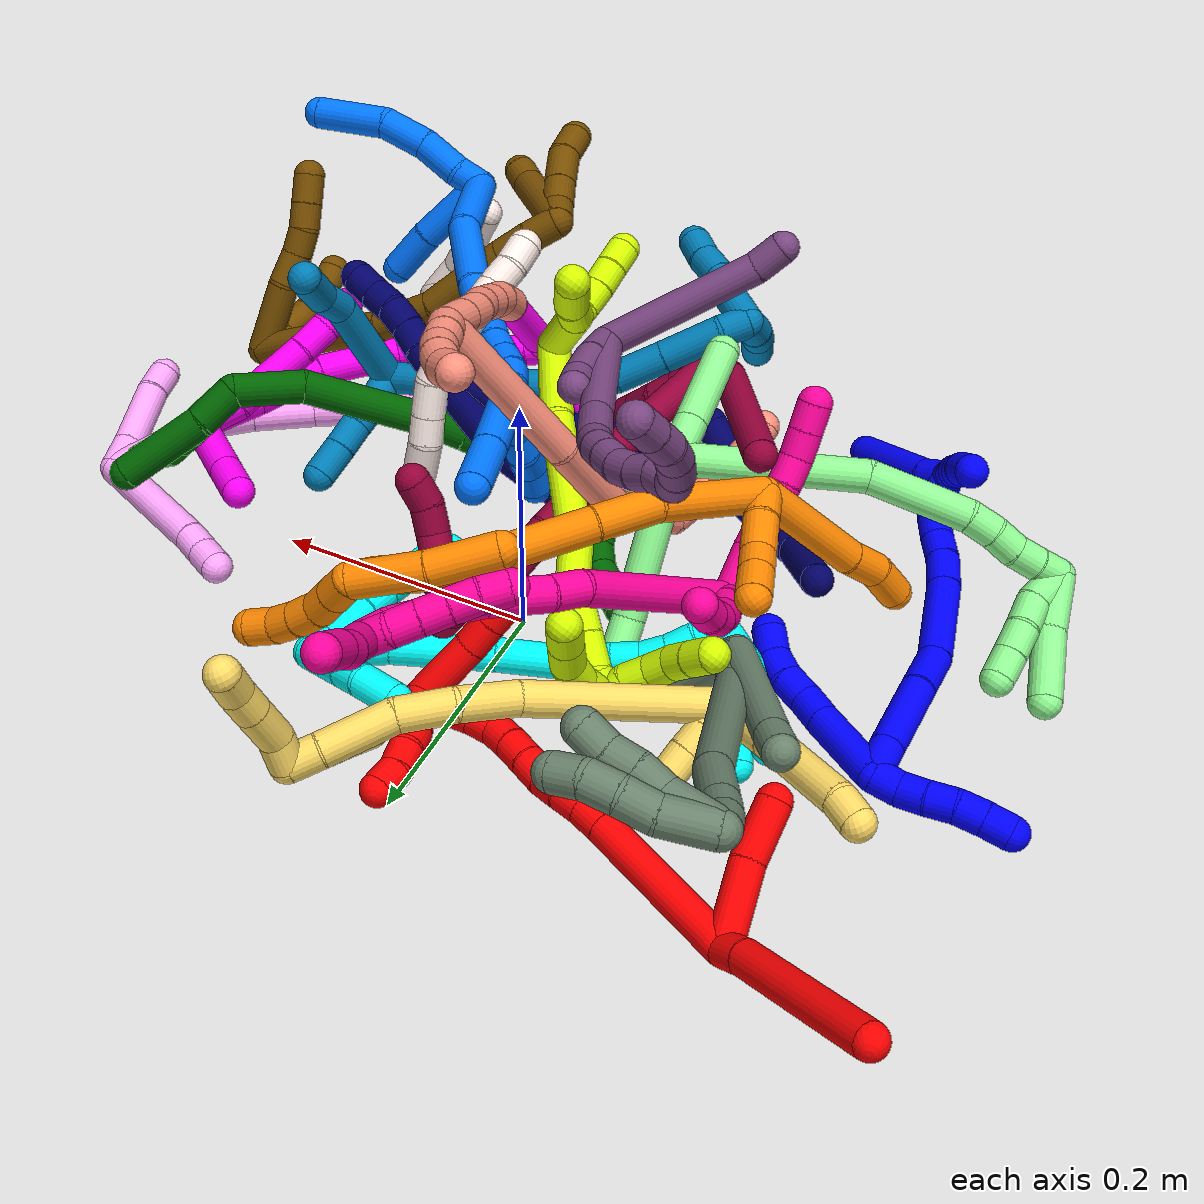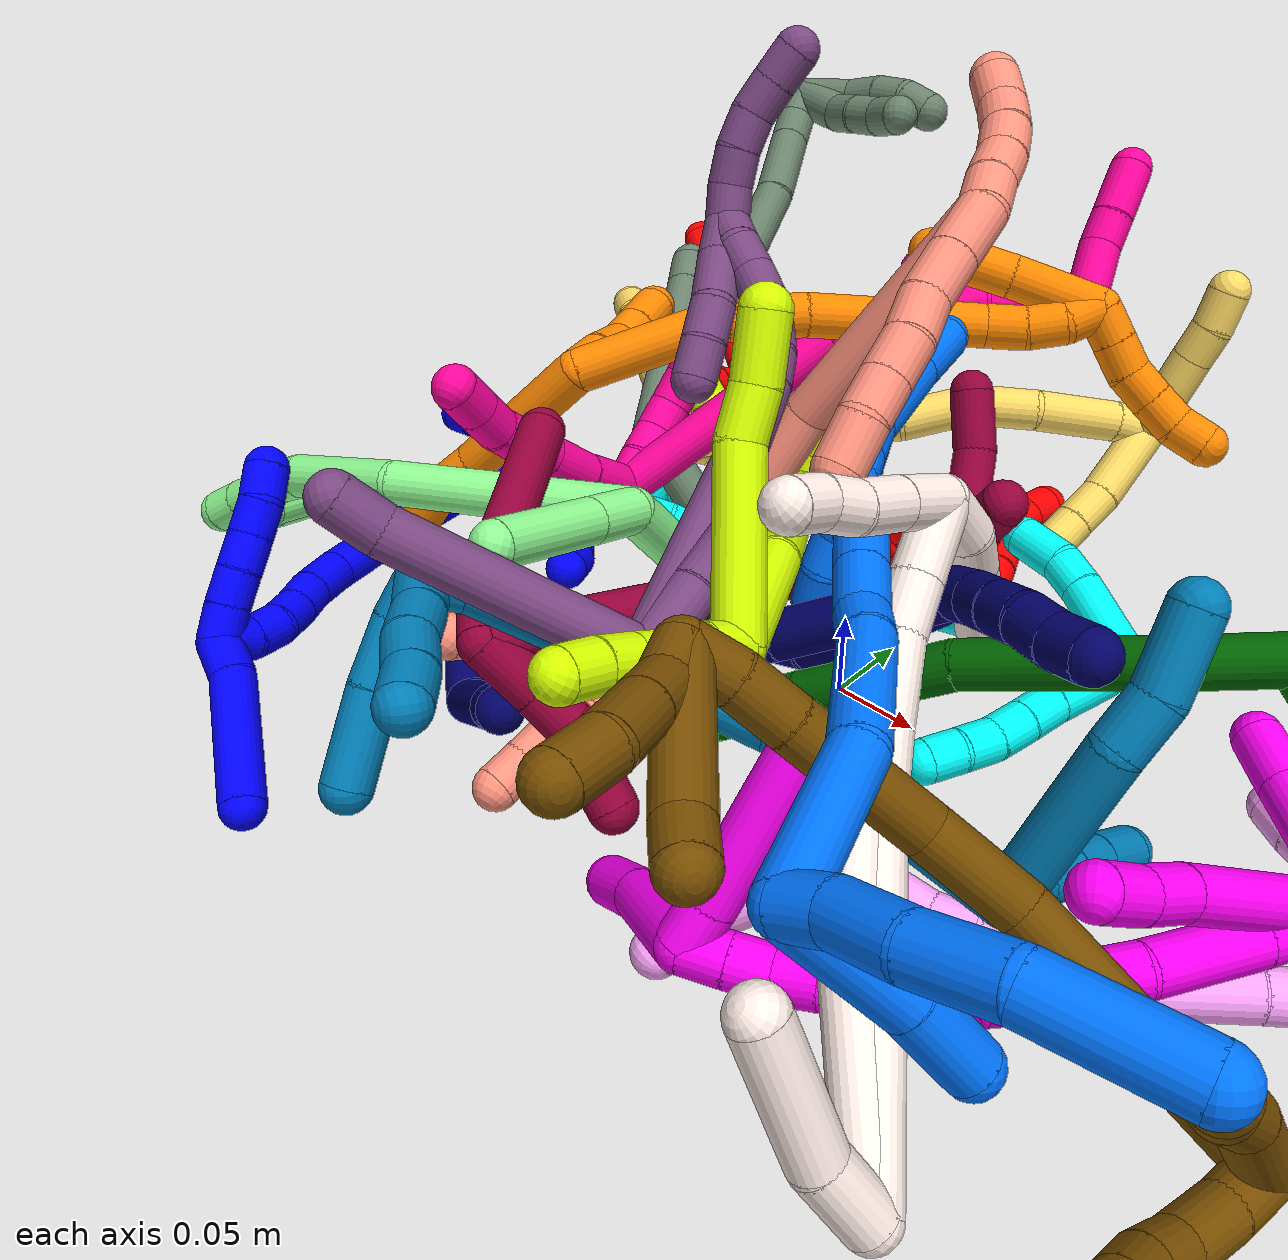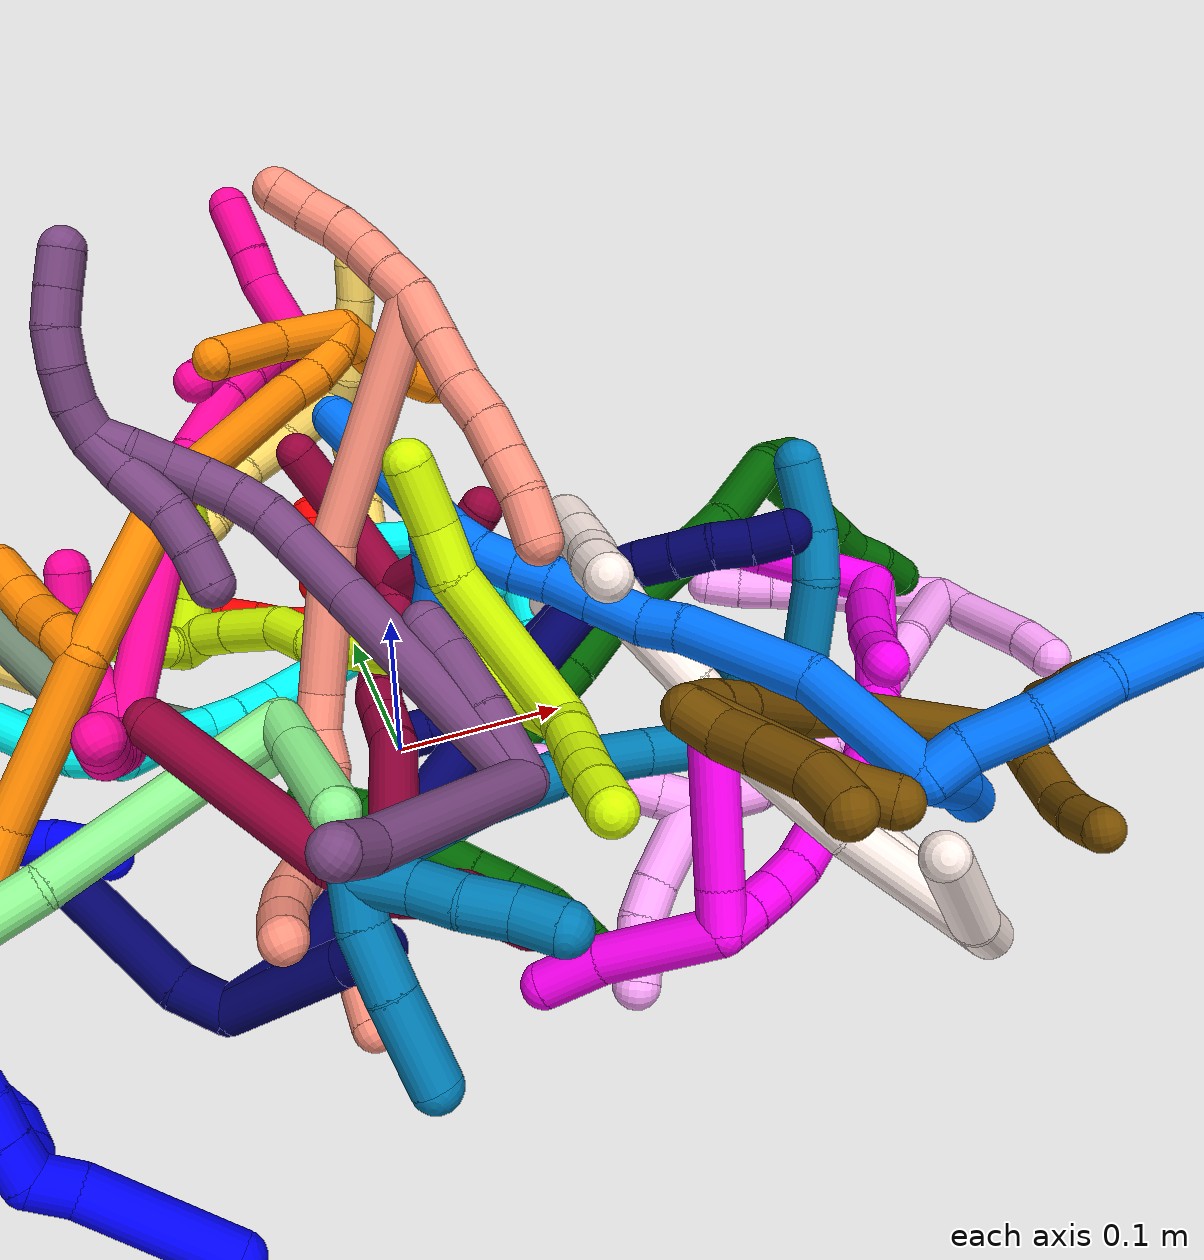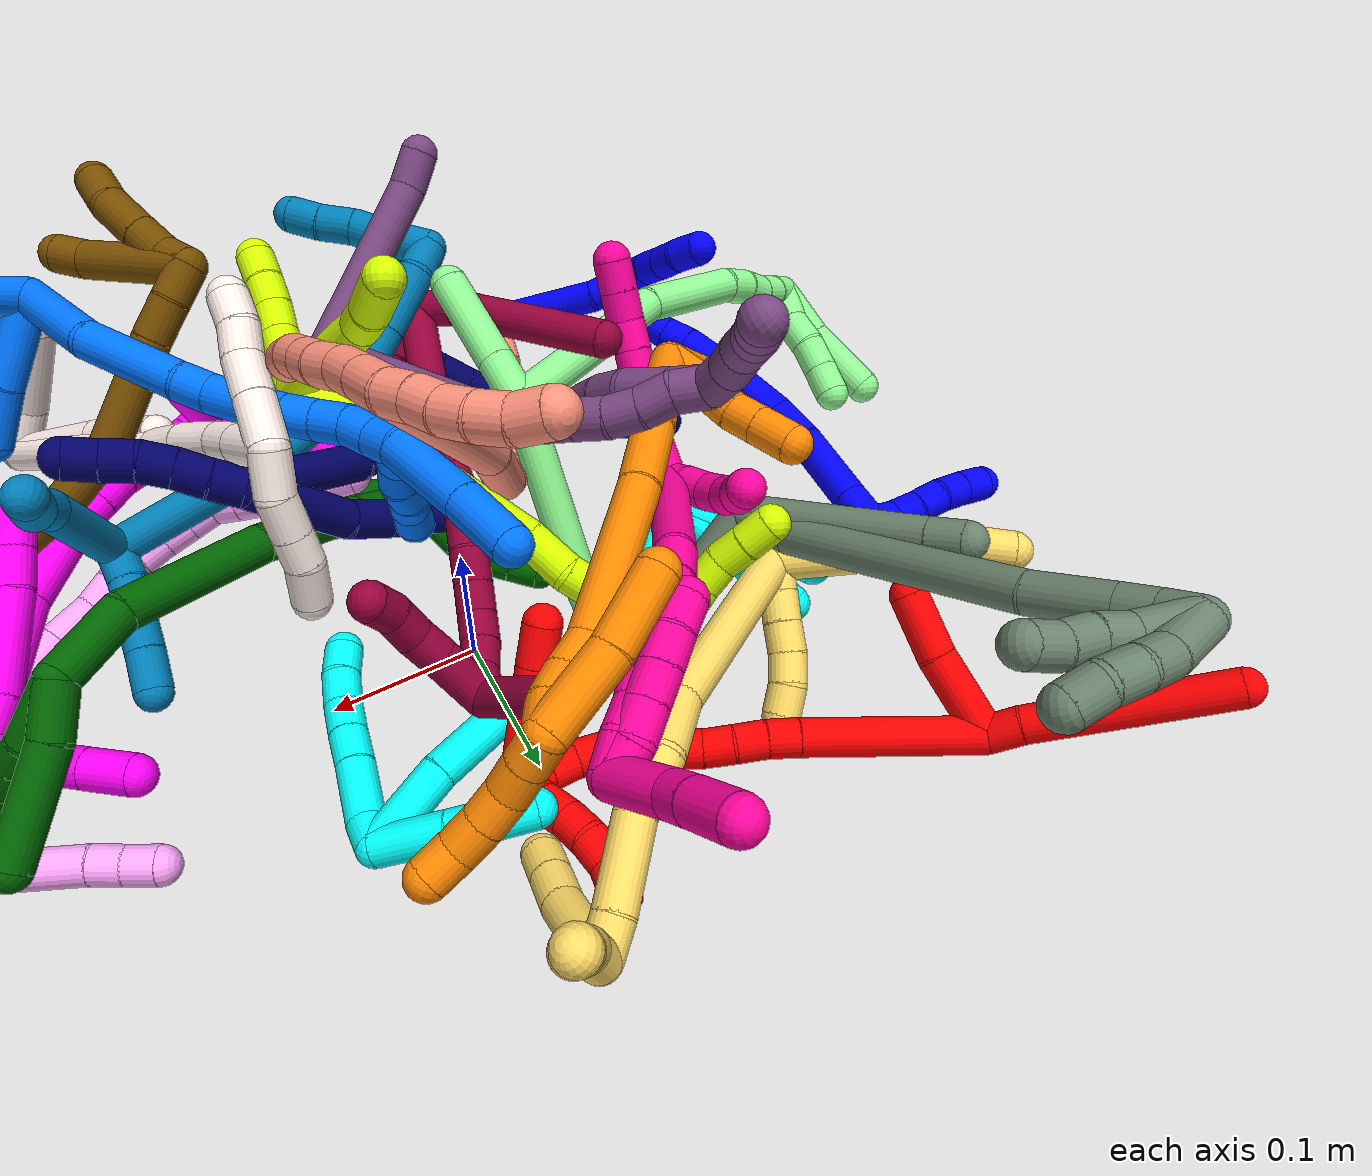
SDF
<sdf version="1.7">
 <world name="default">
  <plugin name="TubeGeneratorPlugin" filename="libtube_generator_plugin.so"/>
  <model name="photoneo_s_sensor">
   <static>1</static>
   <pose>0 0 2 1.57079 1.57079 3.14159</pose>
   <link name="link">
    <inertial><mass>0.1</mass></inertial>
    <sensor name="sensor" type="depth">
     <update_rate>30</update_rate>
     <camera>
      <horizontal_fov>1.22</horizontal_fov>
      <image><width>1920</width><height>1200</height><format>B8G8R8</format></image>
      <clip><near>0.1</near><far>4</far></clip>
      <depth_camera><output>points</output></depth_camera>
     </camera>
     <plugin name="camera_plugin" filename="libgazebo_ros_depth_camera.so">
      <baseline>0.2</baseline>
      <alwaysOn>1</alwaysOn>
      <updateRate>0.0</updateRate>
      <cameraName>camera_ir</cameraName>
      <imageTopicName>/camera/color/image_raw</imageTopicName>
      <cameraInfoTopicName>/camera/color/camera_info</cameraInfoTopicName>
      <depthImageTopicName>/camera/depth/image_raw</depthImageTopicName>
      <depthImageCameraInfoTopicName>/camera/depth/camera_info</depthImageCameraInfoTopicName>
      <pointCloudTopicName>/camera/depth/points</pointCloudTopicName>
      <frameName>fr_optical</frameName>
      <pointCloudCutoff>0.1</pointCloudCutoff>
      <pointCloudCutoffMax>2.0</pointCloudCutoffMax>
      <distortionK1>0</distortionK1>
      <distortionK2>0</distortionK2>
      <distortionK3>0</distortionK3>
      <distortionT1>0</distortionT1>
      <distortionT2>0</distortionT2>
      <CxPrime>0</CxPrime>
      <Cx>0</Cx>
      <Cy>0</Cy>
      <focalLength>0</focalLength>
      <hackBaseline>0</hackBaseline>
     </plugin>
    </sensor>
   </link>
  </model>
  <gravity>0 0 -9.8</gravity>
  <magnetic_field>6e-06 2.3e-05 -4.2e-05</magnetic_field>
  <atmosphere type="adiabatic"/>
  <physics name="default_physics" default="0" type="ode">
   <max_step_size>0.003</max_step_size>
   <real_time_factor>1</real_time_factor>
   <real_time_update_rate>1000</real_time_update_rate>
   <max_contacts>10000</max_contacts>
   <ode>
    <solver>
     <type>quick</type>
     <iters>100</iters>
     <sor>1.3</sor>
     <use_dynamic_moi_rescaling>0</use_dynamic_moi_rescaling>
    </solver>
    <constraints>
     <contact_max_correcting_vel>0</contact_max_correcting_vel>
     <contact_surface_layer>0.001</contact_surface_layer>
     <cfm>0</cfm>
     <erp>0.2</erp>
    </constraints>
   </ode>
  </physics>
  <scene><ambient>0.4 0.4 0.4 1</ambient><background>0.7 0.7 0.7 1</background><shadows>0</shadows></scene>
  <audio><device>default</device></audio>
  <spherical_coordinates>
   <surface_model>EARTH_WGS84</surface_model>
   <latitude_deg>0</latitude_deg>
   <longitude_deg>0</longitude_deg>
   <elevation>0</elevation>
   <heading_deg>0</heading_deg>
  </spherical_coordinates>
  <model name="bin">
   <static>1</static>
   <link name="bottom">
    <collision name="collision-bottom">
     <pose>0 0 -0.01 0 -0 0</pose>
     <geometry><box><size>0.8 0.6 0.02</size></box></geometry>
     <surface>
      <friction><ode><mu>100</mu><mu2>100</mu2></ode></friction>
      <contact><collide_bitmask>65535</collide_bitmask></contact>
     </surface>
    </collision>
   </link>
   <link name="west_wall">
    <collision name="collision-west_wall">
     <pose>-0.41 0 0.1 0 -0 0</pose>
     <geometry><box><size>0.02 0.6 0.2</size></box></geometry>
     <surface>
      <friction><ode><mu>100</mu><mu2>100</mu2></ode></friction>
      <contact><collide_bitmask>65535</collide_bitmask></contact>
     </surface>
    </collision>
   </link>
   <link name="east_wall">
    <collision name="collision-east_wall">
     <pose>0.41 0 0.1 0 -0 0</pose>
     <geometry><box><size>0.02 0.6 0.2</size></box></geometry>
     <surface>
      <friction><ode><mu>100</mu><mu2>100</mu2></ode></friction>
      <contact><collide_bitmask>65535</collide_bitmask></contact>
     </surface>
    </collision>
   </link>
   <link name="south_wall">
    <collision name="collision-south_wall">
     <pose>0 -0.31 0.1 0 -0 0</pose>
     <geometry><box><size>0.8 0.02 0.2</size></box></geometry>
     <surface>
      <friction><ode><mu>100</mu><mu2>100</mu2></ode></friction>
      <contact><collide_bitmask>65535</collide_bitmask></contact>
     </surface>
    </collision>
   </link>
   <link name="north_wall">
    <collision name="collision-north_wall">
     <pose>0 0.31 0.1 0 -0 0</pose>
     <geometry><box><size>0.8 0.02 0.2</size></box></geometry>
     <surface>
      <friction><ode><mu>100</mu><mu2>100</mu2></ode></friction>
      <contact><collide_bitmask>65535</collide_bitmask></contact>
     </surface>
    </collision>
   </link>
  </model>
  <model name="1">
   <static>0</static>
   <link name="1">
    <collision name="collision-cylinder-e_1_2_8">
     <pose>0.017115 -0.01025 0.024246 0.399953 0.576503 0.120052</pose>
     <geometry><cylinder><radius>0.0125</radius><length>0.062797</length></cylinder></geometry>
     <surface>
      <friction><ode><mu>1.16</mu><mu2>1.16</mu2><slip1>0</slip1><slip2>0</slip2></ode></friction>
      <contact><ode><kp>1e+06</kp><kd>1</kd><max_vel>0</max_vel><min_depth>0.001</min_depth></ode></contact>
     </surface>
    </collision>
    <visual name="visual-cylinder-e_1_2_8">
     <pose>0.017115 -0.01025 0.024246 0.399953 0.576503 0.120052</pose>
     <geometry><cylinder><radius>0.0125</radius><length>0.062797</length></cylinder></geometry>
     <material><ambient>0 0 1 1</ambient></material>
    </visual>
    <collision name="collision-cylinder-e_2_8_9">
     <pose>0.040445 -0.025007 0.057637 0.457974 0.547418 0.130688</pose>
     <geometry><cylinder><radius>0.0125</radius><length>0.023881</length></cylinder></geometry>
     <surface>
      <friction><ode><mu>1.16</mu><mu2>1.16</mu2><slip1>0</slip1><slip2>0</slip2></ode></friction>
      <contact><ode><kp>1e+06</kp><kd>1</kd><max_vel>0</max_vel><min_depth>0.001</min_depth></ode></contact>
     </surface>
    </collision>
    <visual name="visual-cylinder-e_2_8_9">
     <pose>0.040445 -0.025007 0.057637 0.457974 0.547418 0.130688</pose>
     <geometry><cylinder><radius>0.0125</radius><length>0.023881</length></cylinder></geometry>
     <material><ambient>0 0 1 1</ambient></material>
    </visual>
    <collision name="collision-cylinder-e_3_9_10">
     <pose>0.049804 -0.033144 0.076789 0.34791 0.287172 0.050804</pose>
     <geometry><cylinder><radius>0.0125</radius><length>0.022198</length></cylinder></geometry>
     <surface>
      <friction><ode><mu>1.16</mu><mu2>1.16</mu2><slip1>0</slip1><slip2>0</slip2></ode></friction>
      <contact><ode><kp>1e+06</kp><kd>1</kd><max_vel>0</max_vel><min_depth>0.001</min_depth></ode></contact>
     </surface>
    </collision>
    <visual name="visual-cylinder-e_3_9_10">
     <pose>0.049804 -0.033144 0.076789 0.34791 0.287172 0.050804</pose>
     <geometry><cylinder><radius>0.0125</radius><length>0.022198</length></cylinder></geometry>
     <material><ambient>0 0 1 1</ambient></material>
    </visual>
    <collision name="collision-cylinder-e_4_10_11">
     <pose>0.0567 -0.042008 0.094558 0.593299 0.38118 0.11781</pose>
     <geometry><cylinder><radius>0.0125</radius><length>0.020172</length></cylinder></geometry>
     <surface>
      <friction><ode><mu>1.16</mu><mu2>1.16</mu2><slip1>0</slip1><slip2>0</slip2></ode></friction>
      <contact><ode><kp>1e+06</kp><kd>1</kd><max_vel>0</max_vel><min_depth>0.001</min_depth></ode></contact>
     </surface>
    </collision>
    <visual name="visual-cylinder-e_4_10_11">
     <pose>0.0567 -0.042008 0.094558 0.593299 0.38118 0.11781</pose>
     <geometry><cylinder><radius>0.0125</radius><length>0.020172</length></cylinder></geometry>
     <material><ambient>0 0 1 1</ambient></material>
    </visual>
    <collision name="collision-cylinder-e_5_11_6">
     <pose>0.063471 -0.055166 0.108471 0.910681 0.292335 0.143924</pose>
     <geometry><cylinder><radius>0.0125</radius><length>0.020952</length></cylinder></geometry>
     <surface>
      <friction><ode><mu>1.16</mu><mu2>1.16</mu2><slip1>0</slip1><slip2>0</slip2></ode></friction>
      <contact><ode><kp>1e+06</kp><kd>1</kd><max_vel>0</max_vel><min_depth>0.001</min_depth></ode></contact>
     </surface>
    </collision>
    <visual name="visual-cylinder-e_5_11_6">
     <pose>0.063471 -0.055166 0.108471 0.910681 0.292335 0.143924</pose>
     <geometry><cylinder><radius>0.0125</radius><length>0.020952</length></cylinder></geometry>
     <material><ambient>0 0 1 1</ambient></material>
    </visual>
    <collision name="collision-cylinder-e_1_2_12">
     <pose>-3.9e-05 -4.9e-05 -0.01 3.1367 -0.003908 -1.34737</pose>
     <geometry><cylinder><radius>0.0125</radius><length>0.02</length></cylinder></geometry>
     <surface>
      <friction><ode><mu>1.16</mu><mu2>1.16</mu2><slip1>0</slip1><slip2>0</slip2></ode></friction>
      <contact><ode><kp>1e+06</kp><kd>1</kd><max_vel>0</max_vel><min_depth>0.001</min_depth></ode></contact>
     </surface>
    </collision>
    <visual name="visual-cylinder-e_1_2_12">
     <pose>-3.9e-05 -4.9e-05 -0.01 3.1367 -0.003908 -1.34737</pose>
     <geometry><cylinder><radius>0.0125</radius><length>0.02</length></cylinder></geometry>
     <material><ambient>0 0 1 1</ambient></material>
    </visual>
    <collision name="collision-cylinder-e_2_12_13">
     <pose>-0.002858 -0.001525 -0.029499 2.99248 -0.281718 -2.17193</pose>
     <geometry><cylinder><radius>0.0125</radius><length>0.02</length></cylinder></geometry>
     <surface>
      <friction><ode><mu>1.16</mu><mu2>1.16</mu2><slip1>0</slip1><slip2>0</slip2></ode></friction>
      <contact><ode><kp>1e+06</kp><kd>1</kd><max_vel>0</max_vel><min_depth>0.001</min_depth></ode></contact>
     </surface>
    </collision>
    <visual name="visual-cylinder-e_2_12_13">
     <pose>-0.002858 -0.001525 -0.029499 2.99248 -0.281718 -2.17193</pose>
     <geometry><cylinder><radius>0.0125</radius><length>0.02</length></cylinder></geometry>
     <material><ambient>0 0 1 1</ambient></material>
    </visual>
    <collision name="collision-cylinder-e_3_13_14">
     <pose>-0.00739 -0.005086 -0.048609 2.92308 -0.176046 -1.35498</pose>
     <geometry><cylinder><radius>0.0125</radius><length>0.02</length></cylinder></geometry>
     <surface>
      <friction><ode><mu>1.16</mu><mu2>1.16</mu2><slip1>0</slip1><slip2>0</slip2></ode></friction>
      <contact><ode><kp>1e+06</kp><kd>1</kd><max_vel>0</max_vel><min_depth>0.001</min_depth></ode></contact>
     </surface>
    </collision>
    <visual name="visual-cylinder-e_3_13_14">
     <pose>-0.00739 -0.005086 -0.048609 2.92308 -0.176046 -1.35498</pose>
     <geometry><cylinder><radius>0.0125</radius><length>0.02</length></cylinder></geometry>
     <material><ambient>0 0 1 1</ambient></material>
    </visual>
    <collision name="collision-cylinder-e_4_14_15">
     <pose>-0.009398 -0.007964 -0.06819 3.06716 -0.025654 -0.663515</pose>
     <geometry><cylinder><radius>0.0125</radius><length>0.02</length></cylinder></geometry>
     <surface>
      <friction><ode><mu>1.16</mu><mu2>1.16</mu2><slip1>0</slip1><slip2>0</slip2></ode></friction>
      <contact><ode><kp>1e+06</kp><kd>1</kd><max_vel>0</max_vel><min_depth>0.001</min_depth></ode></contact>
     </surface>
    </collision>
    <visual name="visual-cylinder-e_4_14_15">
     <pose>-0.009398 -0.007964 -0.06819 3.06716 -0.025654 -0.663515</pose>
     <geometry><cylinder><radius>0.0125</radius><length>0.02</length></cylinder></geometry>
     <material><ambient>0 0 1 1</ambient></material>
    </visual>
    <collision name="collision-cylinder-e_5_15_5">
     <pose>-0.010229 -0.008779 -0.088142 3.1344 -0.057514 -2.8929</pose>
     <geometry><cylinder><radius>0.0125</radius><length>0.02</length></cylinder></geometry>
     <surface>
      <friction><ode><mu>1.16</mu><mu2>1.16</mu2><slip1>0</slip1><slip2>0</slip2></ode></friction>
      <contact><ode><kp>1e+06</kp><kd>1</kd><max_vel>0</max_vel><min_depth>0.001</min_depth></ode></contact>
     </surface>
    </collision>
    <visual name="visual-cylinder-e_5_15_5">
     <pose>-0.010229 -0.008779 -0.088142 3.1344 -0.057514 -2.8929</pose>
     <geometry><cylinder><radius>0.0125</radius><length>0.02</length></cylinder></geometry>
     <material><ambient>0 0 1 1</ambient></material>
    </visual>
    <collision name="collision-cylinder-e_1_2_16">
     <pose>0.007044 -0.011367 0.000398 1.53581 0.554484 0.536333</pose>
     <geometry><cylinder><radius>0.0125</radius><length>0.026758</length></cylinder></geometry>
     <surface>
      <friction><ode><mu>1.16</mu><mu2>1.16</mu2><slip1>0</slip1><slip2>0</slip2></ode></friction>
      <contact><ode><kp>1e+06</kp><kd>1</kd><max_vel>0</max_vel><min_depth>0.001</min_depth></ode></contact>
     </surface>
    </collision>
    <visual name="visual-cylinder-e_1_2_16">
     <pose>0.007044 -0.011367 0.000398 1.53581 0.554484 0.536333</pose>
     <geometry><cylinder><radius>0.0125</radius><length>0.026758</length></cylinder></geometry>
     <material><ambient>0 0 1 1</ambient></material>
    </visual>
    <collision name="collision-cylinder-e_2_16_17">
     <pose>0.02955 -0.048271 0.001304 1.55088 0.544368 0.534142</pose>
     <geometry><cylinder><radius>0.0125</radius><length>0.059713</length></cylinder></geometry>
     <surface>
      <friction><ode><mu>1.16</mu><mu2>1.16</mu2><slip1>0</slip1><slip2>0</slip2></ode></friction>
      <contact><ode><kp>1e+06</kp><kd>1</kd><max_vel>0</max_vel><min_depth>0.001</min_depth></ode></contact>
     </surface>
    </collision>
    <visual name="visual-cylinder-e_2_16_17">
     <pose>0.02955 -0.048271 0.001304 1.55088 0.544368 0.534142</pose>
     <geometry><cylinder><radius>0.0125</radius><length>0.059713</length></cylinder></geometry>
     <material><ambient>0 0 1 1</ambient></material>
    </visual>
    <collision name="collision-cylinder-e_3_17_18">
     <pose>0.056218 -0.087988 0.002007 1.55714 0.668702 0.660279</pose>
     <geometry><cylinder><radius>0.0125</radius><length>0.036151</length></cylinder></geometry>
     <surface>
      <friction><ode><mu>1.16</mu><mu2>1.16</mu2><slip1>0</slip1><slip2>0</slip2></ode></friction>
      <contact><ode><kp>1e+06</kp><kd>1</kd><max_vel>0</max_vel><min_depth>0.001</min_depth></ode></contact>
     </surface>
    </collision>
    <visual name="visual-cylinder-e_3_17_18">
     <pose>0.056218 -0.087988 0.002007 1.55714 0.668702 0.660279</pose>
     <geometry><cylinder><radius>0.0125</radius><length>0.036151</length></cylinder></geometry>
     <material><ambient>0 0 1 1</ambient></material>
    </visual>
    <collision name="collision-cylinder-e_4_18_19">
     <pose>0.085359 -0.130391 0.011938 1.23855 0.540949 0.390252</pose>
     <geometry><cylinder><radius>0.0125</radius><length>0.069655</length></cylinder></geometry>
     <surface>
      <friction><ode><mu>1.16</mu><mu2>1.16</mu2><slip1>0</slip1><slip2>0</slip2></ode></friction>
      <contact><ode><kp>1e+06</kp><kd>1</kd><max_vel>0</max_vel><min_depth>0.001</min_depth></ode></contact>
     </surface>
    </collision>
    <visual name="visual-cylinder-e_4_18_19">
     <pose>0.085359 -0.130391 0.011938 1.23855 0.540949 0.390252</pose>
     <geometry><cylinder><radius>0.0125</radius><length>0.069655</length></cylinder></geometry>
     <material><ambient>0 0 1 1</ambient></material>
    </visual>
    <collision name="collision-cylinder-e_5_19_20">
     <pose>0.109777 -0.169115 0.027142 1.09089 0.500977 0.308083</pose>
     <geometry><cylinder><radius>0.0125</radius><length>0.026998</length></cylinder></geometry>
     <surface>
      <friction><ode><mu>1.16</mu><mu2>1.16</mu2><slip1>0</slip1><slip2>0</slip2></ode></friction>
      <contact><ode><kp>1e+06</kp><kd>1</kd><max_vel>0</max_vel><min_depth>0.001</min_depth></ode></contact>
     </surface>
    </collision>
    <visual name="visual-cylinder-e_5_19_20">
     <pose>0.109777 -0.169115 0.027142 1.09089 0.500977 0.308083</pose>
     <geometry><cylinder><radius>0.0125</radius><length>0.026998</length></cylinder></geometry>
     <material><ambient>0 0 1 1</ambient></material>
    </visual>
    <collision name="collision-cylinder-e_6_20_21">
     <pose>0.121417 -0.186539 0.037968 0.911905 0.532428 0.265883</pose>
     <geometry><cylinder><radius>0.0125</radius><length>0.02032</length></cylinder></geometry>
     <surface>
      <friction><ode><mu>1.16</mu><mu2>1.16</mu2><slip1>0</slip1><slip2>0</slip2></ode></friction>
      <contact><ode><kp>1e+06</kp><kd>1</kd><max_vel>0</max_vel><min_depth>0.001</min_depth></ode></contact>
     </surface>
    </collision>
    <visual name="visual-cylinder-e_6_20_21">
     <pose>0.121417 -0.186539 0.037968 0.911905 0.532428 0.265883</pose>
     <geometry><cylinder><radius>0.0125</radius><length>0.02032</length></cylinder></geometry>
     <material><ambient>0 0 1 1</ambient></material>
    </visual>
    <collision name="collision-cylinder-e_7_21_22">
     <pose>0.130944 -0.200929 0.048439 0.970606 0.449773 0.240117</pose>
     <geometry><cylinder><radius>0.0125</radius><length>0.020101</length></cylinder></geometry>
     <surface>
      <friction><ode><mu>1.16</mu><mu2>1.16</mu2><slip1>0</slip1><slip2>0</slip2></ode></friction>
      <contact><ode><kp>1e+06</kp><kd>1</kd><max_vel>0</max_vel><min_depth>0.001</min_depth></ode></contact>
     </surface>
    </collision>
    <visual name="visual-cylinder-e_7_21_22">
     <pose>0.130944 -0.200929 0.048439 0.970606 0.449773 0.240117</pose>
     <geometry><cylinder><radius>0.0125</radius><length>0.020101</length></cylinder></geometry>
     <material><ambient>0 0 1 1</ambient></material>
    </visual>
    <collision name="collision-cylinder-e_8_22_23">
     <pose>0.139822 -0.217095 0.055947 1.30199 0.463471 0.355719</pose>
     <geometry><cylinder><radius>0.0125</radius><length>0.020169</length></cylinder></geometry>
     <surface>
      <friction><ode><mu>1.16</mu><mu2>1.16</mu2><slip1>0</slip1><slip2>0</slip2></ode></friction>
      <contact><ode><kp>1e+06</kp><kd>1</kd><max_vel>0</max_vel><min_depth>0.001</min_depth></ode></contact>
     </surface>
    </collision>
    <visual name="visual-cylinder-e_8_22_23">
     <pose>0.139822 -0.217095 0.055947 1.30199 0.463471 0.355719</pose>
     <geometry><cylinder><radius>0.0125</radius><length>0.020169</length></cylinder></geometry>
     <material><ambient>0 0 1 1</ambient></material>
    </visual>
    <collision name="collision-cylinder-e_9_23_1">
     <pose>0.146382 -0.235595 0.059374 1.46598 0.205173 0.184843</pose>
     <geometry><cylinder><radius>0.0125</radius><length>0.020136</length></cylinder></geometry>
     <surface>
      <friction><ode><mu>1.16</mu><mu2>1.16</mu2><slip1>0</slip1><slip2>0</slip2></ode></friction>
      <contact><ode><kp>1e+06</kp><kd>1</kd><max_vel>0</max_vel><min_depth>0.001</min_depth></ode></contact>
     </surface>
    </collision>
    <visual name="visual-cylinder-e_9_23_1">
     <pose>0.146382 -0.235595 0.059374 1.46598 0.205173 0.184843</pose>
     <geometry><cylinder><radius>0.0125</radius><length>0.020136</length></cylinder></geometry>
     <material><ambient>0 0 1 1</ambient></material>
    </visual>
    <collision name="collision-cylinder-e_1_1_24">
     <pose>0.138573 -0.24474 0.05887 -2.73679 -1.40303 2.66505</pose>
     <geometry><cylinder><radius>0.0125</radius><length>0.02</length></cylinder></geometry>
     <surface>
      <friction><ode><mu>1.16</mu><mu2>1.16</mu2><slip1>0</slip1><slip2>0</slip2></ode></friction>
      <contact><ode><kp>1e+06</kp><kd>1</kd><max_vel>0</max_vel><min_depth>0.001</min_depth></ode></contact>
     </surface>
    </collision>
    <visual name="visual-cylinder-e_1_1_24">
     <pose>0.138573 -0.24474 0.05887 -2.73679 -1.40303 2.66505</pose>
     <geometry><cylinder><radius>0.0125</radius><length>0.02</length></cylinder></geometry>
     <material><ambient>0 0 1 1</ambient></material>
    </visual>
    <collision name="collision-cylinder-e_2_24_25">
     <pose>0.11883 -0.242861 0.056428 -2.21021 -1.41807 2.08172</pose>
     <geometry><cylinder><radius>0.0125</radius><length>0.02</length></cylinder></geometry>
     <surface>
      <friction><ode><mu>1.16</mu><mu2>1.16</mu2><slip1>0</slip1><slip2>0</slip2></ode></friction>
      <contact><ode><kp>1e+06</kp><kd>1</kd><max_vel>0</max_vel><min_depth>0.001</min_depth></ode></contact>
     </surface>
    </collision>
    <visual name="visual-cylinder-e_2_24_25">
     <pose>0.11883 -0.242861 0.056428 -2.21021 -1.41807 2.08172</pose>
     <geometry><cylinder><radius>0.0125</radius><length>0.02</length></cylinder></geometry>
     <material><ambient>0 0 1 1</ambient></material>
    </visual>
    <collision name="collision-cylinder-e_3_25_26">
     <pose>0.099236 -0.239853 0.053934 -2.29657 -1.32946 2.09993</pose>
     <geometry><cylinder><radius>0.0125</radius><length>0.02</length></cylinder></geometry>
     <surface>
      <friction><ode><mu>1.16</mu><mu2>1.16</mu2><slip1>0</slip1><slip2>0</slip2></ode></friction>
      <contact><ode><kp>1e+06</kp><kd>1</kd><max_vel>0</max_vel><min_depth>0.001</min_depth></ode></contact>
     </surface>
    </collision>
    <visual name="visual-cylinder-e_3_25_26">
     <pose>0.099236 -0.239853 0.053934 -2.29657 -1.32946 2.09993</pose>
     <geometry><cylinder><radius>0.0125</radius><length>0.02</length></cylinder></geometry>
     <material><ambient>0 0 1 1</ambient></material>
    </visual>
    <collision name="collision-cylinder-e_4_26_27">
     <pose>0.079711 -0.236655 0.051052 -2.3137 -1.37813 2.16169</pose>
     <geometry><cylinder><radius>0.0125</radius><length>0.02</length></cylinder></geometry>
     <surface>
      <friction><ode><mu>1.16</mu><mu2>1.16</mu2><slip1>0</slip1><slip2>0</slip2></ode></friction>
      <contact><ode><kp>1e+06</kp><kd>1</kd><max_vel>0</max_vel><min_depth>0.001</min_depth></ode></contact>
     </surface>
    </collision>
    <visual name="visual-cylinder-e_4_26_27">
     <pose>0.079711 -0.236655 0.051052 -2.3137 -1.37813 2.16169</pose>
     <geometry><cylinder><radius>0.0125</radius><length>0.02</length></cylinder></geometry>
     <material><ambient>0 0 1 1</ambient></material>
    </visual>
    <collision name="collision-cylinder-e_5_27_4">
     <pose>0.060785 -0.233821 0.045889 -2.78888 -1.14602 2.60263</pose>
     <geometry><cylinder><radius>0.0125</radius><length>0.02</length></cylinder></geometry>
     <surface>
      <friction><ode><mu>1.16</mu><mu2>1.16</mu2><slip1>0</slip1><slip2>0</slip2></ode></friction>
      <contact><ode><kp>1e+06</kp><kd>1</kd><max_vel>0</max_vel><min_depth>0.001</min_depth></ode></contact>
     </surface>
    </collision>
    <visual name="visual-cylinder-e_5_27_4">
     <pose>0.060785 -0.233821 0.045889 -2.78888 -1.14602 2.60263</pose>
     <geometry><cylinder><radius>0.0125</radius><length>0.02</length></cylinder></geometry>
     <material><ambient>0 0 1 1</ambient></material>
    </visual>
    <collision name="collision-cylinder-e_1_1_28">
     <pose>0.15563 -0.244063 0.068977 -0.15445 0.692566 -0.055826</pose>
     <geometry><cylinder><radius>0.0125</radius><length>0.022543</length></cylinder></geometry>
     <surface>
      <friction><ode><mu>1.16</mu><mu2>1.16</mu2><slip1>0</slip1><slip2>0</slip2></ode></friction>
      <contact><ode><kp>1e+06</kp><kd>1</kd><max_vel>0</max_vel><min_depth>0.001</min_depth></ode></contact>
     </surface>
    </collision>
    <visual name="visual-cylinder-e_1_1_28">
     <pose>0.15563 -0.244063 0.068977 -0.15445 0.692566 -0.055826</pose>
     <geometry><cylinder><radius>0.0125</radius><length>0.022543</length></cylinder></geometry>
     <material><ambient>0 0 1 1</ambient></material>
    </visual>
    <collision name="collision-cylinder-e_2_28_3">
     <pose>0.190488 -0.247166 0.104289 0.164465 0.795525 0.06923</pose>
     <geometry><cylinder><radius>0.0125</radius><length>0.077457</length></cylinder></geometry>
     <surface>
      <friction><ode><mu>1.16</mu><mu2>1.16</mu2><slip1>0</slip1><slip2>0</slip2></ode></friction>
      <contact><ode><kp>1e+06</kp><kd>1</kd><max_vel>0</max_vel><min_depth>0.001</min_depth></ode></contact>
     </surface>
    </collision>
    <visual name="visual-cylinder-e_2_28_3">
     <pose>0.190488 -0.247166 0.104289 0.164465 0.795525 0.06923</pose>
     <geometry><cylinder><radius>0.0125</radius><length>0.077457</length></cylinder></geometry>
     <material><ambient>0 0 1 1</ambient></material>
    </visual>
    <collision name="collision-sphere-3">
     <pose>0.218149 -0.251604 0.131029 0 -0 0</pose>
     <geometry><sphere><radius>0.0125</radius></sphere></geometry>
     <surface>
      <friction><ode><mu>1.16</mu><mu2>1.16</mu2><slip1>0</slip1><slip2>0</slip2></ode></friction>
      <contact><ode><kp>1e+06</kp><kd>1</kd><max_vel>0</max_vel><min_depth>0.001</min_depth></ode></contact>
     </surface>
    </collision>
    <visual name="visual-sphere-3">
     <pose>0.218149 -0.251604 0.131029 0 -0 0</pose>
     <geometry><sphere><radius>0.0125</radius></sphere></geometry>
     <material><ambient>0 0 1 1</ambient></material>
    </visual>
    <collision name="collision-sphere-28">
     <pose>0.162827 -0.242728 0.077548 0 -0 0</pose>
     <geometry><sphere><radius>0.0125</radius></sphere></geometry>
     <surface>
      <friction><ode><mu>1.16</mu><mu2>1.16</mu2><slip1>0</slip1><slip2>0</slip2></ode></friction>
      <contact><ode><kp>1e+06</kp><kd>1</kd><max_vel>0</max_vel><min_depth>0.001</min_depth></ode></contact>
     </surface>
    </collision>
    <visual name="visual-sphere-28">
     <pose>0.162827 -0.242728 0.077548 0 -0 0</pose>
     <geometry><sphere><radius>0.0125</radius></sphere></geometry>
     <material><ambient>0 0 1 1</ambient></material>
    </visual>
    <collision name="collision-sphere-4">
     <pose>0.051674 -0.232397 0.042022 0 -0 0</pose>
     <geometry><sphere><radius>0.0125</radius></sphere></geometry>
     <surface>
      <friction><ode><mu>1.16</mu><mu2>1.16</mu2><slip1>0</slip1><slip2>0</slip2></ode></friction>
      <contact><ode><kp>1e+06</kp><kd>1</kd><max_vel>0</max_vel><min_depth>0.001</min_depth></ode></contact>
     </surface>
    </collision>
    <visual name="visual-sphere-4">
     <pose>0.051674 -0.232397 0.042022 0 -0 0</pose>
     <geometry><sphere><radius>0.0125</radius></sphere></geometry>
     <material><ambient>0 0 1 1</ambient></material>
    </visual>
    <collision name="collision-sphere-27">
     <pose>0.069896 -0.235245 0.049757 0 -0 0</pose>
     <geometry><sphere><radius>0.0125</radius></sphere></geometry>
     <surface>
      <friction><ode><mu>1.16</mu><mu2>1.16</mu2><slip1>0</slip1><slip2>0</slip2></ode></friction>
      <contact><ode><kp>1e+06</kp><kd>1</kd><max_vel>0</max_vel><min_depth>0.001</min_depth></ode></contact>
     </surface>
    </collision>
    <visual name="visual-sphere-27">
     <pose>0.069896 -0.235245 0.049757 0 -0 0</pose>
     <geometry><sphere><radius>0.0125</radius></sphere></geometry>
     <material><ambient>0 0 1 1</ambient></material>
    </visual>
    <collision name="collision-sphere-26">
     <pose>0.089526 -0.238065 0.052347 0 -0 0</pose>
     <geometry><sphere><radius>0.0125</radius></sphere></geometry>
     <surface>
      <friction><ode><mu>1.16</mu><mu2>1.16</mu2><slip1>0</slip1><slip2>0</slip2></ode></friction>
      <contact><ode><kp>1e+06</kp><kd>1</kd><max_vel>0</max_vel><min_depth>0.001</min_depth></ode></contact>
     </surface>
    </collision>
    <visual name="visual-sphere-26">
     <pose>0.089526 -0.238065 0.052347 0 -0 0</pose>
     <geometry><sphere><radius>0.0125</radius></sphere></geometry>
     <material><ambient>0 0 1 1</ambient></material>
    </visual>
    <collision name="collision-sphere-25">
     <pose>0.108946 -0.241641 0.05552 0 -0 0</pose>
     <geometry><sphere><radius>0.0125</radius></sphere></geometry>
     <surface>
      <friction><ode><mu>1.16</mu><mu2>1.16</mu2><slip1>0</slip1><slip2>0</slip2></ode></friction>
      <contact><ode><kp>1e+06</kp><kd>1</kd><max_vel>0</max_vel><min_depth>0.001</min_depth></ode></contact>
     </surface>
    </collision>
    <visual name="visual-sphere-25">
     <pose>0.108946 -0.241641 0.05552 0 -0 0</pose>
     <geometry><sphere><radius>0.0125</radius></sphere></geometry>
     <material><ambient>0 0 1 1</ambient></material>
    </visual>
    <collision name="collision-sphere-24">
     <pose>0.128714 -0.244082 0.057336 0 -0 0</pose>
     <geometry><sphere><radius>0.0125</radius></sphere></geometry>
     <surface>
      <friction><ode><mu>1.16</mu><mu2>1.16</mu2><slip1>0</slip1><slip2>0</slip2></ode></friction>
      <contact><ode><kp>1e+06</kp><kd>1</kd><max_vel>0</max_vel><min_depth>0.001</min_depth></ode></contact>
     </surface>
    </collision>
    <visual name="visual-sphere-24">
     <pose>0.128714 -0.244082 0.057336 0 -0 0</pose>
     <geometry><sphere><radius>0.0125</radius></sphere></geometry>
     <material><ambient>0 0 1 1</ambient></material>
    </visual>
    <collision name="collision-sphere-1">
     <pose>0.148433 -0.245397 0.060405 0 -0 0</pose>
     <geometry><sphere><radius>0.0125</radius></sphere></geometry>
     <surface>
      <friction><ode><mu>1.16</mu><mu2>1.16</mu2><slip1>0</slip1><slip2>0</slip2></ode></friction>
      <contact><ode><kp>1e+06</kp><kd>1</kd><max_vel>0</max_vel><min_depth>0.001</min_depth></ode></contact>
     </surface>
    </collision>
    <visual name="visual-sphere-1">
     <pose>0.148433 -0.245397 0.060405 0 -0 0</pose>
     <geometry><sphere><radius>0.0125</radius></sphere></geometry>
     <material><ambient>0 0 1 1</ambient></material>
    </visual>
    <collision name="collision-sphere-23">
     <pose>0.14433 -0.225792 0.058343 0 -0 0</pose>
     <geometry><sphere><radius>0.0125</radius></sphere></geometry>
     <surface>
      <friction><ode><mu>1.16</mu><mu2>1.16</mu2><slip1>0</slip1><slip2>0</slip2></ode></friction>
      <contact><ode><kp>1e+06</kp><kd>1</kd><max_vel>0</max_vel><min_depth>0.001</min_depth></ode></contact>
     </surface>
    </collision>
    <visual name="visual-sphere-23">
     <pose>0.14433 -0.225792 0.058343 0 -0 0</pose>
     <geometry><sphere><radius>0.0125</radius></sphere></geometry>
     <material><ambient>0 0 1 1</ambient></material>
    </visual>
    <collision name="collision-sphere-22">
     <pose>0.135314 -0.208398 0.053551 0 -0 0</pose>
     <geometry><sphere><radius>0.0125</radius></sphere></geometry>
     <surface>
      <friction><ode><mu>1.16</mu><mu2>1.16</mu2><slip1>0</slip1><slip2>0</slip2></ode></friction>
      <contact><ode><kp>1e+06</kp><kd>1</kd><max_vel>0</max_vel><min_depth>0.001</min_depth></ode></contact>
     </surface>
    </collision>
    <visual name="visual-sphere-22">
     <pose>0.135314 -0.208398 0.053551 0 -0 0</pose>
     <geometry><sphere><radius>0.0125</radius></sphere></geometry>
     <material><ambient>0 0 1 1</ambient></material>
    </visual>
    <collision name="collision-sphere-21">
     <pose>0.126575 -0.19346 0.043327 0 -0 0</pose>
     <geometry><sphere><radius>0.0125</radius></sphere></geometry>
     <surface>
      <friction><ode><mu>1.16</mu><mu2>1.16</mu2><slip1>0</slip1><slip2>0</slip2></ode></friction>
      <contact><ode><kp>1e+06</kp><kd>1</kd><max_vel>0</max_vel><min_depth>0.001</min_depth></ode></contact>
     </surface>
    </collision>
    <visual name="visual-sphere-21">
     <pose>0.126575 -0.19346 0.043327 0 -0 0</pose>
     <geometry><sphere><radius>0.0125</radius></sphere></geometry>
     <material><ambient>0 0 1 1</ambient></material>
    </visual>
    <collision name="collision-sphere-6">
     <pose>0.06649 -0.06309 0.114623 0 -0 0</pose>
     <geometry><sphere><radius>0.0125</radius></sphere></geometry>
     <surface>
      <friction><ode><mu>1.16</mu><mu2>1.16</mu2><slip1>0</slip1><slip2>0</slip2></ode></friction>
      <contact><ode><kp>1e+06</kp><kd>1</kd><max_vel>0</max_vel><min_depth>0.001</min_depth></ode></contact>
     </surface>
    </collision>
    <visual name="visual-sphere-6">
     <pose>0.06649 -0.06309 0.114623 0 -0 0</pose>
     <geometry><sphere><radius>0.0125</radius></sphere></geometry>
     <material><ambient>0 0 1 1</ambient></material>
    </visual>
    <collision name="collision-sphere-11">
     <pose>0.060452 -0.047242 0.10232 0 -0 0</pose>
     <geometry><sphere><radius>0.0125</radius></sphere></geometry>
     <surface>
      <friction><ode><mu>1.16</mu><mu2>1.16</mu2><slip1>0</slip1><slip2>0</slip2></ode></friction>
      <contact><ode><kp>1e+06</kp><kd>1</kd><max_vel>0</max_vel><min_depth>0.001</min_depth></ode></contact>
     </surface>
    </collision>
    <visual name="visual-sphere-11">
     <pose>0.060452 -0.047242 0.10232 0 -0 0</pose>
     <geometry><sphere><radius>0.0125</radius></sphere></geometry>
     <material><ambient>0 0 1 1</ambient></material>
    </visual>
    <collision name="collision-sphere-10">
     <pose>0.052947 -0.036773 0.086796 0 -0 0</pose>
     <geometry><sphere><radius>0.0125</radius></sphere></geometry>
     <surface>
      <friction><ode><mu>1.16</mu><mu2>1.16</mu2><slip1>0</slip1><slip2>0</slip2></ode></friction>
      <contact><ode><kp>1e+06</kp><kd>1</kd><max_vel>0</max_vel><min_depth>0.001</min_depth></ode></contact>
     </surface>
    </collision>
    <visual name="visual-sphere-10">
     <pose>0.052947 -0.036773 0.086796 0 -0 0</pose>
     <geometry><sphere><radius>0.0125</radius></sphere></geometry>
     <material><ambient>0 0 1 1</ambient></material>
    </visual>
    <collision name="collision-sphere-9">
     <pose>0.04666 -0.029515 0.066782 0 -0 0</pose>
     <geometry><sphere><radius>0.0125</radius></sphere></geometry>
     <surface>
      <friction><ode><mu>1.16</mu><mu2>1.16</mu2><slip1>0</slip1><slip2>0</slip2></ode></friction>
      <contact><ode><kp>1e+06</kp><kd>1</kd><max_vel>0</max_vel><min_depth>0.001</min_depth></ode></contact>
     </surface>
    </collision>
    <visual name="visual-sphere-9">
     <pose>0.04666 -0.029515 0.066782 0 -0 0</pose>
     <geometry><sphere><radius>0.0125</radius></sphere></geometry>
     <material><ambient>0 0 1 1</ambient></material>
    </visual>
    <collision name="collision-sphere-2">
     <geometry><sphere><radius>0.0125</radius></sphere></geometry>
     <surface>
      <friction><ode><mu>1.16</mu><mu2>1.16</mu2><slip1>0</slip1><slip2>0</slip2></ode></friction>
      <contact><ode><kp>1e+06</kp><kd>1</kd><max_vel>0</max_vel><min_depth>0.001</min_depth></ode></contact>
     </surface>
    </collision>
    <visual name="visual-sphere-2">
     <geometry><sphere><radius>0.0125</radius></sphere></geometry>
     <material><ambient>0 0 1 1</ambient></material>
    </visual>
    <collision name="collision-sphere-19">
     <pose>0.103293 -0.158613 0.021676 0 -0 0</pose>
     <geometry><sphere><radius>0.0125</radius></sphere></geometry>
     <surface>
      <friction><ode><mu>1.16</mu><mu2>1.16</mu2><slip1>0</slip1><slip2>0</slip2></ode></friction>
      <contact><ode><kp>1e+06</kp><kd>1</kd><max_vel>0</max_vel><min_depth>0.001</min_depth></ode></contact>
     </surface>
    </collision>
    <visual name="visual-sphere-19">
     <pose>0.103293 -0.158613 0.021676 0 -0 0</pose>
     <geometry><sphere><radius>0.0125</radius></sphere></geometry>
     <material><ambient>0 0 1 1</ambient></material>
    </visual>
    <collision name="collision-sphere-8">
     <pose>0.03423 -0.0205 0.048492 0 -0 0</pose>
     <geometry><sphere><radius>0.0125</radius></sphere></geometry>
     <surface>
      <friction><ode><mu>1.16</mu><mu2>1.16</mu2><slip1>0</slip1><slip2>0</slip2></ode></friction>
      <contact><ode><kp>1e+06</kp><kd>1</kd><max_vel>0</max_vel><min_depth>0.001</min_depth></ode></contact>
     </surface>
    </collision>
    <visual name="visual-sphere-8">
     <pose>0.03423 -0.0205 0.048492 0 -0 0</pose>
     <geometry><sphere><radius>0.0125</radius></sphere></geometry>
     <material><ambient>0 0 1 1</ambient></material>
    </visual>
    <collision name="collision-sphere-12">
     <pose>-7.8e-05 -9.8e-05 -0.02 0 -0 0</pose>
     <geometry><sphere><radius>0.0125</radius></sphere></geometry>
     <surface>
      <friction><ode><mu>1.16</mu><mu2>1.16</mu2><slip1>0</slip1><slip2>0</slip2></ode></friction>
      <contact><ode><kp>1e+06</kp><kd>1</kd><max_vel>0</max_vel><min_depth>0.001</min_depth></ode></contact>
     </surface>
    </collision>
    <visual name="visual-sphere-12">
     <pose>-7.8e-05 -9.8e-05 -0.02 0 -0 0</pose>
     <geometry><sphere><radius>0.0125</radius></sphere></geometry>
     <material><ambient>0 0 1 1</ambient></material>
    </visual>
    <collision name="collision-sphere-13">
     <pose>-0.005638 -0.002952 -0.038998 0 -0 0</pose>
     <geometry><sphere><radius>0.0125</radius></sphere></geometry>
     <surface>
      <friction><ode><mu>1.16</mu><mu2>1.16</mu2><slip1>0</slip1><slip2>0</slip2></ode></friction>
      <contact><ode><kp>1e+06</kp><kd>1</kd><max_vel>0</max_vel><min_depth>0.001</min_depth></ode></contact>
     </surface>
    </collision>
    <visual name="visual-sphere-13">
     <pose>-0.005638 -0.002952 -0.038998 0 -0 0</pose>
     <geometry><sphere><radius>0.0125</radius></sphere></geometry>
     <material><ambient>0 0 1 1</ambient></material>
    </visual>
    <collision name="collision-sphere-14">
     <pose>-0.009141 -0.007221 -0.058221 0 -0 0</pose>
     <geometry><sphere><radius>0.0125</radius></sphere></geometry>
     <surface>
      <friction><ode><mu>1.16</mu><mu2>1.16</mu2><slip1>0</slip1><slip2>0</slip2></ode></friction>
      <contact><ode><kp>1e+06</kp><kd>1</kd><max_vel>0</max_vel><min_depth>0.001</min_depth></ode></contact>
     </surface>
    </collision>
    <visual name="visual-sphere-14">
     <pose>-0.009141 -0.007221 -0.058221 0 -0 0</pose>
     <geometry><sphere><radius>0.0125</radius></sphere></geometry>
     <material><ambient>0 0 1 1</ambient></material>
    </visual>
    <collision name="collision-sphere-15">
     <pose>-0.009654 -0.008707 -0.078159 0 -0 0</pose>
     <geometry><sphere><radius>0.0125</radius></sphere></geometry>
     <surface>
      <friction><ode><mu>1.16</mu><mu2>1.16</mu2><slip1>0</slip1><slip2>0</slip2></ode></friction>
      <contact><ode><kp>1e+06</kp><kd>1</kd><max_vel>0</max_vel><min_depth>0.001</min_depth></ode></contact>
     </surface>
    </collision>
    <visual name="visual-sphere-15">
     <pose>-0.009654 -0.008707 -0.078159 0 -0 0</pose>
     <geometry><sphere><radius>0.0125</radius></sphere></geometry>
     <material><ambient>0 0 1 1</ambient></material>
    </visual>
    <collision name="collision-sphere-5">
     <pose>-0.010804 -0.008851 -0.098125 0 -0 0</pose>
     <geometry><sphere><radius>0.0125</radius></sphere></geometry>
     <surface>
      <friction><ode><mu>1.16</mu><mu2>1.16</mu2><slip1>0</slip1><slip2>0</slip2></ode></friction>
      <contact><ode><kp>1e+06</kp><kd>1</kd><max_vel>0</max_vel><min_depth>0.001</min_depth></ode></contact>
     </surface>
    </collision>
    <visual name="visual-sphere-5">
     <pose>-0.010804 -0.008851 -0.098125 0 -0 0</pose>
     <geometry><sphere><radius>0.0125</radius></sphere></geometry>
     <material><ambient>0 0 1 1</ambient></material>
    </visual>
    <collision name="collision-sphere-16">
     <pose>0.014088 -0.022735 0.000796 0 -0 0</pose>
     <geometry><sphere><radius>0.0125</radius></sphere></geometry>
     <surface>
      <friction><ode><mu>1.16</mu><mu2>1.16</mu2><slip1>0</slip1><slip2>0</slip2></ode></friction>
      <contact><ode><kp>1e+06</kp><kd>1</kd><max_vel>0</max_vel><min_depth>0.001</min_depth></ode></contact>
     </surface>
    </collision>
    <visual name="visual-sphere-16">
     <pose>0.014088 -0.022735 0.000796 0 -0 0</pose>
     <geometry><sphere><radius>0.0125</radius></sphere></geometry>
     <material><ambient>0 0 1 1</ambient></material>
    </visual>
    <collision name="collision-sphere-17">
     <pose>0.045012 -0.073807 0.001813 0 -0 0</pose>
     <geometry><sphere><radius>0.0125</radius></sphere></geometry>
     <surface>
      <friction><ode><mu>1.16</mu><mu2>1.16</mu2><slip1>0</slip1><slip2>0</slip2></ode></friction>
      <contact><ode><kp>1e+06</kp><kd>1</kd><max_vel>0</max_vel><min_depth>0.001</min_depth></ode></contact>
     </surface>
    </collision>
    <visual name="visual-sphere-17">
     <pose>0.045012 -0.073807 0.001813 0 -0 0</pose>
     <geometry><sphere><radius>0.0125</radius></sphere></geometry>
     <material><ambient>0 0 1 1</ambient></material>
    </visual>
    <collision name="collision-sphere-18">
     <pose>0.067425 -0.102169 0.0022 0 -0 0</pose>
     <geometry><sphere><radius>0.0125</radius></sphere></geometry>
     <surface>
      <friction><ode><mu>1.16</mu><mu2>1.16</mu2><slip1>0</slip1><slip2>0</slip2></ode></friction>
      <contact><ode><kp>1e+06</kp><kd>1</kd><max_vel>0</max_vel><min_depth>0.001</min_depth></ode></contact>
     </surface>
    </collision>
    <visual name="visual-sphere-18">
     <pose>0.067425 -0.102169 0.0022 0 -0 0</pose>
     <geometry><sphere><radius>0.0125</radius></sphere></geometry>
     <material><ambient>0 0 1 1</ambient></material>
    </visual>
    <collision name="collision-sphere-20">
     <pose>0.11626 -0.179618 0.032609 0 -0 0</pose>
     <geometry><sphere><radius>0.0125</radius></sphere></geometry>
     <surface>
      <friction><ode><mu>1.16</mu><mu2>1.16</mu2><slip1>0</slip1><slip2>0</slip2></ode></friction>
      <contact><ode><kp>1e+06</kp><kd>1</kd><max_vel>0</max_vel><min_depth>0.001</min_depth></ode></contact>
     </surface>
    </collision>
    <visual name="visual-sphere-20">
     <pose>0.11626 -0.179618 0.032609 0 -0 0</pose>
     <geometry><sphere><radius>0.0125</radius></sphere></geometry>
     <material><ambient>0 0 1 1</ambient></material>
    </visual>
    <inertial>
     <pose>0.075985 -0.120027 0.032861 0 -0 0</pose>
     <mass>0.75</mass>
     <inertia><ixx>0.000146</ixx><ixy>0</ixy><ixz>0</ixz><iyy>0.000108</iyy><iyz>0</iyz><izz>8e-06</izz></inertia>
    </inertial>
   </link>
   <pose>-0.288741 0.045168 0.019459 -1.19447 0.941676 -1.28609</pose>
  </model>
  <model name="2">
   <static>0</static>
   <link name="2">
    <collision name="collision-cylinder-e_1_2_8">
     <pose>-0.007797 -0.003932 0.007764 0.468799 -0.730536 -0.182135</pose>
     <geometry><cylinder><radius>0.0125</radius><length>0.023371</length></cylinder></geometry>
     <surface>
      <friction><ode><mu>1.16</mu><mu2>1.16</mu2><slip1>0</slip1><slip2>0</slip2></ode></friction>
      <contact><ode><kp>1e+06</kp><kd>1</kd><max_vel>0</max_vel><min_depth>0.001</min_depth></ode></contact>
     </surface>
    </collision>
    <visual name="visual-cylinder-e_1_2_8">
     <pose>-0.007797 -0.003932 0.007764 0.468799 -0.730536 -0.182135</pose>
     <geometry><cylinder><radius>0.0125</radius><length>0.023371</length></cylinder></geometry>
     <material><ambient>1 0 0 1</ambient></material>
    </visual>
    <collision name="collision-cylinder-e_2_8_6">
     <pose>-0.057533 -0.021235 0.061039 0.285748 -0.723996 -0.108843</pose>
     <geometry><cylinder><radius>0.0125</radius><length>0.126629</length></cylinder></geometry>
     <surface>
      <friction><ode><mu>1.16</mu><mu2>1.16</mu2><slip1>0</slip1><slip2>0</slip2></ode></friction>
      <contact><ode><kp>1e+06</kp><kd>1</kd><max_vel>0</max_vel><min_depth>0.001</min_depth></ode></contact>
     </surface>
    </collision>
    <visual name="visual-cylinder-e_2_8_6">
     <pose>-0.057533 -0.021235 0.061039 0.285748 -0.723996 -0.108843</pose>
     <geometry><cylinder><radius>0.0125</radius><length>0.126629</length></cylinder></geometry>
     <material><ambient>1 0 0 1</ambient></material>
    </visual>
    <collision name="collision-cylinder-e_1_2_9">
     <pose>-0.005458 -0.016718 -0.022731 2.50747 -0.191059 -0.568244</pose>
     <geometry><cylinder><radius>0.0125</radius><length>0.057479</length></cylinder></geometry>
     <surface>
      <friction><ode><mu>1.16</mu><mu2>1.16</mu2><slip1>0</slip1><slip2>0</slip2></ode></friction>
      <contact><ode><kp>1e+06</kp><kd>1</kd><max_vel>0</max_vel><min_depth>0.001</min_depth></ode></contact>
     </surface>
    </collision>
    <visual name="visual-cylinder-e_1_2_9">
     <pose>-0.005458 -0.016718 -0.022731 2.50747 -0.191059 -0.568244</pose>
     <geometry><cylinder><radius>0.0125</radius><length>0.057479</length></cylinder></geometry>
     <material><ambient>1 0 0 1</ambient></material>
    </visual>
    <collision name="collision-cylinder-e_2_9_5">
     <pose>-0.017991 -0.045475 -0.061493 2.49741 -0.339293 -0.948457</pose>
     <geometry><cylinder><radius>0.0125</radius><length>0.042521</length></cylinder></geometry>
     <surface>
      <friction><ode><mu>1.16</mu><mu2>1.16</mu2><slip1>0</slip1><slip2>0</slip2></ode></friction>
      <contact><ode><kp>1e+06</kp><kd>1</kd><max_vel>0</max_vel><min_depth>0.001</min_depth></ode></contact>
     </surface>
    </collision>
    <visual name="visual-cylinder-e_2_9_5">
     <pose>-0.017991 -0.045475 -0.061493 2.49741 -0.339293 -0.948457</pose>
     <geometry><cylinder><radius>0.0125</radius><length>0.042521</length></cylinder></geometry>
     <material><ambient>1 0 0 1</ambient></material>
    </visual>
    <collision name="collision-cylinder-e_1_2_10">
     <pose>0.044147 -0.015336 -0.037471 2.7531 0.828598 2.30029</pose>
     <geometry><cylinder><radius>0.0125</radius><length>0.119803</length></cylinder></geometry>
     <surface>
      <friction><ode><mu>1.16</mu><mu2>1.16</mu2><slip1>0</slip1><slip2>0</slip2></ode></friction>
      <contact><ode><kp>1e+06</kp><kd>1</kd><max_vel>0</max_vel><min_depth>0.001</min_depth></ode></contact>
     </surface>
    </collision>
    <visual name="visual-cylinder-e_1_2_10">
     <pose>0.044147 -0.015336 -0.037471 2.7531 0.828598 2.30029</pose>
     <geometry><cylinder><radius>0.0125</radius><length>0.119803</length></cylinder></geometry>
     <material><ambient>1 0 0 1</ambient></material>
    </visual>
    <collision name="collision-cylinder-e_2_10_11">
     <pose>0.095876 -0.032816 -0.081218 2.8125 0.852162 2.44017</pose>
     <geometry><cylinder><radius>0.0125</radius><length>0.020148</length></cylinder></geometry>
     <surface>
      <friction><ode><mu>1.16</mu><mu2>1.16</mu2><slip1>0</slip1><slip2>0</slip2></ode></friction>
      <contact><ode><kp>1e+06</kp><kd>1</kd><max_vel>0</max_vel><min_depth>0.001</min_depth></ode></contact>
     </surface>
    </collision>
    <visual name="visual-cylinder-e_2_10_11">
     <pose>0.095876 -0.032816 -0.081218 2.8125 0.852162 2.44017</pose>
     <geometry><cylinder><radius>0.0125</radius><length>0.020148</length></cylinder></geometry>
     <material><ambient>1 0 0 1</ambient></material>
    </visual>
    <collision name="collision-cylinder-e_3_11_12">
     <pose>0.111609 -0.036406 -0.093144 2.89096 0.94975 2.66099</pose>
     <geometry><cylinder><radius>0.0125</radius><length>0.020045</length></cylinder></geometry>
     <surface>
      <friction><ode><mu>1.16</mu><mu2>1.16</mu2><slip1>0</slip1><slip2>0</slip2></ode></friction>
      <contact><ode><kp>1e+06</kp><kd>1</kd><max_vel>0</max_vel><min_depth>0.001</min_depth></ode></contact>
     </surface>
    </collision>
    <visual name="visual-cylinder-e_3_11_12">
     <pose>0.111609 -0.036406 -0.093144 2.89096 0.94975 2.66099</pose>
     <geometry><cylinder><radius>0.0125</radius><length>0.020045</length></cylinder></geometry>
     <material><ambient>1 0 0 1</ambient></material>
    </visual>
    <collision name="collision-cylinder-e_4_12_13">
     <pose>0.127353 -0.038092 -0.1053 3.10485 0.862011 3.06173</pose>
     <geometry><cylinder><radius>0.0125</radius><length>0.020003</length></cylinder></geometry>
     <surface>
      <friction><ode><mu>1.16</mu><mu2>1.16</mu2><slip1>0</slip1><slip2>0</slip2></ode></friction>
      <contact><ode><kp>1e+06</kp><kd>1</kd><max_vel>0</max_vel><min_depth>0.001</min_depth></ode></contact>
     </surface>
    </collision>
    <visual name="visual-cylinder-e_4_12_13">
     <pose>0.127353 -0.038092 -0.1053 3.10485 0.862011 3.06173</pose>
     <geometry><cylinder><radius>0.0125</radius><length>0.020003</length></cylinder></geometry>
     <material><ambient>1 0 0 1</ambient></material>
    </visual>
    <collision name="collision-cylinder-e_5_13_14">
     <pose>0.142057 -0.040776 -0.118397 2.78633 0.791174 2.32957</pose>
     <geometry><cylinder><radius>0.0125</radius><length>0.020001</length></cylinder></geometry>
     <surface>
      <friction><ode><mu>1.16</mu><mu2>1.16</mu2><slip1>0</slip1><slip2>0</slip2></ode></friction>
      <contact><ode><kp>1e+06</kp><kd>1</kd><max_vel>0</max_vel><min_depth>0.001</min_depth></ode></contact>
     </surface>
    </collision>
    <visual name="visual-cylinder-e_5_13_14">
     <pose>0.142057 -0.040776 -0.118397 2.78633 0.791174 2.32957</pose>
     <geometry><cylinder><radius>0.0125</radius><length>0.020001</length></cylinder></geometry>
     <material><ambient>1 0 0 1</ambient></material>
    </visual>
    <collision name="collision-cylinder-e_6_14_15">
     <pose>0.156084 -0.044707 -0.132058 2.93458 0.763501 2.63517</pose>
     <geometry><cylinder><radius>0.0125</radius><length>0.020001</length></cylinder></geometry>
     <surface>
      <friction><ode><mu>1.16</mu><mu2>1.16</mu2><slip1>0</slip1><slip2>0</slip2></ode></friction>
      <contact><ode><kp>1e+06</kp><kd>1</kd><max_vel>0</max_vel><min_depth>0.001</min_depth></ode></contact>
     </surface>
    </collision>
    <visual name="visual-cylinder-e_6_14_15">
     <pose>0.156084 -0.044707 -0.132058 2.93458 0.763501 2.63517</pose>
     <geometry><cylinder><radius>0.0125</radius><length>0.020001</length></cylinder></geometry>
     <material><ambient>1 0 0 1</ambient></material>
    </visual>
    <collision name="collision-cylinder-e_7_15_16">
     <pose>0.170193 -0.046844 -0.146044 3.04748 0.802901 2.92064</pose>
     <geometry><cylinder><radius>0.0125</radius><length>0.02</length></cylinder></geometry>
     <surface>
      <friction><ode><mu>1.16</mu><mu2>1.16</mu2><slip1>0</slip1><slip2>0</slip2></ode></friction>
      <contact><ode><kp>1e+06</kp><kd>1</kd><max_vel>0</max_vel><min_depth>0.001</min_depth></ode></contact>
     </surface>
    </collision>
    <visual name="visual-cylinder-e_7_15_16">
     <pose>0.170193 -0.046844 -0.146044 3.04748 0.802901 2.92064</pose>
     <geometry><cylinder><radius>0.0125</radius><length>0.02</length></cylinder></geometry>
     <material><ambient>1 0 0 1</ambient></material>
    </visual>
    <collision name="collision-cylinder-e_8_16_17">
     <pose>0.186227 -0.048832 -0.157438 2.85196 1.08456 2.66664</pose>
     <geometry><cylinder><radius>0.0125</radius><length>0.02</length></cylinder></geometry>
     <surface>
      <friction><ode><mu>1.16</mu><mu2>1.16</mu2><slip1>0</slip1><slip2>0</slip2></ode></friction>
      <contact><ode><kp>1e+06</kp><kd>1</kd><max_vel>0</max_vel><min_depth>0.001</min_depth></ode></contact>
     </surface>
    </collision>
    <visual name="visual-cylinder-e_8_16_17">
     <pose>0.186227 -0.048832 -0.157438 2.85196 1.08456 2.66664</pose>
     <geometry><cylinder><radius>0.0125</radius><length>0.02</length></cylinder></geometry>
     <material><ambient>1 0 0 1</ambient></material>
    </visual>
    <collision name="collision-cylinder-e_9_17_18">
     <pose>0.204636 -0.052418 -0.163758 2.25651 1.27559 2.00379</pose>
     <geometry><cylinder><radius>0.0125</radius><length>0.02</length></cylinder></geometry>
     <surface>
      <friction><ode><mu>1.16</mu><mu2>1.16</mu2><slip1>0</slip1><slip2>0</slip2></ode></friction>
      <contact><ode><kp>1e+06</kp><kd>1</kd><max_vel>0</max_vel><min_depth>0.001</min_depth></ode></contact>
     </surface>
    </collision>
    <visual name="visual-cylinder-e_9_17_18">
     <pose>0.204636 -0.052418 -0.163758 2.25651 1.27559 2.00379</pose>
     <geometry><cylinder><radius>0.0125</radius><length>0.02</length></cylinder></geometry>
     <material><ambient>1 0 0 1</ambient></material>
    </visual>
    <collision name="collision-cylinder-e_10_18_1">
     <pose>0.223373 -0.058212 -0.167438 2.04928 1.16028 1.64603</pose>
     <geometry><cylinder><radius>0.0125</radius><length>0.02</length></cylinder></geometry>
     <surface>
      <friction><ode><mu>1.16</mu><mu2>1.16</mu2><slip1>0</slip1><slip2>0</slip2></ode></friction>
      <contact><ode><kp>1e+06</kp><kd>1</kd><max_vel>0</max_vel><min_depth>0.001</min_depth></ode></contact>
     </surface>
    </collision>
    <visual name="visual-cylinder-e_10_18_1">
     <pose>0.223373 -0.058212 -0.167438 2.04928 1.16028 1.64603</pose>
     <geometry><cylinder><radius>0.0125</radius><length>0.02</length></cylinder></geometry>
     <material><ambient>1 0 0 1</ambient></material>
    </visual>
    <collision name="collision-cylinder-e_1_1_19">
     <pose>0.215065 -0.07832 -0.17704 2.00911 -0.762536 -1.12529</pose>
     <geometry><cylinder><radius>0.0125</radius><length>0.050601</length></cylinder></geometry>
     <surface>
      <friction><ode><mu>1.16</mu><mu2>1.16</mu2><slip1>0</slip1><slip2>0</slip2></ode></friction>
      <contact><ode><kp>1e+06</kp><kd>1</kd><max_vel>0</max_vel><min_depth>0.001</min_depth></ode></contact>
     </surface>
    </collision>
    <visual name="visual-cylinder-e_1_1_19">
     <pose>0.215065 -0.07832 -0.17704 2.00911 -0.762536 -1.12529</pose>
     <geometry><cylinder><radius>0.0125</radius><length>0.050601</length></cylinder></geometry>
     <material><ambient>1 0 0 1</ambient></material>
    </visual>
    <collision name="collision-cylinder-e_2_19_20">
     <pose>0.1903 -0.103089 -0.187822 1.92322 -0.695063 -0.957741</pose>
     <geometry><cylinder><radius>0.0125</radius><length>0.022763</length></cylinder></geometry>
     <surface>
      <friction><ode><mu>1.16</mu><mu2>1.16</mu2><slip1>0</slip1><slip2>0</slip2></ode></friction>
      <contact><ode><kp>1e+06</kp><kd>1</kd><max_vel>0</max_vel><min_depth>0.001</min_depth></ode></contact>
     </surface>
    </collision>
    <visual name="visual-cylinder-e_2_19_20">
     <pose>0.1903 -0.103089 -0.187822 1.92322 -0.695063 -0.957741</pose>
     <geometry><cylinder><radius>0.0125</radius><length>0.022763</length></cylinder></geometry>
     <material><ambient>1 0 0 1</ambient></material>
    </visual>
    <collision name="collision-cylinder-e_3_20_4">
     <pose>0.174362 -0.120992 -0.193753 1.86271 -0.70682 -0.920958</pose>
     <geometry><cylinder><radius>0.0125</radius><length>0.026636</length></cylinder></geometry>
     <surface>
      <friction><ode><mu>1.16</mu><mu2>1.16</mu2><slip1>0</slip1><slip2>0</slip2></ode></friction>
      <contact><ode><kp>1e+06</kp><kd>1</kd><max_vel>0</max_vel><min_depth>0.001</min_depth></ode></contact>
     </surface>
    </collision>
    <visual name="visual-cylinder-e_3_20_4">
     <pose>0.174362 -0.120992 -0.193753 1.86271 -0.70682 -0.920958</pose>
     <geometry><cylinder><radius>0.0125</radius><length>0.026636</length></cylinder></geometry>
     <material><ambient>1 0 0 1</ambient></material>
    </visual>
    <collision name="collision-cylinder-e_1_1_21">
     <pose>0.231707 -0.061285 -0.159322 -0.047192 -0.083606 0.001974</pose>
     <geometry><cylinder><radius>0.0125</radius><length>0.02</length></cylinder></geometry>
     <surface>
      <friction><ode><mu>1.16</mu><mu2>1.16</mu2><slip1>0</slip1><slip2>0</slip2></ode></friction>
      <contact><ode><kp>1e+06</kp><kd>1</kd><max_vel>0</max_vel><min_depth>0.001</min_depth></ode></contact>
     </surface>
    </collision>
    <visual name="visual-cylinder-e_1_1_21">
     <pose>0.231707 -0.061285 -0.159322 -0.047192 -0.083606 0.001974</pose>
     <geometry><cylinder><radius>0.0125</radius><length>0.02</length></cylinder></geometry>
     <material><ambient>1 0 0 1</ambient></material>
    </visual>
    <collision name="collision-cylinder-e_2_21_22">
     <pose>0.229574 -0.05963 -0.139523 -0.119781 -0.130092 0.007812</pose>
     <geometry><cylinder><radius>0.0125</radius><length>0.02</length></cylinder></geometry>
     <surface>
      <friction><ode><mu>1.16</mu><mu2>1.16</mu2><slip1>0</slip1><slip2>0</slip2></ode></friction>
      <contact><ode><kp>1e+06</kp><kd>1</kd><max_vel>0</max_vel><min_depth>0.001</min_depth></ode></contact>
     </surface>
    </collision>
    <visual name="visual-cylinder-e_2_21_22">
     <pose>0.229574 -0.05963 -0.139523 -0.119781 -0.130092 0.007812</pose>
     <geometry><cylinder><radius>0.0125</radius><length>0.02</length></cylinder></geometry>
     <material><ambient>1 0 0 1</ambient></material>
    </visual>
    <collision name="collision-cylinder-e_3_22_23">
     <pose>0.228615 -0.058955 -0.119698 0.051078 0.033771 0.000863</pose>
     <geometry><cylinder><radius>0.0125</radius><length>0.02</length></cylinder></geometry>
     <surface>
      <friction><ode><mu>1.16</mu><mu2>1.16</mu2><slip1>0</slip1><slip2>0</slip2></ode></friction>
      <contact><ode><kp>1e+06</kp><kd>1</kd><max_vel>0</max_vel><min_depth>0.001</min_depth></ode></contact>
     </surface>
    </collision>
    <visual name="visual-cylinder-e_3_22_23">
     <pose>0.228615 -0.058955 -0.119698 0.051078 0.033771 0.000863</pose>
     <geometry><cylinder><radius>0.0125</radius><length>0.02</length></cylinder></geometry>
     <material><ambient>1 0 0 1</ambient></material>
    </visual>
    <collision name="collision-cylinder-e_4_23_24">
     <pose>0.23019 -0.057551 -0.09998 -0.194207 0.124056 -0.0121</pose>
     <geometry><cylinder><radius>0.0125</radius><length>0.02</length></cylinder></geometry>
     <surface>
      <friction><ode><mu>1.16</mu><mu2>1.16</mu2><slip1>0</slip1><slip2>0</slip2></ode></friction>
      <contact><ode><kp>1e+06</kp><kd>1</kd><max_vel>0</max_vel><min_depth>0.001</min_depth></ode></contact>
     </surface>
    </collision>
    <visual name="visual-cylinder-e_4_23_24">
     <pose>0.23019 -0.057551 -0.09998 -0.194207 0.124056 -0.0121</pose>
     <geometry><cylinder><radius>0.0125</radius><length>0.02</length></cylinder></geometry>
     <material><ambient>1 0 0 1</ambient></material>
    </visual>
    <collision name="collision-cylinder-e_5_24_3">
     <pose>0.235462 -0.054381 -0.08118 -0.13756 0.415356 -0.02903</pose>
     <geometry><cylinder><radius>0.0125</radius><length>0.02</length></cylinder></geometry>
     <surface>
      <friction><ode><mu>1.16</mu><mu2>1.16</mu2><slip1>0</slip1><slip2>0</slip2></ode></friction>
      <contact><ode><kp>1e+06</kp><kd>1</kd><max_vel>0</max_vel><min_depth>0.001</min_depth></ode></contact>
     </surface>
    </collision>
    <visual name="visual-cylinder-e_5_24_3">
     <pose>0.235462 -0.054381 -0.08118 -0.13756 0.415356 -0.02903</pose>
     <geometry><cylinder><radius>0.0125</radius><length>0.02</length></cylinder></geometry>
     <material><ambient>1 0 0 1</ambient></material>
    </visual>
    <collision name="collision-sphere-3">
     <pose>0.239497 -0.053126 -0.072117 0 -0 0</pose>
     <geometry><sphere><radius>0.0125</radius></sphere></geometry>
     <surface>
      <friction><ode><mu>1.16</mu><mu2>1.16</mu2><slip1>0</slip1><slip2>0</slip2></ode></friction>
      <contact><ode><kp>1e+06</kp><kd>1</kd><max_vel>0</max_vel><min_depth>0.001</min_depth></ode></contact>
     </surface>
    </collision>
    <visual name="visual-sphere-3">
     <pose>0.239497 -0.053126 -0.072117 0 -0 0</pose>
     <geometry><sphere><radius>0.0125</radius></sphere></geometry>
     <material><ambient>1 0 0 1</ambient></material>
    </visual>
    <collision name="collision-sphere-24">
     <pose>0.231427 -0.055636 -0.090243 0 -0 0</pose>
     <geometry><sphere><radius>0.0125</radius></sphere></geometry>
     <surface>
      <friction><ode><mu>1.16</mu><mu2>1.16</mu2><slip1>0</slip1><slip2>0</slip2></ode></friction>
      <contact><ode><kp>1e+06</kp><kd>1</kd><max_vel>0</max_vel><min_depth>0.001</min_depth></ode></contact>
     </surface>
    </collision>
    <visual name="visual-sphere-24">
     <pose>0.231427 -0.055636 -0.090243 0 -0 0</pose>
     <geometry><sphere><radius>0.0125</radius></sphere></geometry>
     <material><ambient>1 0 0 1</ambient></material>
    </visual>
    <collision name="collision-sphere-23">
     <pose>0.228952 -0.059466 -0.109716 0 -0 0</pose>
     <geometry><sphere><radius>0.0125</radius></sphere></geometry>
     <surface>
      <friction><ode><mu>1.16</mu><mu2>1.16</mu2><slip1>0</slip1><slip2>0</slip2></ode></friction>
      <contact><ode><kp>1e+06</kp><kd>1</kd><max_vel>0</max_vel><min_depth>0.001</min_depth></ode></contact>
     </surface>
    </collision>
    <visual name="visual-sphere-23">
     <pose>0.228952 -0.059466 -0.109716 0 -0 0</pose>
     <geometry><sphere><radius>0.0125</radius></sphere></geometry>
     <material><ambient>1 0 0 1</ambient></material>
    </visual>
    <collision name="collision-sphere-22">
     <pose>0.228277 -0.058445 -0.129679 0 -0 0</pose>
     <geometry><sphere><radius>0.0125</radius></sphere></geometry>
     <surface>
      <friction><ode><mu>1.16</mu><mu2>1.16</mu2><slip1>0</slip1><slip2>0</slip2></ode></friction>
      <contact><ode><kp>1e+06</kp><kd>1</kd><max_vel>0</max_vel><min_depth>0.001</min_depth></ode></contact>
     </surface>
    </collision>
    <visual name="visual-sphere-22">
     <pose>0.228277 -0.058445 -0.129679 0 -0 0</pose>
     <geometry><sphere><radius>0.0125</radius></sphere></geometry>
     <material><ambient>1 0 0 1</ambient></material>
    </visual>
    <collision name="collision-sphere-21">
     <pose>0.230872 -0.060815 -0.149368 0 -0 0</pose>
     <geometry><sphere><radius>0.0125</radius></sphere></geometry>
     <surface>
      <friction><ode><mu>1.16</mu><mu2>1.16</mu2><slip1>0</slip1><slip2>0</slip2></ode></friction>
      <contact><ode><kp>1e+06</kp><kd>1</kd><max_vel>0</max_vel><min_depth>0.001</min_depth></ode></contact>
     </surface>
    </collision>
    <visual name="visual-sphere-21">
     <pose>0.230872 -0.060815 -0.149368 0 -0 0</pose>
     <geometry><sphere><radius>0.0125</radius></sphere></geometry>
     <material><ambient>1 0 0 1</ambient></material>
    </visual>
    <collision name="collision-sphere-4">
     <pose>0.165713 -0.130691 -0.196668 0 -0 0</pose>
     <geometry><sphere><radius>0.0125</radius></sphere></geometry>
     <surface>
      <friction><ode><mu>1.16</mu><mu2>1.16</mu2><slip1>0</slip1><slip2>0</slip2></ode></friction>
      <contact><ode><kp>1e+06</kp><kd>1</kd><max_vel>0</max_vel><min_depth>0.001</min_depth></ode></contact>
     </surface>
    </collision>
    <visual name="visual-sphere-4">
     <pose>0.165713 -0.130691 -0.196668 0 -0 0</pose>
     <geometry><sphere><radius>0.0125</radius></sphere></geometry>
     <material><ambient>1 0 0 1</ambient></material>
    </visual>
    <collision name="collision-sphere-20">
     <pose>0.183011 -0.111293 -0.190839 0 -0 0</pose>
     <geometry><sphere><radius>0.0125</radius></sphere></geometry>
     <surface>
      <friction><ode><mu>1.16</mu><mu2>1.16</mu2><slip1>0</slip1><slip2>0</slip2></ode></friction>
      <contact><ode><kp>1e+06</kp><kd>1</kd><max_vel>0</max_vel><min_depth>0.001</min_depth></ode></contact>
     </surface>
    </collision>
    <visual name="visual-sphere-20">
     <pose>0.183011 -0.111293 -0.190839 0 -0 0</pose>
     <geometry><sphere><radius>0.0125</radius></sphere></geometry>
     <material><ambient>1 0 0 1</ambient></material>
    </visual>
    <collision name="collision-sphere-10">
     <pose>0.088293 -0.030673 -0.074942 0 -0 0</pose>
     <geometry><sphere><radius>0.0125</radius></sphere></geometry>
     <surface>
      <friction><ode><mu>1.16</mu><mu2>1.16</mu2><slip1>0</slip1><slip2>0</slip2></ode></friction>
      <contact><ode><kp>1e+06</kp><kd>1</kd><max_vel>0</max_vel><min_depth>0.001</min_depth></ode></contact>
     </surface>
    </collision>
    <visual name="visual-sphere-10">
     <pose>0.088293 -0.030673 -0.074942 0 -0 0</pose>
     <geometry><sphere><radius>0.0125</radius></sphere></geometry>
     <material><ambient>1 0 0 1</ambient></material>
    </visual>
    <collision name="collision-sphere-5">
     <pose>-0.025067 -0.057515 -0.077523 0 -0 0</pose>
     <geometry><sphere><radius>0.0125</radius></sphere></geometry>
     <surface>
      <friction><ode><mu>1.16</mu><mu2>1.16</mu2><slip1>0</slip1><slip2>0</slip2></ode></friction>
      <contact><ode><kp>1e+06</kp><kd>1</kd><max_vel>0</max_vel><min_depth>0.001</min_depth></ode></contact>
     </surface>
    </collision>
    <visual name="visual-sphere-5">
     <pose>-0.025067 -0.057515 -0.077523 0 -0 0</pose>
     <geometry><sphere><radius>0.0125</radius></sphere></geometry>
     <material><ambient>1 0 0 1</ambient></material>
    </visual>
    <collision name="collision-sphere-6">
     <pose>-0.099472 -0.034605 0.106548 0 -0 0</pose>
     <geometry><sphere><radius>0.0125</radius></sphere></geometry>
     <surface>
      <friction><ode><mu>1.16</mu><mu2>1.16</mu2><slip1>0</slip1><slip2>0</slip2></ode></friction>
      <contact><ode><kp>1e+06</kp><kd>1</kd><max_vel>0</max_vel><min_depth>0.001</min_depth></ode></contact>
     </surface>
    </collision>
    <visual name="visual-sphere-6">
     <pose>-0.099472 -0.034605 0.106548 0 -0 0</pose>
     <geometry><sphere><radius>0.0125</radius></sphere></geometry>
     <material><ambient>1 0 0 1</ambient></material>
    </visual>
    <collision name="collision-sphere-9">
     <pose>-0.010915 -0.033435 -0.045462 0 -0 0</pose>
     <geometry><sphere><radius>0.0125</radius></sphere></geometry>
     <surface>
      <friction><ode><mu>1.16</mu><mu2>1.16</mu2><slip1>0</slip1><slip2>0</slip2></ode></friction>
      <contact><ode><kp>1e+06</kp><kd>1</kd><max_vel>0</max_vel><min_depth>0.001</min_depth></ode></contact>
     </surface>
    </collision>
    <visual name="visual-sphere-9">
     <pose>-0.010915 -0.033435 -0.045462 0 -0 0</pose>
     <geometry><sphere><radius>0.0125</radius></sphere></geometry>
     <material><ambient>1 0 0 1</ambient></material>
    </visual>
    <collision name="collision-sphere-2">
     <geometry><sphere><radius>0.0125</radius></sphere></geometry>
     <surface>
      <friction><ode><mu>1.16</mu><mu2>1.16</mu2><slip1>0</slip1><slip2>0</slip2></ode></friction>
      <contact><ode><kp>1e+06</kp><kd>1</kd><max_vel>0</max_vel><min_depth>0.001</min_depth></ode></contact>
     </surface>
    </collision>
    <visual name="visual-sphere-2">
     <geometry><sphere><radius>0.0125</radius></sphere></geometry>
     <material><ambient>1 0 0 1</ambient></material>
    </visual>
    <collision name="collision-sphere-19">
     <pose>0.197589 -0.094885 -0.184804 0 -0 0</pose>
     <geometry><sphere><radius>0.0125</radius></sphere></geometry>
     <surface>
      <friction><ode><mu>1.16</mu><mu2>1.16</mu2><slip1>0</slip1><slip2>0</slip2></ode></friction>
      <contact><ode><kp>1e+06</kp><kd>1</kd><max_vel>0</max_vel><min_depth>0.001</min_depth></ode></contact>
     </surface>
    </collision>
    <visual name="visual-sphere-19">
     <pose>0.197589 -0.094885 -0.184804 0 -0 0</pose>
     <geometry><sphere><radius>0.0125</radius></sphere></geometry>
     <material><ambient>1 0 0 1</ambient></material>
    </visual>
    <collision name="collision-sphere-8">
     <pose>-0.015595 -0.007865 0.015529 0 -0 0</pose>
     <geometry><sphere><radius>0.0125</radius></sphere></geometry>
     <surface>
      <friction><ode><mu>1.16</mu><mu2>1.16</mu2><slip1>0</slip1><slip2>0</slip2></ode></friction>
      <contact><ode><kp>1e+06</kp><kd>1</kd><max_vel>0</max_vel><min_depth>0.001</min_depth></ode></contact>
     </surface>
    </collision>
    <visual name="visual-sphere-8">
     <pose>-0.015595 -0.007865 0.015529 0 -0 0</pose>
     <geometry><sphere><radius>0.0125</radius></sphere></geometry>
     <material><ambient>1 0 0 1</ambient></material>
    </visual>
    <collision name="collision-sphere-11">
     <pose>0.103459 -0.03496 -0.087495 0 -0 0</pose>
     <geometry><sphere><radius>0.0125</radius></sphere></geometry>
     <surface>
      <friction><ode><mu>1.16</mu><mu2>1.16</mu2><slip1>0</slip1><slip2>0</slip2></ode></friction>
      <contact><ode><kp>1e+06</kp><kd>1</kd><max_vel>0</max_vel><min_depth>0.001</min_depth></ode></contact>
     </surface>
    </collision>
    <visual name="visual-sphere-11">
     <pose>0.103459 -0.03496 -0.087495 0 -0 0</pose>
     <geometry><sphere><radius>0.0125</radius></sphere></geometry>
     <material><ambient>1 0 0 1</ambient></material>
    </visual>
    <collision name="collision-sphere-12">
     <pose>0.11976 -0.037853 -0.098794 0 -0 0</pose>
     <geometry><sphere><radius>0.0125</radius></sphere></geometry>
     <surface>
      <friction><ode><mu>1.16</mu><mu2>1.16</mu2><slip1>0</slip1><slip2>0</slip2></ode></friction>
      <contact><ode><kp>1e+06</kp><kd>1</kd><max_vel>0</max_vel><min_depth>0.001</min_depth></ode></contact>
     </surface>
    </collision>
    <visual name="visual-sphere-12">
     <pose>0.11976 -0.037853 -0.098794 0 -0 0</pose>
     <geometry><sphere><radius>0.0125</radius></sphere></geometry>
     <material><ambient>1 0 0 1</ambient></material>
    </visual>
    <collision name="collision-sphere-13">
     <pose>0.134945 -0.038331 -0.111805 0 -0 0</pose>
     <geometry><sphere><radius>0.0125</radius></sphere></geometry>
     <surface>
      <friction><ode><mu>1.16</mu><mu2>1.16</mu2><slip1>0</slip1><slip2>0</slip2></ode></friction>
      <contact><ode><kp>1e+06</kp><kd>1</kd><max_vel>0</max_vel><min_depth>0.001</min_depth></ode></contact>
     </surface>
    </collision>
    <visual name="visual-sphere-13">
     <pose>0.134945 -0.038331 -0.111805 0 -0 0</pose>
     <geometry><sphere><radius>0.0125</radius></sphere></geometry>
     <material><ambient>1 0 0 1</ambient></material>
    </visual>
    <collision name="collision-sphere-14">
     <pose>0.149169 -0.043222 -0.124988 0 -0 0</pose>
     <geometry><sphere><radius>0.0125</radius></sphere></geometry>
     <surface>
      <friction><ode><mu>1.16</mu><mu2>1.16</mu2><slip1>0</slip1><slip2>0</slip2></ode></friction>
      <contact><ode><kp>1e+06</kp><kd>1</kd><max_vel>0</max_vel><min_depth>0.001</min_depth></ode></contact>
     </surface>
    </collision>
    <visual name="visual-sphere-14">
     <pose>0.149169 -0.043222 -0.124988 0 -0 0</pose>
     <geometry><sphere><radius>0.0125</radius></sphere></geometry>
     <material><ambient>1 0 0 1</ambient></material>
    </visual>
    <collision name="collision-sphere-15">
     <pose>0.162999 -0.046192 -0.139128 0 -0 0</pose>
     <geometry><sphere><radius>0.0125</radius></sphere></geometry>
     <surface>
      <friction><ode><mu>1.16</mu><mu2>1.16</mu2><slip1>0</slip1><slip2>0</slip2></ode></friction>
      <contact><ode><kp>1e+06</kp><kd>1</kd><max_vel>0</max_vel><min_depth>0.001</min_depth></ode></contact>
     </surface>
    </collision>
    <visual name="visual-sphere-15">
     <pose>0.162999 -0.046192 -0.139128 0 -0 0</pose>
     <geometry><sphere><radius>0.0125</radius></sphere></geometry>
     <material><ambient>1 0 0 1</ambient></material>
    </visual>
    <collision name="collision-sphere-16">
     <pose>0.177386 -0.047497 -0.152959 0 -0 0</pose>
     <geometry><sphere><radius>0.0125</radius></sphere></geometry>
     <surface>
      <friction><ode><mu>1.16</mu><mu2>1.16</mu2><slip1>0</slip1><slip2>0</slip2></ode></friction>
      <contact><ode><kp>1e+06</kp><kd>1</kd><max_vel>0</max_vel><min_depth>0.001</min_depth></ode></contact>
     </surface>
    </collision>
    <visual name="visual-sphere-16">
     <pose>0.177386 -0.047497 -0.152959 0 -0 0</pose>
     <geometry><sphere><radius>0.0125</radius></sphere></geometry>
     <material><ambient>1 0 0 1</ambient></material>
    </visual>
    <collision name="collision-sphere-17">
     <pose>0.195068 -0.050166 -0.161916 0 -0 0</pose>
     <geometry><sphere><radius>0.0125</radius></sphere></geometry>
     <surface>
      <friction><ode><mu>1.16</mu><mu2>1.16</mu2><slip1>0</slip1><slip2>0</slip2></ode></friction>
      <contact><ode><kp>1e+06</kp><kd>1</kd><max_vel>0</max_vel><min_depth>0.001</min_depth></ode></contact>
     </surface>
    </collision>
    <visual name="visual-sphere-17">
     <pose>0.195068 -0.050166 -0.161916 0 -0 0</pose>
     <geometry><sphere><radius>0.0125</radius></sphere></geometry>
     <material><ambient>1 0 0 1</ambient></material>
    </visual>
    <collision name="collision-sphere-18">
     <pose>0.214203 -0.05467 -0.165601 0 -0 0</pose>
     <geometry><sphere><radius>0.0125</radius></sphere></geometry>
     <surface>
      <friction><ode><mu>1.16</mu><mu2>1.16</mu2><slip1>0</slip1><slip2>0</slip2></ode></friction>
      <contact><ode><kp>1e+06</kp><kd>1</kd><max_vel>0</max_vel><min_depth>0.001</min_depth></ode></contact>
     </surface>
    </collision>
    <visual name="visual-sphere-18">
     <pose>0.214203 -0.05467 -0.165601 0 -0 0</pose>
     <geometry><sphere><radius>0.0125</radius></sphere></geometry>
     <material><ambient>1 0 0 1</ambient></material>
    </visual>
    <collision name="collision-sphere-1">
     <pose>0.232542 -0.061755 -0.169276 0 -0 0</pose>
     <geometry><sphere><radius>0.0125</radius></sphere></geometry>
     <surface>
      <friction><ode><mu>1.16</mu><mu2>1.16</mu2><slip1>0</slip1><slip2>0</slip2></ode></friction>
      <contact><ode><kp>1e+06</kp><kd>1</kd><max_vel>0</max_vel><min_depth>0.001</min_depth></ode></contact>
     </surface>
    </collision>
    <visual name="visual-sphere-1">
     <pose>0.232542 -0.061755 -0.169276 0 -0 0</pose>
     <geometry><sphere><radius>0.0125</radius></sphere></geometry>
     <material><ambient>1 0 0 1</ambient></material>
    </visual>
    <inertial>
     <pose>0.090773 -0.04116 -0.072268 0 -0 0</pose>
     <mass>0.75</mass>
     <inertia>
      <ixx>0.000132</ixx>
      <ixy>0</ixy>
      <ixz>0</ixz>
      <iyy>0.000326</iyy>
      <iyz>0</iyz>
      <izz>0.000113</izz>
     </inertia>
    </inertial>
   </link>
   <pose>-0.254418 0.219322 0.013338 -1.39783 0.11646 0.282761</pose>
  </model>
  <model name="3">
   <static>0</static>
   <link name="3">
    <collision name="collision-cylinder-e_1_2_8">
     <pose>-0.007855 -0.001247 0.006347 0.193959 -0.881905 -0.091761</pose>
     <geometry><cylinder><radius>0.0125</radius><length>0.020351</length></cylinder></geometry>
     <surface>
      <friction><ode><mu>1.16</mu><mu2>1.16</mu2><slip1>0</slip1><slip2>0</slip2></ode></friction>
      <contact><ode><kp>1e+06</kp><kd>1</kd><max_vel>0</max_vel><min_depth>0.001</min_depth></ode></contact>
     </surface>
    </collision>
    <visual name="visual-cylinder-e_1_2_8">
     <pose>-0.007855 -0.001247 0.006347 0.193959 -0.881905 -0.091761</pose>
     <geometry><cylinder><radius>0.0125</radius><length>0.020351</length></cylinder></geometry>
     <material><ambient>0.003922 1 0.996078 1</ambient></material>
    </visual>
    <collision name="collision-cylinder-e_2_8_9">
     <pose>-0.032533 0.001292 0.023337 -0.34175 -0.979459 0.183445</pose>
     <geometry><cylinder><radius>0.0125</radius><length>0.040527</length></cylinder></geometry>
     <surface>
      <friction><ode><mu>1.16</mu><mu2>1.16</mu2><slip1>0</slip1><slip2>0</slip2></ode></friction>
      <contact><ode><kp>1e+06</kp><kd>1</kd><max_vel>0</max_vel><min_depth>0.001</min_depth></ode></contact>
     </surface>
    </collision>
    <visual name="visual-cylinder-e_2_8_9">
     <pose>-0.032533 0.001292 0.023337 -0.34175 -0.979459 0.183445</pose>
     <geometry><cylinder><radius>0.0125</radius><length>0.040527</length></cylinder></geometry>
     <material><ambient>0.003922 1 0.996078 1</ambient></material>
    </visual>
    <collision name="collision-cylinder-e_3_9_10">
     <pose>-0.059103 0.006417 0.040542 -0.201334 -0.968872 0.106214</pose>
     <geometry><cylinder><radius>0.0125</radius><length>0.023653</length></cylinder></geometry>
     <surface>
      <friction><ode><mu>1.16</mu><mu2>1.16</mu2><slip1>0</slip1><slip2>0</slip2></ode></friction>
      <contact><ode><kp>1e+06</kp><kd>1</kd><max_vel>0</max_vel><min_depth>0.001</min_depth></ode></contact>
     </surface>
    </collision>
    <visual name="visual-cylinder-e_3_9_10">
     <pose>-0.059103 0.006417 0.040542 -0.201334 -0.968872 0.106214</pose>
     <geometry><cylinder><radius>0.0125</radius><length>0.023653</length></cylinder></geometry>
     <material><ambient>0.003922 1 0.996078 1</ambient></material>
    </visual>
    <collision name="collision-cylinder-e_4_10_11">
     <pose>-0.078486 0.008891 0.052959 -0.191393 -1.01647 0.106839</pose>
     <geometry><cylinder><radius>0.0125</radius><length>0.022664</length></cylinder></geometry>
     <surface>
      <friction><ode><mu>1.16</mu><mu2>1.16</mu2><slip1>0</slip1><slip2>0</slip2></ode></friction>
      <contact><ode><kp>1e+06</kp><kd>1</kd><max_vel>0</max_vel><min_depth>0.001</min_depth></ode></contact>
     </surface>
    </collision>
    <visual name="visual-cylinder-e_4_10_11">
     <pose>-0.078486 0.008891 0.052959 -0.191393 -1.01647 0.106839</pose>
     <geometry><cylinder><radius>0.0125</radius><length>0.022664</length></cylinder></geometry>
     <material><ambient>0.003922 1 0.996078 1</ambient></material>
    </visual>
    <collision name="collision-cylinder-e_5_11_12">
     <pose>-0.097803 0.013113 0.063752 -0.558855 -1.02933 0.321719</pose>
     <geometry><cylinder><radius>0.0125</radius><length>0.022595</length></cylinder></geometry>
     <surface>
      <friction><ode><mu>1.16</mu><mu2>1.16</mu2><slip1>0</slip1><slip2>0</slip2></ode></friction>
      <contact><ode><kp>1e+06</kp><kd>1</kd><max_vel>0</max_vel><min_depth>0.001</min_depth></ode></contact>
     </surface>
    </collision>
    <visual name="visual-cylinder-e_5_11_12">
     <pose>-0.097803 0.013113 0.063752 -0.558855 -1.02933 0.321719</pose>
     <geometry><cylinder><radius>0.0125</radius><length>0.022595</length></cylinder></geometry>
     <material><ambient>0.003922 1 0.996078 1</ambient></material>
    </visual>
    <collision name="collision-cylinder-e_6_12_6">
     <pose>-0.116989 0.017732 0.07176 -0.462653 -1.22425 0.327775</pose>
     <geometry><cylinder><radius>0.0125</radius><length>0.02021</length></cylinder></geometry>
     <surface>
      <friction><ode><mu>1.16</mu><mu2>1.16</mu2><slip1>0</slip1><slip2>0</slip2></ode></friction>
      <contact><ode><kp>1e+06</kp><kd>1</kd><max_vel>0</max_vel><min_depth>0.001</min_depth></ode></contact>
     </surface>
    </collision>
    <visual name="visual-cylinder-e_6_12_6">
     <pose>-0.116989 0.017732 0.07176 -0.462653 -1.22425 0.327775</pose>
     <geometry><cylinder><radius>0.0125</radius><length>0.02021</length></cylinder></geometry>
     <material><ambient>0.003922 1 0.996078 1</ambient></material>
    </visual>
    <collision name="collision-cylinder-e_1_2_13">
     <pose>-0.005354 0.010159 -0.021245 -2.69557 -0.223555 0.919182</pose>
     <geometry><cylinder><radius>0.0125</radius><length>0.0483</length></cylinder></geometry>
     <surface>
      <friction><ode><mu>1.16</mu><mu2>1.16</mu2><slip1>0</slip1><slip2>0</slip2></ode></friction>
      <contact><ode><kp>1e+06</kp><kd>1</kd><max_vel>0</max_vel><min_depth>0.001</min_depth></ode></contact>
     </surface>
    </collision>
    <visual name="visual-cylinder-e_1_2_13">
     <pose>-0.005354 0.010159 -0.021245 -2.69557 -0.223555 0.919182</pose>
     <geometry><cylinder><radius>0.0125</radius><length>0.0483</length></cylinder></geometry>
     <material><ambient>0.003922 1 0.996078 1</ambient></material>
    </visual>
    <collision name="collision-cylinder-e_2_13_14">
     <pose>-0.013762 0.02401 -0.051553 -2.75474 -0.302483 1.32245</pose>
     <geometry><cylinder><radius>0.0125</radius><length>0.020504</length></cylinder></geometry>
     <surface>
      <friction><ode><mu>1.16</mu><mu2>1.16</mu2><slip1>0</slip1><slip2>0</slip2></ode></friction>
      <contact><ode><kp>1e+06</kp><kd>1</kd><max_vel>0</max_vel><min_depth>0.001</min_depth></ode></contact>
     </surface>
    </collision>
    <visual name="visual-cylinder-e_2_13_14">
     <pose>-0.013762 0.02401 -0.051553 -2.75474 -0.302483 1.32245</pose>
     <geometry><cylinder><radius>0.0125</radius><length>0.020504</length></cylinder></geometry>
     <material><ambient>0.003922 1 0.996078 1</ambient></material>
    </visual>
    <collision name="collision-cylinder-e_3_14_5">
     <pose>-0.02442 0.030161 -0.074012 -2.96003 -0.509191 2.46859</pose>
     <geometry><cylinder><radius>0.0125</radius><length>0.031196</length></cylinder></geometry>
     <surface>
      <friction><ode><mu>1.16</mu><mu2>1.16</mu2><slip1>0</slip1><slip2>0</slip2></ode></friction>
      <contact><ode><kp>1e+06</kp><kd>1</kd><max_vel>0</max_vel><min_depth>0.001</min_depth></ode></contact>
     </surface>
    </collision>
    <visual name="visual-cylinder-e_3_14_5">
     <pose>-0.02442 0.030161 -0.074012 -2.96003 -0.509191 2.46859</pose>
     <geometry><cylinder><radius>0.0125</radius><length>0.031196</length></cylinder></geometry>
     <material><ambient>0.003922 1 0.996078 1</ambient></material>
    </visual>
    <collision name="collision-cylinder-e_1_2_15">
     <pose>-0.025887 0.008191 -0.009751 -2.44293 -1.11364 2.08274</pose>
     <geometry><cylinder><radius>0.0125</radius><length>0.057699</length></cylinder></geometry>
     <surface>
      <friction><ode><mu>1.16</mu><mu2>1.16</mu2><slip1>0</slip1><slip2>0</slip2></ode></friction>
      <contact><ode><kp>1e+06</kp><kd>1</kd><max_vel>0</max_vel><min_depth>0.001</min_depth></ode></contact>
     </surface>
    </collision>
    <visual name="visual-cylinder-e_1_2_15">
     <pose>-0.025887 0.008191 -0.009751 -2.44293 -1.11364 2.08274</pose>
     <geometry><cylinder><radius>0.0125</radius><length>0.057699</length></cylinder></geometry>
     <material><ambient>0.003922 1 0.996078 1</ambient></material>
    </visual>
    <collision name="collision-cylinder-e_2_15_16">
     <pose>-0.084851 0.024696 -0.037017 -2.69839 -1.0406 2.39229</pose>
     <geometry><cylinder><radius>0.0125</radius><length>0.076682</length></cylinder></geometry>
     <surface>
      <friction><ode><mu>1.16</mu><mu2>1.16</mu2><slip1>0</slip1><slip2>0</slip2></ode></friction>
      <contact><ode><kp>1e+06</kp><kd>1</kd><max_vel>0</max_vel><min_depth>0.001</min_depth></ode></contact>
     </surface>
    </collision>
    <visual name="visual-cylinder-e_2_15_16">
     <pose>-0.084851 0.024696 -0.037017 -2.69839 -1.0406 2.39229</pose>
     <geometry><cylinder><radius>0.0125</radius><length>0.076682</length></cylinder></geometry>
     <material><ambient>0.003922 1 0.996078 1</ambient></material>
    </visual>
    <collision name="collision-cylinder-e_3_16_17">
     <pose>-0.143574 0.037669 -0.067806 -2.80408 -1.06909 2.58117</pose>
     <geometry><cylinder><radius>0.0125</radius><length>0.058502</length></cylinder></geometry>
     <surface>
      <friction><ode><mu>1.16</mu><mu2>1.16</mu2><slip1>0</slip1><slip2>0</slip2></ode></friction>
      <contact><ode><kp>1e+06</kp><kd>1</kd><max_vel>0</max_vel><min_depth>0.001</min_depth></ode></contact>
     </surface>
    </collision>
    <visual name="visual-cylinder-e_3_16_17">
     <pose>-0.143574 0.037669 -0.067806 -2.80408 -1.06909 2.58117</pose>
     <geometry><cylinder><radius>0.0125</radius><length>0.058502</length></cylinder></geometry>
     <material><ambient>0.003922 1 0.996078 1</ambient></material>
    </visual>
    <collision name="collision-cylinder-e_4_17_18">
     <pose>-0.179832 0.046696 -0.085282 -2.33666 -1.05182 1.87599</pose>
     <geometry><cylinder><radius>0.0125</radius><length>0.024441</length></cylinder></geometry>
     <surface>
      <friction><ode><mu>1.16</mu><mu2>1.16</mu2><slip1>0</slip1><slip2>0</slip2></ode></friction>
      <contact><ode><kp>1e+06</kp><kd>1</kd><max_vel>0</max_vel><min_depth>0.001</min_depth></ode></contact>
     </surface>
    </collision>
    <visual name="visual-cylinder-e_4_17_18">
     <pose>-0.179832 0.046696 -0.085282 -2.33666 -1.05182 1.87599</pose>
     <geometry><cylinder><radius>0.0125</radius><length>0.024441</length></cylinder></geometry>
     <material><ambient>0.003922 1 0.996078 1</ambient></material>
    </visual>
    <collision name="collision-cylinder-e_5_18_19">
     <pose>-0.199184 0.055001 -0.094359 -2.46237 -0.948832 1.93637</pose>
     <geometry><cylinder><radius>0.0125</radius><length>0.02151</length></cylinder></geometry>
     <surface>
      <friction><ode><mu>1.16</mu><mu2>1.16</mu2><slip1>0</slip1><slip2>0</slip2></ode></friction>
      <contact><ode><kp>1e+06</kp><kd>1</kd><max_vel>0</max_vel><min_depth>0.001</min_depth></ode></contact>
     </surface>
    </collision>
    <visual name="visual-cylinder-e_5_18_19">
     <pose>-0.199184 0.055001 -0.094359 -2.46237 -0.948832 1.93637</pose>
     <geometry><cylinder><radius>0.0125</radius><length>0.02151</length></cylinder></geometry>
     <material><ambient>0.003922 1 0.996078 1</ambient></material>
    </visual>
    <collision name="collision-cylinder-e_6_19_20">
     <pose>-0.216025 0.06448 -0.102464 -2.09841 -0.90095 1.39918</pose>
     <geometry><cylinder><radius>0.0125</radius><length>0.020664</length></cylinder></geometry>
     <surface>
      <friction><ode><mu>1.16</mu><mu2>1.16</mu2><slip1>0</slip1><slip2>0</slip2></ode></friction>
      <contact><ode><kp>1e+06</kp><kd>1</kd><max_vel>0</max_vel><min_depth>0.001</min_depth></ode></contact>
     </surface>
    </collision>
    <visual name="visual-cylinder-e_6_19_20">
     <pose>-0.216025 0.06448 -0.102464 -2.09841 -0.90095 1.39918</pose>
     <geometry><cylinder><radius>0.0125</radius><length>0.020664</length></cylinder></geometry>
     <material><ambient>0.003922 1 0.996078 1</ambient></material>
    </visual>
    <collision name="collision-cylinder-e_7_20_21">
     <pose>-0.232049 0.076136 -0.107161 -1.80636 -0.900122 1.09957</pose>
     <geometry><cylinder><radius>0.0125</radius><length>0.020232</length></cylinder></geometry>
     <surface>
      <friction><ode><mu>1.16</mu><mu2>1.16</mu2><slip1>0</slip1><slip2>0</slip2></ode></friction>
      <contact><ode><kp>1e+06</kp><kd>1</kd><max_vel>0</max_vel><min_depth>0.001</min_depth></ode></contact>
     </surface>
    </collision>
    <visual name="visual-cylinder-e_7_20_21">
     <pose>-0.232049 0.076136 -0.107161 -1.80636 -0.900122 1.09957</pose>
     <geometry><cylinder><radius>0.0125</radius><length>0.020232</length></cylinder></geometry>
     <material><ambient>0.003922 1 0.996078 1</ambient></material>
    </visual>
    <collision name="collision-cylinder-e_8_21_1">
     <pose>-0.248729 0.086822 -0.110901 -2.03209 -1.04282 1.49508</pose>
     <geometry><cylinder><radius>0.0125</radius><length>0.02027</length></cylinder></geometry>
     <surface>
      <friction><ode><mu>1.16</mu><mu2>1.16</mu2><slip1>0</slip1><slip2>0</slip2></ode></friction>
      <contact><ode><kp>1e+06</kp><kd>1</kd><max_vel>0</max_vel><min_depth>0.001</min_depth></ode></contact>
     </surface>
    </collision>
    <visual name="visual-cylinder-e_8_21_1">
     <pose>-0.248729 0.086822 -0.110901 -2.03209 -1.04282 1.49508</pose>
     <geometry><cylinder><radius>0.0125</radius><length>0.02027</length></cylinder></geometry>
     <material><ambient>0.003922 1 0.996078 1</ambient></material>
    </visual>
    <collision name="collision-cylinder-e_1_1_22">
     <pose>-0.254775 0.083086 -0.134309 2.76706 0.118709 0.607789</pose>
     <geometry><cylinder><radius>0.0125</radius><length>0.045742</length></cylinder></geometry>
     <surface>
      <friction><ode><mu>1.16</mu><mu2>1.16</mu2><slip1>0</slip1><slip2>0</slip2></ode></friction>
      <contact><ode><kp>1e+06</kp><kd>1</kd><max_vel>0</max_vel><min_depth>0.001</min_depth></ode></contact>
     </surface>
    </collision>
    <visual name="visual-cylinder-e_1_1_22">
     <pose>-0.254775 0.083086 -0.134309 2.76706 0.118709 0.607789</pose>
     <geometry><cylinder><radius>0.0125</radius><length>0.045742</length></cylinder></geometry>
     <material><ambient>0.003922 1 0.996078 1</ambient></material>
    </visual>
    <collision name="collision-cylinder-e_2_22_23">
     <pose>-0.248277 0.06989 -0.166769 2.73413 0.298105 1.25704</pose>
     <geometry><cylinder><radius>0.0125</radius><length>0.025806</length></cylinder></geometry>
     <surface>
      <friction><ode><mu>1.16</mu><mu2>1.16</mu2><slip1>0</slip1><slip2>0</slip2></ode></friction>
      <contact><ode><kp>1e+06</kp><kd>1</kd><max_vel>0</max_vel><min_depth>0.001</min_depth></ode></contact>
     </surface>
    </collision>
    <visual name="visual-cylinder-e_2_22_23">
     <pose>-0.248277 0.06989 -0.166769 2.73413 0.298105 1.25704</pose>
     <geometry><cylinder><radius>0.0125</radius><length>0.025806</length></cylinder></geometry>
     <material><ambient>0.003922 1 0.996078 1</ambient></material>
    </visual>
    <collision name="collision-cylinder-e_3_23_4">
     <pose>-0.240731 0.058839 -0.190352 2.67573 0.267202 1.03089</pose>
     <geometry><cylinder><radius>0.0125</radius><length>0.028452</length></cylinder></geometry>
     <surface>
      <friction><ode><mu>1.16</mu><mu2>1.16</mu2><slip1>0</slip1><slip2>0</slip2></ode></friction>
      <contact><ode><kp>1e+06</kp><kd>1</kd><max_vel>0</max_vel><min_depth>0.001</min_depth></ode></contact>
     </surface>
    </collision>
    <visual name="visual-cylinder-e_3_23_4">
     <pose>-0.240731 0.058839 -0.190352 2.67573 0.267202 1.03089</pose>
     <geometry><cylinder><radius>0.0125</radius><length>0.028452</length></cylinder></geometry>
     <material><ambient>0.003922 1 0.996078 1</ambient></material>
    </visual>
    <collision name="collision-cylinder-e_1_1_24">
     <pose>-0.259881 0.089529 -0.12802 3.01659 -0.158857 -1.80898</pose>
     <geometry><cylinder><radius>0.0125</radius><length>0.030309</length></cylinder></geometry>
     <surface>
      <friction><ode><mu>1.16</mu><mu2>1.16</mu2><slip1>0</slip1><slip2>0</slip2></ode></friction>
      <contact><ode><kp>1e+06</kp><kd>1</kd><max_vel>0</max_vel><min_depth>0.001</min_depth></ode></contact>
     </surface>
    </collision>
    <visual name="visual-cylinder-e_1_1_24">
     <pose>-0.259881 0.089529 -0.12802 3.01659 -0.158857 -1.80898</pose>
     <geometry><cylinder><radius>0.0125</radius><length>0.030309</length></cylinder></geometry>
     <material><ambient>0.003922 1 0.996078 1</ambient></material>
    </visual>
    <collision name="collision-cylinder-e_2_24_25">
     <pose>-0.260861 0.084371 -0.154998 2.87662 0.112321 0.798405</pose>
     <geometry><cylinder><radius>0.0125</radius><length>0.025299</length></cylinder></geometry>
     <surface>
      <friction><ode><mu>1.16</mu><mu2>1.16</mu2><slip1>0</slip1><slip2>0</slip2></ode></friction>
      <contact><ode><kp>1e+06</kp><kd>1</kd><max_vel>0</max_vel><min_depth>0.001</min_depth></ode></contact>
     </surface>
    </collision>
    <visual name="visual-cylinder-e_2_24_25">
     <pose>-0.260861 0.084371 -0.154998 2.87662 0.112321 0.798405</pose>
     <geometry><cylinder><radius>0.0125</radius><length>0.025299</length></cylinder></geometry>
     <material><ambient>0.003922 1 0.996078 1</ambient></material>
    </visual>
    <collision name="collision-cylinder-e_3_25_3">
     <pose>-0.255968 0.078417 -0.18889 3.01987 0.157179 1.82448</pose>
     <geometry><cylinder><radius>0.0125</radius><length>0.044392</length></cylinder></geometry>
     <surface>
      <friction><ode><mu>1.16</mu><mu2>1.16</mu2><slip1>0</slip1><slip2>0</slip2></ode></friction>
      <contact><ode><kp>1e+06</kp><kd>1</kd><max_vel>0</max_vel><min_depth>0.001</min_depth></ode></contact>
     </surface>
    </collision>
    <visual name="visual-cylinder-e_3_25_3">
     <pose>-0.255968 0.078417 -0.18889 3.01987 0.157179 1.82448</pose>
     <geometry><cylinder><radius>0.0125</radius><length>0.044392</length></cylinder></geometry>
     <material><ambient>0.003922 1 0.996078 1</ambient></material>
    </visual>
    <collision name="collision-sphere-3">
     <pose>-0.252494 0.075755 -0.21065 0 -0 0</pose>
     <geometry><sphere><radius>0.0125</radius></sphere></geometry>
     <surface>
      <friction><ode><mu>1.16</mu><mu2>1.16</mu2><slip1>0</slip1><slip2>0</slip2></ode></friction>
      <contact><ode><kp>1e+06</kp><kd>1</kd><max_vel>0</max_vel><min_depth>0.001</min_depth></ode></contact>
     </surface>
    </collision>
    <visual name="visual-sphere-3">
     <pose>-0.252494 0.075755 -0.21065 0 -0 0</pose>
     <geometry><sphere><radius>0.0125</radius></sphere></geometry>
     <material><ambient>0.003922 1 0.996078 1</ambient></material>
    </visual>
    <collision name="collision-sphere-25">
     <pose>-0.259443 0.081079 -0.16713 0 -0 0</pose>
     <geometry><sphere><radius>0.0125</radius></sphere></geometry>
     <surface>
      <friction><ode><mu>1.16</mu><mu2>1.16</mu2><slip1>0</slip1><slip2>0</slip2></ode></friction>
      <contact><ode><kp>1e+06</kp><kd>1</kd><max_vel>0</max_vel><min_depth>0.001</min_depth></ode></contact>
     </surface>
    </collision>
    <visual name="visual-sphere-25">
     <pose>-0.259443 0.081079 -0.16713 0 -0 0</pose>
     <geometry><sphere><radius>0.0125</radius></sphere></geometry>
     <material><ambient>0.003922 1 0.996078 1</ambient></material>
    </visual>
    <collision name="collision-sphere-24">
     <pose>-0.262278 0.087663 -0.142867 0 -0 0</pose>
     <geometry><sphere><radius>0.0125</radius></sphere></geometry>
     <surface>
      <friction><ode><mu>1.16</mu><mu2>1.16</mu2><slip1>0</slip1><slip2>0</slip2></ode></friction>
      <contact><ode><kp>1e+06</kp><kd>1</kd><max_vel>0</max_vel><min_depth>0.001</min_depth></ode></contact>
     </surface>
    </collision>
    <visual name="visual-sphere-24">
     <pose>-0.262278 0.087663 -0.142867 0 -0 0</pose>
     <geometry><sphere><radius>0.0125</radius></sphere></geometry>
     <material><ambient>0.003922 1 0.996078 1</ambient></material>
    </visual>
    <collision name="collision-sphere-4">
     <pose>-0.236975 0.052676 -0.202611 0 -0 0</pose>
     <geometry><sphere><radius>0.0125</radius></sphere></geometry>
     <surface>
      <friction><ode><mu>1.16</mu><mu2>1.16</mu2><slip1>0</slip1><slip2>0</slip2></ode></friction>
      <contact><ode><kp>1e+06</kp><kd>1</kd><max_vel>0</max_vel><min_depth>0.001</min_depth></ode></contact>
     </surface>
    </collision>
    <visual name="visual-sphere-4">
     <pose>-0.236975 0.052676 -0.202611 0 -0 0</pose>
     <geometry><sphere><radius>0.0125</radius></sphere></geometry>
     <material><ambient>0.003922 1 0.996078 1</ambient></material>
    </visual>
    <collision name="collision-sphere-23">
     <pose>-0.244487 0.065003 -0.178093 0 -0 0</pose>
     <geometry><sphere><radius>0.0125</radius></sphere></geometry>
     <surface>
      <friction><ode><mu>1.16</mu><mu2>1.16</mu2><slip1>0</slip1><slip2>0</slip2></ode></friction>
      <contact><ode><kp>1e+06</kp><kd>1</kd><max_vel>0</max_vel><min_depth>0.001</min_depth></ode></contact>
     </surface>
    </collision>
    <visual name="visual-sphere-23">
     <pose>-0.244487 0.065003 -0.178093 0 -0 0</pose>
     <geometry><sphere><radius>0.0125</radius></sphere></geometry>
     <material><ambient>0.003922 1 0.996078 1</ambient></material>
    </visual>
    <collision name="collision-sphere-22">
     <pose>-0.252067 0.074778 -0.155445 0 -0 0</pose>
     <geometry><sphere><radius>0.0125</radius></sphere></geometry>
     <surface>
      <friction><ode><mu>1.16</mu><mu2>1.16</mu2><slip1>0</slip1><slip2>0</slip2></ode></friction>
      <contact><ode><kp>1e+06</kp><kd>1</kd><max_vel>0</max_vel><min_depth>0.001</min_depth></ode></contact>
     </surface>
    </collision>
    <visual name="visual-sphere-22">
     <pose>-0.252067 0.074778 -0.155445 0 -0 0</pose>
     <geometry><sphere><radius>0.0125</radius></sphere></geometry>
     <material><ambient>0.003922 1 0.996078 1</ambient></material>
    </visual>
    <collision name="collision-sphere-1">
     <pose>-0.257484 0.091394 -0.113173 0 -0 0</pose>
     <geometry><sphere><radius>0.0125</radius></sphere></geometry>
     <surface>
      <friction><ode><mu>1.16</mu><mu2>1.16</mu2><slip1>0</slip1><slip2>0</slip2></ode></friction>
      <contact><ode><kp>1e+06</kp><kd>1</kd><max_vel>0</max_vel><min_depth>0.001</min_depth></ode></contact>
     </surface>
    </collision>
    <visual name="visual-sphere-1">
     <pose>-0.257484 0.091394 -0.113173 0 -0 0</pose>
     <geometry><sphere><radius>0.0125</radius></sphere></geometry>
     <material><ambient>0.003922 1 0.996078 1</ambient></material>
    </visual>
    <collision name="collision-sphere-21">
     <pose>-0.239974 0.08225 -0.108628 0 -0 0</pose>
     <geometry><sphere><radius>0.0125</radius></sphere></geometry>
     <surface>
      <friction><ode><mu>1.16</mu><mu2>1.16</mu2><slip1>0</slip1><slip2>0</slip2></ode></friction>
      <contact><ode><kp>1e+06</kp><kd>1</kd><max_vel>0</max_vel><min_depth>0.001</min_depth></ode></contact>
     </surface>
    </collision>
    <visual name="visual-sphere-21">
     <pose>-0.239974 0.08225 -0.108628 0 -0 0</pose>
     <geometry><sphere><radius>0.0125</radius></sphere></geometry>
     <material><ambient>0.003922 1 0.996078 1</ambient></material>
    </visual>
    <collision name="collision-sphere-12">
     <pose>-0.107484 0.0162 0.068688 0 -0 0</pose>
     <geometry><sphere><radius>0.0125</radius></sphere></geometry>
     <surface>
      <friction><ode><mu>1.16</mu><mu2>1.16</mu2><slip1>0</slip1><slip2>0</slip2></ode></friction>
      <contact><ode><kp>1e+06</kp><kd>1</kd><max_vel>0</max_vel><min_depth>0.001</min_depth></ode></contact>
     </surface>
    </collision>
    <visual name="visual-sphere-12">
     <pose>-0.107484 0.0162 0.068688 0 -0 0</pose>
     <geometry><sphere><radius>0.0125</radius></sphere></geometry>
     <material><ambient>0.003922 1 0.996078 1</ambient></material>
    </visual>
    <collision name="collision-sphere-11">
     <pose>-0.088122 0.010026 0.058815 0 -0 0</pose>
     <geometry><sphere><radius>0.0125</radius></sphere></geometry>
     <surface>
      <friction><ode><mu>1.16</mu><mu2>1.16</mu2><slip1>0</slip1><slip2>0</slip2></ode></friction>
      <contact><ode><kp>1e+06</kp><kd>1</kd><max_vel>0</max_vel><min_depth>0.001</min_depth></ode></contact>
     </surface>
    </collision>
    <visual name="visual-sphere-11">
     <pose>-0.088122 0.010026 0.058815 0 -0 0</pose>
     <geometry><sphere><radius>0.0125</radius></sphere></geometry>
     <material><ambient>0.003922 1 0.996078 1</ambient></material>
    </visual>
    <collision name="collision-sphere-10">
     <pose>-0.068851 0.007756 0.047103 0 -0 0</pose>
     <geometry><sphere><radius>0.0125</radius></sphere></geometry>
     <surface>
      <friction><ode><mu>1.16</mu><mu2>1.16</mu2><slip1>0</slip1><slip2>0</slip2></ode></friction>
      <contact><ode><kp>1e+06</kp><kd>1</kd><max_vel>0</max_vel><min_depth>0.001</min_depth></ode></contact>
     </surface>
    </collision>
    <visual name="visual-sphere-10">
     <pose>-0.068851 0.007756 0.047103 0 -0 0</pose>
     <geometry><sphere><radius>0.0125</radius></sphere></geometry>
     <material><ambient>0.003922 1 0.996078 1</ambient></material>
    </visual>
    <collision name="collision-sphere-9">
     <pose>-0.049355 0.005078 0.03398 0 -0 0</pose>
     <geometry><sphere><radius>0.0125</radius></sphere></geometry>
     <surface>
      <friction><ode><mu>1.16</mu><mu2>1.16</mu2><slip1>0</slip1><slip2>0</slip2></ode></friction>
      <contact><ode><kp>1e+06</kp><kd>1</kd><max_vel>0</max_vel><min_depth>0.001</min_depth></ode></contact>
     </surface>
    </collision>
    <visual name="visual-sphere-9">
     <pose>-0.049355 0.005078 0.03398 0 -0 0</pose>
     <geometry><sphere><radius>0.0125</radius></sphere></geometry>
     <material><ambient>0.003922 1 0.996078 1</ambient></material>
    </visual>
    <collision name="collision-sphere-2">
     <geometry><sphere><radius>0.0125</radius></sphere></geometry>
     <surface>
      <friction><ode><mu>1.16</mu><mu2>1.16</mu2><slip1>0</slip1><slip2>0</slip2></ode></friction>
      <contact><ode><kp>1e+06</kp><kd>1</kd><max_vel>0</max_vel><min_depth>0.001</min_depth></ode></contact>
     </surface>
    </collision>
    <visual name="visual-sphere-2">
     <geometry><sphere><radius>0.0125</radius></sphere></geometry>
     <material><ambient>0.003922 1 0.996078 1</ambient></material>
    </visual>
    <collision name="collision-sphere-19">
     <pose>-0.207925 0.058938 -0.099234 0 -0 0</pose>
     <geometry><sphere><radius>0.0125</radius></sphere></geometry>
     <surface>
      <friction><ode><mu>1.16</mu><mu2>1.16</mu2><slip1>0</slip1><slip2>0</slip2></ode></friction>
      <contact><ode><kp>1e+06</kp><kd>1</kd><max_vel>0</max_vel><min_depth>0.001</min_depth></ode></contact>
     </surface>
    </collision>
    <visual name="visual-sphere-19">
     <pose>-0.207925 0.058938 -0.099234 0 -0 0</pose>
     <geometry><sphere><radius>0.0125</radius></sphere></geometry>
     <material><ambient>0.003922 1 0.996078 1</ambient></material>
    </visual>
    <collision name="collision-sphere-8">
     <pose>-0.01571 -0.002493 0.012694 0 -0 0</pose>
     <geometry><sphere><radius>0.0125</radius></sphere></geometry>
     <surface>
      <friction><ode><mu>1.16</mu><mu2>1.16</mu2><slip1>0</slip1><slip2>0</slip2></ode></friction>
      <contact><ode><kp>1e+06</kp><kd>1</kd><max_vel>0</max_vel><min_depth>0.001</min_depth></ode></contact>
     </surface>
    </collision>
    <visual name="visual-sphere-8">
     <pose>-0.01571 -0.002493 0.012694 0 -0 0</pose>
     <geometry><sphere><radius>0.0125</radius></sphere></geometry>
     <material><ambient>0.003922 1 0.996078 1</ambient></material>
    </visual>
    <collision name="collision-sphere-6">
     <pose>-0.126493 0.019264 0.074831 0 -0 0</pose>
     <geometry><sphere><radius>0.0125</radius></sphere></geometry>
     <surface>
      <friction><ode><mu>1.16</mu><mu2>1.16</mu2><slip1>0</slip1><slip2>0</slip2></ode></friction>
      <contact><ode><kp>1e+06</kp><kd>1</kd><max_vel>0</max_vel><min_depth>0.001</min_depth></ode></contact>
     </surface>
    </collision>
    <visual name="visual-sphere-6">
     <pose>-0.126493 0.019264 0.074831 0 -0 0</pose>
     <geometry><sphere><radius>0.0125</radius></sphere></geometry>
     <material><ambient>0.003922 1 0.996078 1</ambient></material>
    </visual>
    <collision name="collision-sphere-13">
     <pose>-0.010708 0.020317 -0.04249 0 -0 0</pose>
     <geometry><sphere><radius>0.0125</radius></sphere></geometry>
     <surface>
      <friction><ode><mu>1.16</mu><mu2>1.16</mu2><slip1>0</slip1><slip2>0</slip2></ode></friction>
      <contact><ode><kp>1e+06</kp><kd>1</kd><max_vel>0</max_vel><min_depth>0.001</min_depth></ode></contact>
     </surface>
    </collision>
    <visual name="visual-sphere-13">
     <pose>-0.010708 0.020317 -0.04249 0 -0 0</pose>
     <geometry><sphere><radius>0.0125</radius></sphere></geometry>
     <material><ambient>0.003922 1 0.996078 1</ambient></material>
    </visual>
    <collision name="collision-sphere-14">
     <pose>-0.016816 0.027702 -0.060617 0 -0 0</pose>
     <geometry><sphere><radius>0.0125</radius></sphere></geometry>
     <surface>
      <friction><ode><mu>1.16</mu><mu2>1.16</mu2><slip1>0</slip1><slip2>0</slip2></ode></friction>
      <contact><ode><kp>1e+06</kp><kd>1</kd><max_vel>0</max_vel><min_depth>0.001</min_depth></ode></contact>
     </surface>
    </collision>
    <visual name="visual-sphere-14">
     <pose>-0.016816 0.027702 -0.060617 0 -0 0</pose>
     <geometry><sphere><radius>0.0125</radius></sphere></geometry>
     <material><ambient>0.003922 1 0.996078 1</ambient></material>
    </visual>
    <collision name="collision-sphere-5">
     <pose>-0.032023 0.03262 -0.087408 0 -0 0</pose>
     <geometry><sphere><radius>0.0125</radius></sphere></geometry>
     <surface>
      <friction><ode><mu>1.16</mu><mu2>1.16</mu2><slip1>0</slip1><slip2>0</slip2></ode></friction>
      <contact><ode><kp>1e+06</kp><kd>1</kd><max_vel>0</max_vel><min_depth>0.001</min_depth></ode></contact>
     </surface>
    </collision>
    <visual name="visual-sphere-5">
     <pose>-0.032023 0.03262 -0.087408 0 -0 0</pose>
     <geometry><sphere><radius>0.0125</radius></sphere></geometry>
     <material><ambient>0.003922 1 0.996078 1</ambient></material>
    </visual>
    <collision name="collision-sphere-15">
     <pose>-0.051774 0.016381 -0.019501 0 -0 0</pose>
     <geometry><sphere><radius>0.0125</radius></sphere></geometry>
     <surface>
      <friction><ode><mu>1.16</mu><mu2>1.16</mu2><slip1>0</slip1><slip2>0</slip2></ode></friction>
      <contact><ode><kp>1e+06</kp><kd>1</kd><max_vel>0</max_vel><min_depth>0.001</min_depth></ode></contact>
     </surface>
    </collision>
    <visual name="visual-sphere-15">
     <pose>-0.051774 0.016381 -0.019501 0 -0 0</pose>
     <geometry><sphere><radius>0.0125</radius></sphere></geometry>
     <material><ambient>0.003922 1 0.996078 1</ambient></material>
    </visual>
    <collision name="collision-sphere-16">
     <pose>-0.117928 0.033011 -0.054533 0 -0 0</pose>
     <geometry><sphere><radius>0.0125</radius></sphere></geometry>
     <surface>
      <friction><ode><mu>1.16</mu><mu2>1.16</mu2><slip1>0</slip1><slip2>0</slip2></ode></friction>
      <contact><ode><kp>1e+06</kp><kd>1</kd><max_vel>0</max_vel><min_depth>0.001</min_depth></ode></contact>
     </surface>
    </collision>
    <visual name="visual-sphere-16">
     <pose>-0.117928 0.033011 -0.054533 0 -0 0</pose>
     <geometry><sphere><radius>0.0125</radius></sphere></geometry>
     <material><ambient>0.003922 1 0.996078 1</ambient></material>
    </visual>
    <collision name="collision-sphere-17">
     <pose>-0.169221 0.042327 -0.08108 0 -0 0</pose>
     <geometry><sphere><radius>0.0125</radius></sphere></geometry>
     <surface>
      <friction><ode><mu>1.16</mu><mu2>1.16</mu2><slip1>0</slip1><slip2>0</slip2></ode></friction>
      <contact><ode><kp>1e+06</kp><kd>1</kd><max_vel>0</max_vel><min_depth>0.001</min_depth></ode></contact>
     </surface>
    </collision>
    <visual name="visual-sphere-17">
     <pose>-0.169221 0.042327 -0.08108 0 -0 0</pose>
     <geometry><sphere><radius>0.0125</radius></sphere></geometry>
     <material><ambient>0.003922 1 0.996078 1</ambient></material>
    </visual>
    <collision name="collision-sphere-18">
     <pose>-0.190443 0.051065 -0.089483 0 -0 0</pose>
     <geometry><sphere><radius>0.0125</radius></sphere></geometry>
     <surface>
      <friction><ode><mu>1.16</mu><mu2>1.16</mu2><slip1>0</slip1><slip2>0</slip2></ode></friction>
      <contact><ode><kp>1e+06</kp><kd>1</kd><max_vel>0</max_vel><min_depth>0.001</min_depth></ode></contact>
     </surface>
    </collision>
    <visual name="visual-sphere-18">
     <pose>-0.190443 0.051065 -0.089483 0 -0 0</pose>
     <geometry><sphere><radius>0.0125</radius></sphere></geometry>
     <material><ambient>0.003922 1 0.996078 1</ambient></material>
    </visual>
    <collision name="collision-sphere-20">
     <pose>-0.224124 0.070023 -0.105693 0 -0 0</pose>
     <geometry><sphere><radius>0.0125</radius></sphere></geometry>
     <surface>
      <friction><ode><mu>1.16</mu><mu2>1.16</mu2><slip1>0</slip1><slip2>0</slip2></ode></friction>
      <contact><ode><kp>1e+06</kp><kd>1</kd><max_vel>0</max_vel><min_depth>0.001</min_depth></ode></contact>
     </surface>
    </collision>
    <visual name="visual-sphere-20">
     <pose>-0.224124 0.070023 -0.105693 0 -0 0</pose>
     <geometry><sphere><radius>0.0125</radius></sphere></geometry>
     <material><ambient>0.003922 1 0.996078 1</ambient></material>
    </visual>
    <inertial>
     <pose>-0.134081 0.040124 -0.064443 0 -0 0</pose>
     <mass>0.75</mass>
     <inertia><ixx>2.5e-05</ixx><ixy>0</ixy><ixz>0</ixz><iyy>0.000151</iyy><iyz>0</iyz><izz>4.4e-05</izz></inertia>
    </inertial>
   </link>
   <pose>0.112531 0.113512 0.018947 1.54038 -0.202337 0.818759</pose>
  </model>
  <model name="4">
   <static>0</static>
   <link name="4">
    <collision name="collision-cylinder-e_1_2_8">
     <pose>-0.000386 -0.00151 -0.054261 3.11378 -0.007118 -0.501071</pose>
     <geometry><cylinder><radius>0.0125</radius><length>0.108567</length></cylinder></geometry>
     <surface>
      <friction><ode><mu>1.16</mu><mu2>1.16</mu2><slip1>0</slip1><slip2>0</slip2></ode></friction>
      <contact><ode><kp>1e+06</kp><kd>1</kd><max_vel>0</max_vel><min_depth>0.001</min_depth></ode></contact>
     </surface>
    </collision>
    <visual name="visual-cylinder-e_1_2_8">
     <pose>-0.000386 -0.00151 -0.054261 3.11378 -0.007118 -0.501071</pose>
     <geometry><cylinder><radius>0.0125</radius><length>0.108567</length></cylinder></geometry>
     <material><ambient>1 0.65098 0.996078 1</ambient></material>
    </visual>
    <collision name="collision-cylinder-e_2_8_9">
     <pose>-9.3e-05 -0.004049 -0.118611 3.03983 0.066948 1.16338</pose>
     <geometry><cylinder><radius>0.0125</radius><length>0.020329</length></cylinder></geometry>
     <surface>
      <friction><ode><mu>1.16</mu><mu2>1.16</mu2><slip1>0</slip1><slip2>0</slip2></ode></friction>
      <contact><ode><kp>1e+06</kp><kd>1</kd><max_vel>0</max_vel><min_depth>0.001</min_depth></ode></contact>
     </surface>
    </collision>
    <visual name="visual-cylinder-e_2_8_9">
     <pose>-9.3e-05 -0.004049 -0.118611 3.03983 0.066948 1.16338</pose>
     <geometry><cylinder><radius>0.0125</radius><length>0.020329</length></cylinder></geometry>
     <material><ambient>1 0.65098 0.996078 1</ambient></material>
    </visual>
    <collision name="collision-cylinder-e_3_9_6">
     <pose>0.0015 -0.004852 -0.13921 -3.11992 0.086626 -2.65147</pose>
     <geometry><cylinder><radius>0.0125</radius><length>0.021105</length></cylinder></geometry>
     <surface>
      <friction><ode><mu>1.16</mu><mu2>1.16</mu2><slip1>0</slip1><slip2>0</slip2></ode></friction>
      <contact><ode><kp>1e+06</kp><kd>1</kd><max_vel>0</max_vel><min_depth>0.001</min_depth></ode></contact>
     </surface>
    </collision>
    <visual name="visual-cylinder-e_3_9_6">
     <pose>0.0015 -0.004852 -0.13921 -3.11992 0.086626 -2.65147</pose>
     <geometry><cylinder><radius>0.0125</radius><length>0.021105</length></cylinder></geometry>
     <material><ambient>1 0.65098 0.996078 1</ambient></material>
    </visual>
    <collision name="collision-cylinder-e_1_2_10">
     <pose>-0.01057 0.00225 0.0066 -0.328546 -0.98767 0.178001</pose>
     <geometry><cylinder><radius>0.0125</radius><length>0.025326</length></cylinder></geometry>
     <surface>
      <friction><ode><mu>1.16</mu><mu2>1.16</mu2><slip1>0</slip1><slip2>0</slip2></ode></friction>
      <contact><ode><kp>1e+06</kp><kd>1</kd><max_vel>0</max_vel><min_depth>0.001</min_depth></ode></contact>
     </surface>
    </collision>
    <visual name="visual-cylinder-e_1_2_10">
     <pose>-0.01057 0.00225 0.0066 -0.328546 -0.98767 0.178001</pose>
     <geometry><cylinder><radius>0.0125</radius><length>0.025326</length></cylinder></geometry>
     <material><ambient>1 0.65098 0.996078 1</ambient></material>
    </visual>
    <collision name="collision-cylinder-e_2_10_11">
     <pose>-0.042441 0.010859 0.027547 -0.417222 -0.935802 0.213136</pose>
     <geometry><cylinder><radius>0.0125</radius><length>0.052915</length></cylinder></geometry>
     <surface>
      <friction><ode><mu>1.16</mu><mu2>1.16</mu2><slip1>0</slip1><slip2>0</slip2></ode></friction>
      <contact><ode><kp>1e+06</kp><kd>1</kd><max_vel>0</max_vel><min_depth>0.001</min_depth></ode></contact>
     </surface>
    </collision>
    <visual name="visual-cylinder-e_2_10_11">
     <pose>-0.042441 0.010859 0.027547 -0.417222 -0.935802 0.213136</pose>
     <geometry><cylinder><radius>0.0125</radius><length>0.052915</length></cylinder></geometry>
     <material><ambient>1 0.65098 0.996078 1</ambient></material>
    </visual>
    <collision name="collision-cylinder-e_3_11_5">
     <pose>-0.073067 0.01815 0.04742 -0.16697 -1.02974 0.094616</pose>
     <geometry><cylinder><radius>0.0125</radius><length>0.021759</length></cylinder></geometry>
     <surface>
      <friction><ode><mu>1.16</mu><mu2>1.16</mu2><slip1>0</slip1><slip2>0</slip2></ode></friction>
      <contact><ode><kp>1e+06</kp><kd>1</kd><max_vel>0</max_vel><min_depth>0.001</min_depth></ode></contact>
     </surface>
    </collision>
    <visual name="visual-cylinder-e_3_11_5">
     <pose>-0.073067 0.01815 0.04742 -0.16697 -1.02974 0.094616</pose>
     <geometry><cylinder><radius>0.0125</radius><length>0.021759</length></cylinder></geometry>
     <material><ambient>1 0.65098 0.996078 1</ambient></material>
    </visual>
    <collision name="collision-cylinder-e_1_2_12">
     <pose>-0.03787 0.009881 -0.014975 -2.55835 -1.12836 2.25572</pose>
     <geometry><cylinder><radius>0.0125</radius><length>0.083811</length></cylinder></geometry>
     <surface>
      <friction><ode><mu>1.16</mu><mu2>1.16</mu2><slip1>0</slip1><slip2>0</slip2></ode></friction>
      <contact><ode><kp>1e+06</kp><kd>1</kd><max_vel>0</max_vel><min_depth>0.001</min_depth></ode></contact>
     </surface>
    </collision>
    <visual name="visual-cylinder-e_1_2_12">
     <pose>-0.03787 0.009881 -0.014975 -2.55835 -1.12836 2.25572</pose>
     <geometry><cylinder><radius>0.0125</radius><length>0.083811</length></cylinder></geometry>
     <material><ambient>1 0.65098 0.996078 1</ambient></material>
    </visual>
    <collision name="collision-cylinder-e_2_12_13">
     <pose>-0.09042 0.018939 -0.037362 3.03105 -1.10076 -2.96175</pose>
     <geometry><cylinder><radius>0.0125</radius><length>0.032928</length></cylinder></geometry>
     <surface>
      <friction><ode><mu>1.16</mu><mu2>1.16</mu2><slip1>0</slip1><slip2>0</slip2></ode></friction>
      <contact><ode><kp>1e+06</kp><kd>1</kd><max_vel>0</max_vel><min_depth>0.001</min_depth></ode></contact>
     </surface>
    </collision>
    <visual name="visual-cylinder-e_2_12_13">
     <pose>-0.09042 0.018939 -0.037362 3.03105 -1.10076 -2.96175</pose>
     <geometry><cylinder><radius>0.0125</radius><length>0.032928</length></cylinder></geometry>
     <material><ambient>1 0.65098 0.996078 1</ambient></material>
    </visual>
    <collision name="collision-cylinder-e_3_13_14">
     <pose>-0.126453 0.014741 -0.056479 2.86086 -1.05237 -2.66431</pose>
     <geometry><cylinder><radius>0.0125</radius><length>0.04917</length></cylinder></geometry>
     <surface>
      <friction><ode><mu>1.16</mu><mu2>1.16</mu2><slip1>0</slip1><slip2>0</slip2></ode></friction>
      <contact><ode><kp>1e+06</kp><kd>1</kd><max_vel>0</max_vel><min_depth>0.001</min_depth></ode></contact>
     </surface>
    </collision>
    <visual name="visual-cylinder-e_3_13_14">
     <pose>-0.126453 0.014741 -0.056479 2.86086 -1.05237 -2.66431</pose>
     <geometry><cylinder><radius>0.0125</radius><length>0.04917</length></cylinder></geometry>
     <material><ambient>1 0.65098 0.996078 1</ambient></material>
    </visual>
    <collision name="collision-cylinder-e_4_14_15">
     <pose>-0.159196 0.011163 -0.078162 3.12119 -0.851246 -3.09659</pose>
     <geometry><cylinder><radius>0.0125</radius><length>0.030286</length></cylinder></geometry>
     <surface>
      <friction><ode><mu>1.16</mu><mu2>1.16</mu2><slip1>0</slip1><slip2>0</slip2></ode></friction>
      <contact><ode><kp>1e+06</kp><kd>1</kd><max_vel>0</max_vel><min_depth>0.001</min_depth></ode></contact>
     </surface>
    </collision>
    <visual name="visual-cylinder-e_4_14_15">
     <pose>-0.159196 0.011163 -0.078162 3.12119 -0.851246 -3.09659</pose>
     <geometry><cylinder><radius>0.0125</radius><length>0.030286</length></cylinder></geometry>
     <material><ambient>1 0.65098 0.996078 1</ambient></material>
    </visual>
    <collision name="collision-cylinder-e_5_15_16">
     <pose>-0.179743 0.011723 -0.093713 -3.00535 -1.01995 2.89882</pose>
     <geometry><cylinder><radius>0.0125</radius><length>0.021495</length></cylinder></geometry>
     <surface>
      <friction><ode><mu>1.16</mu><mu2>1.16</mu2><slip1>0</slip1><slip2>0</slip2></ode></friction>
      <contact><ode><kp>1e+06</kp><kd>1</kd><max_vel>0</max_vel><min_depth>0.001</min_depth></ode></contact>
     </surface>
    </collision>
    <visual name="visual-cylinder-e_5_15_16">
     <pose>-0.179743 0.011723 -0.093713 -3.00535 -1.01995 2.89882</pose>
     <geometry><cylinder><radius>0.0125</radius><length>0.021495</length></cylinder></geometry>
     <material><ambient>1 0.65098 0.996078 1</ambient></material>
    </visual>
    <collision name="collision-cylinder-e_6_16_17">
     <pose>-0.196482 0.014519 -0.10684 -2.87881 -0.769756 2.51089</pose>
     <geometry><cylinder><radius>0.0125</radius><length>0.021787</length></cylinder></geometry>
     <surface>
      <friction><ode><mu>1.16</mu><mu2>1.16</mu2><slip1>0</slip1><slip2>0</slip2></ode></friction>
      <contact><ode><kp>1e+06</kp><kd>1</kd><max_vel>0</max_vel><min_depth>0.001</min_depth></ode></contact>
     </surface>
    </collision>
    <visual name="visual-cylinder-e_6_16_17">
     <pose>-0.196482 0.014519 -0.10684 -2.87881 -0.769756 2.51089</pose>
     <geometry><cylinder><radius>0.0125</radius><length>0.021787</length></cylinder></geometry>
     <material><ambient>1 0.65098 0.996078 1</ambient></material>
    </visual>
    <collision name="collision-cylinder-e_7_17_18">
     <pose>-0.211133 0.016724 -0.121762 -3.11807 -0.764574 3.08309</pose>
     <geometry><cylinder><radius>0.0125</radius><length>0.020425</length></cylinder></geometry>
     <surface>
      <friction><ode><mu>1.16</mu><mu2>1.16</mu2><slip1>0</slip1><slip2>0</slip2></ode></friction>
      <contact><ode><kp>1e+06</kp><kd>1</kd><max_vel>0</max_vel><min_depth>0.001</min_depth></ode></contact>
     </surface>
    </collision>
    <visual name="visual-cylinder-e_7_17_18">
     <pose>-0.211133 0.016724 -0.121762 -3.11807 -0.764574 3.08309</pose>
     <geometry><cylinder><radius>0.0125</radius><length>0.020425</length></cylinder></geometry>
     <material><ambient>1 0.65098 0.996078 1</ambient></material>
    </visual>
    <collision name="collision-cylinder-e_8_18_19">
     <pose>-0.223626 0.018131 -0.137498 -2.99524 -0.570182 2.65139</pose>
     <geometry><cylinder><radius>0.0125</radius><length>0.020096</length></cylinder></geometry>
     <surface>
      <friction><ode><mu>1.16</mu><mu2>1.16</mu2><slip1>0</slip1><slip2>0</slip2></ode></friction>
      <contact><ode><kp>1e+06</kp><kd>1</kd><max_vel>0</max_vel><min_depth>0.001</min_depth></ode></contact>
     </surface>
    </collision>
    <visual name="visual-cylinder-e_8_18_19">
     <pose>-0.223626 0.018131 -0.137498 -2.99524 -0.570182 2.65139</pose>
     <geometry><cylinder><radius>0.0125</radius><length>0.020096</length></cylinder></geometry>
     <material><ambient>1 0.65098 0.996078 1</ambient></material>
    </visual>
    <collision name="collision-cylinder-e_9_19_1">
     <pose>-0.23431 0.020914 -0.154229 -2.95847 -0.553904 2.51673</pose>
     <geometry><cylinder><radius>0.0125</radius><length>0.020003</length></cylinder></geometry>
     <surface>
      <friction><ode><mu>1.16</mu><mu2>1.16</mu2><slip1>0</slip1><slip2>0</slip2></ode></friction>
      <contact><ode><kp>1e+06</kp><kd>1</kd><max_vel>0</max_vel><min_depth>0.001</min_depth></ode></contact>
     </surface>
    </collision>
    <visual name="visual-cylinder-e_9_19_1">
     <pose>-0.23431 0.020914 -0.154229 -2.95847 -0.553904 2.51673</pose>
     <geometry><cylinder><radius>0.0125</radius><length>0.020003</length></cylinder></geometry>
     <material><ambient>1 0.65098 0.996078 1</ambient></material>
    </visual>
    <collision name="collision-cylinder-e_1_1_20">
     <pose>-0.256675 0.009674 -0.171605 2.18468 -0.829906 -1.40827</pose>
     <geometry><cylinder><radius>0.0125</radius><length>0.046359</length></cylinder></geometry>
     <surface>
      <friction><ode><mu>1.16</mu><mu2>1.16</mu2><slip1>0</slip1><slip2>0</slip2></ode></friction>
      <contact><ode><kp>1e+06</kp><kd>1</kd><max_vel>0</max_vel><min_depth>0.001</min_depth></ode></contact>
     </surface>
    </collision>
    <visual name="visual-cylinder-e_1_1_20">
     <pose>-0.256675 0.009674 -0.171605 2.18468 -0.829906 -1.40827</pose>
     <geometry><cylinder><radius>0.0125</radius><length>0.046359</length></cylinder></geometry>
     <material><ambient>1 0.65098 0.996078 1</ambient></material>
    </visual>
    <collision name="collision-cylinder-e_2_20_21">
     <pose>-0.281737 -0.008774 -0.183566 2.05112 -0.894906 -1.3387</pose>
     <geometry><cylinder><radius>0.0125</radius><length>0.020403</length></cylinder></geometry>
     <surface>
      <friction><ode><mu>1.16</mu><mu2>1.16</mu2><slip1>0</slip1><slip2>0</slip2></ode></friction>
      <contact><ode><kp>1e+06</kp><kd>1</kd><max_vel>0</max_vel><min_depth>0.001</min_depth></ode></contact>
     </surface>
    </collision>
    <visual name="visual-cylinder-e_2_20_21">
     <pose>-0.281737 -0.008774 -0.183566 2.05112 -0.894906 -1.3387</pose>
     <geometry><cylinder><radius>0.0125</radius><length>0.020403</length></cylinder></geometry>
     <material><ambient>1 0.65098 0.996078 1</ambient></material>
    </visual>
    <collision name="collision-cylinder-e_3_21_4">
     <pose>-0.303632 -0.023477 -0.186939 1.61764 -0.99474 -1.03454</pose>
     <geometry><cylinder><radius>0.0125</radius><length>0.033238</length></cylinder></geometry>
     <surface>
      <friction><ode><mu>1.16</mu><mu2>1.16</mu2><slip1>0</slip1><slip2>0</slip2></ode></friction>
      <contact><ode><kp>1e+06</kp><kd>1</kd><max_vel>0</max_vel><min_depth>0.001</min_depth></ode></contact>
     </surface>
    </collision>
    <visual name="visual-cylinder-e_3_21_4">
     <pose>-0.303632 -0.023477 -0.186939 1.61764 -0.99474 -1.03454</pose>
     <geometry><cylinder><radius>0.0125</radius><length>0.033238</length></cylinder></geometry>
     <material><ambient>1 0.65098 0.996078 1</ambient></material>
    </visual>
    <collision name="collision-cylinder-e_1_1_22">
     <pose>-0.238919 0.024411 -0.17238 -2.9451 0.065232 -0.639343</pose>
     <geometry><cylinder><radius>0.0125</radius><length>0.02</length></cylinder></geometry>
     <surface>
      <friction><ode><mu>1.16</mu><mu2>1.16</mu2><slip1>0</slip1><slip2>0</slip2></ode></friction>
      <contact><ode><kp>1e+06</kp><kd>1</kd><max_vel>0</max_vel><min_depth>0.001</min_depth></ode></contact>
     </surface>
    </collision>
    <visual name="visual-cylinder-e_1_1_22">
     <pose>-0.238919 0.024411 -0.17238 -2.9451 0.065232 -0.639343</pose>
     <geometry><cylinder><radius>0.0125</radius><length>0.02</length></cylinder></geometry>
     <material><ambient>1 0.65098 0.996078 1</ambient></material>
    </visual>
    <collision name="collision-cylinder-e_2_22_23">
     <pose>-0.237701 0.028568 -0.191903 -2.91845 0.056732 -0.49607</pose>
     <geometry><cylinder><radius>0.0125</radius><length>0.02</length></cylinder></geometry>
     <surface>
      <friction><ode><mu>1.16</mu><mu2>1.16</mu2><slip1>0</slip1><slip2>0</slip2></ode></friction>
      <contact><ode><kp>1e+06</kp><kd>1</kd><max_vel>0</max_vel><min_depth>0.001</min_depth></ode></contact>
     </surface>
    </collision>
    <visual name="visual-cylinder-e_2_22_23">
     <pose>-0.237701 0.028568 -0.191903 -2.91845 0.056732 -0.49607</pose>
     <geometry><cylinder><radius>0.0125</radius><length>0.02</length></cylinder></geometry>
     <material><ambient>1 0.65098 0.996078 1</ambient></material>
    </visual>
    <collision name="collision-cylinder-e_3_23_24">
     <pose>-0.236976 0.034028 -0.211095 -2.81048 0.015769 -0.094308</pose>
     <geometry><cylinder><radius>0.0125</radius><length>0.02</length></cylinder></geometry>
     <surface>
      <friction><ode><mu>1.16</mu><mu2>1.16</mu2><slip1>0</slip1><slip2>0</slip2></ode></friction>
      <contact><ode><kp>1e+06</kp><kd>1</kd><max_vel>0</max_vel><min_depth>0.001</min_depth></ode></contact>
     </surface>
    </collision>
    <visual name="visual-cylinder-e_3_23_24">
     <pose>-0.236976 0.034028 -0.211095 -2.81048 0.015769 -0.094308</pose>
     <geometry><cylinder><radius>0.0125</radius><length>0.02</length></cylinder></geometry>
     <material><ambient>1 0.65098 0.996078 1</ambient></material>
    </visual>
    <collision name="collision-cylinder-e_4_24_25">
     <pose>-0.237692 0.0383 -0.23046 -3.03894 -0.087481 1.41134</pose>
     <geometry><cylinder><radius>0.0125</radius><length>0.02</length></cylinder></geometry>
     <surface>
      <friction><ode><mu>1.16</mu><mu2>1.16</mu2><slip1>0</slip1><slip2>0</slip2></ode></friction>
      <contact><ode><kp>1e+06</kp><kd>1</kd><max_vel>0</max_vel><min_depth>0.001</min_depth></ode></contact>
     </surface>
    </collision>
    <visual name="visual-cylinder-e_4_24_25">
     <pose>-0.237692 0.0383 -0.23046 -3.03894 -0.087481 1.41134</pose>
     <geometry><cylinder><radius>0.0125</radius><length>0.02</length></cylinder></geometry>
     <material><ambient>1 0.65098 0.996078 1</ambient></material>
    </visual>
    <collision name="collision-cylinder-e_5_25_3">
     <pose>-0.239733 0.040397 -0.250242 -3.03298 -0.117062 1.64577</pose>
     <geometry><cylinder><radius>0.0125</radius><length>0.02</length></cylinder></geometry>
     <surface>
      <friction><ode><mu>1.16</mu><mu2>1.16</mu2><slip1>0</slip1><slip2>0</slip2></ode></friction>
      <contact><ode><kp>1e+06</kp><kd>1</kd><max_vel>0</max_vel><min_depth>0.001</min_depth></ode></contact>
     </surface>
    </collision>
    <visual name="visual-cylinder-e_5_25_3">
     <pose>-0.239733 0.040397 -0.250242 -3.03298 -0.117062 1.64577</pose>
     <geometry><cylinder><radius>0.0125</radius><length>0.02</length></cylinder></geometry>
     <material><ambient>1 0.65098 0.996078 1</ambient></material>
    </visual>
    <collision name="collision-sphere-3">
     <pose>-0.240901 0.041474 -0.260115 0 -0 0</pose>
     <geometry><sphere><radius>0.0125</radius></sphere></geometry>
     <surface>
      <friction><ode><mu>1.16</mu><mu2>1.16</mu2><slip1>0</slip1><slip2>0</slip2></ode></friction>
      <contact><ode><kp>1e+06</kp><kd>1</kd><max_vel>0</max_vel><min_depth>0.001</min_depth></ode></contact>
     </surface>
    </collision>
    <visual name="visual-sphere-3">
     <pose>-0.240901 0.041474 -0.260115 0 -0 0</pose>
     <geometry><sphere><radius>0.0125</radius></sphere></geometry>
     <material><ambient>1 0.65098 0.996078 1</ambient></material>
    </visual>
    <collision name="collision-sphere-25">
     <pose>-0.238566 0.039321 -0.240369 0 -0 0</pose>
     <geometry><sphere><radius>0.0125</radius></sphere></geometry>
     <surface>
      <friction><ode><mu>1.16</mu><mu2>1.16</mu2><slip1>0</slip1><slip2>0</slip2></ode></friction>
      <contact><ode><kp>1e+06</kp><kd>1</kd><max_vel>0</max_vel><min_depth>0.001</min_depth></ode></contact>
     </surface>
    </collision>
    <visual name="visual-sphere-25">
     <pose>-0.238566 0.039321 -0.240369 0 -0 0</pose>
     <geometry><sphere><radius>0.0125</radius></sphere></geometry>
     <material><ambient>1 0.65098 0.996078 1</ambient></material>
    </visual>
    <collision name="collision-sphere-24">
     <pose>-0.236818 0.037279 -0.22055 0 -0 0</pose>
     <geometry><sphere><radius>0.0125</radius></sphere></geometry>
     <surface>
      <friction><ode><mu>1.16</mu><mu2>1.16</mu2><slip1>0</slip1><slip2>0</slip2></ode></friction>
      <contact><ode><kp>1e+06</kp><kd>1</kd><max_vel>0</max_vel><min_depth>0.001</min_depth></ode></contact>
     </surface>
    </collision>
    <visual name="visual-sphere-24">
     <pose>-0.236818 0.037279 -0.22055 0 -0 0</pose>
     <geometry><sphere><radius>0.0125</radius></sphere></geometry>
     <material><ambient>1 0.65098 0.996078 1</ambient></material>
    </visual>
    <collision name="collision-sphere-23">
     <pose>-0.237133 0.030778 -0.201639 0 -0 0</pose>
     <geometry><sphere><radius>0.0125</radius></sphere></geometry>
     <surface>
      <friction><ode><mu>1.16</mu><mu2>1.16</mu2><slip1>0</slip1><slip2>0</slip2></ode></friction>
      <contact><ode><kp>1e+06</kp><kd>1</kd><max_vel>0</max_vel><min_depth>0.001</min_depth></ode></contact>
     </surface>
    </collision>
    <visual name="visual-sphere-23">
     <pose>-0.237133 0.030778 -0.201639 0 -0 0</pose>
     <geometry><sphere><radius>0.0125</radius></sphere></geometry>
     <material><ambient>1 0.65098 0.996078 1</ambient></material>
    </visual>
    <collision name="collision-sphere-22">
     <pose>-0.238268 0.026359 -0.182166 0 -0 0</pose>
     <geometry><sphere><radius>0.0125</radius></sphere></geometry>
     <surface>
      <friction><ode><mu>1.16</mu><mu2>1.16</mu2><slip1>0</slip1><slip2>0</slip2></ode></friction>
      <contact><ode><kp>1e+06</kp><kd>1</kd><max_vel>0</max_vel><min_depth>0.001</min_depth></ode></contact>
     </surface>
    </collision>
    <visual name="visual-sphere-22">
     <pose>-0.238268 0.026359 -0.182166 0 -0 0</pose>
     <geometry><sphere><radius>0.0125</radius></sphere></geometry>
     <material><ambient>1 0.65098 0.996078 1</ambient></material>
    </visual>
    <collision name="collision-sphere-4">
     <pose>-0.317569 -0.032519 -0.187363 0 -0 0</pose>
     <geometry><sphere><radius>0.0125</radius></sphere></geometry>
     <surface>
      <friction><ode><mu>1.16</mu><mu2>1.16</mu2><slip1>0</slip1><slip2>0</slip2></ode></friction>
      <contact><ode><kp>1e+06</kp><kd>1</kd><max_vel>0</max_vel><min_depth>0.001</min_depth></ode></contact>
     </surface>
    </collision>
    <visual name="visual-sphere-4">
     <pose>-0.317569 -0.032519 -0.187363 0 -0 0</pose>
     <geometry><sphere><radius>0.0125</radius></sphere></geometry>
     <material><ambient>1 0.65098 0.996078 1</ambient></material>
    </visual>
    <collision name="collision-sphere-21">
     <pose>-0.289695 -0.014434 -0.186515 0 -0 0</pose>
     <geometry><sphere><radius>0.0125</radius></sphere></geometry>
     <surface>
      <friction><ode><mu>1.16</mu><mu2>1.16</mu2><slip1>0</slip1><slip2>0</slip2></ode></friction>
      <contact><ode><kp>1e+06</kp><kd>1</kd><max_vel>0</max_vel><min_depth>0.001</min_depth></ode></contact>
     </surface>
    </collision>
    <visual name="visual-sphere-21">
     <pose>-0.289695 -0.014434 -0.186515 0 -0 0</pose>
     <geometry><sphere><radius>0.0125</radius></sphere></geometry>
     <material><ambient>1 0.65098 0.996078 1</ambient></material>
    </visual>
    <collision name="collision-sphere-20">
     <pose>-0.273778 -0.003114 -0.180617 0 -0 0</pose>
     <geometry><sphere><radius>0.0125</radius></sphere></geometry>
     <surface>
      <friction><ode><mu>1.16</mu><mu2>1.16</mu2><slip1>0</slip1><slip2>0</slip2></ode></friction>
      <contact><ode><kp>1e+06</kp><kd>1</kd><max_vel>0</max_vel><min_depth>0.001</min_depth></ode></contact>
     </surface>
    </collision>
    <visual name="visual-sphere-20">
     <pose>-0.273778 -0.003114 -0.180617 0 -0 0</pose>
     <geometry><sphere><radius>0.0125</radius></sphere></geometry>
     <material><ambient>1 0.65098 0.996078 1</ambient></material>
    </visual>
    <collision name="collision-sphere-11">
     <pose>-0.063741 0.017219 0.041895 0 -0 0</pose>
     <geometry><sphere><radius>0.0125</radius></sphere></geometry>
     <surface>
      <friction><ode><mu>1.16</mu><mu2>1.16</mu2><slip1>0</slip1><slip2>0</slip2></ode></friction>
      <contact><ode><kp>1e+06</kp><kd>1</kd><max_vel>0</max_vel><min_depth>0.001</min_depth></ode></contact>
     </surface>
    </collision>
    <visual name="visual-sphere-11">
     <pose>-0.063741 0.017219 0.041895 0 -0 0</pose>
     <geometry><sphere><radius>0.0125</radius></sphere></geometry>
     <material><ambient>1 0.65098 0.996078 1</ambient></material>
    </visual>
    <collision name="collision-sphere-10">
     <pose>-0.02114 0.0045 0.013199 0 -0 0</pose>
     <geometry><sphere><radius>0.0125</radius></sphere></geometry>
     <surface>
      <friction><ode><mu>1.16</mu><mu2>1.16</mu2><slip1>0</slip1><slip2>0</slip2></ode></friction>
      <contact><ode><kp>1e+06</kp><kd>1</kd><max_vel>0</max_vel><min_depth>0.001</min_depth></ode></contact>
     </surface>
    </collision>
    <visual name="visual-sphere-10">
     <pose>-0.02114 0.0045 0.013199 0 -0 0</pose>
     <geometry><sphere><radius>0.0125</radius></sphere></geometry>
     <material><ambient>1 0.65098 0.996078 1</ambient></material>
    </visual>
    <collision name="collision-sphere-6">
     <pose>0.002413 -0.004624 -0.149721 0 -0 0</pose>
     <geometry><sphere><radius>0.0125</radius></sphere></geometry>
     <surface>
      <friction><ode><mu>1.16</mu><mu2>1.16</mu2><slip1>0</slip1><slip2>0</slip2></ode></friction>
      <contact><ode><kp>1e+06</kp><kd>1</kd><max_vel>0</max_vel><min_depth>0.001</min_depth></ode></contact>
     </surface>
    </collision>
    <visual name="visual-sphere-6">
     <pose>0.002413 -0.004624 -0.149721 0 -0 0</pose>
     <geometry><sphere><radius>0.0125</radius></sphere></geometry>
     <material><ambient>1 0.65098 0.996078 1</ambient></material>
    </visual>
    <collision name="collision-sphere-9">
     <pose>0.000587 -0.005079 -0.1287 0 -0 0</pose>
     <geometry><sphere><radius>0.0125</radius></sphere></geometry>
     <surface>
      <friction><ode><mu>1.16</mu><mu2>1.16</mu2><slip1>0</slip1><slip2>0</slip2></ode></friction>
      <contact><ode><kp>1e+06</kp><kd>1</kd><max_vel>0</max_vel><min_depth>0.001</min_depth></ode></contact>
     </surface>
    </collision>
    <visual name="visual-sphere-9">
     <pose>0.000587 -0.005079 -0.1287 0 -0 0</pose>
     <geometry><sphere><radius>0.0125</radius></sphere></geometry>
     <material><ambient>1 0.65098 0.996078 1</ambient></material>
    </visual>
    <collision name="collision-sphere-2">
     <geometry><sphere><radius>0.0125</radius></sphere></geometry>
     <surface>
      <friction><ode><mu>1.16</mu><mu2>1.16</mu2><slip1>0</slip1><slip2>0</slip2></ode></friction>
      <contact><ode><kp>1e+06</kp><kd>1</kd><max_vel>0</max_vel><min_depth>0.001</min_depth></ode></contact>
     </surface>
    </collision>
    <visual name="visual-sphere-2">
     <geometry><sphere><radius>0.0125</radius></sphere></geometry>
     <material><ambient>1 0.65098 0.996078 1</ambient></material>
    </visual>
    <collision name="collision-sphere-19">
     <pose>-0.22905 0.019365 -0.145866 0 -0 0</pose>
     <geometry><sphere><radius>0.0125</radius></sphere></geometry>
     <surface>
      <friction><ode><mu>1.16</mu><mu2>1.16</mu2><slip1>0</slip1><slip2>0</slip2></ode></friction>
      <contact><ode><kp>1e+06</kp><kd>1</kd><max_vel>0</max_vel><min_depth>0.001</min_depth></ode></contact>
     </surface>
    </collision>
    <visual name="visual-sphere-19">
     <pose>-0.22905 0.019365 -0.145866 0 -0 0</pose>
     <geometry><sphere><radius>0.0125</radius></sphere></geometry>
     <material><ambient>1 0.65098 0.996078 1</ambient></material>
    </visual>
    <collision name="collision-sphere-8">
     <pose>-0.000773 -0.003019 -0.108522 0 -0 0</pose>
     <geometry><sphere><radius>0.0125</radius></sphere></geometry>
     <surface>
      <friction><ode><mu>1.16</mu><mu2>1.16</mu2><slip1>0</slip1><slip2>0</slip2></ode></friction>
      <contact><ode><kp>1e+06</kp><kd>1</kd><max_vel>0</max_vel><min_depth>0.001</min_depth></ode></contact>
     </surface>
    </collision>
    <visual name="visual-sphere-8">
     <pose>-0.000773 -0.003019 -0.108522 0 -0 0</pose>
     <geometry><sphere><radius>0.0125</radius></sphere></geometry>
     <material><ambient>1 0.65098 0.996078 1</ambient></material>
    </visual>
    <collision name="collision-sphere-5">
     <pose>-0.082392 0.019081 0.052946 0 -0 0</pose>
     <geometry><sphere><radius>0.0125</radius></sphere></geometry>
     <surface>
      <friction><ode><mu>1.16</mu><mu2>1.16</mu2><slip1>0</slip1><slip2>0</slip2></ode></friction>
      <contact><ode><kp>1e+06</kp><kd>1</kd><max_vel>0</max_vel><min_depth>0.001</min_depth></ode></contact>
     </surface>
    </collision>
    <visual name="visual-sphere-5">
     <pose>-0.082392 0.019081 0.052946 0 -0 0</pose>
     <geometry><sphere><radius>0.0125</radius></sphere></geometry>
     <material><ambient>1 0.65098 0.996078 1</ambient></material>
    </visual>
    <collision name="collision-sphere-12">
     <pose>-0.075741 0.019762 -0.029951 0 -0 0</pose>
     <geometry><sphere><radius>0.0125</radius></sphere></geometry>
     <surface>
      <friction><ode><mu>1.16</mu><mu2>1.16</mu2><slip1>0</slip1><slip2>0</slip2></ode></friction>
      <contact><ode><kp>1e+06</kp><kd>1</kd><max_vel>0</max_vel><min_depth>0.001</min_depth></ode></contact>
     </surface>
    </collision>
    <visual name="visual-sphere-12">
     <pose>-0.075741 0.019762 -0.029951 0 -0 0</pose>
     <geometry><sphere><radius>0.0125</radius></sphere></geometry>
     <material><ambient>1 0.65098 0.996078 1</ambient></material>
    </visual>
    <collision name="collision-sphere-13">
     <pose>-0.105098 0.018117 -0.044773 0 -0 0</pose>
     <geometry><sphere><radius>0.0125</radius></sphere></geometry>
     <surface>
      <friction><ode><mu>1.16</mu><mu2>1.16</mu2><slip1>0</slip1><slip2>0</slip2></ode></friction>
      <contact><ode><kp>1e+06</kp><kd>1</kd><max_vel>0</max_vel><min_depth>0.001</min_depth></ode></contact>
     </surface>
    </collision>
    <visual name="visual-sphere-13">
     <pose>-0.105098 0.018117 -0.044773 0 -0 0</pose>
     <geometry><sphere><radius>0.0125</radius></sphere></geometry>
     <material><ambient>1 0.65098 0.996078 1</ambient></material>
    </visual>
    <collision name="collision-sphere-14">
     <pose>-0.147807 0.011366 -0.068184 0 -0 0</pose>
     <geometry><sphere><radius>0.0125</radius></sphere></geometry>
     <surface>
      <friction><ode><mu>1.16</mu><mu2>1.16</mu2><slip1>0</slip1><slip2>0</slip2></ode></friction>
      <contact><ode><kp>1e+06</kp><kd>1</kd><max_vel>0</max_vel><min_depth>0.001</min_depth></ode></contact>
     </surface>
    </collision>
    <visual name="visual-sphere-14">
     <pose>-0.147807 0.011366 -0.068184 0 -0 0</pose>
     <geometry><sphere><radius>0.0125</radius></sphere></geometry>
     <material><ambient>1 0.65098 0.996078 1</ambient></material>
    </visual>
    <collision name="collision-sphere-15">
     <pose>-0.170586 0.010959 -0.08814 0 -0 0</pose>
     <geometry><sphere><radius>0.0125</radius></sphere></geometry>
     <surface>
      <friction><ode><mu>1.16</mu><mu2>1.16</mu2><slip1>0</slip1><slip2>0</slip2></ode></friction>
      <contact><ode><kp>1e+06</kp><kd>1</kd><max_vel>0</max_vel><min_depth>0.001</min_depth></ode></contact>
     </surface>
    </collision>
    <visual name="visual-sphere-15">
     <pose>-0.170586 0.010959 -0.08814 0 -0 0</pose>
     <geometry><sphere><radius>0.0125</radius></sphere></geometry>
     <material><ambient>1 0.65098 0.996078 1</ambient></material>
    </visual>
    <collision name="collision-sphere-16">
     <pose>-0.188901 0.012487 -0.099286 0 -0 0</pose>
     <geometry><sphere><radius>0.0125</radius></sphere></geometry>
     <surface>
      <friction><ode><mu>1.16</mu><mu2>1.16</mu2><slip1>0</slip1><slip2>0</slip2></ode></friction>
      <contact><ode><kp>1e+06</kp><kd>1</kd><max_vel>0</max_vel><min_depth>0.001</min_depth></ode></contact>
     </surface>
    </collision>
    <visual name="visual-sphere-16">
     <pose>-0.188901 0.012487 -0.099286 0 -0 0</pose>
     <geometry><sphere><radius>0.0125</radius></sphere></geometry>
     <material><ambient>1 0.65098 0.996078 1</ambient></material>
    </visual>
    <collision name="collision-sphere-17">
     <pose>-0.204064 0.016551 -0.114394 0 -0 0</pose>
     <geometry><sphere><radius>0.0125</radius></sphere></geometry>
     <surface>
      <friction><ode><mu>1.16</mu><mu2>1.16</mu2><slip1>0</slip1><slip2>0</slip2></ode></friction>
      <contact><ode><kp>1e+06</kp><kd>1</kd><max_vel>0</max_vel><min_depth>0.001</min_depth></ode></contact>
     </surface>
    </collision>
    <visual name="visual-sphere-17">
     <pose>-0.204064 0.016551 -0.114394 0 -0 0</pose>
     <geometry><sphere><radius>0.0125</radius></sphere></geometry>
     <material><ambient>1 0.65098 0.996078 1</ambient></material>
    </visual>
    <collision name="collision-sphere-18">
     <pose>-0.218202 0.016898 -0.12913 0 -0 0</pose>
     <geometry><sphere><radius>0.0125</radius></sphere></geometry>
     <surface>
      <friction><ode><mu>1.16</mu><mu2>1.16</mu2><slip1>0</slip1><slip2>0</slip2></ode></friction>
      <contact><ode><kp>1e+06</kp><kd>1</kd><max_vel>0</max_vel><min_depth>0.001</min_depth></ode></contact>
     </surface>
    </collision>
    <visual name="visual-sphere-18">
     <pose>-0.218202 0.016898 -0.12913 0 -0 0</pose>
     <geometry><sphere><radius>0.0125</radius></sphere></geometry>
     <material><ambient>1 0.65098 0.996078 1</ambient></material>
    </visual>
    <collision name="collision-sphere-1">
     <pose>-0.239571 0.022463 -0.162593 0 -0 0</pose>
     <geometry><sphere><radius>0.0125</radius></sphere></geometry>
     <surface>
      <friction><ode><mu>1.16</mu><mu2>1.16</mu2><slip1>0</slip1><slip2>0</slip2></ode></friction>
      <contact><ode><kp>1e+06</kp><kd>1</kd><max_vel>0</max_vel><min_depth>0.001</min_depth></ode></contact>
     </surface>
    </collision>
    <visual name="visual-sphere-1">
     <pose>-0.239571 0.022463 -0.162593 0 -0 0</pose>
     <geometry><sphere><radius>0.0125</radius></sphere></geometry>
     <material><ambient>1 0.65098 0.996078 1</ambient></material>
    </visual>
    <inertial>
     <pose>-0.126004 0.010251 -0.090568 0 -0 0</pose>
     <mass>0.75</mass>
     <inertia><ixx>1.1e-05</ixx><ixy>0</ixy><ixz>0</ixz><iyy>-4.2e-05</iyy><iyz>0</iyz><izz>6.3e-05</izz></inertia>
    </inertial>
   </link>
   <pose>0.363086 -0.000945 0.011491 1.61372 0.076794 1.15249</pose>
  </model>
  <model name="5">
   <static>0</static>
   <link name="5">
    <collision name="collision-cylinder-e_1_2_8">
     <pose>-0.020181 0.016106 -0.005614 -1.90618 -0.869127 1.15742</pose>
     <geometry><cylinder><radius>0.0125</radius><length>0.052847</length></cylinder></geometry>
     <surface>
      <friction><ode><mu>1.16</mu><mu2>1.16</mu2><slip1>0</slip1><slip2>0</slip2></ode></friction>
      <contact><ode><kp>1e+06</kp><kd>1</kd><max_vel>0</max_vel><min_depth>0.001</min_depth></ode></contact>
     </surface>
    </collision>
    <visual name="visual-cylinder-e_1_2_8">
     <pose>-0.020181 0.016106 -0.005614 -1.90618 -0.869127 1.15742</pose>
     <geometry><cylinder><radius>0.0125</radius><length>0.052847</length></cylinder></geometry>
     <material><ambient>1 0.858824 0.4 1</ambient></material>
    </visual>
    <collision name="collision-cylinder-e_2_8_9">
     <pose>-0.06904 0.055379 -0.021342 -1.98246 -0.848299 1.2078</pose>
     <geometry><cylinder><radius>0.0125</radius><length>0.076456</length></cylinder></geometry>
     <surface>
      <friction><ode><mu>1.16</mu><mu2>1.16</mu2><slip1>0</slip1><slip2>0</slip2></ode></friction>
      <contact><ode><kp>1e+06</kp><kd>1</kd><max_vel>0</max_vel><min_depth>0.001</min_depth></ode></contact>
     </surface>
    </collision>
    <visual name="visual-cylinder-e_2_8_9">
     <pose>-0.06904 0.055379 -0.021342 -1.98246 -0.848299 1.2078</pose>
     <geometry><cylinder><radius>0.0125</radius><length>0.076456</length></cylinder></geometry>
     <material><ambient>1 0.858824 0.4 1</ambient></material>
    </visual>
    <collision name="collision-cylinder-e_3_9_6">
     <pose>-0.104113 0.085085 -0.036297 -2.20789 -0.666272 1.2033</pose>
     <geometry><cylinder><radius>0.0125</radius><length>0.020697</length></cylinder></geometry>
     <surface>
      <friction><ode><mu>1.16</mu><mu2>1.16</mu2><slip1>0</slip1><slip2>0</slip2></ode></friction>
      <contact><ode><kp>1e+06</kp><kd>1</kd><max_vel>0</max_vel><min_depth>0.001</min_depth></ode></contact>
     </surface>
    </collision>
    <visual name="visual-cylinder-e_3_9_6">
     <pose>-0.104113 0.085085 -0.036297 -2.20789 -0.666272 1.2033</pose>
     <geometry><cylinder><radius>0.0125</radius><length>0.020697</length></cylinder></geometry>
     <material><ambient>1 0.858824 0.4 1</ambient></material>
    </visual>
    <collision name="collision-cylinder-e_1_2_10">
     <pose>0.005709 0.007364 -0.003629 -2.02867 0.607634 -0.933736</pose>
     <geometry><cylinder><radius>0.0125</radius><length>0.02</length></cylinder></geometry>
     <surface>
      <friction><ode><mu>1.16</mu><mu2>1.16</mu2><slip1>0</slip1><slip2>0</slip2></ode></friction>
      <contact><ode><kp>1e+06</kp><kd>1</kd><max_vel>0</max_vel><min_depth>0.001</min_depth></ode></contact>
     </surface>
    </collision>
    <visual name="visual-cylinder-e_1_2_10">
     <pose>0.005709 0.007364 -0.003629 -2.02867 0.607634 -0.933736</pose>
     <geometry><cylinder><radius>0.0125</radius><length>0.02</length></cylinder></geometry>
     <material><ambient>1 0.858824 0.4 1</ambient></material>
    </visual>
    <collision name="collision-cylinder-e_2_10_11">
     <pose>0.017433 0.021955 -0.010666 -2.01146 0.645268 -0.97047</pose>
     <geometry><cylinder><radius>0.0125</radius><length>0.02</length></cylinder></geometry>
     <surface>
      <friction><ode><mu>1.16</mu><mu2>1.16</mu2><slip1>0</slip1><slip2>0</slip2></ode></friction>
      <contact><ode><kp>1e+06</kp><kd>1</kd><max_vel>0</max_vel><min_depth>0.001</min_depth></ode></contact>
     </surface>
    </collision>
    <visual name="visual-cylinder-e_2_10_11">
     <pose>0.017433 0.021955 -0.010666 -2.01146 0.645268 -0.97047</pose>
     <geometry><cylinder><radius>0.0125</radius><length>0.02</length></cylinder></geometry>
     <material><ambient>1 0.858824 0.4 1</ambient></material>
    </visual>
    <collision name="collision-cylinder-e_3_11_12">
     <pose>0.029154 0.036438 -0.017917 -2.05787 0.607339 -0.959926</pose>
     <geometry><cylinder><radius>0.0125</radius><length>0.02</length></cylinder></geometry>
     <surface>
      <friction><ode><mu>1.16</mu><mu2>1.16</mu2><slip1>0</slip1><slip2>0</slip2></ode></friction>
      <contact><ode><kp>1e+06</kp><kd>1</kd><max_vel>0</max_vel><min_depth>0.001</min_depth></ode></contact>
     </surface>
    </collision>
    <visual name="visual-cylinder-e_3_11_12">
     <pose>0.029154 0.036438 -0.017917 -2.05787 0.607339 -0.959926</pose>
     <geometry><cylinder><radius>0.0125</radius><length>0.02</length></cylinder></geometry>
     <material><ambient>1 0.858824 0.4 1</ambient></material>
    </visual>
    <collision name="collision-cylinder-e_4_12_13">
     <pose>0.041726 0.050425 -0.024509 -1.9585 0.756805 -1.06872</pose>
     <geometry><cylinder><radius>0.0125</radius><length>0.02</length></cylinder></geometry>
     <surface>
      <friction><ode><mu>1.16</mu><mu2>1.16</mu2><slip1>0</slip1><slip2>0</slip2></ode></friction>
      <contact><ode><kp>1e+06</kp><kd>1</kd><max_vel>0</max_vel><min_depth>0.001</min_depth></ode></contact>
     </surface>
    </collision>
    <visual name="visual-cylinder-e_4_12_13">
     <pose>0.041726 0.050425 -0.024509 -1.9585 0.756805 -1.06872</pose>
     <geometry><cylinder><radius>0.0125</radius><length>0.02</length></cylinder></geometry>
     <material><ambient>1 0.858824 0.4 1</ambient></material>
    </visual>
    <collision name="collision-cylinder-e_5_13_5">
     <pose>0.056957 0.061775 -0.030208 -2.13922 0.99078 -1.55699</pose>
     <geometry><cylinder><radius>0.0125</radius><length>0.02</length></cylinder></geometry>
     <surface>
      <friction><ode><mu>1.16</mu><mu2>1.16</mu2><slip1>0</slip1><slip2>0</slip2></ode></friction>
      <contact><ode><kp>1e+06</kp><kd>1</kd><max_vel>0</max_vel><min_depth>0.001</min_depth></ode></contact>
     </surface>
    </collision>
    <visual name="visual-cylinder-e_5_13_5">
     <pose>0.056957 0.061775 -0.030208 -2.13922 0.99078 -1.55699</pose>
     <geometry><cylinder><radius>0.0125</radius><length>0.02</length></cylinder></geometry>
     <material><ambient>1 0.858824 0.4 1</ambient></material>
    </visual>
    <collision name="collision-cylinder-e_1_2_14">
     <pose>0.049655 0.035681 0.034345 -0.804474 0.786715 -0.349495</pose>
     <geometry><cylinder><radius>0.0125</radius><length>0.140262</length></cylinder></geometry>
     <surface>
      <friction><ode><mu>1.16</mu><mu2>1.16</mu2><slip1>0</slip1><slip2>0</slip2></ode></friction>
      <contact><ode><kp>1e+06</kp><kd>1</kd><max_vel>0</max_vel><min_depth>0.001</min_depth></ode></contact>
     </surface>
    </collision>
    <visual name="visual-cylinder-e_1_2_14">
     <pose>0.049655 0.035681 0.034345 -0.804474 0.786715 -0.349495</pose>
     <geometry><cylinder><radius>0.0125</radius><length>0.140262</length></cylinder></geometry>
     <material><ambient>1 0.858824 0.4 1</ambient></material>
    </visual>
    <collision name="collision-cylinder-e_2_14_15">
     <pose>0.11205 0.086595 0.078243 -1.01069 0.616384 -0.34867</pose>
     <geometry><cylinder><radius>0.0125</radius><length>0.044073</length></cylinder></geometry>
     <surface>
      <friction><ode><mu>1.16</mu><mu2>1.16</mu2><slip1>0</slip1><slip2>0</slip2></ode></friction>
      <contact><ode><kp>1e+06</kp><kd>1</kd><max_vel>0</max_vel><min_depth>0.001</min_depth></ode></contact>
     </surface>
    </collision>
    <visual name="visual-cylinder-e_2_14_15">
     <pose>0.11205 0.086595 0.078243 -1.01069 0.616384 -0.34867</pose>
     <geometry><cylinder><radius>0.0125</radius><length>0.044073</length></cylinder></geometry>
     <material><ambient>1 0.858824 0.4 1</ambient></material>
    </visual>
    <collision name="collision-cylinder-e_3_15_16">
     <pose>0.140667 0.112522 0.09317 -1.10506 0.924935 -0.596442</pose>
     <geometry><cylinder><radius>0.0125</radius><length>0.039766</length></cylinder></geometry>
     <surface>
      <friction><ode><mu>1.16</mu><mu2>1.16</mu2><slip1>0</slip1><slip2>0</slip2></ode></friction>
      <contact><ode><kp>1e+06</kp><kd>1</kd><max_vel>0</max_vel><min_depth>0.001</min_depth></ode></contact>
     </surface>
    </collision>
    <visual name="visual-cylinder-e_3_15_16">
     <pose>0.140667 0.112522 0.09317 -1.10506 0.924935 -0.596442</pose>
     <geometry><cylinder><radius>0.0125</radius><length>0.039766</length></cylinder></geometry>
     <material><ambient>1 0.858824 0.4 1</ambient></material>
    </visual>
    <collision name="collision-cylinder-e_4_16_17">
     <pose>0.176372 0.140603 0.099621 -1.50895 0.849864 -0.80433</pose>
     <geometry><cylinder><radius>0.0125</radius><length>0.052788</length></cylinder></geometry>
     <surface>
      <friction><ode><mu>1.16</mu><mu2>1.16</mu2><slip1>0</slip1><slip2>0</slip2></ode></friction>
      <contact><ode><kp>1e+06</kp><kd>1</kd><max_vel>0</max_vel><min_depth>0.001</min_depth></ode></contact>
     </surface>
    </collision>
    <visual name="visual-cylinder-e_4_16_17">
     <pose>0.176372 0.140603 0.099621 -1.50895 0.849864 -0.80433</pose>
     <geometry><cylinder><radius>0.0125</radius><length>0.052788</length></cylinder></geometry>
     <material><ambient>1 0.858824 0.4 1</ambient></material>
    </visual>
    <collision name="collision-cylinder-e_5_17_1">
     <pose>0.205796 0.164428 0.100782 -1.55766 0.979996 -0.969127</pose>
     <geometry><cylinder><radius>0.0125</radius><length>0.023112</length></cylinder></geometry>
     <surface>
      <friction><ode><mu>1.16</mu><mu2>1.16</mu2><slip1>0</slip1><slip2>0</slip2></ode></friction>
      <contact><ode><kp>1e+06</kp><kd>1</kd><max_vel>0</max_vel><min_depth>0.001</min_depth></ode></contact>
     </surface>
    </collision>
    <visual name="visual-cylinder-e_5_17_1">
     <pose>0.205796 0.164428 0.100782 -1.55766 0.979996 -0.969127</pose>
     <geometry><cylinder><radius>0.0125</radius><length>0.023112</length></cylinder></geometry>
     <material><ambient>1 0.858824 0.4 1</ambient></material>
    </visual>
    <collision name="collision-cylinder-e_1_1_18">
     <pose>0.213547 0.171912 0.11208 -0.093137 -0.162404 0.007585</pose>
     <geometry><cylinder><radius>0.0125</radius><length>0.022825</length></cylinder></geometry>
     <surface>
      <friction><ode><mu>1.16</mu><mu2>1.16</mu2><slip1>0</slip1><slip2>0</slip2></ode></friction>
      <contact><ode><kp>1e+06</kp><kd>1</kd><max_vel>0</max_vel><min_depth>0.001</min_depth></ode></contact>
     </surface>
    </collision>
    <visual name="visual-cylinder-e_1_1_18">
     <pose>0.213547 0.171912 0.11208 -0.093137 -0.162404 0.007585</pose>
     <geometry><cylinder><radius>0.0125</radius><length>0.022825</length></cylinder></geometry>
     <material><ambient>1 0.858824 0.4 1</ambient></material>
    </visual>
    <collision name="collision-cylinder-e_2_18_19">
     <pose>0.208976 0.179955 0.138158 -0.439873 -0.164439 0.03684</pose>
     <geometry><cylinder><radius>0.0125</radius><length>0.033305</length></cylinder></geometry>
     <surface>
      <friction><ode><mu>1.16</mu><mu2>1.16</mu2><slip1>0</slip1><slip2>0</slip2></ode></friction>
      <contact><ode><kp>1e+06</kp><kd>1</kd><max_vel>0</max_vel><min_depth>0.001</min_depth></ode></contact>
     </surface>
    </collision>
    <visual name="visual-cylinder-e_2_18_19">
     <pose>0.208976 0.179955 0.138158 -0.439873 -0.164439 0.03684</pose>
     <geometry><cylinder><radius>0.0125</radius><length>0.033305</length></cylinder></geometry>
     <material><ambient>1 0.858824 0.4 1</ambient></material>
    </visual>
    <collision name="collision-cylinder-e_3_19_20">
     <pose>0.204698 0.191103 0.162521 -0.412154 -0.14857 0.031113</pose>
     <geometry><cylinder><radius>0.0125</radius><length>0.020967</length></cylinder></geometry>
     <surface>
      <friction><ode><mu>1.16</mu><mu2>1.16</mu2><slip1>0</slip1><slip2>0</slip2></ode></friction>
      <contact><ode><kp>1e+06</kp><kd>1</kd><max_vel>0</max_vel><min_depth>0.001</min_depth></ode></contact>
     </surface>
    </collision>
    <visual name="visual-cylinder-e_3_19_20">
     <pose>0.204698 0.191103 0.162521 -0.412154 -0.14857 0.031113</pose>
     <geometry><cylinder><radius>0.0125</radius><length>0.020967</length></cylinder></geometry>
     <material><ambient>1 0.858824 0.4 1</ambient></material>
    </visual>
    <collision name="collision-cylinder-e_4_20_4">
     <pose>0.199626 0.200419 0.181618 -0.493467 -0.312467 0.079305</pose>
     <geometry><cylinder><radius>0.0125</radius><length>0.022904</length></cylinder></geometry>
     <surface>
      <friction><ode><mu>1.16</mu><mu2>1.16</mu2><slip1>0</slip1><slip2>0</slip2></ode></friction>
      <contact><ode><kp>1e+06</kp><kd>1</kd><max_vel>0</max_vel><min_depth>0.001</min_depth></ode></contact>
     </surface>
    </collision>
    <visual name="visual-cylinder-e_4_20_4">
     <pose>0.199626 0.200419 0.181618 -0.493467 -0.312467 0.079305</pose>
     <geometry><cylinder><radius>0.0125</radius><length>0.022904</length></cylinder></geometry>
     <material><ambient>1 0.858824 0.4 1</ambient></material>
    </visual>
    <collision name="collision-cylinder-e_1_1_21">
     <pose>0.218154 0.14618 0.090688 1.96192 0.103063 0.153814</pose>
     <geometry><cylinder><radius>0.0125</radius><length>0.053687</length></cylinder></geometry>
     <surface>
      <friction><ode><mu>1.16</mu><mu2>1.16</mu2><slip1>0</slip1><slip2>0</slip2></ode></friction>
      <contact><ode><kp>1e+06</kp><kd>1</kd><max_vel>0</max_vel><min_depth>0.001</min_depth></ode></contact>
     </surface>
    </collision>
    <visual name="visual-cylinder-e_1_1_21">
     <pose>0.218154 0.14618 0.090688 1.96192 0.103063 0.153814</pose>
     <geometry><cylinder><radius>0.0125</radius><length>0.053687</length></cylinder></geometry>
     <material><ambient>1 0.858824 0.4 1</ambient></material>
    </visual>
    <collision name="collision-cylinder-e_2_21_22">
     <pose>0.220352 0.110086 0.076226 1.92987 -0.046256 -0.066757</pose>
     <geometry><cylinder><radius>0.0125</radius><length>0.024399</length></cylinder></geometry>
     <surface>
      <friction><ode><mu>1.16</mu><mu2>1.16</mu2><slip1>0</slip1><slip2>0</slip2></ode></friction>
      <contact><ode><kp>1e+06</kp><kd>1</kd><max_vel>0</max_vel><min_depth>0.001</min_depth></ode></contact>
     </surface>
    </collision>
    <visual name="visual-cylinder-e_2_21_22">
     <pose>0.220352 0.110086 0.076226 1.92987 -0.046256 -0.066757</pose>
     <geometry><cylinder><radius>0.0125</radius><length>0.024399</length></cylinder></geometry>
     <material><ambient>1 0.858824 0.4 1</ambient></material>
    </visual>
    <collision name="collision-cylinder-e_3_22_3">
     <pose>0.219417 0.088524 0.067842 1.95475 -0.033866 -0.050201</pose>
     <geometry><cylinder><radius>0.0125</radius><length>0.021914</length></cylinder></geometry>
     <surface>
      <friction><ode><mu>1.16</mu><mu2>1.16</mu2><slip1>0</slip1><slip2>0</slip2></ode></friction>
      <contact><ode><kp>1e+06</kp><kd>1</kd><max_vel>0</max_vel><min_depth>0.001</min_depth></ode></contact>
     </surface>
    </collision>
    <visual name="visual-cylinder-e_3_22_3">
     <pose>0.219417 0.088524 0.067842 1.95475 -0.033866 -0.050201</pose>
     <geometry><cylinder><radius>0.0125</radius><length>0.021914</length></cylinder></geometry>
     <material><ambient>1 0.858824 0.4 1</ambient></material>
    </visual>
    <collision name="collision-sphere-3">
     <pose>0.219046 0.07837 0.06374 0 -0 0</pose>
     <geometry><sphere><radius>0.0125</radius></sphere></geometry>
     <surface>
      <friction><ode><mu>1.16</mu><mu2>1.16</mu2><slip1>0</slip1><slip2>0</slip2></ode></friction>
      <contact><ode><kp>1e+06</kp><kd>1</kd><max_vel>0</max_vel><min_depth>0.001</min_depth></ode></contact>
     </surface>
    </collision>
    <visual name="visual-sphere-3">
     <pose>0.219046 0.07837 0.06374 0 -0 0</pose>
     <geometry><sphere><radius>0.0125</radius></sphere></geometry>
     <material><ambient>1 0.858824 0.4 1</ambient></material>
    </visual>
    <collision name="collision-sphere-22">
     <pose>0.219788 0.098677 0.071944 0 -0 0</pose>
     <geometry><sphere><radius>0.0125</radius></sphere></geometry>
     <surface>
      <friction><ode><mu>1.16</mu><mu2>1.16</mu2><slip1>0</slip1><slip2>0</slip2></ode></friction>
      <contact><ode><kp>1e+06</kp><kd>1</kd><max_vel>0</max_vel><min_depth>0.001</min_depth></ode></contact>
     </surface>
    </collision>
    <visual name="visual-sphere-22">
     <pose>0.219788 0.098677 0.071944 0 -0 0</pose>
     <geometry><sphere><radius>0.0125</radius></sphere></geometry>
     <material><ambient>1 0.858824 0.4 1</ambient></material>
    </visual>
    <collision name="collision-sphere-21">
     <pose>0.220916 0.121496 0.080509 0 -0 0</pose>
     <geometry><sphere><radius>0.0125</radius></sphere></geometry>
     <surface>
      <friction><ode><mu>1.16</mu><mu2>1.16</mu2><slip1>0</slip1><slip2>0</slip2></ode></friction>
      <contact><ode><kp>1e+06</kp><kd>1</kd><max_vel>0</max_vel><min_depth>0.001</min_depth></ode></contact>
     </surface>
    </collision>
    <visual name="visual-sphere-21">
     <pose>0.220916 0.121496 0.080509 0 -0 0</pose>
     <geometry><sphere><radius>0.0125</radius></sphere></geometry>
     <material><ambient>1 0.858824 0.4 1</ambient></material>
    </visual>
    <collision name="collision-sphere-4">
     <pose>0.196106 0.20558 0.191215 0 -0 0</pose>
     <geometry><sphere><radius>0.0125</radius></sphere></geometry>
     <surface>
      <friction><ode><mu>1.16</mu><mu2>1.16</mu2><slip1>0</slip1><slip2>0</slip2></ode></friction>
      <contact><ode><kp>1e+06</kp><kd>1</kd><max_vel>0</max_vel><min_depth>0.001</min_depth></ode></contact>
     </surface>
    </collision>
    <visual name="visual-sphere-4">
     <pose>0.196106 0.20558 0.191215 0 -0 0</pose>
     <geometry><sphere><radius>0.0125</radius></sphere></geometry>
     <material><ambient>1 0.858824 0.4 1</ambient></material>
    </visual>
    <collision name="collision-sphere-20">
     <pose>0.203147 0.195257 0.172021 0 -0 0</pose>
     <geometry><sphere><radius>0.0125</radius></sphere></geometry>
     <surface>
      <friction><ode><mu>1.16</mu><mu2>1.16</mu2><slip1>0</slip1><slip2>0</slip2></ode></friction>
      <contact><ode><kp>1e+06</kp><kd>1</kd><max_vel>0</max_vel><min_depth>0.001</min_depth></ode></contact>
     </surface>
    </collision>
    <visual name="visual-sphere-20">
     <pose>0.203147 0.195257 0.172021 0 -0 0</pose>
     <geometry><sphere><radius>0.0125</radius></sphere></geometry>
     <material><ambient>1 0.858824 0.4 1</ambient></material>
    </visual>
    <collision name="collision-sphere-11">
     <pose>0.023447 0.029181 -0.014074 0 -0 0</pose>
     <geometry><sphere><radius>0.0125</radius></sphere></geometry>
     <surface>
      <friction><ode><mu>1.16</mu><mu2>1.16</mu2><slip1>0</slip1><slip2>0</slip2></ode></friction>
      <contact><ode><kp>1e+06</kp><kd>1</kd><max_vel>0</max_vel><min_depth>0.001</min_depth></ode></contact>
     </surface>
    </collision>
    <visual name="visual-sphere-11">
     <pose>0.023447 0.029181 -0.014074 0 -0 0</pose>
     <geometry><sphere><radius>0.0125</radius></sphere></geometry>
     <material><ambient>1 0.858824 0.4 1</ambient></material>
    </visual>
    <collision name="collision-sphere-10">
     <pose>0.011419 0.014729 -0.007258 0 -0 0</pose>
     <geometry><sphere><radius>0.0125</radius></sphere></geometry>
     <surface>
      <friction><ode><mu>1.16</mu><mu2>1.16</mu2><slip1>0</slip1><slip2>0</slip2></ode></friction>
      <contact><ode><kp>1e+06</kp><kd>1</kd><max_vel>0</max_vel><min_depth>0.001</min_depth></ode></contact>
     </surface>
    </collision>
    <visual name="visual-sphere-10">
     <pose>0.011419 0.014729 -0.007258 0 -0 0</pose>
     <geometry><sphere><radius>0.0125</radius></sphere></geometry>
     <material><ambient>1 0.858824 0.4 1</ambient></material>
    </visual>
    <collision name="collision-sphere-6">
     <pose>-0.110509 0.091624 -0.041136 0 -0 0</pose>
     <geometry><sphere><radius>0.0125</radius></sphere></geometry>
     <surface>
      <friction><ode><mu>1.16</mu><mu2>1.16</mu2><slip1>0</slip1><slip2>0</slip2></ode></friction>
      <contact><ode><kp>1e+06</kp><kd>1</kd><max_vel>0</max_vel><min_depth>0.001</min_depth></ode></contact>
     </surface>
    </collision>
    <visual name="visual-sphere-6">
     <pose>-0.110509 0.091624 -0.041136 0 -0 0</pose>
     <geometry><sphere><radius>0.0125</radius></sphere></geometry>
     <material><ambient>1 0.858824 0.4 1</ambient></material>
    </visual>
    <collision name="collision-sphere-9">
     <pose>-0.097717 0.078545 -0.031457 0 -0 0</pose>
     <geometry><sphere><radius>0.0125</radius></sphere></geometry>
     <surface>
      <friction><ode><mu>1.16</mu><mu2>1.16</mu2><slip1>0</slip1><slip2>0</slip2></ode></friction>
      <contact><ode><kp>1e+06</kp><kd>1</kd><max_vel>0</max_vel><min_depth>0.001</min_depth></ode></contact>
     </surface>
    </collision>
    <visual name="visual-sphere-9">
     <pose>-0.097717 0.078545 -0.031457 0 -0 0</pose>
     <geometry><sphere><radius>0.0125</radius></sphere></geometry>
     <material><ambient>1 0.858824 0.4 1</ambient></material>
    </visual>
    <collision name="collision-sphere-2">
     <geometry><sphere><radius>0.0125</radius></sphere></geometry>
     <surface>
      <friction><ode><mu>1.16</mu><mu2>1.16</mu2><slip1>0</slip1><slip2>0</slip2></ode></friction>
      <contact><ode><kp>1e+06</kp><kd>1</kd><max_vel>0</max_vel><min_depth>0.001</min_depth></ode></contact>
     </surface>
    </collision>
    <visual name="visual-sphere-2">
     <geometry><sphere><radius>0.0125</radius></sphere></geometry>
     <material><ambient>1 0.858824 0.4 1</ambient></material>
    </visual>
    <collision name="collision-sphere-19">
     <pose>0.20625 0.18695 0.153022 0 -0 0</pose>
     <geometry><sphere><radius>0.0125</radius></sphere></geometry>
     <surface>
      <friction><ode><mu>1.16</mu><mu2>1.16</mu2><slip1>0</slip1><slip2>0</slip2></ode></friction>
      <contact><ode><kp>1e+06</kp><kd>1</kd><max_vel>0</max_vel><min_depth>0.001</min_depth></ode></contact>
     </surface>
    </collision>
    <visual name="visual-sphere-19">
     <pose>0.20625 0.18695 0.153022 0 -0 0</pose>
     <geometry><sphere><radius>0.0125</radius></sphere></geometry>
     <material><ambient>1 0.858824 0.4 1</ambient></material>
    </visual>
    <collision name="collision-sphere-8">
     <pose>-0.040363 0.032212 -0.011228 0 -0 0</pose>
     <geometry><sphere><radius>0.0125</radius></sphere></geometry>
     <surface>
      <friction><ode><mu>1.16</mu><mu2>1.16</mu2><slip1>0</slip1><slip2>0</slip2></ode></friction>
      <contact><ode><kp>1e+06</kp><kd>1</kd><max_vel>0</max_vel><min_depth>0.001</min_depth></ode></contact>
     </surface>
    </collision>
    <visual name="visual-sphere-8">
     <pose>-0.040363 0.032212 -0.011228 0 -0 0</pose>
     <geometry><sphere><radius>0.0125</radius></sphere></geometry>
     <material><ambient>1 0.858824 0.4 1</ambient></material>
    </visual>
    <collision name="collision-sphere-12">
     <pose>0.03486 0.043694 -0.021761 0 -0 0</pose>
     <geometry><sphere><radius>0.0125</radius></sphere></geometry>
     <surface>
      <friction><ode><mu>1.16</mu><mu2>1.16</mu2><slip1>0</slip1><slip2>0</slip2></ode></friction>
      <contact><ode><kp>1e+06</kp><kd>1</kd><max_vel>0</max_vel><min_depth>0.001</min_depth></ode></contact>
     </surface>
    </collision>
    <visual name="visual-sphere-12">
     <pose>0.03486 0.043694 -0.021761 0 -0 0</pose>
     <geometry><sphere><radius>0.0125</radius></sphere></geometry>
     <material><ambient>1 0.858824 0.4 1</ambient></material>
    </visual>
    <collision name="collision-sphere-13">
     <pose>0.048593 0.057156 -0.027258 0 -0 0</pose>
     <geometry><sphere><radius>0.0125</radius></sphere></geometry>
     <surface>
      <friction><ode><mu>1.16</mu><mu2>1.16</mu2><slip1>0</slip1><slip2>0</slip2></ode></friction>
      <contact><ode><kp>1e+06</kp><kd>1</kd><max_vel>0</max_vel><min_depth>0.001</min_depth></ode></contact>
     </surface>
    </collision>
    <visual name="visual-sphere-13">
     <pose>0.048593 0.057156 -0.027258 0 -0 0</pose>
     <geometry><sphere><radius>0.0125</radius></sphere></geometry>
     <material><ambient>1 0.858824 0.4 1</ambient></material>
    </visual>
    <collision name="collision-sphere-5">
     <pose>0.065322 0.066393 -0.033158 0 -0 0</pose>
     <geometry><sphere><radius>0.0125</radius></sphere></geometry>
     <surface>
      <friction><ode><mu>1.16</mu><mu2>1.16</mu2><slip1>0</slip1><slip2>0</slip2></ode></friction>
      <contact><ode><kp>1e+06</kp><kd>1</kd><max_vel>0</max_vel><min_depth>0.001</min_depth></ode></contact>
     </surface>
    </collision>
    <visual name="visual-sphere-5">
     <pose>0.065322 0.066393 -0.033158 0 -0 0</pose>
     <geometry><sphere><radius>0.0125</radius></sphere></geometry>
     <material><ambient>1 0.858824 0.4 1</ambient></material>
    </visual>
    <collision name="collision-sphere-14">
     <pose>0.099311 0.071362 0.06869 0 -0 0</pose>
     <geometry><sphere><radius>0.0125</radius></sphere></geometry>
     <surface>
      <friction><ode><mu>1.16</mu><mu2>1.16</mu2><slip1>0</slip1><slip2>0</slip2></ode></friction>
      <contact><ode><kp>1e+06</kp><kd>1</kd><max_vel>0</max_vel><min_depth>0.001</min_depth></ode></contact>
     </surface>
    </collision>
    <visual name="visual-sphere-14">
     <pose>0.099311 0.071362 0.06869 0 -0 0</pose>
     <geometry><sphere><radius>0.0125</radius></sphere></geometry>
     <material><ambient>1 0.858824 0.4 1</ambient></material>
    </visual>
    <collision name="collision-sphere-15">
     <pose>0.124789 0.101829 0.087796 0 -0 0</pose>
     <geometry><sphere><radius>0.0125</radius></sphere></geometry>
     <surface>
      <friction><ode><mu>1.16</mu><mu2>1.16</mu2><slip1>0</slip1><slip2>0</slip2></ode></friction>
      <contact><ode><kp>1e+06</kp><kd>1</kd><max_vel>0</max_vel><min_depth>0.001</min_depth></ode></contact>
     </surface>
    </collision>
    <visual name="visual-sphere-15">
     <pose>0.124789 0.101829 0.087796 0 -0 0</pose>
     <geometry><sphere><radius>0.0125</radius></sphere></geometry>
     <material><ambient>1 0.858824 0.4 1</ambient></material>
    </visual>
    <collision name="collision-sphere-16">
     <pose>0.156545 0.123214 0.098544 0 -0 0</pose>
     <geometry><sphere><radius>0.0125</radius></sphere></geometry>
     <surface>
      <friction><ode><mu>1.16</mu><mu2>1.16</mu2><slip1>0</slip1><slip2>0</slip2></ode></friction>
      <contact><ode><kp>1e+06</kp><kd>1</kd><max_vel>0</max_vel><min_depth>0.001</min_depth></ode></contact>
     </surface>
    </collision>
    <visual name="visual-sphere-16">
     <pose>0.156545 0.123214 0.098544 0 -0 0</pose>
     <geometry><sphere><radius>0.0125</radius></sphere></geometry>
     <material><ambient>1 0.858824 0.4 1</ambient></material>
    </visual>
    <collision name="collision-sphere-17">
     <pose>0.196199 0.157992 0.100698 0 -0 0</pose>
     <geometry><sphere><radius>0.0125</radius></sphere></geometry>
     <surface>
      <friction><ode><mu>1.16</mu><mu2>1.16</mu2><slip1>0</slip1><slip2>0</slip2></ode></friction>
      <contact><ode><kp>1e+06</kp><kd>1</kd><max_vel>0</max_vel><min_depth>0.001</min_depth></ode></contact>
     </surface>
    </collision>
    <visual name="visual-sphere-17">
     <pose>0.196199 0.157992 0.100698 0 -0 0</pose>
     <geometry><sphere><radius>0.0125</radius></sphere></geometry>
     <material><ambient>1 0.858824 0.4 1</ambient></material>
    </visual>
    <collision name="collision-sphere-1">
     <pose>0.215393 0.170865 0.100867 0 -0 0</pose>
     <geometry><sphere><radius>0.0125</radius></sphere></geometry>
     <surface>
      <friction><ode><mu>1.16</mu><mu2>1.16</mu2><slip1>0</slip1><slip2>0</slip2></ode></friction>
      <contact><ode><kp>1e+06</kp><kd>1</kd><max_vel>0</max_vel><min_depth>0.001</min_depth></ode></contact>
     </surface>
    </collision>
    <visual name="visual-sphere-1">
     <pose>0.215393 0.170865 0.100867 0 -0 0</pose>
     <geometry><sphere><radius>0.0125</radius></sphere></geometry>
     <material><ambient>1 0.858824 0.4 1</ambient></material>
    </visual>
    <collision name="collision-sphere-18">
     <pose>0.211702 0.17296 0.123294 0 -0 0</pose>
     <geometry><sphere><radius>0.0125</radius></sphere></geometry>
     <surface>
      <friction><ode><mu>1.16</mu><mu2>1.16</mu2><slip1>0</slip1><slip2>0</slip2></ode></friction>
      <contact><ode><kp>1e+06</kp><kd>1</kd><max_vel>0</max_vel><min_depth>0.001</min_depth></ode></contact>
     </surface>
    </collision>
    <visual name="visual-sphere-18">
     <pose>0.211702 0.17296 0.123294 0 -0 0</pose>
     <geometry><sphere><radius>0.0125</radius></sphere></geometry>
     <material><ambient>1 0.858824 0.4 1</ambient></material>
    </visual>
    <inertial>
     <pose>0.091571 0.087882 0.050777 0 -0 0</pose>
     <mass>0.75</mass>
     <inertia>
      <ixx>0.000193</ixx>
      <ixy>0</ixy>
      <ixz>0</ixz>
      <iyy>0.000232</iyy>
      <iyz>0</iyz>
      <izz>-0.000311</izz>
     </inertia>
    </inertial>
   </link>
   <pose>-0.186879 0.068398 0.060873 0.161106 0.473118 0.145253</pose>
  </model>
  <model name="6">
   <static>0</static>
   <link name="6">
    <collision name="collision-cylinder-e_1_2_8">
     <pose>0.017244 -0.009899 -0.007906 2.24471 0.937164 1.62153</pose>
     <geometry><cylinder><radius>0.0125</radius><length>0.042795</length></cylinder></geometry>
     <surface>
      <friction><ode><mu>1.16</mu><mu2>1.16</mu2><slip1>0</slip1><slip2>0</slip2></ode></friction>
      <contact><ode><kp>1e+06</kp><kd>1</kd><max_vel>0</max_vel><min_depth>0.001</min_depth></ode></contact>
     </surface>
    </collision>
    <visual name="visual-cylinder-e_1_2_8">
     <pose>0.017244 -0.009899 -0.007906 2.24471 0.937164 1.62153</pose>
     <geometry><cylinder><radius>0.0125</radius><length>0.042795</length></cylinder></geometry>
     <material><ambient>0 0.392157 0.003922 1</ambient></material>
    </visual>
    <collision name="collision-cylinder-e_2_8_9">
     <pose>0.041737 -0.026891 -0.018401 1.92078 0.765109 1.04399</pose>
     <geometry><cylinder><radius>0.0125</radius><length>0.020933</length></cylinder></geometry>
     <surface>
      <friction><ode><mu>1.16</mu><mu2>1.16</mu2><slip1>0</slip1><slip2>0</slip2></ode></friction>
      <contact><ode><kp>1e+06</kp><kd>1</kd><max_vel>0</max_vel><min_depth>0.001</min_depth></ode></contact>
     </surface>
    </collision>
    <visual name="visual-cylinder-e_2_8_9">
     <pose>0.041737 -0.026891 -0.018401 1.92078 0.765109 1.04399</pose>
     <geometry><cylinder><radius>0.0125</radius><length>0.020933</length></cylinder></geometry>
     <material><ambient>0 0.392157 0.003922 1</ambient></material>
    </visual>
    <collision name="collision-cylinder-e_3_9_10">
     <pose>0.056793 -0.04068 -0.02321 1.89101 0.835806 1.1029</pose>
     <geometry><cylinder><radius>0.0125</radius><length>0.021046</length></cylinder></geometry>
     <surface>
      <friction><ode><mu>1.16</mu><mu2>1.16</mu2><slip1>0</slip1><slip2>0</slip2></ode></friction>
      <contact><ode><kp>1e+06</kp><kd>1</kd><max_vel>0</max_vel><min_depth>0.001</min_depth></ode></contact>
     </surface>
    </collision>
    <visual name="visual-cylinder-e_3_9_10">
     <pose>0.056793 -0.04068 -0.02321 1.89101 0.835806 1.1029</pose>
     <geometry><cylinder><radius>0.0125</radius><length>0.021046</length></cylinder></geometry>
     <material><ambient>0 0.392157 0.003922 1</ambient></material>
    </visual>
    <collision name="collision-cylinder-e_4_10_11">
     <pose>0.072527 -0.054356 -0.027822 1.9009 0.821453 1.09485</pose>
     <geometry><cylinder><radius>0.0125</radius><length>0.021657</length></cylinder></geometry>
     <surface>
      <friction><ode><mu>1.16</mu><mu2>1.16</mu2><slip1>0</slip1><slip2>0</slip2></ode></friction>
      <contact><ode><kp>1e+06</kp><kd>1</kd><max_vel>0</max_vel><min_depth>0.001</min_depth></ode></contact>
     </surface>
    </collision>
    <visual name="visual-cylinder-e_4_10_11">
     <pose>0.072527 -0.054356 -0.027822 1.9009 0.821453 1.09485</pose>
     <geometry><cylinder><radius>0.0125</radius><length>0.021657</length></cylinder></geometry>
     <material><ambient>0 0.392157 0.003922 1</ambient></material>
    </visual>
    <collision name="collision-cylinder-e_5_11_12">
     <pose>0.089185 -0.066874 -0.029451 1.43416 1.00103 0.890014</pose>
     <geometry><cylinder><radius>0.0125</radius><length>0.020736</length></cylinder></geometry>
     <surface>
      <friction><ode><mu>1.16</mu><mu2>1.16</mu2><slip1>0</slip1><slip2>0</slip2></ode></friction>
      <contact><ode><kp>1e+06</kp><kd>1</kd><max_vel>0</max_vel><min_depth>0.001</min_depth></ode></contact>
     </surface>
    </collision>
    <visual name="visual-cylinder-e_5_11_12">
     <pose>0.089185 -0.066874 -0.029451 1.43416 1.00103 0.890014</pose>
     <geometry><cylinder><radius>0.0125</radius><length>0.020736</length></cylinder></geometry>
     <material><ambient>0 0.392157 0.003922 1</ambient></material>
    </visual>
    <collision name="collision-cylinder-e_6_12_6">
     <pose>0.107198 -0.07886 -0.030308 1.81678 0.949535 1.16531</pose>
     <geometry><cylinder><radius>0.0125</radius><length>0.022833</length></cylinder></geometry>
     <surface>
      <friction><ode><mu>1.16</mu><mu2>1.16</mu2><slip1>0</slip1><slip2>0</slip2></ode></friction>
      <contact><ode><kp>1e+06</kp><kd>1</kd><max_vel>0</max_vel><min_depth>0.001</min_depth></ode></contact>
     </surface>
    </collision>
    <visual name="visual-cylinder-e_6_12_6">
     <pose>0.107198 -0.07886 -0.030308 1.81678 0.949535 1.16531</pose>
     <geometry><cylinder><radius>0.0125</radius><length>0.022833</length></cylinder></geometry>
     <material><ambient>0 0.392157 0.003922 1</ambient></material>
    </visual>
    <collision name="collision-cylinder-e_1_2_13">
     <pose>0.011889 0.00198 -0.010966 -2.96297 0.81773 -2.73397</pose>
     <geometry><cylinder><radius>0.0125</radius><length>0.03259</length></cylinder></geometry>
     <surface>
      <friction><ode><mu>1.16</mu><mu2>1.16</mu2><slip1>0</slip1><slip2>0</slip2></ode></friction>
      <contact><ode><kp>1e+06</kp><kd>1</kd><max_vel>0</max_vel><min_depth>0.001</min_depth></ode></contact>
     </surface>
    </collision>
    <visual name="visual-cylinder-e_1_2_13">
     <pose>0.011889 0.00198 -0.010966 -2.96297 0.81773 -2.73397</pose>
     <geometry><cylinder><radius>0.0125</radius><length>0.03259</length></cylinder></geometry>
     <material><ambient>0 0.392157 0.003922 1</ambient></material>
    </visual>
    <collision name="collision-cylinder-e_2_13_5">
     <pose>0.052503 0.005726 -0.039476 -3.04126 1.02027 -2.96261</pose>
     <geometry><cylinder><radius>0.0125</radius><length>0.06741</length></cylinder></geometry>
     <surface>
      <friction><ode><mu>1.16</mu><mu2>1.16</mu2><slip1>0</slip1><slip2>0</slip2></ode></friction>
      <contact><ode><kp>1e+06</kp><kd>1</kd><max_vel>0</max_vel><min_depth>0.001</min_depth></ode></contact>
     </surface>
    </collision>
    <visual name="visual-cylinder-e_2_13_5">
     <pose>0.052503 0.005726 -0.039476 -3.04126 1.02027 -2.96261</pose>
     <geometry><cylinder><radius>0.0125</radius><length>0.06741</length></cylinder></geometry>
     <material><ambient>0 0.392157 0.003922 1</ambient></material>
    </visual>
    <collision name="collision-cylinder-e_1_2_14">
     <pose>-0.022977 -0.012223 0.00214 1.39751 -1.07561 -0.929072</pose>
     <geometry><cylinder><radius>0.0125</radius><length>0.052227</length></cylinder></geometry>
     <surface>
      <friction><ode><mu>1.16</mu><mu2>1.16</mu2><slip1>0</slip1><slip2>0</slip2></ode></friction>
      <contact><ode><kp>1e+06</kp><kd>1</kd><max_vel>0</max_vel><min_depth>0.001</min_depth></ode></contact>
     </surface>
    </collision>
    <visual name="visual-cylinder-e_1_2_14">
     <pose>-0.022977 -0.012223 0.00214 1.39751 -1.07561 -0.929072</pose>
     <geometry><cylinder><radius>0.0125</radius><length>0.052227</length></cylinder></geometry>
     <material><ambient>0 0.392157 0.003922 1</ambient></material>
    </visual>
    <collision name="collision-cylinder-e_2_14_15">
     <pose>-0.088005 -0.044537 -0.008017 2.12002 -1.0602 -1.61555</pose>
     <geometry><cylinder><radius>0.0125</radius><length>0.0964</length></cylinder></geometry>
     <surface>
      <friction><ode><mu>1.16</mu><mu2>1.16</mu2><slip1>0</slip1><slip2>0</slip2></ode></friction>
      <contact><ode><kp>1e+06</kp><kd>1</kd><max_vel>0</max_vel><min_depth>0.001</min_depth></ode></contact>
     </surface>
    </collision>
    <visual name="visual-cylinder-e_2_14_15">
     <pose>-0.088005 -0.044537 -0.008017 2.12002 -1.0602 -1.61555</pose>
     <geometry><cylinder><radius>0.0125</radius><length>0.0964</length></cylinder></geometry>
     <material><ambient>0 0.392157 0.003922 1</ambient></material>
    </visual>
    <collision name="collision-cylinder-e_3_15_16">
     <pose>-0.139788 -0.072167 -0.024521 2.07986 -0.845014 -1.30707</pose>
     <geometry><cylinder><radius>0.0125</radius><length>0.026017</length></cylinder></geometry>
     <surface>
      <friction><ode><mu>1.16</mu><mu2>1.16</mu2><slip1>0</slip1><slip2>0</slip2></ode></friction>
      <contact><ode><kp>1e+06</kp><kd>1</kd><max_vel>0</max_vel><min_depth>0.001</min_depth></ode></contact>
     </surface>
    </collision>
    <visual name="visual-cylinder-e_3_15_16">
     <pose>-0.139788 -0.072167 -0.024521 2.07986 -0.845014 -1.30707</pose>
     <geometry><cylinder><radius>0.0125</radius><length>0.026017</length></cylinder></geometry>
     <material><ambient>0 0.392157 0.003922 1</ambient></material>
    </visual>
    <collision name="collision-cylinder-e_4_16_17">
     <pose>-0.161216 -0.087677 -0.03393 2.14894 -0.887874 -1.44132</pose>
     <geometry><cylinder><radius>0.0125</radius><length>0.030161</length></cylinder></geometry>
     <surface>
      <friction><ode><mu>1.16</mu><mu2>1.16</mu2><slip1>0</slip1><slip2>0</slip2></ode></friction>
      <contact><ode><kp>1e+06</kp><kd>1</kd><max_vel>0</max_vel><min_depth>0.001</min_depth></ode></contact>
     </surface>
    </collision>
    <visual name="visual-cylinder-e_4_16_17">
     <pose>-0.161216 -0.087677 -0.03393 2.14894 -0.887874 -1.44132</pose>
     <geometry><cylinder><radius>0.0125</radius><length>0.030161</length></cylinder></geometry>
     <material><ambient>0 0.392157 0.003922 1</ambient></material>
    </visual>
    <collision name="collision-cylinder-e_5_17_18">
     <pose>-0.182235 -0.10247 -0.0444 2.22843 -0.824337 -1.45462</pose>
     <geometry><cylinder><radius>0.0125</radius><length>0.025394</length></cylinder></geometry>
     <surface>
      <friction><ode><mu>1.16</mu><mu2>1.16</mu2><slip1>0</slip1><slip2>0</slip2></ode></friction>
      <contact><ode><kp>1e+06</kp><kd>1</kd><max_vel>0</max_vel><min_depth>0.001</min_depth></ode></contact>
     </surface>
    </collision>
    <visual name="visual-cylinder-e_5_17_18">
     <pose>-0.182235 -0.10247 -0.0444 2.22843 -0.824337 -1.45462</pose>
     <geometry><cylinder><radius>0.0125</radius><length>0.025394</length></cylinder></geometry>
     <material><ambient>0 0.392157 0.003922 1</ambient></material>
    </visual>
    <collision name="collision-cylinder-e_6_18_19">
     <pose>-0.201876 -0.117691 -0.054915 2.12911 -0.806138 -1.31122</pose>
     <geometry><cylinder><radius>0.0125</radius><length>0.028604</length></cylinder></geometry>
     <surface>
      <friction><ode><mu>1.16</mu><mu2>1.16</mu2><slip1>0</slip1><slip2>0</slip2></ode></friction>
      <contact><ode><kp>1e+06</kp><kd>1</kd><max_vel>0</max_vel><min_depth>0.001</min_depth></ode></contact>
     </surface>
    </collision>
    <visual name="visual-cylinder-e_6_18_19">
     <pose>-0.201876 -0.117691 -0.054915 2.12911 -0.806138 -1.31122</pose>
     <geometry><cylinder><radius>0.0125</radius><length>0.028604</length></cylinder></geometry>
     <material><ambient>0 0.392157 0.003922 1</ambient></material>
    </visual>
    <collision name="collision-cylinder-e_7_19_20">
     <pose>-0.219604 -0.132082 -0.063908 2.12961 -0.808849 -1.31543</pose>
     <geometry><cylinder><radius>0.0125</radius><length>0.020476</length></cylinder></geometry>
     <surface>
      <friction><ode><mu>1.16</mu><mu2>1.16</mu2><slip1>0</slip1><slip2>0</slip2></ode></friction>
      <contact><ode><kp>1e+06</kp><kd>1</kd><max_vel>0</max_vel><min_depth>0.001</min_depth></ode></contact>
     </surface>
    </collision>
    <visual name="visual-cylinder-e_7_19_20">
     <pose>-0.219604 -0.132082 -0.063908 2.12961 -0.808849 -1.31543</pose>
     <geometry><cylinder><radius>0.0125</radius><length>0.020476</length></cylinder></geometry>
     <material><ambient>0 0.392157 0.003922 1</ambient></material>
    </visual>
    <collision name="collision-cylinder-e_8_20_1">
     <pose>-0.2343 -0.143835 -0.072241 2.24309 -0.780321 -1.41243</pose>
     <geometry><cylinder><radius>0.0125</radius><length>0.020722</length></cylinder></geometry>
     <surface>
      <friction><ode><mu>1.16</mu><mu2>1.16</mu2><slip1>0</slip1><slip2>0</slip2></ode></friction>
      <contact><ode><kp>1e+06</kp><kd>1</kd><max_vel>0</max_vel><min_depth>0.001</min_depth></ode></contact>
     </surface>
    </collision>
    <visual name="visual-cylinder-e_8_20_1">
     <pose>-0.2343 -0.143835 -0.072241 2.24309 -0.780321 -1.41243</pose>
     <geometry><cylinder><radius>0.0125</radius><length>0.020722</length></cylinder></geometry>
     <material><ambient>0 0.392157 0.003922 1</ambient></material>
    </visual>
    <collision name="collision-cylinder-e_1_1_21">
     <pose>-0.239063 -0.146335 -0.085936 -2.79778 0.255442 -1.27369</pose>
     <geometry><cylinder><radius>0.0125</radius><length>0.02</length></cylinder></geometry>
     <surface>
      <friction><ode><mu>1.16</mu><mu2>1.16</mu2><slip1>0</slip1><slip2>0</slip2></ode></friction>
      <contact><ode><kp>1e+06</kp><kd>1</kd><max_vel>0</max_vel><min_depth>0.001</min_depth></ode></contact>
     </surface>
    </collision>
    <visual name="visual-cylinder-e_1_1_21">
     <pose>-0.239063 -0.146335 -0.085936 -2.79778 0.255442 -1.27369</pose>
     <geometry><cylinder><radius>0.0125</radius><length>0.02</length></cylinder></geometry>
     <material><ambient>0 0.392157 0.003922 1</ambient></material>
    </visual>
    <collision name="collision-cylinder-e_2_21_22">
     <pose>-0.236569 -0.13917 -0.104252 -2.74059 -0.003347 0.016467</pose>
     <geometry><cylinder><radius>0.0125</radius><length>0.02</length></cylinder></geometry>
     <surface>
      <friction><ode><mu>1.16</mu><mu2>1.16</mu2><slip1>0</slip1><slip2>0</slip2></ode></friction>
      <contact><ode><kp>1e+06</kp><kd>1</kd><max_vel>0</max_vel><min_depth>0.001</min_depth></ode></contact>
     </surface>
    </collision>
    <visual name="visual-cylinder-e_2_21_22">
     <pose>-0.236569 -0.13917 -0.104252 -2.74059 -0.003347 0.016467</pose>
     <geometry><cylinder><radius>0.0125</radius><length>0.02</length></cylinder></geometry>
     <material><ambient>0 0.392157 0.003922 1</ambient></material>
    </visual>
    <collision name="collision-cylinder-e_3_22_23">
     <pose>-0.238663 -0.130337 -0.121912 -2.61369 -0.207503 0.73551</pose>
     <geometry><cylinder><radius>0.0125</radius><length>0.02</length></cylinder></geometry>
     <surface>
      <friction><ode><mu>1.16</mu><mu2>1.16</mu2><slip1>0</slip1><slip2>0</slip2></ode></friction>
      <contact><ode><kp>1e+06</kp><kd>1</kd><max_vel>0</max_vel><min_depth>0.001</min_depth></ode></contact>
     </surface>
    </collision>
    <visual name="visual-cylinder-e_3_22_23">
     <pose>-0.238663 -0.130337 -0.121912 -2.61369 -0.207503 0.73551</pose>
     <geometry><cylinder><radius>0.0125</radius><length>0.02</length></cylinder></geometry>
     <material><ambient>0 0.392157 0.003922 1</ambient></material>
    </visual>
    <collision name="collision-cylinder-e_4_23_24">
     <pose>-0.245597 -0.121341 -0.138092 -2.65702 -0.509039 1.62212</pose>
     <geometry><cylinder><radius>0.0125</radius><length>0.02</length></cylinder></geometry>
     <surface>
      <friction><ode><mu>1.16</mu><mu2>1.16</mu2><slip1>0</slip1><slip2>0</slip2></ode></friction>
      <contact><ode><kp>1e+06</kp><kd>1</kd><max_vel>0</max_vel><min_depth>0.001</min_depth></ode></contact>
     </surface>
    </collision>
    <visual name="visual-cylinder-e_4_23_24">
     <pose>-0.245597 -0.121341 -0.138092 -2.65702 -0.509039 1.62212</pose>
     <geometry><cylinder><radius>0.0125</radius><length>0.02</length></cylinder></geometry>
     <material><ambient>0 0.392157 0.003922 1</ambient></material>
    </visual>
    <collision name="collision-cylinder-e_5_24_4">
     <pose>-0.255408 -0.113359 -0.153584 -2.67469 -0.516457 1.67565</pose>
     <geometry><cylinder><radius>0.0125</radius><length>0.02</length></cylinder></geometry>
     <surface>
      <friction><ode><mu>1.16</mu><mu2>1.16</mu2><slip1>0</slip1><slip2>0</slip2></ode></friction>
      <contact><ode><kp>1e+06</kp><kd>1</kd><max_vel>0</max_vel><min_depth>0.001</min_depth></ode></contact>
     </surface>
    </collision>
    <visual name="visual-cylinder-e_5_24_4">
     <pose>-0.255408 -0.113359 -0.153584 -2.67469 -0.516457 1.67565</pose>
     <geometry><cylinder><radius>0.0125</radius><length>0.02</length></cylinder></geometry>
     <material><ambient>0 0.392157 0.003922 1</ambient></material>
    </visual>
    <collision name="collision-cylinder-e_1_1_25">
     <pose>-0.234629 -0.158749 -0.069799 0.915961 0.542771 0.272618</pose>
     <geometry><cylinder><radius>0.0125</radius><length>0.026952</length></cylinder></geometry>
     <surface>
      <friction><ode><mu>1.16</mu><mu2>1.16</mu2><slip1>0</slip1><slip2>0</slip2></ode></friction>
      <contact><ode><kp>1e+06</kp><kd>1</kd><max_vel>0</max_vel><min_depth>0.001</min_depth></ode></contact>
     </surface>
    </collision>
    <visual name="visual-cylinder-e_1_1_25">
     <pose>-0.234629 -0.158749 -0.069799 0.915961 0.542771 0.272618</pose>
     <geometry><cylinder><radius>0.0125</radius><length>0.026952</length></cylinder></geometry>
     <material><ambient>0 0.392157 0.003922 1</ambient></material>
    </visual>
    <collision name="collision-cylinder-e_2_25_26">
     <pose>-0.221711 -0.17471 -0.057483 0.910431 0.604645 0.302996</pose>
     <geometry><cylinder><radius>0.0125</radius><length>0.020958</length></cylinder></geometry>
     <surface>
      <friction><ode><mu>1.16</mu><mu2>1.16</mu2><slip1>0</slip1><slip2>0</slip2></ode></friction>
      <contact><ode><kp>1e+06</kp><kd>1</kd><max_vel>0</max_vel><min_depth>0.001</min_depth></ode></contact>
     </surface>
    </collision>
    <visual name="visual-cylinder-e_2_25_26">
     <pose>-0.221711 -0.17471 -0.057483 0.910431 0.604645 0.302996</pose>
     <geometry><cylinder><radius>0.0125</radius><length>0.020958</length></cylinder></geometry>
     <material><ambient>0 0.392157 0.003922 1</ambient></material>
    </visual>
    <collision name="collision-cylinder-e_3_26_27">
     <pose>-0.21066 -0.188905 -0.044775 0.783181 0.45285 0.18968</pose>
     <geometry><cylinder><radius>0.0125</radius><length>0.023288</length></cylinder></geometry>
     <surface>
      <friction><ode><mu>1.16</mu><mu2>1.16</mu2><slip1>0</slip1><slip2>0</slip2></ode></friction>
      <contact><ode><kp>1e+06</kp><kd>1</kd><max_vel>0</max_vel><min_depth>0.001</min_depth></ode></contact>
     </surface>
    </collision>
    <visual name="visual-cylinder-e_3_26_27">
     <pose>-0.21066 -0.188905 -0.044775 0.783181 0.45285 0.18968</pose>
     <geometry><cylinder><radius>0.0125</radius><length>0.023288</length></cylinder></geometry>
     <material><ambient>0 0.392157 0.003922 1</ambient></material>
    </visual>
    <collision name="collision-cylinder-e_4_27_3">
     <pose>-0.201104 -0.208043 -0.030325 1.03169 0.31499 0.179625</pose>
     <geometry><cylinder><radius>0.0125</radius><length>0.028802</length></cylinder></geometry>
     <surface>
      <friction><ode><mu>1.16</mu><mu2>1.16</mu2><slip1>0</slip1><slip2>0</slip2></ode></friction>
      <contact><ode><kp>1e+06</kp><kd>1</kd><max_vel>0</max_vel><min_depth>0.001</min_depth></ode></contact>
     </surface>
    </collision>
    <visual name="visual-cylinder-e_4_27_3">
     <pose>-0.201104 -0.208043 -0.030325 1.03169 0.31499 0.179625</pose>
     <geometry><cylinder><radius>0.0125</radius><length>0.028802</length></cylinder></geometry>
     <material><ambient>0 0.392157 0.003922 1</ambient></material>
    </visual>
    <collision name="collision-sphere-3">
     <pose>-0.196642 -0.219794 -0.023296 0 -0 0</pose>
     <geometry><sphere><radius>0.0125</radius></sphere></geometry>
     <surface>
      <friction><ode><mu>1.16</mu><mu2>1.16</mu2><slip1>0</slip1><slip2>0</slip2></ode></friction>
      <contact><ode><kp>1e+06</kp><kd>1</kd><max_vel>0</max_vel><min_depth>0.001</min_depth></ode></contact>
     </surface>
    </collision>
    <visual name="visual-sphere-3">
     <pose>-0.196642 -0.219794 -0.023296 0 -0 0</pose>
     <geometry><sphere><radius>0.0125</radius></sphere></geometry>
     <material><ambient>0 0.392157 0.003922 1</ambient></material>
    </visual>
    <collision name="collision-sphere-27">
     <pose>-0.205565 -0.196293 -0.037355 0 -0 0</pose>
     <geometry><sphere><radius>0.0125</radius></sphere></geometry>
     <surface>
      <friction><ode><mu>1.16</mu><mu2>1.16</mu2><slip1>0</slip1><slip2>0</slip2></ode></friction>
      <contact><ode><kp>1e+06</kp><kd>1</kd><max_vel>0</max_vel><min_depth>0.001</min_depth></ode></contact>
     </surface>
    </collision>
    <visual name="visual-sphere-27">
     <pose>-0.205565 -0.196293 -0.037355 0 -0 0</pose>
     <geometry><sphere><radius>0.0125</radius></sphere></geometry>
     <material><ambient>0 0.392157 0.003922 1</ambient></material>
    </visual>
    <collision name="collision-sphere-26">
     <pose>-0.215754 -0.181518 -0.052195 0 -0 0</pose>
     <geometry><sphere><radius>0.0125</radius></sphere></geometry>
     <surface>
      <friction><ode><mu>1.16</mu><mu2>1.16</mu2><slip1>0</slip1><slip2>0</slip2></ode></friction>
      <contact><ode><kp>1e+06</kp><kd>1</kd><max_vel>0</max_vel><min_depth>0.001</min_depth></ode></contact>
     </surface>
    </collision>
    <visual name="visual-sphere-26">
     <pose>-0.215754 -0.181518 -0.052195 0 -0 0</pose>
     <geometry><sphere><radius>0.0125</radius></sphere></geometry>
     <material><ambient>0 0.392157 0.003922 1</ambient></material>
    </visual>
    <collision name="collision-sphere-25">
     <pose>-0.227668 -0.167901 -0.062771 0 -0 0</pose>
     <geometry><sphere><radius>0.0125</radius></sphere></geometry>
     <surface>
      <friction><ode><mu>1.16</mu><mu2>1.16</mu2><slip1>0</slip1><slip2>0</slip2></ode></friction>
      <contact><ode><kp>1e+06</kp><kd>1</kd><max_vel>0</max_vel><min_depth>0.001</min_depth></ode></contact>
     </surface>
    </collision>
    <visual name="visual-sphere-25">
     <pose>-0.227668 -0.167901 -0.062771 0 -0 0</pose>
     <geometry><sphere><radius>0.0125</radius></sphere></geometry>
     <material><ambient>0 0.392157 0.003922 1</ambient></material>
    </visual>
    <collision name="collision-sphere-4">
     <pose>-0.260346 -0.109444 -0.161349 0 -0 0</pose>
     <geometry><sphere><radius>0.0125</radius></sphere></geometry>
     <surface>
      <friction><ode><mu>1.16</mu><mu2>1.16</mu2><slip1>0</slip1><slip2>0</slip2></ode></friction>
      <contact><ode><kp>1e+06</kp><kd>1</kd><max_vel>0</max_vel><min_depth>0.001</min_depth></ode></contact>
     </surface>
    </collision>
    <visual name="visual-sphere-4">
     <pose>-0.260346 -0.109444 -0.161349 0 -0 0</pose>
     <geometry><sphere><radius>0.0125</radius></sphere></geometry>
     <material><ambient>0 0.392157 0.003922 1</ambient></material>
    </visual>
    <collision name="collision-sphere-24">
     <pose>-0.25047 -0.117273 -0.145819 0 -0 0</pose>
     <geometry><sphere><radius>0.0125</radius></sphere></geometry>
     <surface>
      <friction><ode><mu>1.16</mu><mu2>1.16</mu2><slip1>0</slip1><slip2>0</slip2></ode></friction>
      <contact><ode><kp>1e+06</kp><kd>1</kd><max_vel>0</max_vel><min_depth>0.001</min_depth></ode></contact>
     </surface>
    </collision>
    <visual name="visual-sphere-24">
     <pose>-0.25047 -0.117273 -0.145819 0 -0 0</pose>
     <geometry><sphere><radius>0.0125</radius></sphere></geometry>
     <material><ambient>0 0.392157 0.003922 1</ambient></material>
    </visual>
    <collision name="collision-sphere-23">
     <pose>-0.240723 -0.125408 -0.130365 0 -0 0</pose>
     <geometry><sphere><radius>0.0125</radius></sphere></geometry>
     <surface>
      <friction><ode><mu>1.16</mu><mu2>1.16</mu2><slip1>0</slip1><slip2>0</slip2></ode></friction>
      <contact><ode><kp>1e+06</kp><kd>1</kd><max_vel>0</max_vel><min_depth>0.001</min_depth></ode></contact>
     </surface>
    </collision>
    <visual name="visual-sphere-23">
     <pose>-0.240723 -0.125408 -0.130365 0 -0 0</pose>
     <geometry><sphere><radius>0.0125</radius></sphere></geometry>
     <material><ambient>0 0.392157 0.003922 1</ambient></material>
    </visual>
    <collision name="collision-sphere-22">
     <pose>-0.236603 -0.135267 -0.113458 0 -0 0</pose>
     <geometry><sphere><radius>0.0125</radius></sphere></geometry>
     <surface>
      <friction><ode><mu>1.16</mu><mu2>1.16</mu2><slip1>0</slip1><slip2>0</slip2></ode></friction>
      <contact><ode><kp>1e+06</kp><kd>1</kd><max_vel>0</max_vel><min_depth>0.001</min_depth></ode></contact>
     </surface>
    </collision>
    <visual name="visual-sphere-22">
     <pose>-0.236603 -0.135267 -0.113458 0 -0 0</pose>
     <geometry><sphere><radius>0.0125</radius></sphere></geometry>
     <material><ambient>0 0.392157 0.003922 1</ambient></material>
    </visual>
    <collision name="collision-sphere-21">
     <pose>-0.236536 -0.143073 -0.095045 0 -0 0</pose>
     <geometry><sphere><radius>0.0125</radius></sphere></geometry>
     <surface>
      <friction><ode><mu>1.16</mu><mu2>1.16</mu2><slip1>0</slip1><slip2>0</slip2></ode></friction>
      <contact><ode><kp>1e+06</kp><kd>1</kd><max_vel>0</max_vel><min_depth>0.001</min_depth></ode></contact>
     </surface>
    </collision>
    <visual name="visual-sphere-21">
     <pose>-0.236536 -0.143073 -0.095045 0 -0 0</pose>
     <geometry><sphere><radius>0.0125</radius></sphere></geometry>
     <material><ambient>0 0.392157 0.003922 1</ambient></material>
    </visual>
    <collision name="collision-sphere-1">
     <pose>-0.241589 -0.149596 -0.076827 0 -0 0</pose>
     <geometry><sphere><radius>0.0125</radius></sphere></geometry>
     <surface>
      <friction><ode><mu>1.16</mu><mu2>1.16</mu2><slip1>0</slip1><slip2>0</slip2></ode></friction>
      <contact><ode><kp>1e+06</kp><kd>1</kd><max_vel>0</max_vel><min_depth>0.001</min_depth></ode></contact>
     </surface>
    </collision>
    <visual name="visual-sphere-1">
     <pose>-0.241589 -0.149596 -0.076827 0 -0 0</pose>
     <geometry><sphere><radius>0.0125</radius></sphere></geometry>
     <material><ambient>0 0.392157 0.003922 1</ambient></material>
    </visual>
    <collision name="collision-sphere-12">
     <pose>0.097915 -0.072415 -0.02869 0 -0 0</pose>
     <geometry><sphere><radius>0.0125</radius></sphere></geometry>
     <surface>
      <friction><ode><mu>1.16</mu><mu2>1.16</mu2><slip1>0</slip1><slip2>0</slip2></ode></friction>
      <contact><ode><kp>1e+06</kp><kd>1</kd><max_vel>0</max_vel><min_depth>0.001</min_depth></ode></contact>
     </surface>
    </collision>
    <visual name="visual-sphere-12">
     <pose>0.097915 -0.072415 -0.02869 0 -0 0</pose>
     <geometry><sphere><radius>0.0125</radius></sphere></geometry>
     <material><ambient>0 0.392157 0.003922 1</ambient></material>
    </visual>
    <collision name="collision-sphere-11">
     <pose>0.080455 -0.061333 -0.030213 0 -0 0</pose>
     <geometry><sphere><radius>0.0125</radius></sphere></geometry>
     <surface>
      <friction><ode><mu>1.16</mu><mu2>1.16</mu2><slip1>0</slip1><slip2>0</slip2></ode></friction>
      <contact><ode><kp>1e+06</kp><kd>1</kd><max_vel>0</max_vel><min_depth>0.001</min_depth></ode></contact>
     </surface>
    </collision>
    <visual name="visual-sphere-11">
     <pose>0.080455 -0.061333 -0.030213 0 -0 0</pose>
     <geometry><sphere><radius>0.0125</radius></sphere></geometry>
     <material><ambient>0 0.392157 0.003922 1</ambient></material>
    </visual>
    <collision name="collision-sphere-10">
     <pose>0.064599 -0.047378 -0.025432 0 -0 0</pose>
     <geometry><sphere><radius>0.0125</radius></sphere></geometry>
     <surface>
      <friction><ode><mu>1.16</mu><mu2>1.16</mu2><slip1>0</slip1><slip2>0</slip2></ode></friction>
      <contact><ode><kp>1e+06</kp><kd>1</kd><max_vel>0</max_vel><min_depth>0.001</min_depth></ode></contact>
     </surface>
    </collision>
    <visual name="visual-sphere-10">
     <pose>0.064599 -0.047378 -0.025432 0 -0 0</pose>
     <geometry><sphere><radius>0.0125</radius></sphere></geometry>
     <material><ambient>0 0.392157 0.003922 1</ambient></material>
    </visual>
    <collision name="collision-sphere-9">
     <pose>0.048986 -0.033983 -0.020989 0 -0 0</pose>
     <geometry><sphere><radius>0.0125</radius></sphere></geometry>
     <surface>
      <friction><ode><mu>1.16</mu><mu2>1.16</mu2><slip1>0</slip1><slip2>0</slip2></ode></friction>
      <contact><ode><kp>1e+06</kp><kd>1</kd><max_vel>0</max_vel><min_depth>0.001</min_depth></ode></contact>
     </surface>
    </collision>
    <visual name="visual-sphere-9">
     <pose>0.048986 -0.033983 -0.020989 0 -0 0</pose>
     <geometry><sphere><radius>0.0125</radius></sphere></geometry>
     <material><ambient>0 0.392157 0.003922 1</ambient></material>
    </visual>
    <collision name="collision-sphere-2">
     <geometry><sphere><radius>0.0125</radius></sphere></geometry>
     <surface>
      <friction><ode><mu>1.16</mu><mu2>1.16</mu2><slip1>0</slip1><slip2>0</slip2></ode></friction>
      <contact><ode><kp>1e+06</kp><kd>1</kd><max_vel>0</max_vel><min_depth>0.001</min_depth></ode></contact>
     </surface>
    </collision>
    <visual name="visual-sphere-2">
     <geometry><sphere><radius>0.0125</radius></sphere></geometry>
     <material><ambient>0 0.392157 0.003922 1</ambient></material>
    </visual>
    <collision name="collision-sphere-19">
     <pose>-0.212197 -0.126089 -0.060161 0 -0 0</pose>
     <geometry><sphere><radius>0.0125</radius></sphere></geometry>
     <surface>
      <friction><ode><mu>1.16</mu><mu2>1.16</mu2><slip1>0</slip1><slip2>0</slip2></ode></friction>
      <contact><ode><kp>1e+06</kp><kd>1</kd><max_vel>0</max_vel><min_depth>0.001</min_depth></ode></contact>
     </surface>
    </collision>
    <visual name="visual-sphere-19">
     <pose>-0.212197 -0.126089 -0.060161 0 -0 0</pose>
     <geometry><sphere><radius>0.0125</radius></sphere></geometry>
     <material><ambient>0 0.392157 0.003922 1</ambient></material>
    </visual>
    <collision name="collision-sphere-8">
     <pose>0.034488 -0.019799 -0.015812 0 -0 0</pose>
     <geometry><sphere><radius>0.0125</radius></sphere></geometry>
     <surface>
      <friction><ode><mu>1.16</mu><mu2>1.16</mu2><slip1>0</slip1><slip2>0</slip2></ode></friction>
      <contact><ode><kp>1e+06</kp><kd>1</kd><max_vel>0</max_vel><min_depth>0.001</min_depth></ode></contact>
     </surface>
    </collision>
    <visual name="visual-sphere-8">
     <pose>0.034488 -0.019799 -0.015812 0 -0 0</pose>
     <geometry><sphere><radius>0.0125</radius></sphere></geometry>
     <material><ambient>0 0.392157 0.003922 1</ambient></material>
    </visual>
    <collision name="collision-sphere-6">
     <pose>0.116482 -0.085305 -0.031926 0 -0 0</pose>
     <geometry><sphere><radius>0.0125</radius></sphere></geometry>
     <surface>
      <friction><ode><mu>1.16</mu><mu2>1.16</mu2><slip1>0</slip1><slip2>0</slip2></ode></friction>
      <contact><ode><kp>1e+06</kp><kd>1</kd><max_vel>0</max_vel><min_depth>0.001</min_depth></ode></contact>
     </surface>
    </collision>
    <visual name="visual-sphere-6">
     <pose>0.116482 -0.085305 -0.031926 0 -0 0</pose>
     <geometry><sphere><radius>0.0125</radius></sphere></geometry>
     <material><ambient>0 0.392157 0.003922 1</ambient></material>
    </visual>
    <collision name="collision-sphere-13">
     <pose>0.023777 0.00396 -0.021933 0 -0 0</pose>
     <geometry><sphere><radius>0.0125</radius></sphere></geometry>
     <surface>
      <friction><ode><mu>1.16</mu><mu2>1.16</mu2><slip1>0</slip1><slip2>0</slip2></ode></friction>
      <contact><ode><kp>1e+06</kp><kd>1</kd><max_vel>0</max_vel><min_depth>0.001</min_depth></ode></contact>
     </surface>
    </collision>
    <visual name="visual-sphere-13">
     <pose>0.023777 0.00396 -0.021933 0 -0 0</pose>
     <geometry><sphere><radius>0.0125</radius></sphere></geometry>
     <material><ambient>0 0.392157 0.003922 1</ambient></material>
    </visual>
    <collision name="collision-sphere-5">
     <pose>0.081228 0.007492 -0.05702 0 -0 0</pose>
     <geometry><sphere><radius>0.0125</radius></sphere></geometry>
     <surface>
      <friction><ode><mu>1.16</mu><mu2>1.16</mu2><slip1>0</slip1><slip2>0</slip2></ode></friction>
      <contact><ode><kp>1e+06</kp><kd>1</kd><max_vel>0</max_vel><min_depth>0.001</min_depth></ode></contact>
     </surface>
    </collision>
    <visual name="visual-sphere-5">
     <pose>0.081228 0.007492 -0.05702 0 -0 0</pose>
     <geometry><sphere><radius>0.0125</radius></sphere></geometry>
     <material><ambient>0 0.392157 0.003922 1</ambient></material>
    </visual>
    <collision name="collision-sphere-14">
     <pose>-0.045953 -0.024446 0.004279 0 -0 0</pose>
     <geometry><sphere><radius>0.0125</radius></sphere></geometry>
     <surface>
      <friction><ode><mu>1.16</mu><mu2>1.16</mu2><slip1>0</slip1><slip2>0</slip2></ode></friction>
      <contact><ode><kp>1e+06</kp><kd>1</kd><max_vel>0</max_vel><min_depth>0.001</min_depth></ode></contact>
     </surface>
    </collision>
    <visual name="visual-sphere-14">
     <pose>-0.045953 -0.024446 0.004279 0 -0 0</pose>
     <geometry><sphere><radius>0.0125</radius></sphere></geometry>
     <material><ambient>0 0.392157 0.003922 1</ambient></material>
    </visual>
    <collision name="collision-sphere-15">
     <pose>-0.130058 -0.064628 -0.020313 0 -0 0</pose>
     <geometry><sphere><radius>0.0125</radius></sphere></geometry>
     <surface>
      <friction><ode><mu>1.16</mu><mu2>1.16</mu2><slip1>0</slip1><slip2>0</slip2></ode></friction>
      <contact><ode><kp>1e+06</kp><kd>1</kd><max_vel>0</max_vel><min_depth>0.001</min_depth></ode></contact>
     </surface>
    </collision>
    <visual name="visual-sphere-15">
     <pose>-0.130058 -0.064628 -0.020313 0 -0 0</pose>
     <geometry><sphere><radius>0.0125</radius></sphere></geometry>
     <material><ambient>0 0.392157 0.003922 1</ambient></material>
    </visual>
    <collision name="collision-sphere-16">
     <pose>-0.149518 -0.079707 -0.028729 0 -0 0</pose>
     <geometry><sphere><radius>0.0125</radius></sphere></geometry>
     <surface>
      <friction><ode><mu>1.16</mu><mu2>1.16</mu2><slip1>0</slip1><slip2>0</slip2></ode></friction>
      <contact><ode><kp>1e+06</kp><kd>1</kd><max_vel>0</max_vel><min_depth>0.001</min_depth></ode></contact>
     </surface>
    </collision>
    <visual name="visual-sphere-16">
     <pose>-0.149518 -0.079707 -0.028729 0 -0 0</pose>
     <geometry><sphere><radius>0.0125</radius></sphere></geometry>
     <material><ambient>0 0.392157 0.003922 1</ambient></material>
    </visual>
    <collision name="collision-sphere-17">
     <pose>-0.172914 -0.095646 -0.03913 0 -0 0</pose>
     <geometry><sphere><radius>0.0125</radius></sphere></geometry>
     <surface>
      <friction><ode><mu>1.16</mu><mu2>1.16</mu2><slip1>0</slip1><slip2>0</slip2></ode></friction>
      <contact><ode><kp>1e+06</kp><kd>1</kd><max_vel>0</max_vel><min_depth>0.001</min_depth></ode></contact>
     </surface>
    </collision>
    <visual name="visual-sphere-17">
     <pose>-0.172914 -0.095646 -0.03913 0 -0 0</pose>
     <geometry><sphere><radius>0.0125</radius></sphere></geometry>
     <material><ambient>0 0.392157 0.003922 1</ambient></material>
    </visual>
    <collision name="collision-sphere-18">
     <pose>-0.191556 -0.109294 -0.04967 0 -0 0</pose>
     <geometry><sphere><radius>0.0125</radius></sphere></geometry>
     <surface>
      <friction><ode><mu>1.16</mu><mu2>1.16</mu2><slip1>0</slip1><slip2>0</slip2></ode></friction>
      <contact><ode><kp>1e+06</kp><kd>1</kd><max_vel>0</max_vel><min_depth>0.001</min_depth></ode></contact>
     </surface>
    </collision>
    <visual name="visual-sphere-18">
     <pose>-0.191556 -0.109294 -0.04967 0 -0 0</pose>
     <geometry><sphere><radius>0.0125</radius></sphere></geometry>
     <material><ambient>0 0.392157 0.003922 1</ambient></material>
    </visual>
    <collision name="collision-sphere-20">
     <pose>-0.227011 -0.138074 -0.067655 0 -0 0</pose>
     <geometry><sphere><radius>0.0125</radius></sphere></geometry>
     <surface>
      <friction><ode><mu>1.16</mu><mu2>1.16</mu2><slip1>0</slip1><slip2>0</slip2></ode></friction>
      <contact><ode><kp>1e+06</kp><kd>1</kd><max_vel>0</max_vel><min_depth>0.001</min_depth></ode></contact>
     </surface>
    </collision>
    <visual name="visual-sphere-20">
     <pose>-0.227011 -0.138074 -0.067655 0 -0 0</pose>
     <geometry><sphere><radius>0.0125</radius></sphere></geometry>
     <material><ambient>0 0.392157 0.003922 1</ambient></material>
    </visual>
    <inertial>
     <pose>-0.09508 -0.077608 -0.041386 0 -0 0</pose>
     <mass>0.75</mass>
     <inertia><ixx>-4.5e-05</ixx><ixy>0</ixy><ixz>0</ixz><iyy>6.2e-05</iyy><iyz>0</iyz><izz>9.1e-05</izz></inertia>
    </inertial>
   </link>
   <pose>0.23146 0.009214 0.141704 0.820495 0.218262 0.286234</pose>
  </model>
  <model name="7">
   <static>0</static>
   <link name="7">
    <collision name="collision-cylinder-e_1_2_8">
     <pose>-0.003744 -0.016867 -0.034075 2.68195 -0.098146 -0.413841</pose>
     <geometry><cylinder><radius>0.0125</radius><length>0.07641</length></cylinder></geometry>
     <surface>
      <friction><ode><mu>1.16</mu><mu2>1.16</mu2><slip1>0</slip1><slip2>0</slip2></ode></friction>
      <contact><ode><kp>1e+06</kp><kd>1</kd><max_vel>0</max_vel><min_depth>0.001</min_depth></ode></contact>
     </surface>
    </collision>
    <visual name="visual-cylinder-e_1_2_8">
     <pose>-0.003744 -0.016867 -0.034075 2.68195 -0.098146 -0.413841</pose>
     <geometry><cylinder><radius>0.0125</radius><length>0.07641</length></cylinder></geometry>
     <material><ambient>0.003922 0 0.403922 1</ambient></material>
    </visual>
    <collision name="collision-cylinder-e_2_8_9">
     <pose>-0.012728 -0.038917 -0.081924 2.78166 -0.342098 -1.51896</pose>
     <geometry><cylinder><radius>0.0125</radius><length>0.031244</length></cylinder></geometry>
     <surface>
      <friction><ode><mu>1.16</mu><mu2>1.16</mu2><slip1>0</slip1><slip2>0</slip2></ode></friction>
      <contact><ode><kp>1e+06</kp><kd>1</kd><max_vel>0</max_vel><min_depth>0.001</min_depth></ode></contact>
     </surface>
    </collision>
    <visual name="visual-cylinder-e_2_8_9">
     <pose>-0.012728 -0.038917 -0.081924 2.78166 -0.342098 -1.51896</pose>
     <geometry><cylinder><radius>0.0125</radius><length>0.031244</length></cylinder></geometry>
     <material><ambient>0.003922 0 0.403922 1</ambient></material>
    </visual>
    <collision name="collision-cylinder-e_3_9_10">
     <pose>-0.02182 -0.0445 -0.10605 3.103 -0.355869 -2.9278</pose>
     <geometry><cylinder><radius>0.0125</radius><length>0.022106</length></cylinder></geometry>
     <surface>
      <friction><ode><mu>1.16</mu><mu2>1.16</mu2><slip1>0</slip1><slip2>0</slip2></ode></friction>
      <contact><ode><kp>1e+06</kp><kd>1</kd><max_vel>0</max_vel><min_depth>0.001</min_depth></ode></contact>
     </surface>
    </collision>
    <visual name="visual-cylinder-e_3_9_10">
     <pose>-0.02182 -0.0445 -0.10605 3.103 -0.355869 -2.9278</pose>
     <geometry><cylinder><radius>0.0125</radius><length>0.022106</length></cylinder></geometry>
     <material><ambient>0.003922 0 0.403922 1</ambient></material>
    </visual>
    <collision name="collision-cylinder-e_4_10_6">
     <pose>-0.028771 -0.043636 -0.125953 -3.00997 -0.311336 2.34644</pose>
     <geometry><cylinder><radius>0.0125</radius><length>0.02024</length></cylinder></geometry>
     <surface>
      <friction><ode><mu>1.16</mu><mu2>1.16</mu2><slip1>0</slip1><slip2>0</slip2></ode></friction>
      <contact><ode><kp>1e+06</kp><kd>1</kd><max_vel>0</max_vel><min_depth>0.001</min_depth></ode></contact>
     </surface>
    </collision>
    <visual name="visual-cylinder-e_4_10_6">
     <pose>-0.028771 -0.043636 -0.125953 -3.00997 -0.311336 2.34644</pose>
     <geometry><cylinder><radius>0.0125</radius><length>0.02024</length></cylinder></geometry>
     <material><ambient>0.003922 0 0.403922 1</ambient></material>
    </visual>
    <collision name="collision-cylinder-e_1_2_11">
     <pose>-0.000112 0.00015 0.009998 -0.015015 -0.011217 8.4e-05</pose>
     <geometry><cylinder><radius>0.0125</radius><length>0.02</length></cylinder></geometry>
     <surface>
      <friction><ode><mu>1.16</mu><mu2>1.16</mu2><slip1>0</slip1><slip2>0</slip2></ode></friction>
      <contact><ode><kp>1e+06</kp><kd>1</kd><max_vel>0</max_vel><min_depth>0.001</min_depth></ode></contact>
     </surface>
    </collision>
    <visual name="visual-cylinder-e_1_2_11">
     <pose>-0.000112 0.00015 0.009998 -0.015015 -0.011217 8.4e-05</pose>
     <geometry><cylinder><radius>0.0125</radius><length>0.02</length></cylinder></geometry>
     <material><ambient>0.003922 0 0.403922 1</ambient></material>
    </visual>
    <collision name="collision-cylinder-e_2_11_12">
     <pose>-0.001182 -0.000328 0.029931 0.063178 -0.095962 -0.003035</pose>
     <geometry><cylinder><radius>0.0125</radius><length>0.02</length></cylinder></geometry>
     <surface>
      <friction><ode><mu>1.16</mu><mu2>1.16</mu2><slip1>0</slip1><slip2>0</slip2></ode></friction>
      <contact><ode><kp>1e+06</kp><kd>1</kd><max_vel>0</max_vel><min_depth>0.001</min_depth></ode></contact>
     </surface>
    </collision>
    <visual name="visual-cylinder-e_2_11_12">
     <pose>-0.001182 -0.000328 0.029931 0.063178 -0.095962 -0.003035</pose>
     <geometry><cylinder><radius>0.0125</radius><length>0.02</length></cylinder></geometry>
     <material><ambient>0.003922 0 0.403922 1</ambient></material>
    </visual>
    <collision name="collision-cylinder-e_3_12_13">
     <pose>-0.002004 -0.001699 0.049836 0.074284 0.013676 0.000508</pose>
     <geometry><cylinder><radius>0.0125</radius><length>0.02</length></cylinder></geometry>
     <surface>
      <friction><ode><mu>1.16</mu><mu2>1.16</mu2><slip1>0</slip1><slip2>0</slip2></ode></friction>
      <contact><ode><kp>1e+06</kp><kd>1</kd><max_vel>0</max_vel><min_depth>0.001</min_depth></ode></contact>
     </surface>
    </collision>
    <visual name="visual-cylinder-e_3_12_13">
     <pose>-0.002004 -0.001699 0.049836 0.074284 0.013676 0.000508</pose>
     <geometry><cylinder><radius>0.0125</radius><length>0.02</length></cylinder></geometry>
     <material><ambient>0.003922 0 0.403922 1</ambient></material>
    </visual>
    <collision name="collision-cylinder-e_4_13_14">
     <pose>-0.000241 -0.005018 0.069332 0.264224 0.163356 0.021755</pose>
     <geometry><cylinder><radius>0.0125</radius><length>0.02</length></cylinder></geometry>
     <surface>
      <friction><ode><mu>1.16</mu><mu2>1.16</mu2><slip1>0</slip1><slip2>0</slip2></ode></friction>
      <contact><ode><kp>1e+06</kp><kd>1</kd><max_vel>0</max_vel><min_depth>0.001</min_depth></ode></contact>
     </surface>
    </collision>
    <visual name="visual-cylinder-e_4_13_14">
     <pose>-0.000241 -0.005018 0.069332 0.264224 0.163356 0.021755</pose>
     <geometry><cylinder><radius>0.0125</radius><length>0.02</length></cylinder></geometry>
     <material><ambient>0.003922 0 0.403922 1</ambient></material>
    </visual>
    <collision name="collision-cylinder-e_5_14_5">
     <pose>0.002946 -0.008604 0.088682 0.102422 0.156727 0.00805</pose>
     <geometry><cylinder><radius>0.0125</radius><length>0.02</length></cylinder></geometry>
     <surface>
      <friction><ode><mu>1.16</mu><mu2>1.16</mu2><slip1>0</slip1><slip2>0</slip2></ode></friction>
      <contact><ode><kp>1e+06</kp><kd>1</kd><max_vel>0</max_vel><min_depth>0.001</min_depth></ode></contact>
     </surface>
    </collision>
    <visual name="visual-cylinder-e_5_14_5">
     <pose>0.002946 -0.008604 0.088682 0.102422 0.156727 0.00805</pose>
     <geometry><cylinder><radius>0.0125</radius><length>0.02</length></cylinder></geometry>
     <material><ambient>0.003922 0 0.403922 1</ambient></material>
    </visual>
    <collision name="collision-cylinder-e_1_2_15">
     <pose>-0.024396 -0.019137 -0.034812 2.63897 -0.55074 -1.66643</pose>
     <geometry><cylinder><radius>0.0125</radius><length>0.093238</length></cylinder></geometry>
     <surface>
      <friction><ode><mu>1.16</mu><mu2>1.16</mu2><slip1>0</slip1><slip2>0</slip2></ode></friction>
      <contact><ode><kp>1e+06</kp><kd>1</kd><max_vel>0</max_vel><min_depth>0.001</min_depth></ode></contact>
     </surface>
    </collision>
    <visual name="visual-cylinder-e_1_2_15">
     <pose>-0.024396 -0.019137 -0.034812 2.63897 -0.55074 -1.66643</pose>
     <geometry><cylinder><radius>0.0125</radius><length>0.093238</length></cylinder></geometry>
     <material><ambient>0.003922 0 0.403922 1</ambient></material>
    </visual>
    <collision name="collision-cylinder-e_2_15_16">
     <pose>-0.08023 -0.055224 -0.098832 2.61577 -0.749653 -1.94165</pose>
     <geometry><cylinder><radius>0.0125</radius><length>0.092275</length></cylinder></geometry>
     <surface>
      <friction><ode><mu>1.16</mu><mu2>1.16</mu2><slip1>0</slip1><slip2>0</slip2></ode></friction>
      <contact><ode><kp>1e+06</kp><kd>1</kd><max_vel>0</max_vel><min_depth>0.001</min_depth></ode></contact>
     </surface>
    </collision>
    <visual name="visual-cylinder-e_2_15_16">
     <pose>-0.08023 -0.055224 -0.098832 2.61577 -0.749653 -1.94165</pose>
     <geometry><cylinder><radius>0.0125</radius><length>0.092275</length></cylinder></geometry>
     <material><ambient>0.003922 0 0.403922 1</ambient></material>
    </visual>
    <collision name="collision-cylinder-e_3_16_17">
     <pose>-0.120663 -0.078374 -0.138686 2.61423 -0.630624 -1.75887</pose>
     <geometry><cylinder><radius>0.0125</radius><length>0.03051</length></cylinder></geometry>
     <surface>
      <friction><ode><mu>1.16</mu><mu2>1.16</mu2><slip1>0</slip1><slip2>0</slip2></ode></friction>
      <contact><ode><kp>1e+06</kp><kd>1</kd><max_vel>0</max_vel><min_depth>0.001</min_depth></ode></contact>
     </surface>
    </collision>
    <visual name="visual-cylinder-e_3_16_17">
     <pose>-0.120663 -0.078374 -0.138686 2.61423 -0.630624 -1.75887</pose>
     <geometry><cylinder><radius>0.0125</radius><length>0.03051</length></cylinder></geometry>
     <material><ambient>0.003922 0 0.403922 1</ambient></material>
    </visual>
    <collision name="collision-cylinder-e_4_17_18">
     <pose>-0.137338 -0.095573 -0.16822 2.61424 -0.337918 -1.12707</pose>
     <geometry><cylinder><radius>0.0125</radius><length>0.046332</length></cylinder></geometry>
     <surface>
      <friction><ode><mu>1.16</mu><mu2>1.16</mu2><slip1>0</slip1><slip2>0</slip2></ode></friction>
      <contact><ode><kp>1e+06</kp><kd>1</kd><max_vel>0</max_vel><min_depth>0.001</min_depth></ode></contact>
     </surface>
    </collision>
    <visual name="visual-cylinder-e_4_17_18">
     <pose>-0.137338 -0.095573 -0.16822 2.61424 -0.337918 -1.12707</pose>
     <geometry><cylinder><radius>0.0125</radius><length>0.046332</length></cylinder></geometry>
     <material><ambient>0.003922 0 0.403922 1</ambient></material>
    </visual>
    <collision name="collision-cylinder-e_5_18_1">
     <pose>-0.147886 -0.110952 -0.205186 2.9039 -0.152955 -1.14105</pose>
     <geometry><cylinder><radius>0.0125</radius><length>0.037646</length></cylinder></geometry>
     <surface>
      <friction><ode><mu>1.16</mu><mu2>1.16</mu2><slip1>0</slip1><slip2>0</slip2></ode></friction>
      <contact><ode><kp>1e+06</kp><kd>1</kd><max_vel>0</max_vel><min_depth>0.001</min_depth></ode></contact>
     </surface>
    </collision>
    <visual name="visual-cylinder-e_5_18_1">
     <pose>-0.147886 -0.110952 -0.205186 2.9039 -0.152955 -1.14105</pose>
     <geometry><cylinder><radius>0.0125</radius><length>0.037646</length></cylinder></geometry>
     <material><ambient>0.003922 0 0.403922 1</ambient></material>
    </visual>
    <collision name="collision-cylinder-e_1_1_19">
     <pose>-0.153785 -0.109125 -0.185845 -0.164376 -0.079753 0.006573</pose>
     <geometry><cylinder><radius>0.0125</radius><length>0.076108</length></cylinder></geometry>
     <surface>
      <friction><ode><mu>1.16</mu><mu2>1.16</mu2><slip1>0</slip1><slip2>0</slip2></ode></friction>
      <contact><ode><kp>1e+06</kp><kd>1</kd><max_vel>0</max_vel><min_depth>0.001</min_depth></ode></contact>
     </surface>
    </collision>
    <visual name="visual-cylinder-e_1_1_19">
     <pose>-0.153785 -0.109125 -0.185845 -0.164376 -0.079753 0.006573</pose>
     <geometry><cylinder><radius>0.0125</radius><length>0.076108</length></cylinder></geometry>
     <material><ambient>0.003922 0 0.403922 1</ambient></material>
    </visual>
    <collision name="collision-cylinder-e_2_19_4">
     <pose>-0.158523 -0.101152 -0.136732 -0.149937 -0.143302 0.010782</pose>
     <geometry><cylinder><radius>0.0125</radius><length>0.023892</length></cylinder></geometry>
     <surface>
      <friction><ode><mu>1.16</mu><mu2>1.16</mu2><slip1>0</slip1><slip2>0</slip2></ode></friction>
      <contact><ode><kp>1e+06</kp><kd>1</kd><max_vel>0</max_vel><min_depth>0.001</min_depth></ode></contact>
     </surface>
    </collision>
    <visual name="visual-cylinder-e_2_19_4">
     <pose>-0.158523 -0.101152 -0.136732 -0.149937 -0.143302 0.010782</pose>
     <geometry><cylinder><radius>0.0125</radius><length>0.023892</length></cylinder></geometry>
     <material><ambient>0.003922 0 0.403922 1</ambient></material>
    </visual>
    <collision name="collision-cylinder-e_1_1_20">
     <pose>-0.150637 -0.105312 -0.233952 -2.3883 0.00796 -0.020124</pose>
     <geometry><cylinder><radius>0.0125</radius><length>0.0293</length></cylinder></geometry>
     <surface>
      <friction><ode><mu>1.16</mu><mu2>1.16</mu2><slip1>0</slip1><slip2>0</slip2></ode></friction>
      <contact><ode><kp>1e+06</kp><kd>1</kd><max_vel>0</max_vel><min_depth>0.001</min_depth></ode></contact>
     </surface>
    </collision>
    <visual name="visual-cylinder-e_1_1_20">
     <pose>-0.150637 -0.105312 -0.233952 -2.3883 0.00796 -0.020124</pose>
     <geometry><cylinder><radius>0.0125</radius><length>0.0293</length></cylinder></geometry>
     <material><ambient>0.003922 0 0.403922 1</ambient></material>
    </visual>
    <collision name="collision-cylinder-e_2_20_3">
     <pose>-0.144002 -0.065852 -0.263091 -2.13071 0.185453 -0.332975</pose>
     <geometry><cylinder><radius>0.0125</radius><length>0.0707</length></cylinder></geometry>
     <surface>
      <friction><ode><mu>1.16</mu><mu2>1.16</mu2><slip1>0</slip1><slip2>0</slip2></ode></friction>
      <contact><ode><kp>1e+06</kp><kd>1</kd><max_vel>0</max_vel><min_depth>0.001</min_depth></ode></contact>
     </surface>
    </collision>
    <visual name="visual-cylinder-e_2_20_3">
     <pose>-0.144002 -0.065852 -0.263091 -2.13071 0.185453 -0.332975</pose>
     <geometry><cylinder><radius>0.0125</radius><length>0.0707</length></cylinder></geometry>
     <material><ambient>0.003922 0 0.403922 1</ambient></material>
    </visual>
    <collision name="collision-sphere-3">
     <pose>-0.137484 -0.036414 -0.281544 0 -0 0</pose>
     <geometry><sphere><radius>0.0125</radius></sphere></geometry>
     <surface>
      <friction><ode><mu>1.16</mu><mu2>1.16</mu2><slip1>0</slip1><slip2>0</slip2></ode></friction>
      <contact><ode><kp>1e+06</kp><kd>1</kd><max_vel>0</max_vel><min_depth>0.001</min_depth></ode></contact>
     </surface>
    </collision>
    <visual name="visual-sphere-3">
     <pose>-0.137484 -0.036414 -0.281544 0 -0 0</pose>
     <geometry><sphere><radius>0.0125</radius></sphere></geometry>
     <material><ambient>0.003922 0 0.403922 1</ambient></material>
    </visual>
    <collision name="collision-sphere-20">
     <pose>-0.15052 -0.095291 -0.244638 0 -0 0</pose>
     <geometry><sphere><radius>0.0125</radius></sphere></geometry>
     <surface>
      <friction><ode><mu>1.16</mu><mu2>1.16</mu2><slip1>0</slip1><slip2>0</slip2></ode></friction>
      <contact><ode><kp>1e+06</kp><kd>1</kd><max_vel>0</max_vel><min_depth>0.001</min_depth></ode></contact>
     </surface>
    </collision>
    <visual name="visual-sphere-20">
     <pose>-0.15052 -0.095291 -0.244638 0 -0 0</pose>
     <geometry><sphere><radius>0.0125</radius></sphere></geometry>
     <material><ambient>0.003922 0 0.403922 1</ambient></material>
    </visual>
    <collision name="collision-sphere-4">
     <pose>-0.160229 -0.099386 -0.125041 0 -0 0</pose>
     <geometry><sphere><radius>0.0125</radius></sphere></geometry>
     <surface>
      <friction><ode><mu>1.16</mu><mu2>1.16</mu2><slip1>0</slip1><slip2>0</slip2></ode></friction>
      <contact><ode><kp>1e+06</kp><kd>1</kd><max_vel>0</max_vel><min_depth>0.001</min_depth></ode></contact>
     </surface>
    </collision>
    <visual name="visual-sphere-4">
     <pose>-0.160229 -0.099386 -0.125041 0 -0 0</pose>
     <geometry><sphere><radius>0.0125</radius></sphere></geometry>
     <material><ambient>0.003922 0 0.403922 1</ambient></material>
    </visual>
    <collision name="collision-sphere-11">
     <pose>-0.000224 0.0003 0.019996 0 -0 0</pose>
     <geometry><sphere><radius>0.0125</radius></sphere></geometry>
     <surface>
      <friction><ode><mu>1.16</mu><mu2>1.16</mu2><slip1>0</slip1><slip2>0</slip2></ode></friction>
      <contact><ode><kp>1e+06</kp><kd>1</kd><max_vel>0</max_vel><min_depth>0.001</min_depth></ode></contact>
     </surface>
    </collision>
    <visual name="visual-sphere-11">
     <pose>-0.000224 0.0003 0.019996 0 -0 0</pose>
     <geometry><sphere><radius>0.0125</radius></sphere></geometry>
     <material><ambient>0.003922 0 0.403922 1</ambient></material>
    </visual>
    <collision name="collision-sphere-6">
     <pose>-0.031871 -0.042372 -0.135503 0 -0 0</pose>
     <geometry><sphere><radius>0.0125</radius></sphere></geometry>
     <surface>
      <friction><ode><mu>1.16</mu><mu2>1.16</mu2><slip1>0</slip1><slip2>0</slip2></ode></friction>
      <contact><ode><kp>1e+06</kp><kd>1</kd><max_vel>0</max_vel><min_depth>0.001</min_depth></ode></contact>
     </surface>
    </collision>
    <visual name="visual-sphere-6">
     <pose>-0.031871 -0.042372 -0.135503 0 -0 0</pose>
     <geometry><sphere><radius>0.0125</radius></sphere></geometry>
     <material><ambient>0.003922 0 0.403922 1</ambient></material>
    </visual>
    <collision name="collision-sphere-10">
     <pose>-0.02567 -0.0449 -0.116403 0 -0 0</pose>
     <geometry><sphere><radius>0.0125</radius></sphere></geometry>
     <surface>
      <friction><ode><mu>1.16</mu><mu2>1.16</mu2><slip1>0</slip1><slip2>0</slip2></ode></friction>
      <contact><ode><kp>1e+06</kp><kd>1</kd><max_vel>0</max_vel><min_depth>0.001</min_depth></ode></contact>
     </surface>
    </collision>
    <visual name="visual-sphere-10">
     <pose>-0.02567 -0.0449 -0.116403 0 -0 0</pose>
     <geometry><sphere><radius>0.0125</radius></sphere></geometry>
     <material><ambient>0.003922 0 0.403922 1</ambient></material>
    </visual>
    <collision name="collision-sphere-9">
     <pose>-0.017969 -0.044101 -0.095697 0 -0 0</pose>
     <geometry><sphere><radius>0.0125</radius></sphere></geometry>
     <surface>
      <friction><ode><mu>1.16</mu><mu2>1.16</mu2><slip1>0</slip1><slip2>0</slip2></ode></friction>
      <contact><ode><kp>1e+06</kp><kd>1</kd><max_vel>0</max_vel><min_depth>0.001</min_depth></ode></contact>
     </surface>
    </collision>
    <visual name="visual-sphere-9">
     <pose>-0.017969 -0.044101 -0.095697 0 -0 0</pose>
     <geometry><sphere><radius>0.0125</radius></sphere></geometry>
     <material><ambient>0.003922 0 0.403922 1</ambient></material>
    </visual>
    <collision name="collision-sphere-2">
     <geometry><sphere><radius>0.0125</radius></sphere></geometry>
     <surface>
      <friction><ode><mu>1.16</mu><mu2>1.16</mu2><slip1>0</slip1><slip2>0</slip2></ode></friction>
      <contact><ode><kp>1e+06</kp><kd>1</kd><max_vel>0</max_vel><min_depth>0.001</min_depth></ode></contact>
     </surface>
    </collision>
    <visual name="visual-sphere-2">
     <geometry><sphere><radius>0.0125</radius></sphere></geometry>
     <material><ambient>0.003922 0 0.403922 1</ambient></material>
    </visual>
    <collision name="collision-sphere-19">
     <pose>-0.156817 -0.102918 -0.148423 0 -0 0</pose>
     <geometry><sphere><radius>0.0125</radius></sphere></geometry>
     <surface>
      <friction><ode><mu>1.16</mu><mu2>1.16</mu2><slip1>0</slip1><slip2>0</slip2></ode></friction>
      <contact><ode><kp>1e+06</kp><kd>1</kd><max_vel>0</max_vel><min_depth>0.001</min_depth></ode></contact>
     </surface>
    </collision>
    <visual name="visual-sphere-19">
     <pose>-0.156817 -0.102918 -0.148423 0 -0 0</pose>
     <geometry><sphere><radius>0.0125</radius></sphere></geometry>
     <material><ambient>0.003922 0 0.403922 1</ambient></material>
    </visual>
    <collision name="collision-sphere-8">
     <pose>-0.007487 -0.033734 -0.06815 0 -0 0</pose>
     <geometry><sphere><radius>0.0125</radius></sphere></geometry>
     <surface>
      <friction><ode><mu>1.16</mu><mu2>1.16</mu2><slip1>0</slip1><slip2>0</slip2></ode></friction>
      <contact><ode><kp>1e+06</kp><kd>1</kd><max_vel>0</max_vel><min_depth>0.001</min_depth></ode></contact>
     </surface>
    </collision>
    <visual name="visual-sphere-8">
     <pose>-0.007487 -0.033734 -0.06815 0 -0 0</pose>
     <geometry><sphere><radius>0.0125</radius></sphere></geometry>
     <material><ambient>0.003922 0 0.403922 1</ambient></material>
    </visual>
    <collision name="collision-sphere-12">
     <pose>-0.002141 -0.000957 0.039865 0 -0 0</pose>
     <geometry><sphere><radius>0.0125</radius></sphere></geometry>
     <surface>
      <friction><ode><mu>1.16</mu><mu2>1.16</mu2><slip1>0</slip1><slip2>0</slip2></ode></friction>
      <contact><ode><kp>1e+06</kp><kd>1</kd><max_vel>0</max_vel><min_depth>0.001</min_depth></ode></contact>
     </surface>
    </collision>
    <visual name="visual-sphere-12">
     <pose>-0.002141 -0.000957 0.039865 0 -0 0</pose>
     <geometry><sphere><radius>0.0125</radius></sphere></geometry>
     <material><ambient>0.003922 0 0.403922 1</ambient></material>
    </visual>
    <collision name="collision-sphere-13">
     <pose>-0.001867 -0.002441 0.059808 0 -0 0</pose>
     <geometry><sphere><radius>0.0125</radius></sphere></geometry>
     <surface>
      <friction><ode><mu>1.16</mu><mu2>1.16</mu2><slip1>0</slip1><slip2>0</slip2></ode></friction>
      <contact><ode><kp>1e+06</kp><kd>1</kd><max_vel>0</max_vel><min_depth>0.001</min_depth></ode></contact>
     </surface>
    </collision>
    <visual name="visual-sphere-13">
     <pose>-0.001867 -0.002441 0.059808 0 -0 0</pose>
     <geometry><sphere><radius>0.0125</radius></sphere></geometry>
     <material><ambient>0.003922 0 0.403922 1</ambient></material>
    </visual>
    <collision name="collision-sphere-14">
     <pose>0.001385 -0.007594 0.078857 0 -0 0</pose>
     <geometry><sphere><radius>0.0125</radius></sphere></geometry>
     <surface>
      <friction><ode><mu>1.16</mu><mu2>1.16</mu2><slip1>0</slip1><slip2>0</slip2></ode></friction>
      <contact><ode><kp>1e+06</kp><kd>1</kd><max_vel>0</max_vel><min_depth>0.001</min_depth></ode></contact>
     </surface>
    </collision>
    <visual name="visual-sphere-14">
     <pose>0.001385 -0.007594 0.078857 0 -0 0</pose>
     <geometry><sphere><radius>0.0125</radius></sphere></geometry>
     <material><ambient>0.003922 0 0.403922 1</ambient></material>
    </visual>
    <collision name="collision-sphere-5">
     <pose>0.004507 -0.009614 0.098508 0 -0 0</pose>
     <geometry><sphere><radius>0.0125</radius></sphere></geometry>
     <surface>
      <friction><ode><mu>1.16</mu><mu2>1.16</mu2><slip1>0</slip1><slip2>0</slip2></ode></friction>
      <contact><ode><kp>1e+06</kp><kd>1</kd><max_vel>0</max_vel><min_depth>0.001</min_depth></ode></contact>
     </surface>
    </collision>
    <visual name="visual-sphere-5">
     <pose>0.004507 -0.009614 0.098508 0 -0 0</pose>
     <geometry><sphere><radius>0.0125</radius></sphere></geometry>
     <material><ambient>0.003922 0 0.403922 1</ambient></material>
    </visual>
    <collision name="collision-sphere-15">
     <pose>-0.048793 -0.038274 -0.069625 0 -0 0</pose>
     <geometry><sphere><radius>0.0125</radius></sphere></geometry>
     <surface>
      <friction><ode><mu>1.16</mu><mu2>1.16</mu2><slip1>0</slip1><slip2>0</slip2></ode></friction>
      <contact><ode><kp>1e+06</kp><kd>1</kd><max_vel>0</max_vel><min_depth>0.001</min_depth></ode></contact>
     </surface>
    </collision>
    <visual name="visual-sphere-15">
     <pose>-0.048793 -0.038274 -0.069625 0 -0 0</pose>
     <geometry><sphere><radius>0.0125</radius></sphere></geometry>
     <material><ambient>0.003922 0 0.403922 1</ambient></material>
    </visual>
    <collision name="collision-sphere-16">
     <pose>-0.111668 -0.072173 -0.128039 0 -0 0</pose>
     <geometry><sphere><radius>0.0125</radius></sphere></geometry>
     <surface>
      <friction><ode><mu>1.16</mu><mu2>1.16</mu2><slip1>0</slip1><slip2>0</slip2></ode></friction>
      <contact><ode><kp>1e+06</kp><kd>1</kd><max_vel>0</max_vel><min_depth>0.001</min_depth></ode></contact>
     </surface>
    </collision>
    <visual name="visual-sphere-16">
     <pose>-0.111668 -0.072173 -0.128039 0 -0 0</pose>
     <geometry><sphere><radius>0.0125</radius></sphere></geometry>
     <material><ambient>0.003922 0 0.403922 1</ambient></material>
    </visual>
    <collision name="collision-sphere-17">
     <pose>-0.129658 -0.084574 -0.149333 0 -0 0</pose>
     <geometry><sphere><radius>0.0125</radius></sphere></geometry>
     <surface>
      <friction><ode><mu>1.16</mu><mu2>1.16</mu2><slip1>0</slip1><slip2>0</slip2></ode></friction>
      <contact><ode><kp>1e+06</kp><kd>1</kd><max_vel>0</max_vel><min_depth>0.001</min_depth></ode></contact>
     </surface>
    </collision>
    <visual name="visual-sphere-17">
     <pose>-0.129658 -0.084574 -0.149333 0 -0 0</pose>
     <geometry><sphere><radius>0.0125</radius></sphere></geometry>
     <material><ambient>0.003922 0 0.403922 1</ambient></material>
    </visual>
    <collision name="collision-sphere-18">
     <pose>-0.145018 -0.106572 -0.187106 0 -0 0</pose>
     <geometry><sphere><radius>0.0125</radius></sphere></geometry>
     <surface>
      <friction><ode><mu>1.16</mu><mu2>1.16</mu2><slip1>0</slip1><slip2>0</slip2></ode></friction>
      <contact><ode><kp>1e+06</kp><kd>1</kd><max_vel>0</max_vel><min_depth>0.001</min_depth></ode></contact>
     </surface>
    </collision>
    <visual name="visual-sphere-18">
     <pose>-0.145018 -0.106572 -0.187106 0 -0 0</pose>
     <geometry><sphere><radius>0.0125</radius></sphere></geometry>
     <material><ambient>0.003922 0 0.403922 1</ambient></material>
    </visual>
    <collision name="collision-sphere-1">
     <pose>-0.150753 -0.115333 -0.223266 0 -0 0</pose>
     <geometry><sphere><radius>0.0125</radius></sphere></geometry>
     <surface>
      <friction><ode><mu>1.16</mu><mu2>1.16</mu2><slip1>0</slip1><slip2>0</slip2></ode></friction>
      <contact><ode><kp>1e+06</kp><kd>1</kd><max_vel>0</max_vel><min_depth>0.001</min_depth></ode></contact>
     </surface>
    </collision>
    <visual name="visual-sphere-1">
     <pose>-0.150753 -0.115333 -0.223266 0 -0 0</pose>
     <geometry><sphere><radius>0.0125</radius></sphere></geometry>
     <material><ambient>0.003922 0 0.403922 1</ambient></material>
    </visual>
    <inertial>
     <pose>-0.076182 -0.054695 -0.106777 0 -0 0</pose>
     <mass>0.75</mass>
     <inertia>
      <ixx>-6.9e-05</ixx>
      <ixy>0</ixy>
      <ixz>0</ixz>
      <iyy>-9.2e-05</iyy>
      <iyz>0</iyz>
      <izz>0.000123</izz>
     </inertia>
    </inertial>
   </link>
   <pose>0.102922 -0.064483 0.153706 1.10028 0.344074 0.983644</pose>
  </model>
  <model name="8">
   <static>0</static>
   <link name="8">
    <collision name="collision-cylinder-e_1_2_8">
     <pose>-0.000793 0.001352 0.01519 -0.088744 -0.051945 0.002307</pose>
     <geometry><cylinder><radius>0.0125</radius><length>0.030541</length></cylinder></geometry>
     <surface>
      <friction><ode><mu>1.16</mu><mu2>1.16</mu2><slip1>0</slip1><slip2>0</slip2></ode></friction>
      <contact><ode><kp>1e+06</kp><kd>1</kd><max_vel>0</max_vel><min_depth>0.001</min_depth></ode></contact>
     </surface>
    </collision>
    <visual name="visual-cylinder-e_1_2_8">
     <pose>-0.000793 0.001352 0.01519 -0.088744 -0.051945 0.002307</pose>
     <geometry><cylinder><radius>0.0125</radius><length>0.030541</length></cylinder></geometry>
     <material><ambient>0.584314 0 0.227451 1</ambient></material>
    </visual>
    <collision name="collision-cylinder-e_2_8_6">
     <pose>-0.004626 0.023654 0.086232 -0.358874 -0.050919 0.009238</pose>
     <geometry><cylinder><radius>0.0125</radius><length>0.119459</length></cylinder></geometry>
     <surface>
      <friction><ode><mu>1.16</mu><mu2>1.16</mu2><slip1>0</slip1><slip2>0</slip2></ode></friction>
      <contact><ode><kp>1e+06</kp><kd>1</kd><max_vel>0</max_vel><min_depth>0.001</min_depth></ode></contact>
     </surface>
    </collision>
    <visual name="visual-cylinder-e_2_8_6">
     <pose>-0.004626 0.023654 0.086232 -0.358874 -0.050919 0.009238</pose>
     <geometry><cylinder><radius>0.0125</radius><length>0.119459</length></cylinder></geometry>
     <material><ambient>0.584314 0 0.227451 1</ambient></material>
    </visual>
    <collision name="collision-cylinder-e_1_2_9">
     <pose>-0.007409 0.012204 -0.009061 -2.20945 -0.453557 0.86015</pose>
     <geometry><cylinder><radius>0.0125</radius><length>0.033819</length></cylinder></geometry>
     <surface>
      <friction><ode><mu>1.16</mu><mu2>1.16</mu2><slip1>0</slip1><slip2>0</slip2></ode></friction>
      <contact><ode><kp>1e+06</kp><kd>1</kd><max_vel>0</max_vel><min_depth>0.001</min_depth></ode></contact>
     </surface>
    </collision>
    <visual name="visual-cylinder-e_1_2_9">
     <pose>-0.007409 0.012204 -0.009061 -2.20945 -0.453557 0.86015</pose>
     <geometry><cylinder><radius>0.0125</radius><length>0.033819</length></cylinder></geometry>
     <material><ambient>0.584314 0 0.227451 1</ambient></material>
    </visual>
    <collision name="collision-cylinder-e_2_9_10">
     <pose>-0.018743 0.031829 -0.024811 -2.30438 -0.374294 0.804805</pose>
     <geometry><cylinder><radius>0.0125</radius><length>0.021467</length></cylinder></geometry>
     <surface>
      <friction><ode><mu>1.16</mu><mu2>1.16</mu2><slip1>0</slip1><slip2>0</slip2></ode></friction>
      <contact><ode><kp>1e+06</kp><kd>1</kd><max_vel>0</max_vel><min_depth>0.001</min_depth></ode></contact>
     </surface>
    </collision>
    <visual name="visual-cylinder-e_2_9_10">
     <pose>-0.018743 0.031829 -0.024811 -2.30438 -0.374294 0.804805</pose>
     <geometry><cylinder><radius>0.0125</radius><length>0.021467</length></cylinder></geometry>
     <material><ambient>0.584314 0 0.227451 1</ambient></material>
    </visual>
    <collision name="collision-cylinder-e_3_10_11">
     <pose>-0.027819 0.044196 -0.040885 -2.65652 -0.45211 1.49784</pose>
     <geometry><cylinder><radius>0.0125</radius><length>0.023587</length></cylinder></geometry>
     <surface>
      <friction><ode><mu>1.16</mu><mu2>1.16</mu2><slip1>0</slip1><slip2>0</slip2></ode></friction>
      <contact><ode><kp>1e+06</kp><kd>1</kd><max_vel>0</max_vel><min_depth>0.001</min_depth></ode></contact>
     </surface>
    </collision>
    <visual name="visual-cylinder-e_3_10_11">
     <pose>-0.027819 0.044196 -0.040885 -2.65652 -0.45211 1.49784</pose>
     <geometry><cylinder><radius>0.0125</radius><length>0.023587</length></cylinder></geometry>
     <material><ambient>0.584314 0 0.227451 1</ambient></material>
    </visual>
    <collision name="collision-cylinder-e_4_11_5">
     <pose>-0.037644 0.053684 -0.058584 -2.64168 -0.458147 1.48024</pose>
     <geometry><cylinder><radius>0.0125</radius><length>0.021126</length></cylinder></geometry>
     <surface>
      <friction><ode><mu>1.16</mu><mu2>1.16</mu2><slip1>0</slip1><slip2>0</slip2></ode></friction>
      <contact><ode><kp>1e+06</kp><kd>1</kd><max_vel>0</max_vel><min_depth>0.001</min_depth></ode></contact>
     </surface>
    </collision>
    <visual name="visual-cylinder-e_4_11_5">
     <pose>-0.037644 0.053684 -0.058584 -2.64168 -0.458147 1.48024</pose>
     <geometry><cylinder><radius>0.0125</radius><length>0.021126</length></cylinder></geometry>
     <material><ambient>0.584314 0 0.227451 1</ambient></material>
    </visual>
    <collision name="collision-cylinder-e_1_2_12">
     <pose>-0.006656 0.054077 0.016269 -1.27856 -0.117327 0.087269</pose>
     <geometry><cylinder><radius>0.0125</radius><length>0.113725</length></cylinder></geometry>
     <surface>
      <friction><ode><mu>1.16</mu><mu2>1.16</mu2><slip1>0</slip1><slip2>0</slip2></ode></friction>
      <contact><ode><kp>1e+06</kp><kd>1</kd><max_vel>0</max_vel><min_depth>0.001</min_depth></ode></contact>
     </surface>
    </collision>
    <visual name="visual-cylinder-e_1_2_12">
     <pose>-0.006656 0.054077 0.016269 -1.27856 -0.117327 0.087269</pose>
     <geometry><cylinder><radius>0.0125</radius><length>0.113725</length></cylinder></geometry>
     <material><ambient>0.584314 0 0.227451 1</ambient></material>
    </visual>
    <collision name="collision-cylinder-e_2_12_13">
     <pose>-0.016027 0.119402 0.037962 -1.12142 -0.214069 0.134734</pose>
     <geometry><cylinder><radius>0.0125</radius><length>0.025556</length></cylinder></geometry>
     <surface>
      <friction><ode><mu>1.16</mu><mu2>1.16</mu2><slip1>0</slip1><slip2>0</slip2></ode></friction>
      <contact><ode><kp>1e+06</kp><kd>1</kd><max_vel>0</max_vel><min_depth>0.001</min_depth></ode></contact>
     </surface>
    </collision>
    <visual name="visual-cylinder-e_2_12_13">
     <pose>-0.016027 0.119402 0.037962 -1.12142 -0.214069 0.134734</pose>
     <geometry><cylinder><radius>0.0125</radius><length>0.025556</length></cylinder></geometry>
     <material><ambient>0.584314 0 0.227451 1</ambient></material>
    </visual>
    <collision name="collision-cylinder-e_3_13_14">
     <pose>-0.021087 0.140651 0.048354 -1.10985 -0.207024 0.128617</pose>
     <geometry><cylinder><radius>0.0125</radius><length>0.022824</length></cylinder></geometry>
     <surface>
      <friction><ode><mu>1.16</mu><mu2>1.16</mu2><slip1>0</slip1><slip2>0</slip2></ode></friction>
      <contact><ode><kp>1e+06</kp><kd>1</kd><max_vel>0</max_vel><min_depth>0.001</min_depth></ode></contact>
     </surface>
    </collision>
    <visual name="visual-cylinder-e_3_13_14">
     <pose>-0.021087 0.140651 0.048354 -1.10985 -0.207024 0.128617</pose>
     <geometry><cylinder><radius>0.0125</radius><length>0.022824</length></cylinder></geometry>
     <material><ambient>0.584314 0 0.227451 1</ambient></material>
    </visual>
    <collision name="collision-cylinder-e_4_14_15">
     <pose>-0.027508 0.16774 0.056882 -1.36535 -0.22939 0.186793</pose>
     <geometry><cylinder><radius>0.0125</radius><length>0.035845</length></cylinder></geometry>
     <surface>
      <friction><ode><mu>1.16</mu><mu2>1.16</mu2><slip1>0</slip1><slip2>0</slip2></ode></friction>
      <contact><ode><kp>1e+06</kp><kd>1</kd><max_vel>0</max_vel><min_depth>0.001</min_depth></ode></contact>
     </surface>
    </collision>
    <visual name="visual-cylinder-e_4_14_15">
     <pose>-0.027508 0.16774 0.056882 -1.36535 -0.22939 0.186793</pose>
     <geometry><cylinder><radius>0.0125</radius><length>0.035845</length></cylinder></geometry>
     <material><ambient>0.584314 0 0.227451 1</ambient></material>
    </visual>
    <collision name="collision-cylinder-e_5_15_16">
     <pose>-0.035668 0.194917 0.062164 -1.40181 -0.379626 0.32145</pose>
     <geometry><cylinder><radius>0.0125</radius><length>0.022044</length></cylinder></geometry>
     <surface>
      <friction><ode><mu>1.16</mu><mu2>1.16</mu2><slip1>0</slip1><slip2>0</slip2></ode></friction>
      <contact><ode><kp>1e+06</kp><kd>1</kd><max_vel>0</max_vel><min_depth>0.001</min_depth></ode></contact>
     </surface>
    </collision>
    <visual name="visual-cylinder-e_5_15_16">
     <pose>-0.035668 0.194917 0.062164 -1.40181 -0.379626 0.32145</pose>
     <geometry><cylinder><radius>0.0125</radius><length>0.022044</length></cylinder></geometry>
     <material><ambient>0.584314 0 0.227451 1</ambient></material>
    </visual>
    <collision name="collision-cylinder-e_6_16_17">
     <pose>-0.04337 0.214227 0.065283 -1.42044 -0.370165 0.319256</pose>
     <geometry><cylinder><radius>0.0125</radius><length>0.020003</length></cylinder></geometry>
     <surface>
      <friction><ode><mu>1.16</mu><mu2>1.16</mu2><slip1>0</slip1><slip2>0</slip2></ode></friction>
      <contact><ode><kp>1e+06</kp><kd>1</kd><max_vel>0</max_vel><min_depth>0.001</min_depth></ode></contact>
     </surface>
    </collision>
    <visual name="visual-cylinder-e_6_16_17">
     <pose>-0.04337 0.214227 0.065283 -1.42044 -0.370165 0.319256</pose>
     <geometry><cylinder><radius>0.0125</radius><length>0.020003</length></cylinder></geometry>
     <material><ambient>0.584314 0 0.227451 1</ambient></material>
    </visual>
    <collision name="collision-cylinder-e_7_17_18">
     <pose>-0.048307 0.233074 0.06904 -1.33031 -0.132221 0.103772</pose>
     <geometry><cylinder><radius>0.0125</radius><length>0.020001</length></cylinder></geometry>
     <surface>
      <friction><ode><mu>1.16</mu><mu2>1.16</mu2><slip1>0</slip1><slip2>0</slip2></ode></friction>
      <contact><ode><kp>1e+06</kp><kd>1</kd><max_vel>0</max_vel><min_depth>0.001</min_depth></ode></contact>
     </surface>
    </collision>
    <visual name="visual-cylinder-e_7_17_18">
     <pose>-0.048307 0.233074 0.06904 -1.33031 -0.132221 0.103772</pose>
     <geometry><cylinder><radius>0.0125</radius><length>0.020001</length></cylinder></geometry>
     <material><ambient>0.584314 0 0.227451 1</ambient></material>
    </visual>
    <collision name="collision-cylinder-e_8_18_19">
     <pose>-0.049097 0.252573 0.072912 -1.41895 0.052903 -0.045426</pose>
     <geometry><cylinder><radius>0.0125</radius><length>0.020001</length></cylinder></geometry>
     <surface>
      <friction><ode><mu>1.16</mu><mu2>1.16</mu2><slip1>0</slip1><slip2>0</slip2></ode></friction>
      <contact><ode><kp>1e+06</kp><kd>1</kd><max_vel>0</max_vel><min_depth>0.001</min_depth></ode></contact>
     </surface>
    </collision>
    <visual name="visual-cylinder-e_8_18_19">
     <pose>-0.049097 0.252573 0.072912 -1.41895 0.052903 -0.045426</pose>
     <geometry><cylinder><radius>0.0125</radius><length>0.020001</length></cylinder></geometry>
     <material><ambient>0.584314 0 0.227451 1</ambient></material>
    </visual>
    <collision name="collision-cylinder-e_9_19_1">
     <pose>-0.047607 0.271686 0.078122 -1.18999 0.096234 -0.06516</pose>
     <geometry><cylinder><radius>0.0125</radius><length>0.020001</length></cylinder></geometry>
     <surface>
      <friction><ode><mu>1.16</mu><mu2>1.16</mu2><slip1>0</slip1><slip2>0</slip2></ode></friction>
      <contact><ode><kp>1e+06</kp><kd>1</kd><max_vel>0</max_vel><min_depth>0.001</min_depth></ode></contact>
     </surface>
    </collision>
    <visual name="visual-cylinder-e_9_19_1">
     <pose>-0.047607 0.271686 0.078122 -1.18999 0.096234 -0.06516</pose>
     <geometry><cylinder><radius>0.0125</radius><length>0.020001</length></cylinder></geometry>
     <material><ambient>0.584314 0 0.227451 1</ambient></material>
    </visual>
    <collision name="collision-cylinder-e_1_1_20">
     <pose>-0.031495 0.288948 0.109394 -0.283075 0.485535 -0.070547</pose>
     <geometry><cylinder><radius>0.0125</radius><length>0.064933</length></cylinder></geometry>
     <surface>
      <friction><ode><mu>1.16</mu><mu2>1.16</mu2><slip1>0</slip1><slip2>0</slip2></ode></friction>
      <contact><ode><kp>1e+06</kp><kd>1</kd><max_vel>0</max_vel><min_depth>0.001</min_depth></ode></contact>
     </surface>
    </collision>
    <visual name="visual-cylinder-e_1_1_20">
     <pose>-0.031495 0.288948 0.109394 -0.283075 0.485535 -0.070547</pose>
     <geometry><cylinder><radius>0.0125</radius><length>0.064933</length></cylinder></geometry>
     <material><ambient>0.584314 0 0.227451 1</ambient></material>
    </visual>
    <collision name="collision-cylinder-e_2_20_4">
     <pose>-0.005908 0.296376 0.151043 0.041975 0.637452 0.013852</pose>
     <geometry><cylinder><radius>0.0125</radius><length>0.035067</length></cylinder></geometry>
     <surface>
      <friction><ode><mu>1.16</mu><mu2>1.16</mu2><slip1>0</slip1><slip2>0</slip2></ode></friction>
      <contact><ode><kp>1e+06</kp><kd>1</kd><max_vel>0</max_vel><min_depth>0.001</min_depth></ode></contact>
     </surface>
    </collision>
    <visual name="visual-cylinder-e_2_20_4">
     <pose>-0.005908 0.296376 0.151043 0.041975 0.637452 0.013852</pose>
     <geometry><cylinder><radius>0.0125</radius><length>0.035067</length></cylinder></geometry>
     <material><ambient>0.584314 0 0.227451 1</ambient></material>
    </visual>
    <collision name="collision-cylinder-e_1_1_21">
     <pose>-0.030845 0.274696 0.07295 2.52928 0.969413 2.0604</pose>
     <geometry><cylinder><radius>0.0125</radius><length>0.038325</length></cylinder></geometry>
     <surface>
      <friction><ode><mu>1.16</mu><mu2>1.16</mu2><slip1>0</slip1><slip2>0</slip2></ode></friction>
      <contact><ode><kp>1e+06</kp><kd>1</kd><max_vel>0</max_vel><min_depth>0.001</min_depth></ode></contact>
     </surface>
    </collision>
    <visual name="visual-cylinder-e_1_1_21">
     <pose>-0.030845 0.274696 0.07295 2.52928 0.969413 2.0604</pose>
     <geometry><cylinder><radius>0.0125</radius><length>0.038325</length></cylinder></geometry>
     <material><ambient>0.584314 0 0.227451 1</ambient></material>
    </visual>
    <collision name="collision-cylinder-e_2_21_22">
     <pose>-0.006431 0.265763 0.059469 2.61137 1.01565 2.2338</pose>
     <geometry><cylinder><radius>0.0125</radius><length>0.020271</length></cylinder></geometry>
     <surface>
      <friction><ode><mu>1.16</mu><mu2>1.16</mu2><slip1>0</slip1><slip2>0</slip2></ode></friction>
      <contact><ode><kp>1e+06</kp><kd>1</kd><max_vel>0</max_vel><min_depth>0.001</min_depth></ode></contact>
     </surface>
    </collision>
    <visual name="visual-cylinder-e_2_21_22">
     <pose>-0.006431 0.265763 0.059469 2.61137 1.01565 2.2338</pose>
     <geometry><cylinder><radius>0.0125</radius><length>0.020271</length></cylinder></geometry>
     <material><ambient>0.584314 0 0.227451 1</ambient></material>
    </visual>
    <collision name="collision-cylinder-e_3_22_23">
     <pose>0.012439 0.261286 0.052721 2.44912 1.30613 2.26032</pose>
     <geometry><cylinder><radius>0.0125</radius><length>0.021254</length></cylinder></geometry>
     <surface>
      <friction><ode><mu>1.16</mu><mu2>1.16</mu2><slip1>0</slip1><slip2>0</slip2></ode></friction>
      <contact><ode><kp>1e+06</kp><kd>1</kd><max_vel>0</max_vel><min_depth>0.001</min_depth></ode></contact>
     </surface>
    </collision>
    <visual name="visual-cylinder-e_3_22_23">
     <pose>0.012439 0.261286 0.052721 2.44912 1.30613 2.26032</pose>
     <geometry><cylinder><radius>0.0125</radius><length>0.021254</length></cylinder></geometry>
     <material><ambient>0.584314 0 0.227451 1</ambient></material>
    </visual>
    <collision name="collision-cylinder-e_4_23_3">
     <pose>0.032468 0.26109 0.048705 -2.44219 1.3249 -2.26693</pose>
     <geometry><cylinder><radius>0.0125</radius><length>0.02015</length></cylinder></geometry>
     <surface>
      <friction><ode><mu>1.16</mu><mu2>1.16</mu2><slip1>0</slip1><slip2>0</slip2></ode></friction>
      <contact><ode><kp>1e+06</kp><kd>1</kd><max_vel>0</max_vel><min_depth>0.001</min_depth></ode></contact>
     </surface>
    </collision>
    <visual name="visual-cylinder-e_4_23_3">
     <pose>0.032468 0.26109 0.048705 -2.44219 1.3249 -2.26693</pose>
     <geometry><cylinder><radius>0.0125</radius><length>0.02015</length></cylinder></geometry>
     <material><ambient>0.584314 0 0.227451 1</ambient></material>
    </visual>
    <collision name="collision-sphere-3">
     <pose>0.042239 0.262669 0.046828 0 -0 0</pose>
     <geometry><sphere><radius>0.0125</radius></sphere></geometry>
     <surface>
      <friction><ode><mu>1.16</mu><mu2>1.16</mu2><slip1>0</slip1><slip2>0</slip2></ode></friction>
      <contact><ode><kp>1e+06</kp><kd>1</kd><max_vel>0</max_vel><min_depth>0.001</min_depth></ode></contact>
     </surface>
    </collision>
    <visual name="visual-sphere-3">
     <pose>0.042239 0.262669 0.046828 0 -0 0</pose>
     <geometry><sphere><radius>0.0125</radius></sphere></geometry>
     <material><ambient>0.584314 0 0.227451 1</ambient></material>
    </visual>
    <collision name="collision-sphere-23">
     <pose>0.022696 0.259512 0.050581 0 -0 0</pose>
     <geometry><sphere><radius>0.0125</radius></sphere></geometry>
     <surface>
      <friction><ode><mu>1.16</mu><mu2>1.16</mu2><slip1>0</slip1><slip2>0</slip2></ode></friction>
      <contact><ode><kp>1e+06</kp><kd>1</kd><max_vel>0</max_vel><min_depth>0.001</min_depth></ode></contact>
     </surface>
    </collision>
    <visual name="visual-sphere-23">
     <pose>0.022696 0.259512 0.050581 0 -0 0</pose>
     <geometry><sphere><radius>0.0125</radius></sphere></geometry>
     <material><ambient>0.584314 0 0.227451 1</ambient></material>
    </visual>
    <collision name="collision-sphere-22">
     <pose>0.002182 0.263061 0.05486 0 -0 0</pose>
     <geometry><sphere><radius>0.0125</radius></sphere></geometry>
     <surface>
      <friction><ode><mu>1.16</mu><mu2>1.16</mu2><slip1>0</slip1><slip2>0</slip2></ode></friction>
      <contact><ode><kp>1e+06</kp><kd>1</kd><max_vel>0</max_vel><min_depth>0.001</min_depth></ode></contact>
     </surface>
    </collision>
    <visual name="visual-sphere-22">
     <pose>0.002182 0.263061 0.05486 0 -0 0</pose>
     <geometry><sphere><radius>0.0125</radius></sphere></geometry>
     <material><ambient>0.584314 0 0.227451 1</ambient></material>
    </visual>
    <collision name="collision-sphere-21">
     <pose>-0.015045 0.268464 0.064078 0 -0 0</pose>
     <geometry><sphere><radius>0.0125</radius></sphere></geometry>
     <surface>
      <friction><ode><mu>1.16</mu><mu2>1.16</mu2><slip1>0</slip1><slip2>0</slip2></ode></friction>
      <contact><ode><kp>1e+06</kp><kd>1</kd><max_vel>0</max_vel><min_depth>0.001</min_depth></ode></contact>
     </surface>
    </collision>
    <visual name="visual-sphere-21">
     <pose>-0.015045 0.268464 0.064078 0 -0 0</pose>
     <geometry><sphere><radius>0.0125</radius></sphere></geometry>
     <material><ambient>0.584314 0 0.227451 1</ambient></material>
    </visual>
    <collision name="collision-sphere-4">
     <pose>0.004527 0.295785 0.165121 0 -0 0</pose>
     <geometry><sphere><radius>0.0125</radius></sphere></geometry>
     <surface>
      <friction><ode><mu>1.16</mu><mu2>1.16</mu2><slip1>0</slip1><slip2>0</slip2></ode></friction>
      <contact><ode><kp>1e+06</kp><kd>1</kd><max_vel>0</max_vel><min_depth>0.001</min_depth></ode></contact>
     </surface>
    </collision>
    <visual name="visual-sphere-4">
     <pose>0.004527 0.295785 0.165121 0 -0 0</pose>
     <geometry><sphere><radius>0.0125</radius></sphere></geometry>
     <material><ambient>0.584314 0 0.227451 1</ambient></material>
    </visual>
    <collision name="collision-sphere-20">
     <pose>-0.016343 0.296968 0.136965 0 -0 0</pose>
     <geometry><sphere><radius>0.0125</radius></sphere></geometry>
     <surface>
      <friction><ode><mu>1.16</mu><mu2>1.16</mu2><slip1>0</slip1><slip2>0</slip2></ode></friction>
      <contact><ode><kp>1e+06</kp><kd>1</kd><max_vel>0</max_vel><min_depth>0.001</min_depth></ode></contact>
     </surface>
    </collision>
    <visual name="visual-sphere-20">
     <pose>-0.016343 0.296968 0.136965 0 -0 0</pose>
     <geometry><sphere><radius>0.0125</radius></sphere></geometry>
     <material><ambient>0.584314 0 0.227451 1</ambient></material>
    </visual>
    <collision name="collision-sphere-11">
     <pose>-0.032972 0.049143 -0.05027 0 -0 0</pose>
     <geometry><sphere><radius>0.0125</radius></sphere></geometry>
     <surface>
      <friction><ode><mu>1.16</mu><mu2>1.16</mu2><slip1>0</slip1><slip2>0</slip2></ode></friction>
      <contact><ode><kp>1e+06</kp><kd>1</kd><max_vel>0</max_vel><min_depth>0.001</min_depth></ode></contact>
     </surface>
    </collision>
    <visual name="visual-sphere-11">
     <pose>-0.032972 0.049143 -0.05027 0 -0 0</pose>
     <geometry><sphere><radius>0.0125</radius></sphere></geometry>
     <material><ambient>0.584314 0 0.227451 1</ambient></material>
    </visual>
    <collision name="collision-sphere-10">
     <pose>-0.022667 0.03925 -0.0315 0 -0 0</pose>
     <geometry><sphere><radius>0.0125</radius></sphere></geometry>
     <surface>
      <friction><ode><mu>1.16</mu><mu2>1.16</mu2><slip1>0</slip1><slip2>0</slip2></ode></friction>
      <contact><ode><kp>1e+06</kp><kd>1</kd><max_vel>0</max_vel><min_depth>0.001</min_depth></ode></contact>
     </surface>
    </collision>
    <visual name="visual-sphere-10">
     <pose>-0.022667 0.03925 -0.0315 0 -0 0</pose>
     <geometry><sphere><radius>0.0125</radius></sphere></geometry>
     <material><ambient>0.584314 0 0.227451 1</ambient></material>
    </visual>
    <collision name="collision-sphere-6">
     <pose>-0.007666 0.044605 0.142083 0 -0 0</pose>
     <geometry><sphere><radius>0.0125</radius></sphere></geometry>
     <surface>
      <friction><ode><mu>1.16</mu><mu2>1.16</mu2><slip1>0</slip1><slip2>0</slip2></ode></friction>
      <contact><ode><kp>1e+06</kp><kd>1</kd><max_vel>0</max_vel><min_depth>0.001</min_depth></ode></contact>
     </surface>
    </collision>
    <visual name="visual-sphere-6">
     <pose>-0.007666 0.044605 0.142083 0 -0 0</pose>
     <geometry><sphere><radius>0.0125</radius></sphere></geometry>
     <material><ambient>0.584314 0 0.227451 1</ambient></material>
    </visual>
    <collision name="collision-sphere-9">
     <pose>-0.014819 0.024408 -0.018122 0 -0 0</pose>
     <geometry><sphere><radius>0.0125</radius></sphere></geometry>
     <surface>
      <friction><ode><mu>1.16</mu><mu2>1.16</mu2><slip1>0</slip1><slip2>0</slip2></ode></friction>
      <contact><ode><kp>1e+06</kp><kd>1</kd><max_vel>0</max_vel><min_depth>0.001</min_depth></ode></contact>
     </surface>
    </collision>
    <visual name="visual-sphere-9">
     <pose>-0.014819 0.024408 -0.018122 0 -0 0</pose>
     <geometry><sphere><radius>0.0125</radius></sphere></geometry>
     <material><ambient>0.584314 0 0.227451 1</ambient></material>
    </visual>
    <collision name="collision-sphere-2">
     <geometry><sphere><radius>0.0125</radius></sphere></geometry>
     <surface>
      <friction><ode><mu>1.16</mu><mu2>1.16</mu2><slip1>0</slip1><slip2>0</slip2></ode></friction>
      <contact><ode><kp>1e+06</kp><kd>1</kd><max_vel>0</max_vel><min_depth>0.001</min_depth></ode></contact>
     </surface>
    </collision>
    <visual name="visual-sphere-2">
     <geometry><sphere><radius>0.0125</radius></sphere></geometry>
     <material><ambient>0.584314 0 0.227451 1</ambient></material>
    </visual>
    <collision name="collision-sphere-19">
     <pose>-0.048568 0.262445 0.074423 0 -0 0</pose>
     <geometry><sphere><radius>0.0125</radius></sphere></geometry>
     <surface>
      <friction><ode><mu>1.16</mu><mu2>1.16</mu2><slip1>0</slip1><slip2>0</slip2></ode></friction>
      <contact><ode><kp>1e+06</kp><kd>1</kd><max_vel>0</max_vel><min_depth>0.001</min_depth></ode></contact>
     </surface>
    </collision>
    <visual name="visual-sphere-19">
     <pose>-0.048568 0.262445 0.074423 0 -0 0</pose>
     <geometry><sphere><radius>0.0125</radius></sphere></geometry>
     <material><ambient>0.584314 0 0.227451 1</ambient></material>
    </visual>
    <collision name="collision-sphere-8">
     <pose>-0.001586 0.002703 0.03038 0 -0 0</pose>
     <geometry><sphere><radius>0.0125</radius></sphere></geometry>
     <surface>
      <friction><ode><mu>1.16</mu><mu2>1.16</mu2><slip1>0</slip1><slip2>0</slip2></ode></friction>
      <contact><ode><kp>1e+06</kp><kd>1</kd><max_vel>0</max_vel><min_depth>0.001</min_depth></ode></contact>
     </surface>
    </collision>
    <visual name="visual-sphere-8">
     <pose>-0.001586 0.002703 0.03038 0 -0 0</pose>
     <geometry><sphere><radius>0.0125</radius></sphere></geometry>
     <material><ambient>0.584314 0 0.227451 1</ambient></material>
    </visual>
    <collision name="collision-sphere-5">
     <pose>-0.042316 0.058225 -0.066898 0 -0 0</pose>
     <geometry><sphere><radius>0.0125</radius></sphere></geometry>
     <surface>
      <friction><ode><mu>1.16</mu><mu2>1.16</mu2><slip1>0</slip1><slip2>0</slip2></ode></friction>
      <contact><ode><kp>1e+06</kp><kd>1</kd><max_vel>0</max_vel><min_depth>0.001</min_depth></ode></contact>
     </surface>
    </collision>
    <visual name="visual-sphere-5">
     <pose>-0.042316 0.058225 -0.066898 0 -0 0</pose>
     <geometry><sphere><radius>0.0125</radius></sphere></geometry>
     <material><ambient>0.584314 0 0.227451 1</ambient></material>
    </visual>
    <collision name="collision-sphere-12">
     <pose>-0.013312 0.108155 0.032538 0 -0 0</pose>
     <geometry><sphere><radius>0.0125</radius></sphere></geometry>
     <surface>
      <friction><ode><mu>1.16</mu><mu2>1.16</mu2><slip1>0</slip1><slip2>0</slip2></ode></friction>
      <contact><ode><kp>1e+06</kp><kd>1</kd><max_vel>0</max_vel><min_depth>0.001</min_depth></ode></contact>
     </surface>
    </collision>
    <visual name="visual-sphere-12">
     <pose>-0.013312 0.108155 0.032538 0 -0 0</pose>
     <geometry><sphere><radius>0.0125</radius></sphere></geometry>
     <material><ambient>0.584314 0 0.227451 1</ambient></material>
    </visual>
    <collision name="collision-sphere-13">
     <pose>-0.018742 0.130648 0.043387 0 -0 0</pose>
     <geometry><sphere><radius>0.0125</radius></sphere></geometry>
     <surface>
      <friction><ode><mu>1.16</mu><mu2>1.16</mu2><slip1>0</slip1><slip2>0</slip2></ode></friction>
      <contact><ode><kp>1e+06</kp><kd>1</kd><max_vel>0</max_vel><min_depth>0.001</min_depth></ode></contact>
     </surface>
    </collision>
    <visual name="visual-sphere-13">
     <pose>-0.018742 0.130648 0.043387 0 -0 0</pose>
     <geometry><sphere><radius>0.0125</radius></sphere></geometry>
     <material><ambient>0.584314 0 0.227451 1</ambient></material>
    </visual>
    <collision name="collision-sphere-14">
     <pose>-0.023433 0.150654 0.053322 0 -0 0</pose>
     <geometry><sphere><radius>0.0125</radius></sphere></geometry>
     <surface>
      <friction><ode><mu>1.16</mu><mu2>1.16</mu2><slip1>0</slip1><slip2>0</slip2></ode></friction>
      <contact><ode><kp>1e+06</kp><kd>1</kd><max_vel>0</max_vel><min_depth>0.001</min_depth></ode></contact>
     </surface>
    </collision>
    <visual name="visual-sphere-14">
     <pose>-0.023433 0.150654 0.053322 0 -0 0</pose>
     <geometry><sphere><radius>0.0125</radius></sphere></geometry>
     <material><ambient>0.584314 0 0.227451 1</ambient></material>
    </visual>
    <collision name="collision-sphere-15">
     <pose>-0.031584 0.184826 0.060443 0 -0 0</pose>
     <geometry><sphere><radius>0.0125</radius></sphere></geometry>
     <surface>
      <friction><ode><mu>1.16</mu><mu2>1.16</mu2><slip1>0</slip1><slip2>0</slip2></ode></friction>
      <contact><ode><kp>1e+06</kp><kd>1</kd><max_vel>0</max_vel><min_depth>0.001</min_depth></ode></contact>
     </surface>
    </collision>
    <visual name="visual-sphere-15">
     <pose>-0.031584 0.184826 0.060443 0 -0 0</pose>
     <geometry><sphere><radius>0.0125</radius></sphere></geometry>
     <material><ambient>0.584314 0 0.227451 1</ambient></material>
    </visual>
    <collision name="collision-sphere-16">
     <pose>-0.039752 0.205008 0.063886 0 -0 0</pose>
     <geometry><sphere><radius>0.0125</radius></sphere></geometry>
     <surface>
      <friction><ode><mu>1.16</mu><mu2>1.16</mu2><slip1>0</slip1><slip2>0</slip2></ode></friction>
      <contact><ode><kp>1e+06</kp><kd>1</kd><max_vel>0</max_vel><min_depth>0.001</min_depth></ode></contact>
     </surface>
    </collision>
    <visual name="visual-sphere-16">
     <pose>-0.039752 0.205008 0.063886 0 -0 0</pose>
     <geometry><sphere><radius>0.0125</radius></sphere></geometry>
     <material><ambient>0.584314 0 0.227451 1</ambient></material>
    </visual>
    <collision name="collision-sphere-17">
     <pose>-0.046989 0.223446 0.066679 0 -0 0</pose>
     <geometry><sphere><radius>0.0125</radius></sphere></geometry>
     <surface>
      <friction><ode><mu>1.16</mu><mu2>1.16</mu2><slip1>0</slip1><slip2>0</slip2></ode></friction>
      <contact><ode><kp>1e+06</kp><kd>1</kd><max_vel>0</max_vel><min_depth>0.001</min_depth></ode></contact>
     </surface>
    </collision>
    <visual name="visual-sphere-17">
     <pose>-0.046989 0.223446 0.066679 0 -0 0</pose>
     <geometry><sphere><radius>0.0125</radius></sphere></geometry>
     <material><ambient>0.584314 0 0.227451 1</ambient></material>
    </visual>
    <collision name="collision-sphere-18">
     <pose>-0.049626 0.242702 0.071402 0 -0 0</pose>
     <geometry><sphere><radius>0.0125</radius></sphere></geometry>
     <surface>
      <friction><ode><mu>1.16</mu><mu2>1.16</mu2><slip1>0</slip1><slip2>0</slip2></ode></friction>
      <contact><ode><kp>1e+06</kp><kd>1</kd><max_vel>0</max_vel><min_depth>0.001</min_depth></ode></contact>
     </surface>
    </collision>
    <visual name="visual-sphere-18">
     <pose>-0.049626 0.242702 0.071402 0 -0 0</pose>
     <geometry><sphere><radius>0.0125</radius></sphere></geometry>
     <material><ambient>0.584314 0 0.227451 1</ambient></material>
    </visual>
    <collision name="collision-sphere-1">
     <pose>-0.046646 0.280927 0.081822 0 -0 0</pose>
     <geometry><sphere><radius>0.0125</radius></sphere></geometry>
     <surface>
      <friction><ode><mu>1.16</mu><mu2>1.16</mu2><slip1>0</slip1><slip2>0</slip2></ode></friction>
      <contact><ode><kp>1e+06</kp><kd>1</kd><max_vel>0</max_vel><min_depth>0.001</min_depth></ode></contact>
     </surface>
    </collision>
    <visual name="visual-sphere-1">
     <pose>-0.046646 0.280927 0.081822 0 -0 0</pose>
     <geometry><sphere><radius>0.0125</radius></sphere></geometry>
     <material><ambient>0.584314 0 0.227451 1</ambient></material>
    </visual>
    <inertial>
     <pose>-0.016687 0.138904 0.052357 0 -0 0</pose>
     <mass>0.75</mass>
     <inertia>
      <ixx>0.000348</ixx>
      <ixy>0</ixy>
      <ixz>0</ixz>
      <iyy>0.000276</iyy>
      <iyz>0</iyz>
      <izz>-0.000176</izz>
     </inertia>
    </inertial>
   </link>
   <pose>-0.057817 -0.203946 0.120846 -0.447364 -1.2387 -0.174336</pose>
  </model>
  <model name="9">
   <static>0</static>
   <link name="9">
    <collision name="collision-cylinder-e_1_2_8">
     <pose>0.007394 0.040237 -0.01309 -1.88532 0.173003 -0.23768</pose>
     <geometry><cylinder><radius>0.0125</radius><length>0.085908</length></cylinder></geometry>
     <surface>
      <friction><ode><mu>1.16</mu><mu2>1.16</mu2><slip1>0</slip1><slip2>0</slip2></ode></friction>
      <contact><ode><kp>1e+06</kp><kd>1</kd><max_vel>0</max_vel><min_depth>0.001</min_depth></ode></contact>
     </surface>
    </collision>
    <visual name="visual-cylinder-e_1_2_8">
     <pose>0.007394 0.040237 -0.01309 -1.88532 0.173003 -0.23768</pose>
     <geometry><cylinder><radius>0.0125</radius><length>0.085908</length></cylinder></geometry>
     <material><ambient>0 0.490196 0.709804 1</ambient></material>
    </visual>
    <collision name="collision-cylinder-e_2_8_9">
     <pose>0.014872 0.091122 -0.033821 -2.19325 0.00638 -0.012431</pose>
     <geometry><cylinder><radius>0.0125</radius><length>0.026212</length></cylinder></geometry>
     <surface>
      <friction><ode><mu>1.16</mu><mu2>1.16</mu2><slip1>0</slip1><slip2>0</slip2></ode></friction>
      <contact><ode><kp>1e+06</kp><kd>1</kd><max_vel>0</max_vel><min_depth>0.001</min_depth></ode></contact>
     </surface>
    </collision>
    <visual name="visual-cylinder-e_2_8_9">
     <pose>0.014872 0.091122 -0.033821 -2.19325 0.00638 -0.012431</pose>
     <geometry><cylinder><radius>0.0125</radius><length>0.026212</length></cylinder></geometry>
     <material><ambient>0 0.490196 0.709804 1</ambient></material>
    </visual>
    <collision name="collision-cylinder-e_3_9_6">
     <pose>0.011197 0.118496 -0.049514 -2.01946 -0.199771 0.316283</pose>
     <geometry><cylinder><radius>0.0125</radius><length>0.037881</length></cylinder></geometry>
     <surface>
      <friction><ode><mu>1.16</mu><mu2>1.16</mu2><slip1>0</slip1><slip2>0</slip2></ode></friction>
      <contact><ode><kp>1e+06</kp><kd>1</kd><max_vel>0</max_vel><min_depth>0.001</min_depth></ode></contact>
     </surface>
    </collision>
    <visual name="visual-cylinder-e_3_9_6">
     <pose>0.011197 0.118496 -0.049514 -2.01946 -0.199771 0.316283</pose>
     <geometry><cylinder><radius>0.0125</radius><length>0.037881</length></cylinder></geometry>
     <material><ambient>0 0.490196 0.709804 1</ambient></material>
    </visual>
    <collision name="collision-cylinder-e_1_2_10">
     <pose>-0.004761 -0.002393 -0.010988 2.92717 -0.400512 -2.16653</pose>
     <geometry><cylinder><radius>0.0125</radius><length>0.024423</length></cylinder></geometry>
     <surface>
      <friction><ode><mu>1.16</mu><mu2>1.16</mu2><slip1>0</slip1><slip2>0</slip2></ode></friction>
      <contact><ode><kp>1e+06</kp><kd>1</kd><max_vel>0</max_vel><min_depth>0.001</min_depth></ode></contact>
     </surface>
    </collision>
    <visual name="visual-cylinder-e_1_2_10">
     <pose>-0.004761 -0.002393 -0.010988 2.92717 -0.400512 -2.16653</pose>
     <geometry><cylinder><radius>0.0125</radius><length>0.024423</length></cylinder></geometry>
     <material><ambient>0 0.490196 0.709804 1</ambient></material>
    </visual>
    <collision name="collision-cylinder-e_2_10_11">
     <pose>-0.012929 -0.007476 -0.034115 2.92353 -0.267443 -1.7755</pose>
     <geometry><cylinder><radius>0.0125</radius><length>0.025786</length></cylinder></geometry>
     <surface>
      <friction><ode><mu>1.16</mu><mu2>1.16</mu2><slip1>0</slip1><slip2>0</slip2></ode></friction>
      <contact><ode><kp>1e+06</kp><kd>1</kd><max_vel>0</max_vel><min_depth>0.001</min_depth></ode></contact>
     </surface>
    </collision>
    <visual name="visual-cylinder-e_2_10_11">
     <pose>-0.012929 -0.007476 -0.034115 2.92353 -0.267443 -1.7755</pose>
     <geometry><cylinder><radius>0.0125</radius><length>0.025786</length></cylinder></geometry>
     <material><ambient>0 0.490196 0.709804 1</ambient></material>
    </visual>
    <collision name="collision-cylinder-e_3_11_12">
     <pose>-0.019535 -0.012992 -0.056905 2.88218 -0.282494 -1.65699</pose>
     <geometry><cylinder><radius>0.0125</radius><length>0.022944</length></cylinder></geometry>
     <surface>
      <friction><ode><mu>1.16</mu><mu2>1.16</mu2><slip1>0</slip1><slip2>0</slip2></ode></friction>
      <contact><ode><kp>1e+06</kp><kd>1</kd><max_vel>0</max_vel><min_depth>0.001</min_depth></ode></contact>
     </surface>
    </collision>
    <visual name="visual-cylinder-e_3_11_12">
     <pose>-0.019535 -0.012992 -0.056905 2.88218 -0.282494 -1.65699</pose>
     <geometry><cylinder><radius>0.0125</radius><length>0.022944</length></cylinder></geometry>
     <material><ambient>0 0.490196 0.709804 1</ambient></material>
    </visual>
    <collision name="collision-cylinder-e_4_12_5">
     <pose>-0.025925 -0.019409 -0.080087 2.86255 -0.240165 -1.41965</pose>
     <geometry><cylinder><radius>0.0125</radius><length>0.026847</length></cylinder></geometry>
     <surface>
      <friction><ode><mu>1.16</mu><mu2>1.16</mu2><slip1>0</slip1><slip2>0</slip2></ode></friction>
      <contact><ode><kp>1e+06</kp><kd>1</kd><max_vel>0</max_vel><min_depth>0.001</min_depth></ode></contact>
     </surface>
    </collision>
    <visual name="visual-cylinder-e_4_12_5">
     <pose>-0.025925 -0.019409 -0.080087 2.86255 -0.240165 -1.41965</pose>
     <geometry><cylinder><radius>0.0125</radius><length>0.026847</length></cylinder></geometry>
     <material><ambient>0 0.490196 0.709804 1</ambient></material>
    </visual>
    <collision name="collision-cylinder-e_1_2_13">
     <pose>-0.040674 0.011315 0.020652 -0.501233 -1.04599 0.293074</pose>
     <geometry><cylinder><radius>0.0125</radius><length>0.093999</length></cylinder></geometry>
     <surface>
      <friction><ode><mu>1.16</mu><mu2>1.16</mu2><slip1>0</slip1><slip2>0</slip2></ode></friction>
      <contact><ode><kp>1e+06</kp><kd>1</kd><max_vel>0</max_vel><min_depth>0.001</min_depth></ode></contact>
     </surface>
    </collision>
    <visual name="visual-cylinder-e_1_2_13">
     <pose>-0.040674 0.011315 0.020652 -0.501233 -1.04599 0.293074</pose>
     <geometry><cylinder><radius>0.0125</radius><length>0.093999</length></cylinder></geometry>
     <material><ambient>0 0.490196 0.709804 1</ambient></material>
    </visual>
    <collision name="collision-cylinder-e_2_13_14">
     <pose>-0.094148 0.027009 0.049417 -0.4949 -0.946618 0.25733</pose>
     <geometry><cylinder><radius>0.0125</radius><length>0.031548</length></cylinder></geometry>
     <surface>
      <friction><ode><mu>1.16</mu><mu2>1.16</mu2><slip1>0</slip1><slip2>0</slip2></ode></friction>
      <contact><ode><kp>1e+06</kp><kd>1</kd><max_vel>0</max_vel><min_depth>0.001</min_depth></ode></contact>
     </surface>
    </collision>
    <visual name="visual-cylinder-e_2_13_14">
     <pose>-0.094148 0.027009 0.049417 -0.4949 -0.946618 0.25733</pose>
     <geometry><cylinder><radius>0.0125</radius><length>0.031548</length></cylinder></geometry>
     <material><ambient>0 0.490196 0.709804 1</ambient></material>
    </visual>
    <collision name="collision-cylinder-e_3_14_15">
     <pose>-0.116961 0.033691 0.066142 -0.261322 -0.84335 0.11776</pose>
     <geometry><cylinder><radius>0.0125</radius><length>0.026814</length></cylinder></geometry>
     <surface>
      <friction><ode><mu>1.16</mu><mu2>1.16</mu2><slip1>0</slip1><slip2>0</slip2></ode></friction>
      <contact><ode><kp>1e+06</kp><kd>1</kd><max_vel>0</max_vel><min_depth>0.001</min_depth></ode></contact>
     </surface>
    </collision>
    <visual name="visual-cylinder-e_3_14_15">
     <pose>-0.116961 0.033691 0.066142 -0.261322 -0.84335 0.11776</pose>
     <geometry><cylinder><radius>0.0125</radius><length>0.026814</length></cylinder></geometry>
     <material><ambient>0 0.490196 0.709804 1</ambient></material>
    </visual>
    <collision name="collision-cylinder-e_4_15_16">
     <pose>-0.14107 0.041222 0.08843 -0.365143 -0.766435 0.14859</pose>
     <geometry><cylinder><radius>0.0125</radius><length>0.040646</length></cylinder></geometry>
     <surface>
      <friction><ode><mu>1.16</mu><mu2>1.16</mu2><slip1>0</slip1><slip2>0</slip2></ode></friction>
      <contact><ode><kp>1e+06</kp><kd>1</kd><max_vel>0</max_vel><min_depth>0.001</min_depth></ode></contact>
     </surface>
    </collision>
    <visual name="visual-cylinder-e_4_15_16">
     <pose>-0.14107 0.041222 0.08843 -0.365143 -0.766435 0.14859</pose>
     <geometry><cylinder><radius>0.0125</radius><length>0.040646</length></cylinder></geometry>
     <material><ambient>0 0.490196 0.709804 1</ambient></material>
    </visual>
    <collision name="collision-cylinder-e_5_16_17">
     <pose>-0.164345 0.053461 0.117847 -0.418989 -0.489427 0.106088</pose>
     <geometry><cylinder><radius>0.0125</radius><length>0.039048</length></cylinder></geometry>
     <surface>
      <friction><ode><mu>1.16</mu><mu2>1.16</mu2><slip1>0</slip1><slip2>0</slip2></ode></friction>
      <contact><ode><kp>1e+06</kp><kd>1</kd><max_vel>0</max_vel><min_depth>0.001</min_depth></ode></contact>
     </surface>
    </collision>
    <visual name="visual-cylinder-e_5_16_17">
     <pose>-0.164345 0.053461 0.117847 -0.418989 -0.489427 0.106088</pose>
     <geometry><cylinder><radius>0.0125</radius><length>0.039048</length></cylinder></geometry>
     <material><ambient>0 0.490196 0.709804 1</ambient></material>
    </visual>
    <collision name="collision-cylinder-e_6_17_18">
     <pose>-0.184126 0.068976 0.15236 -0.425392 -0.475151 0.104495</pose>
     <geometry><cylinder><radius>0.0125</radius><length>0.046352</length></cylinder></geometry>
     <surface>
      <friction><ode><mu>1.16</mu><mu2>1.16</mu2><slip1>0</slip1><slip2>0</slip2></ode></friction>
      <contact><ode><kp>1e+06</kp><kd>1</kd><max_vel>0</max_vel><min_depth>0.001</min_depth></ode></contact>
     </surface>
    </collision>
    <visual name="visual-cylinder-e_6_17_18">
     <pose>-0.184126 0.068976 0.15236 -0.425392 -0.475151 0.104495</pose>
     <geometry><cylinder><radius>0.0125</radius><length>0.046352</length></cylinder></geometry>
     <material><ambient>0 0.490196 0.709804 1</ambient></material>
    </visual>
    <collision name="collision-cylinder-e_7_18_1">
     <pose>-0.19884 0.079175 0.18097 -0.170521 -0.390755 0.033825</pose>
     <geometry><cylinder><radius>0.0125</radius><length>0.021593</length></cylinder></geometry>
     <surface>
      <friction><ode><mu>1.16</mu><mu2>1.16</mu2><slip1>0</slip1><slip2>0</slip2></ode></friction>
      <contact><ode><kp>1e+06</kp><kd>1</kd><max_vel>0</max_vel><min_depth>0.001</min_depth></ode></contact>
     </surface>
    </collision>
    <visual name="visual-cylinder-e_7_18_1">
     <pose>-0.19884 0.079175 0.18097 -0.170521 -0.390755 0.033825</pose>
     <geometry><cylinder><radius>0.0125</radius><length>0.021593</length></cylinder></geometry>
     <material><ambient>0 0.490196 0.709804 1</ambient></material>
    </visual>
    <collision name="collision-cylinder-e_1_1_19">
     <pose>-0.188265 0.081105 0.195612 -0.049179 1.25432 -0.035647</pose>
     <geometry><cylinder><radius>0.0125</radius><length>0.030911</length></cylinder></geometry>
     <surface>
      <friction><ode><mu>1.16</mu><mu2>1.16</mu2><slip1>0</slip1><slip2>0</slip2></ode></friction>
      <contact><ode><kp>1e+06</kp><kd>1</kd><max_vel>0</max_vel><min_depth>0.001</min_depth></ode></contact>
     </surface>
    </collision>
    <visual name="visual-cylinder-e_1_1_19">
     <pose>-0.188265 0.081105 0.195612 -0.049179 1.25432 -0.035647</pose>
     <geometry><cylinder><radius>0.0125</radius><length>0.030911</length></cylinder></geometry>
     <material><ambient>0 0.490196 0.709804 1</ambient></material>
    </visual>
    <collision name="collision-cylinder-e_2_19_20">
     <pose>-0.163073 0.08135 0.205296 -0.001704 1.13589 -0.001087</pose>
     <geometry><cylinder><radius>0.0125</radius><length>0.023164</length></cylinder></geometry>
     <surface>
      <friction><ode><mu>1.16</mu><mu2>1.16</mu2><slip1>0</slip1><slip2>0</slip2></ode></friction>
      <contact><ode><kp>1e+06</kp><kd>1</kd><max_vel>0</max_vel><min_depth>0.001</min_depth></ode></contact>
     </surface>
    </collision>
    <visual name="visual-cylinder-e_2_19_20">
     <pose>-0.163073 0.08135 0.205296 -0.001704 1.13589 -0.001087</pose>
     <geometry><cylinder><radius>0.0125</radius><length>0.023164</length></cylinder></geometry>
     <material><ambient>0 0.490196 0.709804 1</ambient></material>
    </visual>
    <collision name="collision-cylinder-e_3_20_21">
     <pose>-0.14114 0.080611 0.213039 0.255337 1.31743 0.198073</pose>
     <geometry><cylinder><radius>0.0125</radius><length>0.023611</length></cylinder></geometry>
     <surface>
      <friction><ode><mu>1.16</mu><mu2>1.16</mu2><slip1>0</slip1><slip2>0</slip2></ode></friction>
      <contact><ode><kp>1e+06</kp><kd>1</kd><max_vel>0</max_vel><min_depth>0.001</min_depth></ode></contact>
     </surface>
    </collision>
    <visual name="visual-cylinder-e_3_20_21">
     <pose>-0.14114 0.080611 0.213039 0.255337 1.31743 0.198073</pose>
     <geometry><cylinder><radius>0.0125</radius><length>0.023611</length></cylinder></geometry>
     <material><ambient>0 0.490196 0.709804 1</ambient></material>
    </visual>
    <collision name="collision-cylinder-e_4_21_4">
     <pose>-0.119488 0.079289 0.220333 0.128896 1.15877 0.084402</pose>
     <geometry><cylinder><radius>0.0125</radius><length>0.022314</length></cylinder></geometry>
     <surface>
      <friction><ode><mu>1.16</mu><mu2>1.16</mu2><slip1>0</slip1><slip2>0</slip2></ode></friction>
      <contact><ode><kp>1e+06</kp><kd>1</kd><max_vel>0</max_vel><min_depth>0.001</min_depth></ode></contact>
     </surface>
    </collision>
    <visual name="visual-cylinder-e_4_21_4">
     <pose>-0.119488 0.079289 0.220333 0.128896 1.15877 0.084402</pose>
     <geometry><cylinder><radius>0.0125</radius><length>0.022314</length></cylinder></geometry>
     <material><ambient>0 0.490196 0.709804 1</ambient></material>
    </visual>
    <collision name="collision-cylinder-e_1_1_22">
     <pose>-0.201757 0.071579 0.196715 1.00443 0.108152 0.059436</pose>
     <geometry><cylinder><radius>0.0125</radius><length>0.022147</length></cylinder></geometry>
     <surface>
      <friction><ode><mu>1.16</mu><mu2>1.16</mu2><slip1>0</slip1><slip2>0</slip2></ode></friction>
      <contact><ode><kp>1e+06</kp><kd>1</kd><max_vel>0</max_vel><min_depth>0.001</min_depth></ode></contact>
     </surface>
    </collision>
    <visual name="visual-cylinder-e_1_1_22">
     <pose>-0.201757 0.071579 0.196715 1.00443 0.108152 0.059436</pose>
     <geometry><cylinder><radius>0.0125</radius><length>0.022147</length></cylinder></geometry>
     <material><ambient>0 0.490196 0.709804 1</ambient></material>
    </visual>
    <collision name="collision-cylinder-e_2_22_23">
     <pose>-0.19467 0.049312 0.210486 1.02593 0.370346 0.21024</pose>
     <geometry><cylinder><radius>0.0125</radius><length>0.032554</length></cylinder></geometry>
     <surface>
      <friction><ode><mu>1.16</mu><mu2>1.16</mu2><slip1>0</slip1><slip2>0</slip2></ode></friction>
      <contact><ode><kp>1e+06</kp><kd>1</kd><max_vel>0</max_vel><min_depth>0.001</min_depth></ode></contact>
     </surface>
    </collision>
    <visual name="visual-cylinder-e_2_22_23">
     <pose>-0.19467 0.049312 0.210486 1.02593 0.370346 0.21024</pose>
     <geometry><cylinder><radius>0.0125</radius><length>0.032554</length></cylinder></geometry>
     <material><ambient>0 0.490196 0.709804 1</ambient></material>
    </visual>
    <collision name="collision-cylinder-e_3_23_3">
     <pose>-0.180252 0.01742 0.227433 1.12316 0.385985 0.244678</pose>
     <geometry><cylinder><radius>0.0125</radius><length>0.045298</length></cylinder></geometry>
     <surface>
      <friction><ode><mu>1.16</mu><mu2>1.16</mu2><slip1>0</slip1><slip2>0</slip2></ode></friction>
      <contact><ode><kp>1e+06</kp><kd>1</kd><max_vel>0</max_vel><min_depth>0.001</min_depth></ode></contact>
     </surface>
    </collision>
    <visual name="visual-cylinder-e_3_23_3">
     <pose>-0.180252 0.01742 0.227433 1.12316 0.385985 0.244678</pose>
     <geometry><cylinder><radius>0.0125</radius><length>0.045298</length></cylinder></geometry>
     <material><ambient>0 0.490196 0.709804 1</ambient></material>
    </visual>
    <collision name="collision-sphere-3">
     <pose>-0.171725 -0.001495 0.236515 0 -0 0</pose>
     <geometry><sphere><radius>0.0125</radius></sphere></geometry>
     <surface>
      <friction><ode><mu>1.16</mu><mu2>1.16</mu2><slip1>0</slip1><slip2>0</slip2></ode></friction>
      <contact><ode><kp>1e+06</kp><kd>1</kd><max_vel>0</max_vel><min_depth>0.001</min_depth></ode></contact>
     </surface>
    </collision>
    <visual name="visual-sphere-3">
     <pose>-0.171725 -0.001495 0.236515 0 -0 0</pose>
     <geometry><sphere><radius>0.0125</radius></sphere></geometry>
     <material><ambient>0 0.490196 0.709804 1</ambient></material>
    </visual>
    <collision name="collision-sphere-23">
     <pose>-0.188779 0.036336 0.218351 0 -0 0</pose>
     <geometry><sphere><radius>0.0125</radius></sphere></geometry>
     <surface>
      <friction><ode><mu>1.16</mu><mu2>1.16</mu2><slip1>0</slip1><slip2>0</slip2></ode></friction>
      <contact><ode><kp>1e+06</kp><kd>1</kd><max_vel>0</max_vel><min_depth>0.001</min_depth></ode></contact>
     </surface>
    </collision>
    <visual name="visual-sphere-23">
     <pose>-0.188779 0.036336 0.218351 0 -0 0</pose>
     <geometry><sphere><radius>0.0125</radius></sphere></geometry>
     <material><ambient>0 0.490196 0.709804 1</ambient></material>
    </visual>
    <collision name="collision-sphere-22">
     <pose>-0.200562 0.062289 0.202622 0 -0 0</pose>
     <geometry><sphere><radius>0.0125</radius></sphere></geometry>
     <surface>
      <friction><ode><mu>1.16</mu><mu2>1.16</mu2><slip1>0</slip1><slip2>0</slip2></ode></friction>
      <contact><ode><kp>1e+06</kp><kd>1</kd><max_vel>0</max_vel><min_depth>0.001</min_depth></ode></contact>
     </surface>
    </collision>
    <visual name="visual-sphere-22">
     <pose>-0.200562 0.062289 0.202622 0 -0 0</pose>
     <geometry><sphere><radius>0.0125</radius></sphere></geometry>
     <material><ambient>0 0.490196 0.709804 1</ambient></material>
    </visual>
    <collision name="collision-sphere-4">
     <pose>-0.109265 0.078715 0.224764 0 -0 0</pose>
     <geometry><sphere><radius>0.0125</radius></sphere></geometry>
     <surface>
      <friction><ode><mu>1.16</mu><mu2>1.16</mu2><slip1>0</slip1><slip2>0</slip2></ode></friction>
      <contact><ode><kp>1e+06</kp><kd>1</kd><max_vel>0</max_vel><min_depth>0.001</min_depth></ode></contact>
     </surface>
    </collision>
    <visual name="visual-sphere-4">
     <pose>-0.109265 0.078715 0.224764 0 -0 0</pose>
     <geometry><sphere><radius>0.0125</radius></sphere></geometry>
     <material><ambient>0 0.490196 0.709804 1</ambient></material>
    </visual>
    <collision name="collision-sphere-21">
     <pose>-0.129712 0.079863 0.215902 0 -0 0</pose>
     <geometry><sphere><radius>0.0125</radius></sphere></geometry>
     <surface>
      <friction><ode><mu>1.16</mu><mu2>1.16</mu2><slip1>0</slip1><slip2>0</slip2></ode></friction>
      <contact><ode><kp>1e+06</kp><kd>1</kd><max_vel>0</max_vel><min_depth>0.001</min_depth></ode></contact>
     </surface>
    </collision>
    <visual name="visual-sphere-21">
     <pose>-0.129712 0.079863 0.215902 0 -0 0</pose>
     <geometry><sphere><radius>0.0125</radius></sphere></geometry>
     <material><ambient>0 0.490196 0.709804 1</ambient></material>
    </visual>
    <collision name="collision-sphere-20">
     <pose>-0.152569 0.081358 0.210176 0 -0 0</pose>
     <geometry><sphere><radius>0.0125</radius></sphere></geometry>
     <surface>
      <friction><ode><mu>1.16</mu><mu2>1.16</mu2><slip1>0</slip1><slip2>0</slip2></ode></friction>
      <contact><ode><kp>1e+06</kp><kd>1</kd><max_vel>0</max_vel><min_depth>0.001</min_depth></ode></contact>
     </surface>
    </collision>
    <visual name="visual-sphere-20">
     <pose>-0.152569 0.081358 0.210176 0 -0 0</pose>
     <geometry><sphere><radius>0.0125</radius></sphere></geometry>
     <material><ambient>0 0.490196 0.709804 1</ambient></material>
    </visual>
    <collision name="collision-sphere-11">
     <pose>-0.016337 -0.010166 -0.046256 0 -0 0</pose>
     <geometry><sphere><radius>0.0125</radius></sphere></geometry>
     <surface>
      <friction><ode><mu>1.16</mu><mu2>1.16</mu2><slip1>0</slip1><slip2>0</slip2></ode></friction>
      <contact><ode><kp>1e+06</kp><kd>1</kd><max_vel>0</max_vel><min_depth>0.001</min_depth></ode></contact>
     </surface>
    </collision>
    <visual name="visual-sphere-11">
     <pose>-0.016337 -0.010166 -0.046256 0 -0 0</pose>
     <geometry><sphere><radius>0.0125</radius></sphere></geometry>
     <material><ambient>0 0.490196 0.709804 1</ambient></material>
    </visual>
    <collision name="collision-sphere-10">
     <pose>-0.009522 -0.004785 -0.021975 0 -0 0</pose>
     <geometry><sphere><radius>0.0125</radius></sphere></geometry>
     <surface>
      <friction><ode><mu>1.16</mu><mu2>1.16</mu2><slip1>0</slip1><slip2>0</slip2></ode></friction>
      <contact><ode><kp>1e+06</kp><kd>1</kd><max_vel>0</max_vel><min_depth>0.001</min_depth></ode></contact>
     </surface>
    </collision>
    <visual name="visual-sphere-10">
     <pose>-0.009522 -0.004785 -0.021975 0 -0 0</pose>
     <geometry><sphere><radius>0.0125</radius></sphere></geometry>
     <material><ambient>0 0.490196 0.709804 1</ambient></material>
    </visual>
    <collision name="collision-sphere-6">
     <pose>0.007438 0.135222 -0.057566 0 -0 0</pose>
     <geometry><sphere><radius>0.0125</radius></sphere></geometry>
     <surface>
      <friction><ode><mu>1.16</mu><mu2>1.16</mu2><slip1>0</slip1><slip2>0</slip2></ode></friction>
      <contact><ode><kp>1e+06</kp><kd>1</kd><max_vel>0</max_vel><min_depth>0.001</min_depth></ode></contact>
     </surface>
    </collision>
    <visual name="visual-sphere-6">
     <pose>0.007438 0.135222 -0.057566 0 -0 0</pose>
     <geometry><sphere><radius>0.0125</radius></sphere></geometry>
     <material><ambient>0 0.490196 0.709804 1</ambient></material>
    </visual>
    <collision name="collision-sphere-9">
     <pose>0.014955 0.101769 -0.041462 0 -0 0</pose>
     <geometry><sphere><radius>0.0125</radius></sphere></geometry>
     <surface>
      <friction><ode><mu>1.16</mu><mu2>1.16</mu2><slip1>0</slip1><slip2>0</slip2></ode></friction>
      <contact><ode><kp>1e+06</kp><kd>1</kd><max_vel>0</max_vel><min_depth>0.001</min_depth></ode></contact>
     </surface>
    </collision>
    <visual name="visual-sphere-9">
     <pose>0.014955 0.101769 -0.041462 0 -0 0</pose>
     <geometry><sphere><radius>0.0125</radius></sphere></geometry>
     <material><ambient>0 0.490196 0.709804 1</ambient></material>
    </visual>
    <collision name="collision-sphere-2">
     <geometry><sphere><radius>0.0125</radius></sphere></geometry>
     <surface>
      <friction><ode><mu>1.16</mu><mu2>1.16</mu2><slip1>0</slip1><slip2>0</slip2></ode></friction>
      <contact><ode><kp>1e+06</kp><kd>1</kd><max_vel>0</max_vel><min_depth>0.001</min_depth></ode></contact>
     </surface>
    </collision>
    <visual name="visual-sphere-2">
     <geometry><sphere><radius>0.0125</radius></sphere></geometry>
     <material><ambient>0 0.490196 0.709804 1</ambient></material>
    </visual>
    <collision name="collision-sphere-19">
     <pose>-0.173577 0.081342 0.200416 0 -0 0</pose>
     <geometry><sphere><radius>0.0125</radius></sphere></geometry>
     <surface>
      <friction><ode><mu>1.16</mu><mu2>1.16</mu2><slip1>0</slip1><slip2>0</slip2></ode></friction>
      <contact><ode><kp>1e+06</kp><kd>1</kd><max_vel>0</max_vel><min_depth>0.001</min_depth></ode></contact>
     </surface>
    </collision>
    <visual name="visual-sphere-19">
     <pose>-0.173577 0.081342 0.200416 0 -0 0</pose>
     <geometry><sphere><radius>0.0125</radius></sphere></geometry>
     <material><ambient>0 0.490196 0.709804 1</ambient></material>
    </visual>
    <collision name="collision-sphere-8">
     <pose>0.014788 0.080474 -0.02618 0 -0 0</pose>
     <geometry><sphere><radius>0.0125</radius></sphere></geometry>
     <surface>
      <friction><ode><mu>1.16</mu><mu2>1.16</mu2><slip1>0</slip1><slip2>0</slip2></ode></friction>
      <contact><ode><kp>1e+06</kp><kd>1</kd><max_vel>0</max_vel><min_depth>0.001</min_depth></ode></contact>
     </surface>
    </collision>
    <visual name="visual-sphere-8">
     <pose>0.014788 0.080474 -0.02618 0 -0 0</pose>
     <geometry><sphere><radius>0.0125</radius></sphere></geometry>
     <material><ambient>0 0.490196 0.709804 1</ambient></material>
    </visual>
    <collision name="collision-sphere-12">
     <pose>-0.022732 -0.015818 -0.067553 0 -0 0</pose>
     <geometry><sphere><radius>0.0125</radius></sphere></geometry>
     <surface>
      <friction><ode><mu>1.16</mu><mu2>1.16</mu2><slip1>0</slip1><slip2>0</slip2></ode></friction>
      <contact><ode><kp>1e+06</kp><kd>1</kd><max_vel>0</max_vel><min_depth>0.001</min_depth></ode></contact>
     </surface>
    </collision>
    <visual name="visual-sphere-12">
     <pose>-0.022732 -0.015818 -0.067553 0 -0 0</pose>
     <geometry><sphere><radius>0.0125</radius></sphere></geometry>
     <material><ambient>0 0.490196 0.709804 1</ambient></material>
    </visual>
    <collision name="collision-sphere-5">
     <pose>-0.029118 -0.023 -0.092621 0 -0 0</pose>
     <geometry><sphere><radius>0.0125</radius></sphere></geometry>
     <surface>
      <friction><ode><mu>1.16</mu><mu2>1.16</mu2><slip1>0</slip1><slip2>0</slip2></ode></friction>
      <contact><ode><kp>1e+06</kp><kd>1</kd><max_vel>0</max_vel><min_depth>0.001</min_depth></ode></contact>
     </surface>
    </collision>
    <visual name="visual-sphere-5">
     <pose>-0.029118 -0.023 -0.092621 0 -0 0</pose>
     <geometry><sphere><radius>0.0125</radius></sphere></geometry>
     <material><ambient>0 0.490196 0.709804 1</ambient></material>
    </visual>
    <collision name="collision-sphere-13">
     <pose>-0.081349 0.022631 0.041304 0 -0 0</pose>
     <geometry><sphere><radius>0.0125</radius></sphere></geometry>
     <surface>
      <friction><ode><mu>1.16</mu><mu2>1.16</mu2><slip1>0</slip1><slip2>0</slip2></ode></friction>
      <contact><ode><kp>1e+06</kp><kd>1</kd><max_vel>0</max_vel><min_depth>0.001</min_depth></ode></contact>
     </surface>
    </collision>
    <visual name="visual-sphere-13">
     <pose>-0.081349 0.022631 0.041304 0 -0 0</pose>
     <geometry><sphere><radius>0.0125</radius></sphere></geometry>
     <material><ambient>0 0.490196 0.709804 1</ambient></material>
    </visual>
    <collision name="collision-sphere-14">
     <pose>-0.106948 0.031388 0.05753 0 -0 0</pose>
     <geometry><sphere><radius>0.0125</radius></sphere></geometry>
     <surface>
      <friction><ode><mu>1.16</mu><mu2>1.16</mu2><slip1>0</slip1><slip2>0</slip2></ode></friction>
      <contact><ode><kp>1e+06</kp><kd>1</kd><max_vel>0</max_vel><min_depth>0.001</min_depth></ode></contact>
     </surface>
    </collision>
    <visual name="visual-sphere-14">
     <pose>-0.106948 0.031388 0.05753 0 -0 0</pose>
     <geometry><sphere><radius>0.0125</radius></sphere></geometry>
     <material><ambient>0 0.490196 0.709804 1</ambient></material>
    </visual>
    <collision name="collision-sphere-15">
     <pose>-0.126975 0.035994 0.074755 0 -0 0</pose>
     <geometry><sphere><radius>0.0125</radius></sphere></geometry>
     <surface>
      <friction><ode><mu>1.16</mu><mu2>1.16</mu2><slip1>0</slip1><slip2>0</slip2></ode></friction>
      <contact><ode><kp>1e+06</kp><kd>1</kd><max_vel>0</max_vel><min_depth>0.001</min_depth></ode></contact>
     </surface>
    </collision>
    <visual name="visual-sphere-15">
     <pose>-0.126975 0.035994 0.074755 0 -0 0</pose>
     <geometry><sphere><radius>0.0125</radius></sphere></geometry>
     <material><ambient>0 0.490196 0.709804 1</ambient></material>
    </visual>
    <collision name="collision-sphere-16">
     <pose>-0.155166 0.04645 0.102106 0 -0 0</pose>
     <geometry><sphere><radius>0.0125</radius></sphere></geometry>
     <surface>
      <friction><ode><mu>1.16</mu><mu2>1.16</mu2><slip1>0</slip1><slip2>0</slip2></ode></friction>
      <contact><ode><kp>1e+06</kp><kd>1</kd><max_vel>0</max_vel><min_depth>0.001</min_depth></ode></contact>
     </surface>
    </collision>
    <visual name="visual-sphere-16">
     <pose>-0.155166 0.04645 0.102106 0 -0 0</pose>
     <geometry><sphere><radius>0.0125</radius></sphere></geometry>
     <material><ambient>0 0.490196 0.709804 1</ambient></material>
    </visual>
    <collision name="collision-sphere-17">
     <pose>-0.173523 0.060471 0.133588 0 -0 0</pose>
     <geometry><sphere><radius>0.0125</radius></sphere></geometry>
     <surface>
      <friction><ode><mu>1.16</mu><mu2>1.16</mu2><slip1>0</slip1><slip2>0</slip2></ode></friction>
      <contact><ode><kp>1e+06</kp><kd>1</kd><max_vel>0</max_vel><min_depth>0.001</min_depth></ode></contact>
     </surface>
    </collision>
    <visual name="visual-sphere-17">
     <pose>-0.173523 0.060471 0.133588 0 -0 0</pose>
     <geometry><sphere><radius>0.0125</radius></sphere></geometry>
     <material><ambient>0 0.490196 0.709804 1</ambient></material>
    </visual>
    <collision name="collision-sphere-18">
     <pose>-0.194728 0.077481 0.171132 0 -0 0</pose>
     <geometry><sphere><radius>0.0125</radius></sphere></geometry>
     <surface>
      <friction><ode><mu>1.16</mu><mu2>1.16</mu2><slip1>0</slip1><slip2>0</slip2></ode></friction>
      <contact><ode><kp>1e+06</kp><kd>1</kd><max_vel>0</max_vel><min_depth>0.001</min_depth></ode></contact>
     </surface>
    </collision>
    <visual name="visual-sphere-18">
     <pose>-0.194728 0.077481 0.171132 0 -0 0</pose>
     <geometry><sphere><radius>0.0125</radius></sphere></geometry>
     <material><ambient>0 0.490196 0.709804 1</ambient></material>
    </visual>
    <collision name="collision-sphere-1">
     <pose>-0.202952 0.080869 0.190808 0 -0 0</pose>
     <geometry><sphere><radius>0.0125</radius></sphere></geometry>
     <surface>
      <friction><ode><mu>1.16</mu><mu2>1.16</mu2><slip1>0</slip1><slip2>0</slip2></ode></friction>
      <contact><ode><kp>1e+06</kp><kd>1</kd><max_vel>0</max_vel><min_depth>0.001</min_depth></ode></contact>
     </surface>
    </collision>
    <visual name="visual-sphere-1">
     <pose>-0.202952 0.080869 0.190808 0 -0 0</pose>
     <geometry><sphere><radius>0.0125</radius></sphere></geometry>
     <material><ambient>0 0.490196 0.709804 1</ambient></material>
    </visual>
    <inertial>
     <pose>-0.092827 0.043728 0.077612 0 -0 0</pose>
     <mass>0.75</mass>
     <inertia><ixx>0.000128</ixx><ixy>0</ixy><ixz>0</ixz><iyy>0.000107</iyy><iyz>0</iyz><izz>-1e-06</izz></inertia>
    </inertial>
   </link>
   <pose>0.186517 -0.132965 0.072209 1.46444 -0.084748 -0.395203</pose>
  </model>
  <model name="10">
   <static>0</static>
   <link name="10">
    <collision name="collision-cylinder-e_1_2_8">
     <pose>-0.015856 -0.002136 0.006854 0.302037 -1.14563 -0.195665</pose>
     <geometry><cylinder><radius>0.0125</radius><length>0.034811</length></cylinder></geometry>
     <surface>
      <friction><ode><mu>1.16</mu><mu2>1.16</mu2><slip1>0</slip1><slip2>0</slip2></ode></friction>
      <contact><ode><kp>1e+06</kp><kd>1</kd><max_vel>0</max_vel><min_depth>0.001</min_depth></ode></contact>
     </surface>
    </collision>
    <visual name="visual-cylinder-e_1_2_8">
     <pose>-0.015856 -0.002136 0.006854 0.302037 -1.14563 -0.195665</pose>
     <geometry><cylinder><radius>0.0125</radius><length>0.034811</length></cylinder></geometry>
     <material><ambient>1 0 0.964706 1</ambient></material>
    </visual>
    <collision name="collision-cylinder-e_2_8_9">
     <pose>-0.060428 -0.000828 0.027717 -0.241048 -1.10528 0.149111</pose>
     <geometry><cylinder><radius>0.0125</radius><length>0.064271</length></cylinder></geometry>
     <surface>
      <friction><ode><mu>1.16</mu><mu2>1.16</mu2><slip1>0</slip1><slip2>0</slip2></ode></friction>
      <contact><ode><kp>1e+06</kp><kd>1</kd><max_vel>0</max_vel><min_depth>0.001</min_depth></ode></contact>
     </surface>
    </collision>
    <visual name="visual-cylinder-e_2_8_9">
     <pose>-0.060428 -0.000828 0.027717 -0.241048 -1.10528 0.149111</pose>
     <geometry><cylinder><radius>0.0125</radius><length>0.064271</length></cylinder></geometry>
     <material><ambient>1 0 0.964706 1</ambient></material>
    </visual>
    <collision name="collision-cylinder-e_3_9_10">
     <pose>-0.099828 0.004205 0.048723 -0.223354 -0.979357 0.119397</pose>
     <geometry><cylinder><radius>0.0125</radius><length>0.02574</length></cylinder></geometry>
     <surface>
      <friction><ode><mu>1.16</mu><mu2>1.16</mu2><slip1>0</slip1><slip2>0</slip2></ode></friction>
      <contact><ode><kp>1e+06</kp><kd>1</kd><max_vel>0</max_vel><min_depth>0.001</min_depth></ode></contact>
     </surface>
    </collision>
    <visual name="visual-cylinder-e_3_9_10">
     <pose>-0.099828 0.004205 0.048723 -0.223354 -0.979357 0.119397</pose>
     <geometry><cylinder><radius>0.0125</radius><length>0.02574</length></cylinder></geometry>
     <material><ambient>1 0 0.964706 1</ambient></material>
    </visual>
    <collision name="collision-cylinder-e_4_10_6">
     <pose>-0.12124 0.008489 0.06173 -0.421356 -1.02023 0.238173</pose>
     <geometry><cylinder><radius>0.0125</radius><length>0.025177</length></cylinder></geometry>
     <surface>
      <friction><ode><mu>1.16</mu><mu2>1.16</mu2><slip1>0</slip1><slip2>0</slip2></ode></friction>
      <contact><ode><kp>1e+06</kp><kd>1</kd><max_vel>0</max_vel><min_depth>0.001</min_depth></ode></contact>
     </surface>
    </collision>
    <visual name="visual-cylinder-e_4_10_6">
     <pose>-0.12124 0.008489 0.06173 -0.421356 -1.02023 0.238173</pose>
     <geometry><cylinder><radius>0.0125</radius><length>0.025177</length></cylinder></geometry>
     <material><ambient>1 0 0.964706 1</ambient></material>
    </visual>
    <collision name="collision-cylinder-e_1_2_11">
     <pose>-0.011513 -0.009998 -0.031075 2.8303 -0.339054 -1.65764</pose>
     <geometry><cylinder><radius>0.0125</radius><length>0.069228</length></cylinder></geometry>
     <surface>
      <friction><ode><mu>1.16</mu><mu2>1.16</mu2><slip1>0</slip1><slip2>0</slip2></ode></friction>
      <contact><ode><kp>1e+06</kp><kd>1</kd><max_vel>0</max_vel><min_depth>0.001</min_depth></ode></contact>
     </surface>
    </collision>
    <visual name="visual-cylinder-e_1_2_11">
     <pose>-0.011513 -0.009998 -0.031075 2.8303 -0.339054 -1.65764</pose>
     <geometry><cylinder><radius>0.0125</radius><length>0.069228</length></cylinder></geometry>
     <material><ambient>1 0 0.964706 1</ambient></material>
    </visual>
    <collision name="collision-cylinder-e_2_11_5">
     <pose>-0.028312 -0.023991 -0.076035 2.8615 -0.350789 -1.79763</pose>
     <geometry><cylinder><radius>0.0125</radius><length>0.030772</length></cylinder></geometry>
     <surface>
      <friction><ode><mu>1.16</mu><mu2>1.16</mu2><slip1>0</slip1><slip2>0</slip2></ode></friction>
      <contact><ode><kp>1e+06</kp><kd>1</kd><max_vel>0</max_vel><min_depth>0.001</min_depth></ode></contact>
     </surface>
    </collision>
    <visual name="visual-cylinder-e_2_11_5">
     <pose>-0.028312 -0.023991 -0.076035 2.8615 -0.350789 -1.79763</pose>
     <geometry><cylinder><radius>0.0125</radius><length>0.030772</length></cylinder></geometry>
     <material><ambient>1 0 0.964706 1</ambient></material>
    </visual>
    <collision name="collision-cylinder-e_1_2_12">
     <pose>-0.019036 -0.007156 0.015125 0.441906 -0.849715 -0.202546</pose>
     <geometry><cylinder><radius>0.0125</radius><length>0.05069</length></cylinder></geometry>
     <surface>
      <friction><ode><mu>1.16</mu><mu2>1.16</mu2><slip1>0</slip1><slip2>0</slip2></ode></friction>
      <contact><ode><kp>1e+06</kp><kd>1</kd><max_vel>0</max_vel><min_depth>0.001</min_depth></ode></contact>
     </surface>
    </collision>
    <visual name="visual-cylinder-e_1_2_12">
     <pose>-0.019036 -0.007156 0.015125 0.441906 -0.849715 -0.202546</pose>
     <geometry><cylinder><radius>0.0125</radius><length>0.05069</length></cylinder></geometry>
     <material><ambient>1 0 0.964706 1</ambient></material>
    </visual>
    <collision name="collision-cylinder-e_2_12_13">
     <pose>-0.06029 -0.020487 0.046445 0.364326 -0.908313 -0.179372</pose>
     <geometry><cylinder><radius>0.0125</radius><length>0.056356</length></cylinder></geometry>
     <surface>
      <friction><ode><mu>1.16</mu><mu2>1.16</mu2><slip1>0</slip1><slip2>0</slip2></ode></friction>
      <contact><ode><kp>1e+06</kp><kd>1</kd><max_vel>0</max_vel><min_depth>0.001</min_depth></ode></contact>
     </surface>
    </collision>
    <visual name="visual-cylinder-e_2_12_13">
     <pose>-0.06029 -0.020487 0.046445 0.364326 -0.908313 -0.179372</pose>
     <geometry><cylinder><radius>0.0125</radius><length>0.056356</length></cylinder></geometry>
     <material><ambient>1 0 0.964706 1</ambient></material>
    </visual>
    <collision name="collision-cylinder-e_3_13_14">
     <pose>-0.101043 -0.035926 0.0735 0.706132 -0.914536 -0.35875</pose>
     <geometry><cylinder><radius>0.0125</radius><length>0.04679</length></cylinder></geometry>
     <surface>
      <friction><ode><mu>1.16</mu><mu2>1.16</mu2><slip1>0</slip1><slip2>0</slip2></ode></friction>
      <contact><ode><kp>1e+06</kp><kd>1</kd><max_vel>0</max_vel><min_depth>0.001</min_depth></ode></contact>
     </surface>
    </collision>
    <visual name="visual-cylinder-e_3_13_14">
     <pose>-0.101043 -0.035926 0.0735 0.706132 -0.914536 -0.35875</pose>
     <geometry><cylinder><radius>0.0125</radius><length>0.04679</length></cylinder></geometry>
     <material><ambient>1 0 0.964706 1</ambient></material>
    </visual>
    <collision name="collision-cylinder-e_4_14_15">
     <pose>-0.128464 -0.048836 0.088548 0.716587 -1.01225 -0.409298</pose>
     <geometry><cylinder><radius>0.0125</radius><length>0.020956</length></cylinder></geometry>
     <surface>
      <friction><ode><mu>1.16</mu><mu2>1.16</mu2><slip1>0</slip1><slip2>0</slip2></ode></friction>
      <contact><ode><kp>1e+06</kp><kd>1</kd><max_vel>0</max_vel><min_depth>0.001</min_depth></ode></contact>
     </surface>
    </collision>
    <visual name="visual-cylinder-e_4_14_15">
     <pose>-0.128464 -0.048836 0.088548 0.716587 -1.01225 -0.409298</pose>
     <geometry><cylinder><radius>0.0125</radius><length>0.020956</length></cylinder></geometry>
     <material><ambient>1 0 0.964706 1</ambient></material>
    </visual>
    <collision name="collision-cylinder-e_5_15_16">
     <pose>-0.147213 -0.056652 0.09397 1.28278 -1.15555 -0.906143</pose>
     <geometry><cylinder><radius>0.0125</radius><length>0.021559</length></cylinder></geometry>
     <surface>
      <friction><ode><mu>1.16</mu><mu2>1.16</mu2><slip1>0</slip1><slip2>0</slip2></ode></friction>
      <contact><ode><kp>1e+06</kp><kd>1</kd><max_vel>0</max_vel><min_depth>0.001</min_depth></ode></contact>
     </surface>
    </collision>
    <visual name="visual-cylinder-e_5_15_16">
     <pose>-0.147213 -0.056652 0.09397 1.28278 -1.15555 -0.906143</pose>
     <geometry><cylinder><radius>0.0125</radius><length>0.021559</length></cylinder></geometry>
     <material><ambient>1 0 0.964706 1</ambient></material>
    </visual>
    <collision name="collision-cylinder-e_6_16_17">
     <pose>-0.166981 -0.064938 0.096569 1.25089 -1.15815 -0.882293</pose>
     <geometry><cylinder><radius>0.0125</radius><length>0.021624</length></cylinder></geometry>
     <surface>
      <friction><ode><mu>1.16</mu><mu2>1.16</mu2><slip1>0</slip1><slip2>0</slip2></ode></friction>
      <contact><ode><kp>1e+06</kp><kd>1</kd><max_vel>0</max_vel><min_depth>0.001</min_depth></ode></contact>
     </surface>
    </collision>
    <visual name="visual-cylinder-e_6_16_17">
     <pose>-0.166981 -0.064938 0.096569 1.25089 -1.15815 -0.882293</pose>
     <geometry><cylinder><radius>0.0125</radius><length>0.021624</length></cylinder></geometry>
     <material><ambient>1 0 0.964706 1</ambient></material>
    </visual>
    <collision name="collision-cylinder-e_7_17_18">
     <pose>-0.184624 -0.076037 0.100281 1.24634 -0.809985 -0.597749</pose>
     <geometry><cylinder><radius>0.0125</radius><length>0.02137</length></cylinder></geometry>
     <surface>
      <friction><ode><mu>1.16</mu><mu2>1.16</mu2><slip1>0</slip1><slip2>0</slip2></ode></friction>
      <contact><ode><kp>1e+06</kp><kd>1</kd><max_vel>0</max_vel><min_depth>0.001</min_depth></ode></contact>
     </surface>
    </collision>
    <visual name="visual-cylinder-e_7_17_18">
     <pose>-0.184624 -0.076037 0.100281 1.24634 -0.809985 -0.597749</pose>
     <geometry><cylinder><radius>0.0125</radius><length>0.02137</length></cylinder></geometry>
     <material><ambient>1 0 0.964706 1</ambient></material>
    </visual>
    <collision name="collision-cylinder-e_8_18_19">
     <pose>-0.200746 -0.088979 0.102735 1.55323 -0.952783 -0.938542</pose>
     <geometry><cylinder><radius>0.0125</radius><length>0.020571</length></cylinder></geometry>
     <surface>
      <friction><ode><mu>1.16</mu><mu2>1.16</mu2><slip1>0</slip1><slip2>0</slip2></ode></friction>
      <contact><ode><kp>1e+06</kp><kd>1</kd><max_vel>0</max_vel><min_depth>0.001</min_depth></ode></contact>
     </surface>
    </collision>
    <visual name="visual-cylinder-e_8_18_19">
     <pose>-0.200746 -0.088979 0.102735 1.55323 -0.952783 -0.938542</pose>
     <geometry><cylinder><radius>0.0125</radius><length>0.020571</length></cylinder></geometry>
     <material><ambient>1 0 0.964706 1</ambient></material>
    </visual>
    <collision name="collision-cylinder-e_9_19_20">
     <pose>-0.218382 -0.098747 0.102757 1.59249 -1.18016 -1.2003</pose>
     <geometry><cylinder><radius>0.0125</radius><length>0.020013</length></cylinder></geometry>
     <surface>
      <friction><ode><mu>1.16</mu><mu2>1.16</mu2><slip1>0</slip1><slip2>0</slip2></ode></friction>
      <contact><ode><kp>1e+06</kp><kd>1</kd><max_vel>0</max_vel><min_depth>0.001</min_depth></ode></contact>
     </surface>
    </collision>
    <visual name="visual-cylinder-e_9_19_20">
     <pose>-0.218382 -0.098747 0.102757 1.59249 -1.18016 -1.2003</pose>
     <geometry><cylinder><radius>0.0125</radius><length>0.020013</length></cylinder></geometry>
     <material><ambient>1 0 0.964706 1</ambient></material>
    </visual>
    <collision name="collision-cylinder-e_10_20_1">
     <pose>-0.236915 -0.106361 0.102346 1.65678 -1.1804 -1.26124</pose>
     <geometry><cylinder><radius>0.0125</radius><length>0.020071</length></cylinder></geometry>
     <surface>
      <friction><ode><mu>1.16</mu><mu2>1.16</mu2><slip1>0</slip1><slip2>0</slip2></ode></friction>
      <contact><ode><kp>1e+06</kp><kd>1</kd><max_vel>0</max_vel><min_depth>0.001</min_depth></ode></contact>
     </surface>
    </collision>
    <visual name="visual-cylinder-e_10_20_1">
     <pose>-0.236915 -0.106361 0.102346 1.65678 -1.1804 -1.26124</pose>
     <geometry><cylinder><radius>0.0125</radius><length>0.020071</length></cylinder></geometry>
     <material><ambient>1 0 0.964706 1</ambient></material>
    </visual>
    <collision name="collision-cylinder-e_1_1_21">
     <pose>-0.245821 -0.101216 0.095309 -2.21403 0.03343 -0.066819</pose>
     <geometry><cylinder><radius>0.0125</radius><length>0.022383</length></cylinder></geometry>
     <surface>
      <friction><ode><mu>1.16</mu><mu2>1.16</mu2><slip1>0</slip1><slip2>0</slip2></ode></friction>
      <contact><ode><kp>1e+06</kp><kd>1</kd><max_vel>0</max_vel><min_depth>0.001</min_depth></ode></contact>
     </surface>
    </collision>
    <visual name="visual-cylinder-e_1_1_21">
     <pose>-0.245821 -0.101216 0.095309 -2.21403 0.03343 -0.066819</pose>
     <geometry><cylinder><radius>0.0125</radius><length>0.022383</length></cylinder></geometry>
     <material><ambient>1 0 0.964706 1</ambient></material>
    </visual>
    <collision name="collision-cylinder-e_2_21_4">
     <pose>-0.246973 -0.060416 0.066479 -2.17786 -0.039317 0.075152</pose>
     <geometry><cylinder><radius>0.0125</radius><length>0.077617</length></cylinder></geometry>
     <surface>
      <friction><ode><mu>1.16</mu><mu2>1.16</mu2><slip1>0</slip1><slip2>0</slip2></ode></friction>
      <contact><ode><kp>1e+06</kp><kd>1</kd><max_vel>0</max_vel><min_depth>0.001</min_depth></ode></contact>
     </surface>
    </collision>
    <visual name="visual-cylinder-e_2_21_4">
     <pose>-0.246973 -0.060416 0.066479 -2.17786 -0.039317 0.075152</pose>
     <geometry><cylinder><radius>0.0125</radius><length>0.077617</length></cylinder></geometry>
     <material><ambient>1 0 0.964706 1</ambient></material>
    </visual>
    <collision name="collision-cylinder-e_1_1_22">
     <pose>-0.252468 -0.135376 0.08202 2.24142 -0.19251 -0.394477</pose>
     <geometry><cylinder><radius>0.0125</radius><length>0.065568</length></cylinder></geometry>
     <surface>
      <friction><ode><mu>1.16</mu><mu2>1.16</mu2><slip1>0</slip1><slip2>0</slip2></ode></friction>
      <contact><ode><kp>1e+06</kp><kd>1</kd><max_vel>0</max_vel><min_depth>0.001</min_depth></ode></contact>
     </surface>
    </collision>
    <visual name="visual-cylinder-e_1_1_22">
     <pose>-0.252468 -0.135376 0.08202 2.24142 -0.19251 -0.394477</pose>
     <geometry><cylinder><radius>0.0125</radius><length>0.065568</length></cylinder></geometry>
     <material><ambient>1 0 0.964706 1</ambient></material>
    </visual>
    <collision name="collision-cylinder-e_2_22_3">
     <pose>-0.262996 -0.17521 0.053997 2.07266 -0.249811 -0.418039</pose>
     <geometry><cylinder><radius>0.0125</radius><length>0.034432</length></cylinder></geometry>
     <surface>
      <friction><ode><mu>1.16</mu><mu2>1.16</mu2><slip1>0</slip1><slip2>0</slip2></ode></friction>
      <contact><ode><kp>1e+06</kp><kd>1</kd><max_vel>0</max_vel><min_depth>0.001</min_depth></ode></contact>
     </surface>
    </collision>
    <visual name="visual-cylinder-e_2_22_3">
     <pose>-0.262996 -0.17521 0.053997 2.07266 -0.249811 -0.418039</pose>
     <geometry><cylinder><radius>0.0125</radius><length>0.034432</length></cylinder></geometry>
     <material><ambient>1 0 0.964706 1</ambient></material>
    </visual>
    <collision name="collision-sphere-3">
     <pose>-0.267252 -0.189835 0.045972 0 -0 0</pose>
     <geometry><sphere><radius>0.0125</radius></sphere></geometry>
     <surface>
      <friction><ode><mu>1.16</mu><mu2>1.16</mu2><slip1>0</slip1><slip2>0</slip2></ode></friction>
      <contact><ode><kp>1e+06</kp><kd>1</kd><max_vel>0</max_vel><min_depth>0.001</min_depth></ode></contact>
     </surface>
    </collision>
    <visual name="visual-sphere-3">
     <pose>-0.267252 -0.189835 0.045972 0 -0 0</pose>
     <geometry><sphere><radius>0.0125</radius></sphere></geometry>
     <material><ambient>1 0 0.964706 1</ambient></material>
    </visual>
    <collision name="collision-sphere-22">
     <pose>-0.25874 -0.160586 0.062022 0 -0 0</pose>
     <geometry><sphere><radius>0.0125</radius></sphere></geometry>
     <surface>
      <friction><ode><mu>1.16</mu><mu2>1.16</mu2><slip1>0</slip1><slip2>0</slip2></ode></friction>
      <contact><ode><kp>1e+06</kp><kd>1</kd><max_vel>0</max_vel><min_depth>0.001</min_depth></ode></contact>
     </surface>
    </collision>
    <visual name="visual-sphere-22">
     <pose>-0.25874 -0.160586 0.062022 0 -0 0</pose>
     <geometry><sphere><radius>0.0125</radius></sphere></geometry>
     <material><ambient>1 0 0.964706 1</ambient></material>
    </visual>
    <collision name="collision-sphere-4">
     <pose>-0.248498 -0.028567 0.044358 0 -0 0</pose>
     <geometry><sphere><radius>0.0125</radius></sphere></geometry>
     <surface>
      <friction><ode><mu>1.16</mu><mu2>1.16</mu2><slip1>0</slip1><slip2>0</slip2></ode></friction>
      <contact><ode><kp>1e+06</kp><kd>1</kd><max_vel>0</max_vel><min_depth>0.001</min_depth></ode></contact>
     </surface>
    </collision>
    <visual name="visual-sphere-4">
     <pose>-0.248498 -0.028567 0.044358 0 -0 0</pose>
     <geometry><sphere><radius>0.0125</radius></sphere></geometry>
     <material><ambient>1 0 0.964706 1</ambient></material>
    </visual>
    <collision name="collision-sphere-21">
     <pose>-0.245447 -0.092266 0.088601 0 -0 0</pose>
     <geometry><sphere><radius>0.0125</radius></sphere></geometry>
     <surface>
      <friction><ode><mu>1.16</mu><mu2>1.16</mu2><slip1>0</slip1><slip2>0</slip2></ode></friction>
      <contact><ode><kp>1e+06</kp><kd>1</kd><max_vel>0</max_vel><min_depth>0.001</min_depth></ode></contact>
     </surface>
    </collision>
    <visual name="visual-sphere-21">
     <pose>-0.245447 -0.092266 0.088601 0 -0 0</pose>
     <geometry><sphere><radius>0.0125</radius></sphere></geometry>
     <material><ambient>1 0 0.964706 1</ambient></material>
    </visual>
    <collision name="collision-sphere-1">
     <pose>-0.246195 -0.110166 0.102018 0 -0 0</pose>
     <geometry><sphere><radius>0.0125</radius></sphere></geometry>
     <surface>
      <friction><ode><mu>1.16</mu><mu2>1.16</mu2><slip1>0</slip1><slip2>0</slip2></ode></friction>
      <contact><ode><kp>1e+06</kp><kd>1</kd><max_vel>0</max_vel><min_depth>0.001</min_depth></ode></contact>
     </surface>
    </collision>
    <visual name="visual-sphere-1">
     <pose>-0.246195 -0.110166 0.102018 0 -0 0</pose>
     <geometry><sphere><radius>0.0125</radius></sphere></geometry>
     <material><ambient>1 0 0.964706 1</ambient></material>
    </visual>
    <collision name="collision-sphere-11">
     <pose>-0.023025 -0.019997 -0.062149 0 -0 0</pose>
     <geometry><sphere><radius>0.0125</radius></sphere></geometry>
     <surface>
      <friction><ode><mu>1.16</mu><mu2>1.16</mu2><slip1>0</slip1><slip2>0</slip2></ode></friction>
      <contact><ode><kp>1e+06</kp><kd>1</kd><max_vel>0</max_vel><min_depth>0.001</min_depth></ode></contact>
     </surface>
    </collision>
    <visual name="visual-sphere-11">
     <pose>-0.023025 -0.019997 -0.062149 0 -0 0</pose>
     <geometry><sphere><radius>0.0125</radius></sphere></geometry>
     <material><ambient>1 0 0.964706 1</ambient></material>
    </visual>
    <collision name="collision-sphere-6">
     <pose>-0.131969 0.011182 0.06774 0 -0 0</pose>
     <geometry><sphere><radius>0.0125</radius></sphere></geometry>
     <surface>
      <friction><ode><mu>1.16</mu><mu2>1.16</mu2><slip1>0</slip1><slip2>0</slip2></ode></friction>
      <contact><ode><kp>1e+06</kp><kd>1</kd><max_vel>0</max_vel><min_depth>0.001</min_depth></ode></contact>
     </surface>
    </collision>
    <visual name="visual-sphere-6">
     <pose>-0.131969 0.011182 0.06774 0 -0 0</pose>
     <geometry><sphere><radius>0.0125</radius></sphere></geometry>
     <material><ambient>1 0 0.964706 1</ambient></material>
    </visual>
    <collision name="collision-sphere-10">
     <pose>-0.110512 0.005795 0.05572 0 -0 0</pose>
     <geometry><sphere><radius>0.0125</radius></sphere></geometry>
     <surface>
      <friction><ode><mu>1.16</mu><mu2>1.16</mu2><slip1>0</slip1><slip2>0</slip2></ode></friction>
      <contact><ode><kp>1e+06</kp><kd>1</kd><max_vel>0</max_vel><min_depth>0.001</min_depth></ode></contact>
     </surface>
    </collision>
    <visual name="visual-sphere-10">
     <pose>-0.110512 0.005795 0.05572 0 -0 0</pose>
     <geometry><sphere><radius>0.0125</radius></sphere></geometry>
     <material><ambient>1 0 0.964706 1</ambient></material>
    </visual>
    <collision name="collision-sphere-9">
     <pose>-0.089144 0.002616 0.041725 0 -0 0</pose>
     <geometry><sphere><radius>0.0125</radius></sphere></geometry>
     <surface>
      <friction><ode><mu>1.16</mu><mu2>1.16</mu2><slip1>0</slip1><slip2>0</slip2></ode></friction>
      <contact><ode><kp>1e+06</kp><kd>1</kd><max_vel>0</max_vel><min_depth>0.001</min_depth></ode></contact>
     </surface>
    </collision>
    <visual name="visual-sphere-9">
     <pose>-0.089144 0.002616 0.041725 0 -0 0</pose>
     <geometry><sphere><radius>0.0125</radius></sphere></geometry>
     <material><ambient>1 0 0.964706 1</ambient></material>
    </visual>
    <collision name="collision-sphere-2">
     <geometry><sphere><radius>0.0125</radius></sphere></geometry>
     <surface>
      <friction><ode><mu>1.16</mu><mu2>1.16</mu2><slip1>0</slip1><slip2>0</slip2></ode></friction>
      <contact><ode><kp>1e+06</kp><kd>1</kd><max_vel>0</max_vel><min_depth>0.001</min_depth></ode></contact>
     </surface>
    </collision>
    <visual name="visual-sphere-2">
     <geometry><sphere><radius>0.0125</radius></sphere></geometry>
     <material><ambient>1 0 0.964706 1</ambient></material>
    </visual>
    <collision name="collision-sphere-19">
     <pose>-0.20913 -0.094938 0.10284 0 -0 0</pose>
     <geometry><sphere><radius>0.0125</radius></sphere></geometry>
     <surface>
      <friction><ode><mu>1.16</mu><mu2>1.16</mu2><slip1>0</slip1><slip2>0</slip2></ode></friction>
      <contact><ode><kp>1e+06</kp><kd>1</kd><max_vel>0</max_vel><min_depth>0.001</min_depth></ode></contact>
     </surface>
    </collision>
    <visual name="visual-sphere-19">
     <pose>-0.20913 -0.094938 0.10284 0 -0 0</pose>
     <geometry><sphere><radius>0.0125</radius></sphere></geometry>
     <material><ambient>1 0 0.964706 1</ambient></material>
    </visual>
    <collision name="collision-sphere-8">
     <pose>-0.031712 -0.004271 0.013709 0 -0 0</pose>
     <geometry><sphere><radius>0.0125</radius></sphere></geometry>
     <surface>
      <friction><ode><mu>1.16</mu><mu2>1.16</mu2><slip1>0</slip1><slip2>0</slip2></ode></friction>
      <contact><ode><kp>1e+06</kp><kd>1</kd><max_vel>0</max_vel><min_depth>0.001</min_depth></ode></contact>
     </surface>
    </collision>
    <visual name="visual-sphere-8">
     <pose>-0.031712 -0.004271 0.013709 0 -0 0</pose>
     <geometry><sphere><radius>0.0125</radius></sphere></geometry>
     <material><ambient>1 0 0.964706 1</ambient></material>
    </visual>
    <collision name="collision-sphere-5">
     <pose>-0.033599 -0.027985 -0.089921 0 -0 0</pose>
     <geometry><sphere><radius>0.0125</radius></sphere></geometry>
     <surface>
      <friction><ode><mu>1.16</mu><mu2>1.16</mu2><slip1>0</slip1><slip2>0</slip2></ode></friction>
      <contact><ode><kp>1e+06</kp><kd>1</kd><max_vel>0</max_vel><min_depth>0.001</min_depth></ode></contact>
     </surface>
    </collision>
    <visual name="visual-sphere-5">
     <pose>-0.033599 -0.027985 -0.089921 0 -0 0</pose>
     <geometry><sphere><radius>0.0125</radius></sphere></geometry>
     <material><ambient>1 0 0.964706 1</ambient></material>
    </visual>
    <collision name="collision-sphere-12">
     <pose>-0.038073 -0.014312 0.030251 0 -0 0</pose>
     <geometry><sphere><radius>0.0125</radius></sphere></geometry>
     <surface>
      <friction><ode><mu>1.16</mu><mu2>1.16</mu2><slip1>0</slip1><slip2>0</slip2></ode></friction>
      <contact><ode><kp>1e+06</kp><kd>1</kd><max_vel>0</max_vel><min_depth>0.001</min_depth></ode></contact>
     </surface>
    </collision>
    <visual name="visual-sphere-12">
     <pose>-0.038073 -0.014312 0.030251 0 -0 0</pose>
     <geometry><sphere><radius>0.0125</radius></sphere></geometry>
     <material><ambient>1 0 0.964706 1</ambient></material>
    </visual>
    <collision name="collision-sphere-13">
     <pose>-0.082507 -0.026663 0.062638 0 -0 0</pose>
     <geometry><sphere><radius>0.0125</radius></sphere></geometry>
     <surface>
      <friction><ode><mu>1.16</mu><mu2>1.16</mu2><slip1>0</slip1><slip2>0</slip2></ode></friction>
      <contact><ode><kp>1e+06</kp><kd>1</kd><max_vel>0</max_vel><min_depth>0.001</min_depth></ode></contact>
     </surface>
    </collision>
    <visual name="visual-sphere-13">
     <pose>-0.082507 -0.026663 0.062638 0 -0 0</pose>
     <geometry><sphere><radius>0.0125</radius></sphere></geometry>
     <material><ambient>1 0 0.964706 1</ambient></material>
    </visual>
    <collision name="collision-sphere-14">
     <pose>-0.119578 -0.045189 0.084361 0 -0 0</pose>
     <geometry><sphere><radius>0.0125</radius></sphere></geometry>
     <surface>
      <friction><ode><mu>1.16</mu><mu2>1.16</mu2><slip1>0</slip1><slip2>0</slip2></ode></friction>
      <contact><ode><kp>1e+06</kp><kd>1</kd><max_vel>0</max_vel><min_depth>0.001</min_depth></ode></contact>
     </surface>
    </collision>
    <visual name="visual-sphere-14">
     <pose>-0.119578 -0.045189 0.084361 0 -0 0</pose>
     <geometry><sphere><radius>0.0125</radius></sphere></geometry>
     <material><ambient>1 0 0.964706 1</ambient></material>
    </visual>
    <collision name="collision-sphere-15">
     <pose>-0.137349 -0.052483 0.092735 0 -0 0</pose>
     <geometry><sphere><radius>0.0125</radius></sphere></geometry>
     <surface>
      <friction><ode><mu>1.16</mu><mu2>1.16</mu2><slip1>0</slip1><slip2>0</slip2></ode></friction>
      <contact><ode><kp>1e+06</kp><kd>1</kd><max_vel>0</max_vel><min_depth>0.001</min_depth></ode></contact>
     </surface>
    </collision>
    <visual name="visual-sphere-15">
     <pose>-0.137349 -0.052483 0.092735 0 -0 0</pose>
     <geometry><sphere><radius>0.0125</radius></sphere></geometry>
     <material><ambient>1 0 0.964706 1</ambient></material>
    </visual>
    <collision name="collision-sphere-16">
     <pose>-0.157076 -0.060822 0.095206 0 -0 0</pose>
     <geometry><sphere><radius>0.0125</radius></sphere></geometry>
     <surface>
      <friction><ode><mu>1.16</mu><mu2>1.16</mu2><slip1>0</slip1><slip2>0</slip2></ode></friction>
      <contact><ode><kp>1e+06</kp><kd>1</kd><max_vel>0</max_vel><min_depth>0.001</min_depth></ode></contact>
     </surface>
    </collision>
    <visual name="visual-sphere-16">
     <pose>-0.157076 -0.060822 0.095206 0 -0 0</pose>
     <geometry><sphere><radius>0.0125</radius></sphere></geometry>
     <material><ambient>1 0 0.964706 1</ambient></material>
    </visual>
    <collision name="collision-sphere-17">
     <pose>-0.176885 -0.069054 0.097933 0 -0 0</pose>
     <geometry><sphere><radius>0.0125</radius></sphere></geometry>
     <surface>
      <friction><ode><mu>1.16</mu><mu2>1.16</mu2><slip1>0</slip1><slip2>0</slip2></ode></friction>
      <contact><ode><kp>1e+06</kp><kd>1</kd><max_vel>0</max_vel><min_depth>0.001</min_depth></ode></contact>
     </surface>
    </collision>
    <visual name="visual-sphere-17">
     <pose>-0.176885 -0.069054 0.097933 0 -0 0</pose>
     <geometry><sphere><radius>0.0125</radius></sphere></geometry>
     <material><ambient>1 0 0.964706 1</ambient></material>
    </visual>
    <collision name="collision-sphere-18">
     <pose>-0.192363 -0.08302 0.10263 0 -0 0</pose>
     <geometry><sphere><radius>0.0125</radius></sphere></geometry>
     <surface>
      <friction><ode><mu>1.16</mu><mu2>1.16</mu2><slip1>0</slip1><slip2>0</slip2></ode></friction>
      <contact><ode><kp>1e+06</kp><kd>1</kd><max_vel>0</max_vel><min_depth>0.001</min_depth></ode></contact>
     </surface>
    </collision>
    <visual name="visual-sphere-18">
     <pose>-0.192363 -0.08302 0.10263 0 -0 0</pose>
     <geometry><sphere><radius>0.0125</radius></sphere></geometry>
     <material><ambient>1 0 0.964706 1</ambient></material>
    </visual>
    <collision name="collision-sphere-20">
     <pose>-0.227635 -0.102556 0.102674 0 -0 0</pose>
     <geometry><sphere><radius>0.0125</radius></sphere></geometry>
     <surface>
      <friction><ode><mu>1.16</mu><mu2>1.16</mu2><slip1>0</slip1><slip2>0</slip2></ode></friction>
      <contact><ode><kp>1e+06</kp><kd>1</kd><max_vel>0</max_vel><min_depth>0.001</min_depth></ode></contact>
     </surface>
    </collision>
    <visual name="visual-sphere-20">
     <pose>-0.227635 -0.102556 0.102674 0 -0 0</pose>
     <geometry><sphere><radius>0.0125</radius></sphere></geometry>
     <material><ambient>1 0 0.964706 1</ambient></material>
    </visual>
    <inertial>
     <pose>-0.130366 -0.050018 0.048037 0 -0 0</pose>
     <mass>0.75</mass>
     <inertia><ixx>2.9e-05</ixx><ixy>0</ixy><ixz>0</ixz><iyy>-1.1e-05</iyy><iyz>0</iyz><izz>9.9e-05</izz></inertia>
    </inertial>
   </link>
   <pose>0.295013 -0.026633 0.062411 1.78963 0.481902 0.546418</pose>
  </model>
  <model name="11">
   <static>0</static>
   <link name="11">
    <collision name="collision-cylinder-e_1_2_8">
     <pose>-0.02096 0.036794 0.006139 -1.40548 -0.511923 0.436262</pose>
     <geometry><cylinder><radius>0.0125</radius><length>0.085576</length></cylinder></geometry>
     <surface>
      <friction><ode><mu>1.16</mu><mu2>1.16</mu2><slip1>0</slip1><slip2>0</slip2></ode></friction>
      <contact><ode><kp>1e+06</kp><kd>1</kd><max_vel>0</max_vel><min_depth>0.001</min_depth></ode></contact>
     </surface>
    </collision>
    <visual name="visual-cylinder-e_1_2_8">
     <pose>-0.02096 0.036794 0.006139 -1.40548 -0.511923 0.436262</pose>
     <geometry><cylinder><radius>0.0125</radius><length>0.085576</length></cylinder></geometry>
     <material><ambient>1 0.933333 0.909804 1</ambient></material>
    </visual>
    <collision name="collision-cylinder-e_2_8_6">
     <pose>-0.055181 0.102883 0.014168 -1.50632 -0.424317 0.398523</pose>
     <geometry><cylinder><radius>0.0125</radius><length>0.064424</length></cylinder></geometry>
     <surface>
      <friction><ode><mu>1.16</mu><mu2>1.16</mu2><slip1>0</slip1><slip2>0</slip2></ode></friction>
      <contact><ode><kp>1e+06</kp><kd>1</kd><max_vel>0</max_vel><min_depth>0.001</min_depth></ode></contact>
     </surface>
    </collision>
    <visual name="visual-cylinder-e_2_8_6">
     <pose>-0.055181 0.102883 0.014168 -1.50632 -0.424317 0.398523</pose>
     <geometry><cylinder><radius>0.0125</radius><length>0.064424</length></cylinder></geometry>
     <material><ambient>1 0.933333 0.909804 1</ambient></material>
    </visual>
    <collision name="collision-cylinder-e_1_2_9">
     <pose>-0.003762 0.005771 0.016237 -0.341509 -0.214938 0.037202</pose>
     <geometry><cylinder><radius>0.0125</radius><length>0.035275</length></cylinder></geometry>
     <surface>
      <friction><ode><mu>1.16</mu><mu2>1.16</mu2><slip1>0</slip1><slip2>0</slip2></ode></friction>
      <contact><ode><kp>1e+06</kp><kd>1</kd><max_vel>0</max_vel><min_depth>0.001</min_depth></ode></contact>
     </surface>
    </collision>
    <visual name="visual-cylinder-e_1_2_9">
     <pose>-0.003762 0.005771 0.016237 -0.341509 -0.214938 0.037202</pose>
     <geometry><cylinder><radius>0.0125</radius><length>0.035275</length></cylinder></geometry>
     <material><ambient>1 0.933333 0.909804 1</ambient></material>
    </visual>
    <collision name="collision-cylinder-e_2_9_5">
     <pose>-0.010501 0.029324 0.059348 -0.584539 -0.092136 0.02774</pose>
     <geometry><cylinder><radius>0.0125</radius><length>0.064725</length></cylinder></geometry>
     <surface>
      <friction><ode><mu>1.16</mu><mu2>1.16</mu2><slip1>0</slip1><slip2>0</slip2></ode></friction>
      <contact><ode><kp>1e+06</kp><kd>1</kd><max_vel>0</max_vel><min_depth>0.001</min_depth></ode></contact>
     </surface>
    </collision>
    <visual name="visual-cylinder-e_2_9_5">
     <pose>-0.010501 0.029324 0.059348 -0.584539 -0.092136 0.02774</pose>
     <geometry><cylinder><radius>0.0125</radius><length>0.064725</length></cylinder></geometry>
     <material><ambient>1 0.933333 0.909804 1</ambient></material>
    </visual>
    <collision name="collision-cylinder-e_1_2_10">
     <pose>-0.033341 0.070015 0.003961 -1.51429 -0.443812 0.420147</pose>
     <geometry><cylinder><radius>0.0125</radius><length>0.155298</length></cylinder></geometry>
     <surface>
      <friction><ode><mu>1.16</mu><mu2>1.16</mu2><slip1>0</slip1><slip2>0</slip2></ode></friction>
      <contact><ode><kp>1e+06</kp><kd>1</kd><max_vel>0</max_vel><min_depth>0.001</min_depth></ode></contact>
     </surface>
    </collision>
    <visual name="visual-cylinder-e_1_2_10">
     <pose>-0.033341 0.070015 0.003961 -1.51429 -0.443812 0.420147</pose>
     <geometry><cylinder><radius>0.0125</radius><length>0.155298</length></cylinder></geometry>
     <material><ambient>1 0.933333 0.909804 1</ambient></material>
    </visual>
    <collision name="collision-cylinder-e_2_10_11">
     <pose>-0.07197 0.15655 0.010107 -1.43929 -0.307225 0.269755</pose>
     <geometry><cylinder><radius>0.0125</radius><length>0.034966</length></cylinder></geometry>
     <surface>
      <friction><ode><mu>1.16</mu><mu2>1.16</mu2><slip1>0</slip1><slip2>0</slip2></ode></friction>
      <contact><ode><kp>1e+06</kp><kd>1</kd><max_vel>0</max_vel><min_depth>0.001</min_depth></ode></contact>
     </surface>
    </collision>
    <visual name="visual-cylinder-e_2_10_11">
     <pose>-0.07197 0.15655 0.010107 -1.43929 -0.307225 0.269755</pose>
     <geometry><cylinder><radius>0.0125</radius><length>0.034966</length></cylinder></geometry>
     <material><ambient>1 0.933333 0.909804 1</ambient></material>
    </visual>
    <collision name="collision-cylinder-e_3_11_12">
     <pose>-0.08352 0.192971 0.013221 -1.52414 -0.304598 0.290907</pose>
     <geometry><cylinder><radius>0.0125</radius><length>0.041767</length></cylinder></geometry>
     <surface>
      <friction><ode><mu>1.16</mu><mu2>1.16</mu2><slip1>0</slip1><slip2>0</slip2></ode></friction>
      <contact><ode><kp>1e+06</kp><kd>1</kd><max_vel>0</max_vel><min_depth>0.001</min_depth></ode></contact>
     </surface>
    </collision>
    <visual name="visual-cylinder-e_3_11_12">
     <pose>-0.08352 0.192971 0.013221 -1.52414 -0.304598 0.290907</pose>
     <geometry><cylinder><radius>0.0125</radius><length>0.041767</length></cylinder></geometry>
     <material><ambient>1 0.933333 0.909804 1</ambient></material>
    </visual>
    <collision name="collision-cylinder-e_4_12_13">
     <pose>-0.092022 0.2266 0.013905 -1.58862 -0.161618 0.164512</pose>
     <geometry><cylinder><radius>0.0125</radius><length>0.027824</length></cylinder></geometry>
     <surface>
      <friction><ode><mu>1.16</mu><mu2>1.16</mu2><slip1>0</slip1><slip2>0</slip2></ode></friction>
      <contact><ode><kp>1e+06</kp><kd>1</kd><max_vel>0</max_vel><min_depth>0.001</min_depth></ode></contact>
     </surface>
    </collision>
    <visual name="visual-cylinder-e_4_12_13">
     <pose>-0.092022 0.2266 0.013905 -1.58862 -0.161618 0.164512</pose>
     <geometry><cylinder><radius>0.0125</radius><length>0.027824</length></cylinder></geometry>
     <material><ambient>1 0.933333 0.909804 1</ambient></material>
    </visual>
    <collision name="collision-cylinder-e_5_13_1">
     <pose>-0.097059 0.260202 0.013311 -1.58839 -0.139847 0.142321</pose>
     <geometry><cylinder><radius>0.0125</radius><length>0.040145</length></cylinder></geometry>
     <surface>
      <friction><ode><mu>1.16</mu><mu2>1.16</mu2><slip1>0</slip1><slip2>0</slip2></ode></friction>
      <contact><ode><kp>1e+06</kp><kd>1</kd><max_vel>0</max_vel><min_depth>0.001</min_depth></ode></contact>
     </surface>
    </collision>
    <visual name="visual-cylinder-e_5_13_1">
     <pose>-0.097059 0.260202 0.013311 -1.58839 -0.139847 0.142321</pose>
     <geometry><cylinder><radius>0.0125</radius><length>0.040145</length></cylinder></geometry>
     <material><ambient>1 0.933333 0.909804 1</ambient></material>
    </visual>
    <collision name="collision-cylinder-e_1_1_14">
     <pose>-0.099186 0.271567 0.026666 0.55557 0.041552 0.01185</pose>
     <geometry><cylinder><radius>0.0125</radius><length>0.03229</length></cylinder></geometry>
     <surface>
      <friction><ode><mu>1.16</mu><mu2>1.16</mu2><slip1>0</slip1><slip2>0</slip2></ode></friction>
      <contact><ode><kp>1e+06</kp><kd>1</kd><max_vel>0</max_vel><min_depth>0.001</min_depth></ode></contact>
     </surface>
    </collision>
    <visual name="visual-cylinder-e_1_1_14">
     <pose>-0.099186 0.271567 0.026666 0.55557 0.041552 0.01185</pose>
     <geometry><cylinder><radius>0.0125</radius><length>0.03229</length></cylinder></geometry>
     <material><ambient>1 0.933333 0.909804 1</ambient></material>
    </visual>
    <collision name="collision-cylinder-e_2_14_15">
     <pose>-0.097938 0.255573 0.051556 0.589843 0.042858 0.013021</pose>
     <geometry><cylinder><radius>0.0125</radius><length>0.026943</length></cylinder></geometry>
     <surface>
      <friction><ode><mu>1.16</mu><mu2>1.16</mu2><slip1>0</slip1><slip2>0</slip2></ode></friction>
      <contact><ode><kp>1e+06</kp><kd>1</kd><max_vel>0</max_vel><min_depth>0.001</min_depth></ode></contact>
     </surface>
    </collision>
    <visual name="visual-cylinder-e_2_14_15">
     <pose>-0.097938 0.255573 0.051556 0.589843 0.042858 0.013021</pose>
     <geometry><cylinder><radius>0.0125</radius><length>0.026943</length></cylinder></geometry>
     <material><ambient>1 0.933333 0.909804 1</ambient></material>
    </visual>
    <collision name="collision-cylinder-e_3_15_16">
     <pose>-0.09795 0.243882 0.072161 0.419745 -0.057059 -0.012157</pose>
     <geometry><cylinder><radius>0.0125</radius><length>0.020666</length></cylinder></geometry>
     <surface>
      <friction><ode><mu>1.16</mu><mu2>1.16</mu2><slip1>0</slip1><slip2>0</slip2></ode></friction>
      <contact><ode><kp>1e+06</kp><kd>1</kd><max_vel>0</max_vel><min_depth>0.001</min_depth></ode></contact>
     </surface>
    </collision>
    <visual name="visual-cylinder-e_3_15_16">
     <pose>-0.09795 0.243882 0.072161 0.419745 -0.057059 -0.012157</pose>
     <geometry><cylinder><radius>0.0125</radius><length>0.020666</length></cylinder></geometry>
     <material><ambient>1 0.933333 0.909804 1</ambient></material>
    </visual>
    <collision name="collision-cylinder-e_4_16_4">
     <pose>-0.097549 0.234168 0.089929 0.583442 0.098705 0.029662</pose>
     <geometry><cylinder><radius>0.0125</radius><length>0.020102</length></cylinder></geometry>
     <surface>
      <friction><ode><mu>1.16</mu><mu2>1.16</mu2><slip1>0</slip1><slip2>0</slip2></ode></friction>
      <contact><ode><kp>1e+06</kp><kd>1</kd><max_vel>0</max_vel><min_depth>0.001</min_depth></ode></contact>
     </surface>
    </collision>
    <visual name="visual-cylinder-e_4_16_4">
     <pose>-0.097549 0.234168 0.089929 0.583442 0.098705 0.029662</pose>
     <geometry><cylinder><radius>0.0125</radius><length>0.020102</length></cylinder></geometry>
     <material><ambient>1 0.933333 0.909804 1</ambient></material>
    </visual>
    <collision name="collision-cylinder-e_1_1_17">
     <pose>-0.101191 0.279056 -0.000608 3.06663 -0.097776 -1.83373</pose>
     <geometry><cylinder><radius>0.0125</radius><length>0.027345</length></cylinder></geometry>
     <surface>
      <friction><ode><mu>1.16</mu><mu2>1.16</mu2><slip1>0</slip1><slip2>0</slip2></ode></friction>
      <contact><ode><kp>1e+06</kp><kd>1</kd><max_vel>0</max_vel><min_depth>0.001</min_depth></ode></contact>
     </surface>
    </collision>
    <visual name="visual-cylinder-e_1_1_17">
     <pose>-0.101191 0.279056 -0.000608 3.06663 -0.097776 -1.83373</pose>
     <geometry><cylinder><radius>0.0125</radius><length>0.027345</length></cylinder></geometry>
     <material><ambient>1 0.933333 0.909804 1</ambient></material>
    </visual>
    <collision name="collision-cylinder-e_2_17_18">
     <pose>-0.10708 0.275456 -0.025549 2.91846 -0.372265 -2.06824</pose>
     <geometry><cylinder><radius>0.0125</radius><length>0.025038</length></cylinder></geometry>
     <surface>
      <friction><ode><mu>1.16</mu><mu2>1.16</mu2><slip1>0</slip1><slip2>0</slip2></ode></friction>
      <contact><ode><kp>1e+06</kp><kd>1</kd><max_vel>0</max_vel><min_depth>0.001</min_depth></ode></contact>
     </surface>
    </collision>
    <visual name="visual-cylinder-e_2_17_18">
     <pose>-0.10708 0.275456 -0.025549 2.91846 -0.372265 -2.06824</pose>
     <geometry><cylinder><radius>0.0125</radius><length>0.025038</length></cylinder></geometry>
     <material><ambient>1 0.933333 0.909804 1</ambient></material>
    </visual>
    <collision name="collision-cylinder-e_3_18_19">
     <pose>-0.115586 0.270822 -0.046077 2.92096 -0.398731 -2.13865</pose>
     <geometry><cylinder><radius>0.0125</radius><length>0.020363</length></cylinder></geometry>
     <surface>
      <friction><ode><mu>1.16</mu><mu2>1.16</mu2><slip1>0</slip1><slip2>0</slip2></ode></friction>
      <contact><ode><kp>1e+06</kp><kd>1</kd><max_vel>0</max_vel><min_depth>0.001</min_depth></ode></contact>
     </surface>
    </collision>
    <visual name="visual-cylinder-e_3_18_19">
     <pose>-0.115586 0.270822 -0.046077 2.92096 -0.398731 -2.13865</pose>
     <geometry><cylinder><radius>0.0125</radius><length>0.020363</length></cylinder></geometry>
     <material><ambient>1 0.933333 0.909804 1</ambient></material>
    </visual>
    <collision name="collision-cylinder-e_4_19_3">
     <pose>-0.122571 0.263228 -0.067307 2.71135 -0.224361 -0.952049</pose>
     <geometry><cylinder><radius>0.0125</radius><length>0.027253</length></cylinder></geometry>
     <surface>
      <friction><ode><mu>1.16</mu><mu2>1.16</mu2><slip1>0</slip1><slip2>0</slip2></ode></friction>
      <contact><ode><kp>1e+06</kp><kd>1</kd><max_vel>0</max_vel><min_depth>0.001</min_depth></ode></contact>
     </surface>
    </collision>
    <visual name="visual-cylinder-e_4_19_3">
     <pose>-0.122571 0.263228 -0.067307 2.71135 -0.224361 -0.952049</pose>
     <geometry><cylinder><radius>0.0125</radius><length>0.027253</length></cylinder></geometry>
     <material><ambient>1 0.933333 0.909804 1</ambient></material>
    </visual>
    <collision name="collision-sphere-3">
     <pose>-0.125603 0.257687 -0.079382 0 -0 0</pose>
     <geometry><sphere><radius>0.0125</radius></sphere></geometry>
     <surface>
      <friction><ode><mu>1.16</mu><mu2>1.16</mu2><slip1>0</slip1><slip2>0</slip2></ode></friction>
      <contact><ode><kp>1e+06</kp><kd>1</kd><max_vel>0</max_vel><min_depth>0.001</min_depth></ode></contact>
     </surface>
    </collision>
    <visual name="visual-sphere-3">
     <pose>-0.125603 0.257687 -0.079382 0 -0 0</pose>
     <geometry><sphere><radius>0.0125</radius></sphere></geometry>
     <material><ambient>1 0.933333 0.909804 1</ambient></material>
    </visual>
    <collision name="collision-sphere-19">
     <pose>-0.119539 0.268769 -0.055233 0 -0 0</pose>
     <geometry><sphere><radius>0.0125</radius></sphere></geometry>
     <surface>
      <friction><ode><mu>1.16</mu><mu2>1.16</mu2><slip1>0</slip1><slip2>0</slip2></ode></friction>
      <contact><ode><kp>1e+06</kp><kd>1</kd><max_vel>0</max_vel><min_depth>0.001</min_depth></ode></contact>
     </surface>
    </collision>
    <visual name="visual-sphere-19">
     <pose>-0.119539 0.268769 -0.055233 0 -0 0</pose>
     <geometry><sphere><radius>0.0125</radius></sphere></geometry>
     <material><ambient>1 0.933333 0.909804 1</ambient></material>
    </visual>
    <collision name="collision-sphere-10">
     <pose>-0.066683 0.140029 0.007921 0 -0 0</pose>
     <geometry><sphere><radius>0.0125</radius></sphere></geometry>
     <surface>
      <friction><ode><mu>1.16</mu><mu2>1.16</mu2><slip1>0</slip1><slip2>0</slip2></ode></friction>
      <contact><ode><kp>1e+06</kp><kd>1</kd><max_vel>0</max_vel><min_depth>0.001</min_depth></ode></contact>
     </surface>
    </collision>
    <visual name="visual-sphere-10">
     <pose>-0.066683 0.140029 0.007921 0 -0 0</pose>
     <geometry><sphere><radius>0.0125</radius></sphere></geometry>
     <material><ambient>1 0.933333 0.909804 1</ambient></material>
    </visual>
    <collision name="collision-sphere-5">
     <pose>-0.013479 0.047107 0.086223 0 -0 0</pose>
     <geometry><sphere><radius>0.0125</radius></sphere></geometry>
     <surface>
      <friction><ode><mu>1.16</mu><mu2>1.16</mu2><slip1>0</slip1><slip2>0</slip2></ode></friction>
      <contact><ode><kp>1e+06</kp><kd>1</kd><max_vel>0</max_vel><min_depth>0.001</min_depth></ode></contact>
     </surface>
    </collision>
    <visual name="visual-sphere-5">
     <pose>-0.013479 0.047107 0.086223 0 -0 0</pose>
     <geometry><sphere><radius>0.0125</radius></sphere></geometry>
     <material><ambient>1 0.933333 0.909804 1</ambient></material>
    </visual>
    <collision name="collision-sphere-6">
     <pose>-0.068443 0.132177 0.01606 0 -0 0</pose>
     <geometry><sphere><radius>0.0125</radius></sphere></geometry>
     <surface>
      <friction><ode><mu>1.16</mu><mu2>1.16</mu2><slip1>0</slip1><slip2>0</slip2></ode></friction>
      <contact><ode><kp>1e+06</kp><kd>1</kd><max_vel>0</max_vel><min_depth>0.001</min_depth></ode></contact>
     </surface>
    </collision>
    <visual name="visual-sphere-6">
     <pose>-0.068443 0.132177 0.01606 0 -0 0</pose>
     <geometry><sphere><radius>0.0125</radius></sphere></geometry>
     <material><ambient>1 0.933333 0.909804 1</ambient></material>
    </visual>
    <collision name="collision-sphere-9">
     <pose>-0.007524 0.011542 0.032473 0 -0 0</pose>
     <geometry><sphere><radius>0.0125</radius></sphere></geometry>
     <surface>
      <friction><ode><mu>1.16</mu><mu2>1.16</mu2><slip1>0</slip1><slip2>0</slip2></ode></friction>
      <contact><ode><kp>1e+06</kp><kd>1</kd><max_vel>0</max_vel><min_depth>0.001</min_depth></ode></contact>
     </surface>
    </collision>
    <visual name="visual-sphere-9">
     <pose>-0.007524 0.011542 0.032473 0 -0 0</pose>
     <geometry><sphere><radius>0.0125</radius></sphere></geometry>
     <material><ambient>1 0.933333 0.909804 1</ambient></material>
    </visual>
    <collision name="collision-sphere-2">
     <geometry><sphere><radius>0.0125</radius></sphere></geometry>
     <surface>
      <friction><ode><mu>1.16</mu><mu2>1.16</mu2><slip1>0</slip1><slip2>0</slip2></ode></friction>
      <contact><ode><kp>1e+06</kp><kd>1</kd><max_vel>0</max_vel><min_depth>0.001</min_depth></ode></contact>
     </surface>
    </collision>
    <visual name="visual-sphere-2">
     <geometry><sphere><radius>0.0125</radius></sphere></geometry>
     <material><ambient>1 0.933333 0.909804 1</ambient></material>
    </visual>
    <collision name="collision-sphere-8">
     <pose>-0.04192 0.073588 0.012277 0 -0 0</pose>
     <geometry><sphere><radius>0.0125</radius></sphere></geometry>
     <surface>
      <friction><ode><mu>1.16</mu><mu2>1.16</mu2><slip1>0</slip1><slip2>0</slip2></ode></friction>
      <contact><ode><kp>1e+06</kp><kd>1</kd><max_vel>0</max_vel><min_depth>0.001</min_depth></ode></contact>
     </surface>
    </collision>
    <visual name="visual-sphere-8">
     <pose>-0.04192 0.073588 0.012277 0 -0 0</pose>
     <geometry><sphere><radius>0.0125</radius></sphere></geometry>
     <material><ambient>1 0.933333 0.909804 1</ambient></material>
    </visual>
    <collision name="collision-sphere-11">
     <pose>-0.077257 0.17307 0.012292 0 -0 0</pose>
     <geometry><sphere><radius>0.0125</radius></sphere></geometry>
     <surface>
      <friction><ode><mu>1.16</mu><mu2>1.16</mu2><slip1>0</slip1><slip2>0</slip2></ode></friction>
      <contact><ode><kp>1e+06</kp><kd>1</kd><max_vel>0</max_vel><min_depth>0.001</min_depth></ode></contact>
     </surface>
    </collision>
    <visual name="visual-sphere-11">
     <pose>-0.077257 0.17307 0.012292 0 -0 0</pose>
     <geometry><sphere><radius>0.0125</radius></sphere></geometry>
     <material><ambient>1 0.933333 0.909804 1</ambient></material>
    </visual>
    <collision name="collision-sphere-12">
     <pose>-0.089784 0.212872 0.01415 0 -0 0</pose>
     <geometry><sphere><radius>0.0125</radius></sphere></geometry>
     <surface>
      <friction><ode><mu>1.16</mu><mu2>1.16</mu2><slip1>0</slip1><slip2>0</slip2></ode></friction>
      <contact><ode><kp>1e+06</kp><kd>1</kd><max_vel>0</max_vel><min_depth>0.001</min_depth></ode></contact>
     </surface>
    </collision>
    <visual name="visual-sphere-12">
     <pose>-0.089784 0.212872 0.01415 0 -0 0</pose>
     <geometry><sphere><radius>0.0125</radius></sphere></geometry>
     <material><ambient>1 0.933333 0.909804 1</ambient></material>
    </visual>
    <collision name="collision-sphere-13">
     <pose>-0.094261 0.240328 0.013661 0 -0 0</pose>
     <geometry><sphere><radius>0.0125</radius></sphere></geometry>
     <surface>
      <friction><ode><mu>1.16</mu><mu2>1.16</mu2><slip1>0</slip1><slip2>0</slip2></ode></friction>
      <contact><ode><kp>1e+06</kp><kd>1</kd><max_vel>0</max_vel><min_depth>0.001</min_depth></ode></contact>
     </surface>
    </collision>
    <visual name="visual-sphere-13">
     <pose>-0.094261 0.240328 0.013661 0 -0 0</pose>
     <geometry><sphere><radius>0.0125</radius></sphere></geometry>
     <material><ambient>1 0.933333 0.909804 1</ambient></material>
    </visual>
    <collision name="collision-sphere-1">
     <pose>-0.099857 0.280075 0.012961 0 -0 0</pose>
     <geometry><sphere><radius>0.0125</radius></sphere></geometry>
     <surface>
      <friction><ode><mu>1.16</mu><mu2>1.16</mu2><slip1>0</slip1><slip2>0</slip2></ode></friction>
      <contact><ode><kp>1e+06</kp><kd>1</kd><max_vel>0</max_vel><min_depth>0.001</min_depth></ode></contact>
     </surface>
    </collision>
    <visual name="visual-sphere-1">
     <pose>-0.099857 0.280075 0.012961 0 -0 0</pose>
     <geometry><sphere><radius>0.0125</radius></sphere></geometry>
     <material><ambient>1 0.933333 0.909804 1</ambient></material>
    </visual>
    <collision name="collision-sphere-18">
     <pose>-0.111633 0.272876 -0.036922 0 -0 0</pose>
     <geometry><sphere><radius>0.0125</radius></sphere></geometry>
     <surface>
      <friction><ode><mu>1.16</mu><mu2>1.16</mu2><slip1>0</slip1><slip2>0</slip2></ode></friction>
      <contact><ode><kp>1e+06</kp><kd>1</kd><max_vel>0</max_vel><min_depth>0.001</min_depth></ode></contact>
     </surface>
    </collision>
    <visual name="visual-sphere-18">
     <pose>-0.111633 0.272876 -0.036922 0 -0 0</pose>
     <geometry><sphere><radius>0.0125</radius></sphere></geometry>
     <material><ambient>1 0.933333 0.909804 1</ambient></material>
    </visual>
    <collision name="collision-sphere-14">
     <pose>-0.098515 0.263059 0.040371 0 -0 0</pose>
     <geometry><sphere><radius>0.0125</radius></sphere></geometry>
     <surface>
      <friction><ode><mu>1.16</mu><mu2>1.16</mu2><slip1>0</slip1><slip2>0</slip2></ode></friction>
      <contact><ode><kp>1e+06</kp><kd>1</kd><max_vel>0</max_vel><min_depth>0.001</min_depth></ode></contact>
     </surface>
    </collision>
    <visual name="visual-sphere-14">
     <pose>-0.098515 0.263059 0.040371 0 -0 0</pose>
     <geometry><sphere><radius>0.0125</radius></sphere></geometry>
     <material><ambient>1 0.933333 0.909804 1</ambient></material>
    </visual>
    <collision name="collision-sphere-15">
     <pose>-0.097361 0.248086 0.062741 0 -0 0</pose>
     <geometry><sphere><radius>0.0125</radius></sphere></geometry>
     <surface>
      <friction><ode><mu>1.16</mu><mu2>1.16</mu2><slip1>0</slip1><slip2>0</slip2></ode></friction>
      <contact><ode><kp>1e+06</kp><kd>1</kd><max_vel>0</max_vel><min_depth>0.001</min_depth></ode></contact>
     </surface>
    </collision>
    <visual name="visual-sphere-15">
     <pose>-0.097361 0.248086 0.062741 0 -0 0</pose>
     <geometry><sphere><radius>0.0125</radius></sphere></geometry>
     <material><ambient>1 0.933333 0.909804 1</ambient></material>
    </visual>
    <collision name="collision-sphere-16">
     <pose>-0.098539 0.239678 0.081582 0 -0 0</pose>
     <geometry><sphere><radius>0.0125</radius></sphere></geometry>
     <surface>
      <friction><ode><mu>1.16</mu><mu2>1.16</mu2><slip1>0</slip1><slip2>0</slip2></ode></friction>
      <contact><ode><kp>1e+06</kp><kd>1</kd><max_vel>0</max_vel><min_depth>0.001</min_depth></ode></contact>
     </surface>
    </collision>
    <visual name="visual-sphere-16">
     <pose>-0.098539 0.239678 0.081582 0 -0 0</pose>
     <geometry><sphere><radius>0.0125</radius></sphere></geometry>
     <material><ambient>1 0.933333 0.909804 1</ambient></material>
    </visual>
    <collision name="collision-sphere-4">
     <pose>-0.096559 0.228658 0.098276 0 -0 0</pose>
     <geometry><sphere><radius>0.0125</radius></sphere></geometry>
     <surface>
      <friction><ode><mu>1.16</mu><mu2>1.16</mu2><slip1>0</slip1><slip2>0</slip2></ode></friction>
      <contact><ode><kp>1e+06</kp><kd>1</kd><max_vel>0</max_vel><min_depth>0.001</min_depth></ode></contact>
     </surface>
    </collision>
    <visual name="visual-sphere-4">
     <pose>-0.096559 0.228658 0.098276 0 -0 0</pose>
     <geometry><sphere><radius>0.0125</radius></sphere></geometry>
     <material><ambient>1 0.933333 0.909804 1</ambient></material>
    </visual>
    <collision name="collision-sphere-17">
     <pose>-0.102526 0.278037 -0.014176 0 -0 0</pose>
     <geometry><sphere><radius>0.0125</radius></sphere></geometry>
     <surface>
      <friction><ode><mu>1.16</mu><mu2>1.16</mu2><slip1>0</slip1><slip2>0</slip2></ode></friction>
      <contact><ode><kp>1e+06</kp><kd>1</kd><max_vel>0</max_vel><min_depth>0.001</min_depth></ode></contact>
     </surface>
    </collision>
    <visual name="visual-sphere-17">
     <pose>-0.102526 0.278037 -0.014176 0 -0 0</pose>
     <geometry><sphere><radius>0.0125</radius></sphere></geometry>
     <material><ambient>1 0.933333 0.909804 1</ambient></material>
    </visual>
    <inertial>
     <pose>-0.059693 0.140872 0.013886 0 -0 0</pose>
     <mass>0.75</mass>
     <inertia>
      <ixx>0.000515</ixx>
      <ixy>0</ixy>
      <ixz>0</ixz>
      <iyy>0.000309</iyy>
      <iyz>0</iyz>
      <izz>-0.000194</izz>
     </inertia>
    </inertial>
   </link>
   <pose>0.224871 -0.27472 0.049115 0.658619 -0.331294 -0.060853</pose>
  </model>
  <model name="12">
   <static>0</static>
   <link name="12">
    <collision name="collision-cylinder-e_1_2_8">
     <pose>-0.02649 -0.002079 0.012284 0.167688 -1.13117 -0.10659</pose>
     <geometry><cylinder><radius>0.0125</radius><length>0.058547</length></cylinder></geometry>
     <surface>
      <friction><ode><mu>1.16</mu><mu2>1.16</mu2><slip1>0</slip1><slip2>0</slip2></ode></friction>
      <contact><ode><kp>1e+06</kp><kd>1</kd><max_vel>0</max_vel><min_depth>0.001</min_depth></ode></contact>
     </surface>
    </collision>
    <visual name="visual-cylinder-e_1_2_8">
     <pose>-0.02649 -0.002079 0.012284 0.167688 -1.13117 -0.10659</pose>
     <geometry><cylinder><radius>0.0125</radius><length>0.058547</length></cylinder></geometry>
     <material><ambient>0.466667 0.301961 0 1</ambient></material>
    </visual>
    <collision name="collision-cylinder-e_2_8_9">
     <pose>-0.064206 -0.008018 0.030923 0.545765 -0.985883 -0.298436</pose>
     <geometry><cylinder><radius>0.0125</radius><length>0.02693</length></cylinder></geometry>
     <surface>
      <friction><ode><mu>1.16</mu><mu2>1.16</mu2><slip1>0</slip1><slip2>0</slip2></ode></friction>
      <contact><ode><kp>1e+06</kp><kd>1</kd><max_vel>0</max_vel><min_depth>0.001</min_depth></ode></contact>
     </surface>
    </collision>
    <visual name="visual-cylinder-e_2_8_9">
     <pose>-0.064206 -0.008018 0.030923 0.545765 -0.985883 -0.298436</pose>
     <geometry><cylinder><radius>0.0125</radius><length>0.02693</length></cylinder></geometry>
     <material><ambient>0.466667 0.301961 0 1</ambient></material>
    </visual>
    <collision name="collision-cylinder-e_3_9_10">
     <pose>-0.084307 -0.013383 0.042688 0.271514 -1.00655 -0.150127</pose>
     <geometry><cylinder><radius>0.0125</radius><length>0.021005</length></cylinder></geometry>
     <surface>
      <friction><ode><mu>1.16</mu><mu2>1.16</mu2><slip1>0</slip1><slip2>0</slip2></ode></friction>
      <contact><ode><kp>1e+06</kp><kd>1</kd><max_vel>0</max_vel><min_depth>0.001</min_depth></ode></contact>
     </surface>
    </collision>
    <visual name="visual-cylinder-e_3_9_10">
     <pose>-0.084307 -0.013383 0.042688 0.271514 -1.00655 -0.150127</pose>
     <geometry><cylinder><radius>0.0125</radius><length>0.021005</length></cylinder></geometry>
     <material><ambient>0.466667 0.301961 0 1</ambient></material>
    </visual>
    <collision name="collision-cylinder-e_4_10_11">
     <pose>-0.100204 -0.01619 0.05541 0.176092 -0.757421 -0.070223</pose>
     <geometry><cylinder><radius>0.0125</radius><length>0.020441</length></cylinder></geometry>
     <surface>
      <friction><ode><mu>1.16</mu><mu2>1.16</mu2><slip1>0</slip1><slip2>0</slip2></ode></friction>
      <contact><ode><kp>1e+06</kp><kd>1</kd><max_vel>0</max_vel><min_depth>0.001</min_depth></ode></contact>
     </surface>
    </collision>
    <visual name="visual-cylinder-e_4_10_11">
     <pose>-0.100204 -0.01619 0.05541 0.176092 -0.757421 -0.070223</pose>
     <geometry><cylinder><radius>0.0125</radius><length>0.020441</length></cylinder></geometry>
     <material><ambient>0.466667 0.301961 0 1</ambient></material>
    </visual>
    <collision name="collision-cylinder-e_5_11_6">
     <pose>-0.114942 -0.019164 0.071136 0.196231 -0.732488 -0.075471</pose>
     <geometry><cylinder><radius>0.0125</radius><length>0.023077</length></cylinder></geometry>
     <surface>
      <friction><ode><mu>1.16</mu><mu2>1.16</mu2><slip1>0</slip1><slip2>0</slip2></ode></friction>
      <contact><ode><kp>1e+06</kp><kd>1</kd><max_vel>0</max_vel><min_depth>0.001</min_depth></ode></contact>
     </surface>
    </collision>
    <visual name="visual-cylinder-e_5_11_6">
     <pose>-0.114942 -0.019164 0.071136 0.196231 -0.732488 -0.075471</pose>
     <geometry><cylinder><radius>0.0125</radius><length>0.023077</length></cylinder></geometry>
     <material><ambient>0.466667 0.301961 0 1</ambient></material>
    </visual>
    <collision name="collision-cylinder-e_1_2_12">
     <pose>-0.003889 -0.012055 0.005251 1.15996 -0.287542 -0.189123</pose>
     <geometry><cylinder><radius>0.0125</radius><length>0.027423</length></cylinder></geometry>
     <surface>
      <friction><ode><mu>1.16</mu><mu2>1.16</mu2><slip1>0</slip1><slip2>0</slip2></ode></friction>
      <contact><ode><kp>1e+06</kp><kd>1</kd><max_vel>0</max_vel><min_depth>0.001</min_depth></ode></contact>
     </surface>
    </collision>
    <visual name="visual-cylinder-e_1_2_12">
     <pose>-0.003889 -0.012055 0.005251 1.15996 -0.287542 -0.189123</pose>
     <geometry><cylinder><radius>0.0125</radius><length>0.027423</length></cylinder></geometry>
     <material><ambient>0.466667 0.301961 0 1</ambient></material>
    </visual>
    <collision name="collision-cylinder-e_2_12_13">
     <pose>-0.013782 -0.036179 0.016095 1.13686 -0.424012 -0.27326</pose>
     <geometry><cylinder><radius>0.0125</radius><length>0.02919</length></cylinder></geometry>
     <surface>
      <friction><ode><mu>1.16</mu><mu2>1.16</mu2><slip1>0</slip1><slip2>0</slip2></ode></friction>
      <contact><ode><kp>1e+06</kp><kd>1</kd><max_vel>0</max_vel><min_depth>0.001</min_depth></ode></contact>
     </surface>
    </collision>
    <visual name="visual-cylinder-e_2_12_13">
     <pose>-0.013782 -0.036179 0.016095 1.13686 -0.424012 -0.27326</pose>
     <geometry><cylinder><radius>0.0125</radius><length>0.02919</length></cylinder></geometry>
     <material><ambient>0.466667 0.301961 0 1</ambient></material>
    </visual>
    <collision name="collision-cylinder-e_3_13_14">
     <pose>-0.026887 -0.055534 0.026805 0.958589 -0.673281 -0.359827</pose>
     <geometry><cylinder><radius>0.0125</radius><length>0.022776</length></cylinder></geometry>
     <surface>
      <friction><ode><mu>1.16</mu><mu2>1.16</mu2><slip1>0</slip1><slip2>0</slip2></ode></friction>
      <contact><ode><kp>1e+06</kp><kd>1</kd><max_vel>0</max_vel><min_depth>0.001</min_depth></ode></contact>
     </surface>
    </collision>
    <visual name="visual-cylinder-e_3_13_14">
     <pose>-0.026887 -0.055534 0.026805 0.958589 -0.673281 -0.359827</pose>
     <geometry><cylinder><radius>0.0125</radius><length>0.022776</length></cylinder></geometry>
     <material><ambient>0.466667 0.301961 0 1</ambient></material>
    </visual>
    <collision name="collision-cylinder-e_4_14_5">
     <pose>-0.039618 -0.068764 0.03818 0.759599 -0.577942 -0.236242</pose>
     <geometry><cylinder><radius>0.0125</radius><length>0.020611</length></cylinder></geometry>
     <surface>
      <friction><ode><mu>1.16</mu><mu2>1.16</mu2><slip1>0</slip1><slip2>0</slip2></ode></friction>
      <contact><ode><kp>1e+06</kp><kd>1</kd><max_vel>0</max_vel><min_depth>0.001</min_depth></ode></contact>
     </surface>
    </collision>
    <visual name="visual-cylinder-e_4_14_5">
     <pose>-0.039618 -0.068764 0.03818 0.759599 -0.577942 -0.236242</pose>
     <geometry><cylinder><radius>0.0125</radius><length>0.020611</length></cylinder></geometry>
     <material><ambient>0.466667 0.301961 0 1</ambient></material>
    </visual>
    <collision name="collision-cylinder-e_1_2_15">
     <pose>-0.053946 -0.008349 -0.033454 2.89702 -1.00208 -2.70009</pose>
     <geometry><cylinder><radius>0.0125</radius><length>0.128048</length></cylinder></geometry>
     <surface>
      <friction><ode><mu>1.16</mu><mu2>1.16</mu2><slip1>0</slip1><slip2>0</slip2></ode></friction>
      <contact><ode><kp>1e+06</kp><kd>1</kd><max_vel>0</max_vel><min_depth>0.001</min_depth></ode></contact>
     </surface>
    </collision>
    <visual name="visual-cylinder-e_1_2_15">
     <pose>-0.053946 -0.008349 -0.033454 2.89702 -1.00208 -2.70009</pose>
     <geometry><cylinder><radius>0.0125</radius><length>0.128048</length></cylinder></geometry>
     <material><ambient>0.466667 0.301961 0 1</ambient></material>
    </visual>
    <collision name="collision-cylinder-e_2_15_16">
     <pose>-0.129518 -0.023556 -0.07587 2.4884 -1.08986 -2.12242</pose>
     <geometry><cylinder><radius>0.0125</radius><length>0.048785</length></cylinder></geometry>
     <surface>
      <friction><ode><mu>1.16</mu><mu2>1.16</mu2><slip1>0</slip1><slip2>0</slip2></ode></friction>
      <contact><ode><kp>1e+06</kp><kd>1</kd><max_vel>0</max_vel><min_depth>0.001</min_depth></ode></contact>
     </surface>
    </collision>
    <visual name="visual-cylinder-e_2_15_16">
     <pose>-0.129518 -0.023556 -0.07587 2.4884 -1.08986 -2.12242</pose>
     <geometry><cylinder><radius>0.0125</radius><length>0.048785</length></cylinder></geometry>
     <material><ambient>0.466667 0.301961 0 1</ambient></material>
    </visual>
    <collision name="collision-cylinder-e_3_16_17">
     <pose>-0.185304 -0.041389 -0.088615 1.9028 -1.24318 -1.57543</pose>
     <geometry><cylinder><radius>0.0125</radius><length>0.07216</length></cylinder></geometry>
     <surface>
      <friction><ode><mu>1.16</mu><mu2>1.16</mu2><slip1>0</slip1><slip2>0</slip2></ode></friction>
      <contact><ode><kp>1e+06</kp><kd>1</kd><max_vel>0</max_vel><min_depth>0.001</min_depth></ode></contact>
     </surface>
    </collision>
    <visual name="visual-cylinder-e_3_16_17">
     <pose>-0.185304 -0.041389 -0.088615 1.9028 -1.24318 -1.57543</pose>
     <geometry><cylinder><radius>0.0125</radius><length>0.07216</length></cylinder></geometry>
     <material><ambient>0.466667 0.301961 0 1</ambient></material>
    </visual>
    <collision name="collision-cylinder-e_4_17_18">
     <pose>-0.232125 -0.056427 -0.094687 2.08379 -1.21803 -1.74666</pose>
     <geometry><cylinder><radius>0.0125</radius><length>0.026983</length></cylinder></geometry>
     <surface>
      <friction><ode><mu>1.16</mu><mu2>1.16</mu2><slip1>0</slip1><slip2>0</slip2></ode></friction>
      <contact><ode><kp>1e+06</kp><kd>1</kd><max_vel>0</max_vel><min_depth>0.001</min_depth></ode></contact>
     </surface>
    </collision>
    <visual name="visual-cylinder-e_4_17_18">
     <pose>-0.232125 -0.056427 -0.094687 2.08379 -1.21803 -1.74666</pose>
     <geometry><cylinder><radius>0.0125</radius><length>0.026983</length></cylinder></geometry>
     <material><ambient>0.466667 0.301961 0 1</ambient></material>
    </visual>
    <collision name="collision-cylinder-e_5_18_1">
     <pose>-0.255416 -0.065718 -0.098962 1.93382 -1.08629 -1.4378</pose>
     <geometry><cylinder><radius>0.0125</radius><length>0.024025</length></cylinder></geometry>
     <surface>
      <friction><ode><mu>1.16</mu><mu2>1.16</mu2><slip1>0</slip1><slip2>0</slip2></ode></friction>
      <contact><ode><kp>1e+06</kp><kd>1</kd><max_vel>0</max_vel><min_depth>0.001</min_depth></ode></contact>
     </surface>
    </collision>
    <visual name="visual-cylinder-e_5_18_1">
     <pose>-0.255416 -0.065718 -0.098962 1.93382 -1.08629 -1.4378</pose>
     <geometry><cylinder><radius>0.0125</radius><length>0.024025</length></cylinder></geometry>
     <material><ambient>0.466667 0.301961 0 1</ambient></material>
    </visual>
    <collision name="collision-cylinder-e_1_1_19">
     <pose>-0.265125 -0.077602 -0.092932 0.692706 0.088148 0.03183</pose>
     <geometry><cylinder><radius>0.0125</radius><length>0.020916</length></cylinder></geometry>
     <surface>
      <friction><ode><mu>1.16</mu><mu2>1.16</mu2><slip1>0</slip1><slip2>0</slip2></ode></friction>
      <contact><ode><kp>1e+06</kp><kd>1</kd><max_vel>0</max_vel><min_depth>0.001</min_depth></ode></contact>
     </surface>
    </collision>
    <visual name="visual-cylinder-e_1_1_19">
     <pose>-0.265125 -0.077602 -0.092932 0.692706 0.088148 0.03183</pose>
     <geometry><cylinder><radius>0.0125</radius><length>0.020916</length></cylinder></geometry>
     <material><ambient>0.466667 0.301961 0 1</ambient></material>
    </visual>
    <collision name="collision-cylinder-e_2_19_20">
     <pose>-0.266726 -0.090476 -0.075395 0.578864 -0.218181 -0.065209</pose>
     <geometry><cylinder><radius>0.0125</radius><length>0.023299</length></cylinder></geometry>
     <surface>
      <friction><ode><mu>1.16</mu><mu2>1.16</mu2><slip1>0</slip1><slip2>0</slip2></ode></friction>
      <contact><ode><kp>1e+06</kp><kd>1</kd><max_vel>0</max_vel><min_depth>0.001</min_depth></ode></contact>
     </surface>
    </collision>
    <visual name="visual-cylinder-e_2_19_20">
     <pose>-0.266726 -0.090476 -0.075395 0.578864 -0.218181 -0.065209</pose>
     <geometry><cylinder><radius>0.0125</radius><length>0.023299</length></cylinder></geometry>
     <material><ambient>0.466667 0.301961 0 1</ambient></material>
    </visual>
    <collision name="collision-cylinder-e_3_20_21">
     <pose>-0.272521 -0.105412 -0.053639 0.618836 -0.21459 -0.068839</pose>
     <geometry><cylinder><radius>0.0125</radius><length>0.030748</length></cylinder></geometry>
     <surface>
      <friction><ode><mu>1.16</mu><mu2>1.16</mu2><slip1>0</slip1><slip2>0</slip2></ode></friction>
      <contact><ode><kp>1e+06</kp><kd>1</kd><max_vel>0</max_vel><min_depth>0.001</min_depth></ode></contact>
     </surface>
    </collision>
    <visual name="visual-cylinder-e_3_20_21">
     <pose>-0.272521 -0.105412 -0.053639 0.618836 -0.21459 -0.068839</pose>
     <geometry><cylinder><radius>0.0125</radius><length>0.030748</length></cylinder></geometry>
     <material><ambient>0.466667 0.301961 0 1</ambient></material>
    </visual>
    <collision name="collision-cylinder-e_4_21_4">
     <pose>-0.27878 -0.123784 -0.034019 0.91804 -0.240795 -0.119444</pose>
     <geometry><cylinder><radius>0.0125</radius><length>0.025037</length></cylinder></geometry>
     <surface>
      <friction><ode><mu>1.16</mu><mu2>1.16</mu2><slip1>0</slip1><slip2>0</slip2></ode></friction>
      <contact><ode><kp>1e+06</kp><kd>1</kd><max_vel>0</max_vel><min_depth>0.001</min_depth></ode></contact>
     </surface>
    </collision>
    <visual name="visual-cylinder-e_4_21_4">
     <pose>-0.27878 -0.123784 -0.034019 0.91804 -0.240795 -0.119444</pose>
     <geometry><cylinder><radius>0.0125</radius><length>0.025037</length></cylinder></geometry>
     <material><ambient>0.466667 0.301961 0 1</ambient></material>
    </visual>
    <collision name="collision-cylinder-e_1_1_22">
     <pose>-0.252035 -0.089231 -0.068676 0.515421 0.36115 0.096163</pose>
     <geometry><cylinder><radius>0.0125</radius><length>0.079298</length></cylinder></geometry>
     <surface>
      <friction><ode><mu>1.16</mu><mu2>1.16</mu2><slip1>0</slip1><slip2>0</slip2></ode></friction>
      <contact><ode><kp>1e+06</kp><kd>1</kd><max_vel>0</max_vel><min_depth>0.001</min_depth></ode></contact>
     </surface>
    </collision>
    <visual name="visual-cylinder-e_1_1_22">
     <pose>-0.252035 -0.089231 -0.068676 0.515421 0.36115 0.096163</pose>
     <geometry><cylinder><radius>0.0125</radius><length>0.079298</length></cylinder></geometry>
     <material><ambient>0.466667 0.301961 0 1</ambient></material>
    </visual>
    <collision name="collision-cylinder-e_2_22_3">
     <pose>-0.235746 -0.111034 -0.02694 0.356146 0.221982 0.040112</pose>
     <geometry><cylinder><radius>0.0125</radius><length>0.020702</length></cylinder></geometry>
     <surface>
      <friction><ode><mu>1.16</mu><mu2>1.16</mu2><slip1>0</slip1><slip2>0</slip2></ode></friction>
      <contact><ode><kp>1e+06</kp><kd>1</kd><max_vel>0</max_vel><min_depth>0.001</min_depth></ode></contact>
     </surface>
    </collision>
    <visual name="visual-cylinder-e_2_22_3">
     <pose>-0.235746 -0.111034 -0.02694 0.356146 0.221982 0.040112</pose>
     <geometry><cylinder><radius>0.0125</radius><length>0.020702</length></cylinder></geometry>
     <material><ambient>0.466667 0.301961 0 1</ambient></material>
    </visual>
    <collision name="collision-sphere-3">
     <pose>-0.233468 -0.114554 -0.017476 0 -0 0</pose>
     <geometry><sphere><radius>0.0125</radius></sphere></geometry>
     <surface>
      <friction><ode><mu>1.16</mu><mu2>1.16</mu2><slip1>0</slip1><slip2>0</slip2></ode></friction>
      <contact><ode><kp>1e+06</kp><kd>1</kd><max_vel>0</max_vel><min_depth>0.001</min_depth></ode></contact>
     </surface>
    </collision>
    <visual name="visual-sphere-3">
     <pose>-0.233468 -0.114554 -0.017476 0 -0 0</pose>
     <geometry><sphere><radius>0.0125</radius></sphere></geometry>
     <material><ambient>0.466667 0.301961 0 1</ambient></material>
    </visual>
    <collision name="collision-sphere-22">
     <pose>-0.238025 -0.107513 -0.036403 0 -0 0</pose>
     <geometry><sphere><radius>0.0125</radius></sphere></geometry>
     <surface>
      <friction><ode><mu>1.16</mu><mu2>1.16</mu2><slip1>0</slip1><slip2>0</slip2></ode></friction>
      <contact><ode><kp>1e+06</kp><kd>1</kd><max_vel>0</max_vel><min_depth>0.001</min_depth></ode></contact>
     </surface>
    </collision>
    <visual name="visual-sphere-22">
     <pose>-0.238025 -0.107513 -0.036403 0 -0 0</pose>
     <geometry><sphere><radius>0.0125</radius></sphere></geometry>
     <material><ambient>0.466667 0.301961 0 1</ambient></material>
    </visual>
    <collision name="collision-sphere-4">
     <pose>-0.281766 -0.133442 -0.026635 0 -0 0</pose>
     <geometry><sphere><radius>0.0125</radius></sphere></geometry>
     <surface>
      <friction><ode><mu>1.16</mu><mu2>1.16</mu2><slip1>0</slip1><slip2>0</slip2></ode></friction>
      <contact><ode><kp>1e+06</kp><kd>1</kd><max_vel>0</max_vel><min_depth>0.001</min_depth></ode></contact>
     </surface>
    </collision>
    <visual name="visual-sphere-4">
     <pose>-0.281766 -0.133442 -0.026635 0 -0 0</pose>
     <geometry><sphere><radius>0.0125</radius></sphere></geometry>
     <material><ambient>0.466667 0.301961 0 1</ambient></material>
    </visual>
    <collision name="collision-sphere-21">
     <pose>-0.275795 -0.114126 -0.041403 0 -0 0</pose>
     <geometry><sphere><radius>0.0125</radius></sphere></geometry>
     <surface>
      <friction><ode><mu>1.16</mu><mu2>1.16</mu2><slip1>0</slip1><slip2>0</slip2></ode></friction>
      <contact><ode><kp>1e+06</kp><kd>1</kd><max_vel>0</max_vel><min_depth>0.001</min_depth></ode></contact>
     </surface>
    </collision>
    <visual name="visual-sphere-21">
     <pose>-0.275795 -0.114126 -0.041403 0 -0 0</pose>
     <geometry><sphere><radius>0.0125</radius></sphere></geometry>
     <material><ambient>0.466667 0.301961 0 1</ambient></material>
    </visual>
    <collision name="collision-sphere-20">
     <pose>-0.269247 -0.096698 -0.065875 0 -0 0</pose>
     <geometry><sphere><radius>0.0125</radius></sphere></geometry>
     <surface>
      <friction><ode><mu>1.16</mu><mu2>1.16</mu2><slip1>0</slip1><slip2>0</slip2></ode></friction>
      <contact><ode><kp>1e+06</kp><kd>1</kd><max_vel>0</max_vel><min_depth>0.001</min_depth></ode></contact>
     </surface>
    </collision>
    <visual name="visual-sphere-20">
     <pose>-0.269247 -0.096698 -0.065875 0 -0 0</pose>
     <geometry><sphere><radius>0.0125</radius></sphere></geometry>
     <material><ambient>0.466667 0.301961 0 1</ambient></material>
    </visual>
    <collision name="collision-sphere-6">
     <pose>-0.122658 -0.020837 0.07955 0 -0 0</pose>
     <geometry><sphere><radius>0.0125</radius></sphere></geometry>
     <surface>
      <friction><ode><mu>1.16</mu><mu2>1.16</mu2><slip1>0</slip1><slip2>0</slip2></ode></friction>
      <contact><ode><kp>1e+06</kp><kd>1</kd><max_vel>0</max_vel><min_depth>0.001</min_depth></ode></contact>
     </surface>
    </collision>
    <visual name="visual-sphere-6">
     <pose>-0.122658 -0.020837 0.07955 0 -0 0</pose>
     <geometry><sphere><radius>0.0125</radius></sphere></geometry>
     <material><ambient>0.466667 0.301961 0 1</ambient></material>
    </visual>
    <collision name="collision-sphere-11">
     <pose>-0.107226 -0.017491 0.062722 0 -0 0</pose>
     <geometry><sphere><radius>0.0125</radius></sphere></geometry>
     <surface>
      <friction><ode><mu>1.16</mu><mu2>1.16</mu2><slip1>0</slip1><slip2>0</slip2></ode></friction>
      <contact><ode><kp>1e+06</kp><kd>1</kd><max_vel>0</max_vel><min_depth>0.001</min_depth></ode></contact>
     </surface>
    </collision>
    <visual name="visual-sphere-11">
     <pose>-0.107226 -0.017491 0.062722 0 -0 0</pose>
     <geometry><sphere><radius>0.0125</radius></sphere></geometry>
     <material><ambient>0.466667 0.301961 0 1</ambient></material>
    </visual>
    <collision name="collision-sphere-10">
     <pose>-0.093182 -0.014889 0.048099 0 -0 0</pose>
     <geometry><sphere><radius>0.0125</radius></sphere></geometry>
     <surface>
      <friction><ode><mu>1.16</mu><mu2>1.16</mu2><slip1>0</slip1><slip2>0</slip2></ode></friction>
      <contact><ode><kp>1e+06</kp><kd>1</kd><max_vel>0</max_vel><min_depth>0.001</min_depth></ode></contact>
     </surface>
    </collision>
    <visual name="visual-sphere-10">
     <pose>-0.093182 -0.014889 0.048099 0 -0 0</pose>
     <geometry><sphere><radius>0.0125</radius></sphere></geometry>
     <material><ambient>0.466667 0.301961 0 1</ambient></material>
    </visual>
    <collision name="collision-sphere-9">
     <pose>-0.075433 -0.011877 0.037277 0 -0 0</pose>
     <geometry><sphere><radius>0.0125</radius></sphere></geometry>
     <surface>
      <friction><ode><mu>1.16</mu><mu2>1.16</mu2><slip1>0</slip1><slip2>0</slip2></ode></friction>
      <contact><ode><kp>1e+06</kp><kd>1</kd><max_vel>0</max_vel><min_depth>0.001</min_depth></ode></contact>
     </surface>
    </collision>
    <visual name="visual-sphere-9">
     <pose>-0.075433 -0.011877 0.037277 0 -0 0</pose>
     <geometry><sphere><radius>0.0125</radius></sphere></geometry>
     <material><ambient>0.466667 0.301961 0 1</ambient></material>
    </visual>
    <collision name="collision-sphere-2">
     <geometry><sphere><radius>0.0125</radius></sphere></geometry>
     <surface>
      <friction><ode><mu>1.16</mu><mu2>1.16</mu2><slip1>0</slip1><slip2>0</slip2></ode></friction>
      <contact><ode><kp>1e+06</kp><kd>1</kd><max_vel>0</max_vel><min_depth>0.001</min_depth></ode></contact>
     </surface>
    </collision>
    <visual name="visual-sphere-2">
     <geometry><sphere><radius>0.0125</radius></sphere></geometry>
     <material><ambient>0.466667 0.301961 0 1</ambient></material>
    </visual>
    <collision name="collision-sphere-19">
     <pose>-0.264204 -0.084254 -0.084916 0 -0 0</pose>
     <geometry><sphere><radius>0.0125</radius></sphere></geometry>
     <surface>
      <friction><ode><mu>1.16</mu><mu2>1.16</mu2><slip1>0</slip1><slip2>0</slip2></ode></friction>
      <contact><ode><kp>1e+06</kp><kd>1</kd><max_vel>0</max_vel><min_depth>0.001</min_depth></ode></contact>
     </surface>
    </collision>
    <visual name="visual-sphere-19">
     <pose>-0.264204 -0.084254 -0.084916 0 -0 0</pose>
     <geometry><sphere><radius>0.0125</radius></sphere></geometry>
     <material><ambient>0.466667 0.301961 0 1</ambient></material>
    </visual>
    <collision name="collision-sphere-8">
     <pose>-0.05298 -0.004159 0.024568 0 -0 0</pose>
     <geometry><sphere><radius>0.0125</radius></sphere></geometry>
     <surface>
      <friction><ode><mu>1.16</mu><mu2>1.16</mu2><slip1>0</slip1><slip2>0</slip2></ode></friction>
      <contact><ode><kp>1e+06</kp><kd>1</kd><max_vel>0</max_vel><min_depth>0.001</min_depth></ode></contact>
     </surface>
    </collision>
    <visual name="visual-sphere-8">
     <pose>-0.05298 -0.004159 0.024568 0 -0 0</pose>
     <geometry><sphere><radius>0.0125</radius></sphere></geometry>
     <material><ambient>0.466667 0.301961 0 1</ambient></material>
    </visual>
    <collision name="collision-sphere-12">
     <pose>-0.007777 -0.024109 0.010503 0 -0 0</pose>
     <geometry><sphere><radius>0.0125</radius></sphere></geometry>
     <surface>
      <friction><ode><mu>1.16</mu><mu2>1.16</mu2><slip1>0</slip1><slip2>0</slip2></ode></friction>
      <contact><ode><kp>1e+06</kp><kd>1</kd><max_vel>0</max_vel><min_depth>0.001</min_depth></ode></contact>
     </surface>
    </collision>
    <visual name="visual-sphere-12">
     <pose>-0.007777 -0.024109 0.010503 0 -0 0</pose>
     <geometry><sphere><radius>0.0125</radius></sphere></geometry>
     <material><ambient>0.466667 0.301961 0 1</ambient></material>
    </visual>
    <collision name="collision-sphere-13">
     <pose>-0.019786 -0.048248 0.021688 0 -0 0</pose>
     <geometry><sphere><radius>0.0125</radius></sphere></geometry>
     <surface>
      <friction><ode><mu>1.16</mu><mu2>1.16</mu2><slip1>0</slip1><slip2>0</slip2></ode></friction>
      <contact><ode><kp>1e+06</kp><kd>1</kd><max_vel>0</max_vel><min_depth>0.001</min_depth></ode></contact>
     </surface>
    </collision>
    <visual name="visual-sphere-13">
     <pose>-0.019786 -0.048248 0.021688 0 -0 0</pose>
     <geometry><sphere><radius>0.0125</radius></sphere></geometry>
     <material><ambient>0.466667 0.301961 0 1</ambient></material>
    </visual>
    <collision name="collision-sphere-14">
     <pose>-0.033988 -0.06282 0.031921 0 -0 0</pose>
     <geometry><sphere><radius>0.0125</radius></sphere></geometry>
     <surface>
      <friction><ode><mu>1.16</mu><mu2>1.16</mu2><slip1>0</slip1><slip2>0</slip2></ode></friction>
      <contact><ode><kp>1e+06</kp><kd>1</kd><max_vel>0</max_vel><min_depth>0.001</min_depth></ode></contact>
     </surface>
    </collision>
    <visual name="visual-sphere-14">
     <pose>-0.033988 -0.06282 0.031921 0 -0 0</pose>
     <geometry><sphere><radius>0.0125</radius></sphere></geometry>
     <material><ambient>0.466667 0.301961 0 1</ambient></material>
    </visual>
    <collision name="collision-sphere-5">
     <pose>-0.045248 -0.074708 0.044439 0 -0 0</pose>
     <geometry><sphere><radius>0.0125</radius></sphere></geometry>
     <surface>
      <friction><ode><mu>1.16</mu><mu2>1.16</mu2><slip1>0</slip1><slip2>0</slip2></ode></friction>
      <contact><ode><kp>1e+06</kp><kd>1</kd><max_vel>0</max_vel><min_depth>0.001</min_depth></ode></contact>
     </surface>
    </collision>
    <visual name="visual-sphere-5">
     <pose>-0.045248 -0.074708 0.044439 0 -0 0</pose>
     <geometry><sphere><radius>0.0125</radius></sphere></geometry>
     <material><ambient>0.466667 0.301961 0 1</ambient></material>
    </visual>
    <collision name="collision-sphere-15">
     <pose>-0.107892 -0.016698 -0.066909 0 -0 0</pose>
     <geometry><sphere><radius>0.0125</radius></sphere></geometry>
     <surface>
      <friction><ode><mu>1.16</mu><mu2>1.16</mu2><slip1>0</slip1><slip2>0</slip2></ode></friction>
      <contact><ode><kp>1e+06</kp><kd>1</kd><max_vel>0</max_vel><min_depth>0.001</min_depth></ode></contact>
     </surface>
    </collision>
    <visual name="visual-sphere-15">
     <pose>-0.107892 -0.016698 -0.066909 0 -0 0</pose>
     <geometry><sphere><radius>0.0125</radius></sphere></geometry>
     <material><ambient>0.466667 0.301961 0 1</ambient></material>
    </visual>
    <collision name="collision-sphere-16">
     <pose>-0.151143 -0.030413 -0.084831 0 -0 0</pose>
     <geometry><sphere><radius>0.0125</radius></sphere></geometry>
     <surface>
      <friction><ode><mu>1.16</mu><mu2>1.16</mu2><slip1>0</slip1><slip2>0</slip2></ode></friction>
      <contact><ode><kp>1e+06</kp><kd>1</kd><max_vel>0</max_vel><min_depth>0.001</min_depth></ode></contact>
     </surface>
    </collision>
    <visual name="visual-sphere-16">
     <pose>-0.151143 -0.030413 -0.084831 0 -0 0</pose>
     <geometry><sphere><radius>0.0125</radius></sphere></geometry>
     <material><ambient>0.466667 0.301961 0 1</ambient></material>
    </visual>
    <collision name="collision-sphere-17">
     <pose>-0.219464 -0.052366 -0.092399 0 -0 0</pose>
     <geometry><sphere><radius>0.0125</radius></sphere></geometry>
     <surface>
      <friction><ode><mu>1.16</mu><mu2>1.16</mu2><slip1>0</slip1><slip2>0</slip2></ode></friction>
      <contact><ode><kp>1e+06</kp><kd>1</kd><max_vel>0</max_vel><min_depth>0.001</min_depth></ode></contact>
     </surface>
    </collision>
    <visual name="visual-sphere-17">
     <pose>-0.219464 -0.052366 -0.092399 0 -0 0</pose>
     <geometry><sphere><radius>0.0125</radius></sphere></geometry>
     <material><ambient>0.466667 0.301961 0 1</ambient></material>
    </visual>
    <collision name="collision-sphere-18">
     <pose>-0.244786 -0.060488 -0.096975 0 -0 0</pose>
     <geometry><sphere><radius>0.0125</radius></sphere></geometry>
     <surface>
      <friction><ode><mu>1.16</mu><mu2>1.16</mu2><slip1>0</slip1><slip2>0</slip2></ode></friction>
      <contact><ode><kp>1e+06</kp><kd>1</kd><max_vel>0</max_vel><min_depth>0.001</min_depth></ode></contact>
     </surface>
    </collision>
    <visual name="visual-sphere-18">
     <pose>-0.244786 -0.060488 -0.096975 0 -0 0</pose>
     <geometry><sphere><radius>0.0125</radius></sphere></geometry>
     <material><ambient>0.466667 0.301961 0 1</ambient></material>
    </visual>
    <collision name="collision-sphere-1">
     <pose>-0.266045 -0.070949 -0.100948 0 -0 0</pose>
     <geometry><sphere><radius>0.0125</radius></sphere></geometry>
     <surface>
      <friction><ode><mu>1.16</mu><mu2>1.16</mu2><slip1>0</slip1><slip2>0</slip2></ode></friction>
      <contact><ode><kp>1e+06</kp><kd>1</kd><max_vel>0</max_vel><min_depth>0.001</min_depth></ode></contact>
     </surface>
    </collision>
    <visual name="visual-sphere-1">
     <pose>-0.266045 -0.070949 -0.100948 0 -0 0</pose>
     <geometry><sphere><radius>0.0125</radius></sphere></geometry>
     <material><ambient>0.466667 0.301961 0 1</ambient></material>
    </visual>
    <inertial>
     <pose>-0.136896 -0.044284 -0.032377 0 -0 0</pose>
     <mass>0.75</mass>
     <inertia>
      <ixx>-0.000109</ixx>
      <ixy>0</ixy>
      <ixz>0</ixz>
      <iyy>0.000218</iyy>
      <iyz>0</iyz>
      <izz>0.000301</izz>
     </inertia>
    </inertial>
   </link>
   <pose>0.319134 -0.15379 0.04131 0.822619 0.996318 0.361943</pose>
  </model>
  <model name="13">
   <static>0</static>
   <link name="13">
    <collision name="collision-cylinder-e_1_2_8">
     <pose>-0.022403 0.000159 -0.055424 -3.13872 -0.384132 3.12682</pose>
     <geometry><cylinder><radius>0.0125</radius><length>0.119563</length></cylinder></geometry>
     <surface>
      <friction><ode><mu>1.16</mu><mu2>1.16</mu2><slip1>0</slip1><slip2>0</slip2></ode></friction>
      <contact><ode><kp>1e+06</kp><kd>1</kd><max_vel>0</max_vel><min_depth>0.001</min_depth></ode></contact>
     </surface>
    </collision>
    <visual name="visual-cylinder-e_1_2_8">
     <pose>-0.022403 0.000159 -0.055424 -3.13872 -0.384132 3.12682</pose>
     <geometry><cylinder><radius>0.0125</radius><length>0.119563</length></cylinder></geometry>
     <material><ambient>0.564706 0.984314 0.572549 1</ambient></material>
    </visual>
    <collision name="collision-cylinder-e_2_8_6">
     <pose>-0.048424 0.002939 -0.125397 -2.96337 -0.239979 1.8661</pose>
     <geometry><cylinder><radius>0.0125</radius><length>0.030437</length></cylinder></geometry>
     <surface>
      <friction><ode><mu>1.16</mu><mu2>1.16</mu2><slip1>0</slip1><slip2>0</slip2></ode></friction>
      <contact><ode><kp>1e+06</kp><kd>1</kd><max_vel>0</max_vel><min_depth>0.001</min_depth></ode></contact>
     </surface>
    </collision>
    <visual name="visual-cylinder-e_2_8_6">
     <pose>-0.048424 0.002939 -0.125397 -2.96337 -0.239979 1.8661</pose>
     <geometry><cylinder><radius>0.0125</radius><length>0.030437</length></cylinder></geometry>
     <material><ambient>0.564706 0.984314 0.572549 1</ambient></material>
    </visual>
    <collision name="collision-cylinder-e_1_2_9">
     <pose>-0.001057 -0.007156 0.014824 0.44976 -0.064145 -0.014678</pose>
     <geometry><cylinder><radius>0.0125</radius><length>0.03299</length></cylinder></geometry>
     <surface>
      <friction><ode><mu>1.16</mu><mu2>1.16</mu2><slip1>0</slip1><slip2>0</slip2></ode></friction>
      <contact><ode><kp>1e+06</kp><kd>1</kd><max_vel>0</max_vel><min_depth>0.001</min_depth></ode></contact>
     </surface>
    </collision>
    <visual name="visual-cylinder-e_1_2_9">
     <pose>-0.001057 -0.007156 0.014824 0.44976 -0.064145 -0.014678</pose>
     <geometry><cylinder><radius>0.0125</radius><length>0.03299</length></cylinder></geometry>
     <material><ambient>0.564706 0.984314 0.572549 1</ambient></material>
    </visual>
    <collision name="collision-cylinder-e_2_9_5">
     <pose>-0.003573 -0.028884 0.059783 0.450388 -0.043548 -0.009977</pose>
     <geometry><cylinder><radius>0.0125</radius><length>0.06701</length></cylinder></geometry>
     <surface>
      <friction><ode><mu>1.16</mu><mu2>1.16</mu2><slip1>0</slip1><slip2>0</slip2></ode></friction>
      <contact><ode><kp>1e+06</kp><kd>1</kd><max_vel>0</max_vel><min_depth>0.001</min_depth></ode></contact>
     </surface>
    </collision>
    <visual name="visual-cylinder-e_2_9_5">
     <pose>-0.003573 -0.028884 0.059783 0.450388 -0.043548 -0.009977</pose>
     <geometry><cylinder><radius>0.0125</radius><length>0.06701</length></cylinder></geometry>
     <material><ambient>0.564706 0.984314 0.572549 1</ambient></material>
    </visual>
    <collision name="collision-cylinder-e_1_2_10">
     <pose>-0.053494 0.028206 0.035093 -0.677025 -0.871167 0.324812</pose>
     <geometry><cylinder><radius>0.0125</radius><length>0.13984</length></cylinder></geometry>
     <surface>
      <friction><ode><mu>1.16</mu><mu2>1.16</mu2><slip1>0</slip1><slip2>0</slip2></ode></friction>
      <contact><ode><kp>1e+06</kp><kd>1</kd><max_vel>0</max_vel><min_depth>0.001</min_depth></ode></contact>
     </surface>
    </collision>
    <visual name="visual-cylinder-e_1_2_10">
     <pose>-0.053494 0.028206 0.035093 -0.677025 -0.871167 0.324812</pose>
     <geometry><cylinder><radius>0.0125</radius><length>0.13984</length></cylinder></geometry>
     <material><ambient>0.564706 0.984314 0.572549 1</ambient></material>
    </visual>
    <collision name="collision-cylinder-e_2_10_11">
     <pose>-0.139571 0.074841 0.079103 -1.12017 -1.00982 0.667243</pose>
     <geometry><cylinder><radius>0.0125</radius><length>0.076959</length></cylinder></geometry>
     <surface>
      <friction><ode><mu>1.16</mu><mu2>1.16</mu2><slip1>0</slip1><slip2>0</slip2></ode></friction>
      <contact><ode><kp>1e+06</kp><kd>1</kd><max_vel>0</max_vel><min_depth>0.001</min_depth></ode></contact>
     </surface>
    </collision>
    <visual name="visual-cylinder-e_2_10_11">
     <pose>-0.139571 0.074841 0.079103 -1.12017 -1.00982 0.667243</pose>
     <geometry><cylinder><radius>0.0125</radius><length>0.076959</length></cylinder></geometry>
     <material><ambient>0.564706 0.984314 0.572549 1</ambient></material>
    </visual>
    <collision name="collision-cylinder-e_3_11_12">
     <pose>-0.182139 0.097153 0.088574 -1.42872 -1.19642 1.06749</pose>
     <geometry><cylinder><radius>0.0125</radius><length>0.02146</length></cylinder></geometry>
     <surface>
      <friction><ode><mu>1.16</mu><mu2>1.16</mu2><slip1>0</slip1><slip2>0</slip2></ode></friction>
      <contact><ode><kp>1e+06</kp><kd>1</kd><max_vel>0</max_vel><min_depth>0.001</min_depth></ode></contact>
     </surface>
    </collision>
    <visual name="visual-cylinder-e_3_11_12">
     <pose>-0.182139 0.097153 0.088574 -1.42872 -1.19642 1.06749</pose>
     <geometry><cylinder><radius>0.0125</radius><length>0.02146</length></cylinder></geometry>
     <material><ambient>0.564706 0.984314 0.572549 1</ambient></material>
    </visual>
    <collision name="collision-cylinder-e_4_12_13">
     <pose>-0.202243 0.103394 0.088517 -1.82539 -1.3346 1.58976</pose>
     <geometry><cylinder><radius>0.0125</radius><length>0.020811</length></cylinder></geometry>
     <surface>
      <friction><ode><mu>1.16</mu><mu2>1.16</mu2><slip1>0</slip1><slip2>0</slip2></ode></friction>
      <contact><ode><kp>1e+06</kp><kd>1</kd><max_vel>0</max_vel><min_depth>0.001</min_depth></ode></contact>
     </surface>
    </collision>
    <visual name="visual-cylinder-e_4_12_13">
     <pose>-0.202243 0.103394 0.088517 -1.82539 -1.3346 1.58976</pose>
     <geometry><cylinder><radius>0.0125</radius><length>0.020811</length></cylinder></geometry>
     <material><ambient>0.564706 0.984314 0.572549 1</ambient></material>
    </visual>
    <collision name="collision-cylinder-e_5_13_14">
     <pose>-0.222234 0.108056 0.089176 -1.06644 -1.31022 0.851504</pose>
     <geometry><cylinder><radius>0.0125</radius><length>0.02044</length></cylinder></geometry>
     <surface>
      <friction><ode><mu>1.16</mu><mu2>1.16</mu2><slip1>0</slip1><slip2>0</slip2></ode></friction>
      <contact><ode><kp>1e+06</kp><kd>1</kd><max_vel>0</max_vel><min_depth>0.001</min_depth></ode></contact>
     </surface>
    </collision>
    <visual name="visual-cylinder-e_5_13_14">
     <pose>-0.222234 0.108056 0.089176 -1.06644 -1.31022 0.851504</pose>
     <geometry><cylinder><radius>0.0125</radius><length>0.02044</length></cylinder></geometry>
     <material><ambient>0.564706 0.984314 0.572549 1</ambient></material>
    </visual>
    <collision name="collision-cylinder-e_6_14_1">
     <pose>-0.242141 0.111601 0.092117 -0.639286 -1.36648 0.526382</pose>
     <geometry><cylinder><radius>0.0125</radius><length>0.02049</length></cylinder></geometry>
     <surface>
      <friction><ode><mu>1.16</mu><mu2>1.16</mu2><slip1>0</slip1><slip2>0</slip2></ode></friction>
      <contact><ode><kp>1e+06</kp><kd>1</kd><max_vel>0</max_vel><min_depth>0.001</min_depth></ode></contact>
     </surface>
    </collision>
    <visual name="visual-cylinder-e_6_14_1">
     <pose>-0.242141 0.111601 0.092117 -0.639286 -1.36648 0.526382</pose>
     <geometry><cylinder><radius>0.0125</radius><length>0.02049</length></cylinder></geometry>
     <material><ambient>0.564706 0.984314 0.572549 1</ambient></material>
    </visual>
    <collision name="collision-cylinder-e_1_1_15">
     <pose>-0.247069 0.116261 0.079588 -2.90523 0.336226 -1.92065</pose>
     <geometry><cylinder><radius>0.0125</radius><length>0.030939</length></cylinder></geometry>
     <surface>
      <friction><ode><mu>1.16</mu><mu2>1.16</mu2><slip1>0</slip1><slip2>0</slip2></ode></friction>
      <contact><ode><kp>1e+06</kp><kd>1</kd><max_vel>0</max_vel><min_depth>0.001</min_depth></ode></contact>
     </surface>
    </collision>
    <visual name="visual-cylinder-e_1_1_15">
     <pose>-0.247069 0.116261 0.079588 -2.90523 0.336226 -1.92065</pose>
     <geometry><cylinder><radius>0.0125</radius><length>0.030939</length></cylinder></geometry>
     <material><ambient>0.564706 0.984314 0.572549 1</ambient></material>
    </visual>
    <collision name="collision-cylinder-e_2_15_16">
     <pose>-0.240043 0.125423 0.054787 -2.64528 0.158124 -0.606104</pose>
     <geometry><cylinder><radius>0.0125</radius><length>0.024421</length></cylinder></geometry>
     <surface>
      <friction><ode><mu>1.16</mu><mu2>1.16</mu2><slip1>0</slip1><slip2>0</slip2></ode></friction>
      <contact><ode><kp>1e+06</kp><kd>1</kd><max_vel>0</max_vel><min_depth>0.001</min_depth></ode></contact>
     </surface>
    </collision>
    <visual name="visual-cylinder-e_2_15_16">
     <pose>-0.240043 0.125423 0.054787 -2.64528 0.158124 -0.606104</pose>
     <geometry><cylinder><radius>0.0125</radius><length>0.024421</length></cylinder></geometry>
     <material><ambient>0.564706 0.984314 0.572549 1</ambient></material>
    </visual>
    <collision name="collision-cylinder-e_3_16_17">
     <pose>-0.23733 0.134804 0.033219 -2.82112 0.068253 -0.416336</pose>
     <geometry><cylinder><radius>0.0125</radius><length>0.023161</length></cylinder></geometry>
     <surface>
      <friction><ode><mu>1.16</mu><mu2>1.16</mu2><slip1>0</slip1><slip2>0</slip2></ode></friction>
      <contact><ode><kp>1e+06</kp><kd>1</kd><max_vel>0</max_vel><min_depth>0.001</min_depth></ode></contact>
     </surface>
    </collision>
    <visual name="visual-cylinder-e_3_16_17">
     <pose>-0.23733 0.134804 0.033219 -2.82112 0.068253 -0.416336</pose>
     <geometry><cylinder><radius>0.0125</radius><length>0.023161</length></cylinder></geometry>
     <material><ambient>0.564706 0.984314 0.572549 1</ambient></material>
    </visual>
    <collision name="collision-cylinder-e_4_17_4">
     <pose>-0.235552 0.14167 0.012057 -2.83513 0.092151 -0.580253</pose>
     <geometry><cylinder><radius>0.0125</radius><length>0.021479</length></cylinder></geometry>
     <surface>
      <friction><ode><mu>1.16</mu><mu2>1.16</mu2><slip1>0</slip1><slip2>0</slip2></ode></friction>
      <contact><ode><kp>1e+06</kp><kd>1</kd><max_vel>0</max_vel><min_depth>0.001</min_depth></ode></contact>
     </surface>
    </collision>
    <visual name="visual-cylinder-e_4_17_4">
     <pose>-0.235552 0.14167 0.012057 -2.83513 0.092151 -0.580253</pose>
     <geometry><cylinder><radius>0.0125</radius><length>0.021479</length></cylinder></geometry>
     <material><ambient>0.564706 0.984314 0.572549 1</ambient></material>
    </visual>
    <collision name="collision-cylinder-e_1_1_18">
     <pose>-0.25612 0.121726 0.074274 -2.71427 -0.182069 0.796493</pose>
     <geometry><cylinder><radius>0.0125</radius><length>0.043597</length></cylinder></geometry>
     <surface>
      <friction><ode><mu>1.16</mu><mu2>1.16</mu2><slip1>0</slip1><slip2>0</slip2></ode></friction>
      <contact><ode><kp>1e+06</kp><kd>1</kd><max_vel>0</max_vel><min_depth>0.001</min_depth></ode></contact>
     </surface>
    </collision>
    <visual name="visual-cylinder-e_1_1_18">
     <pose>-0.25612 0.121726 0.074274 -2.71427 -0.182069 0.796493</pose>
     <geometry><cylinder><radius>0.0125</radius><length>0.043597</length></cylinder></geometry>
     <material><ambient>0.564706 0.984314 0.572549 1</ambient></material>
    </visual>
    <collision name="collision-cylinder-e_2_18_3">
     <pose>-0.263537 0.146143 0.031482 -2.55328 -0.12336 0.402213</pose>
     <geometry><cylinder><radius>0.0125</radius><length>0.056403</length></cylinder></geometry>
     <surface>
      <friction><ode><mu>1.16</mu><mu2>1.16</mu2><slip1>0</slip1><slip2>0</slip2></ode></friction>
      <contact><ode><kp>1e+06</kp><kd>1</kd><max_vel>0</max_vel><min_depth>0.001</min_depth></ode></contact>
     </surface>
    </collision>
    <visual name="visual-cylinder-e_2_18_3">
     <pose>-0.263537 0.146143 0.031482 -2.55328 -0.12336 0.402213</pose>
     <geometry><cylinder><radius>0.0125</radius><length>0.056403</length></cylinder></geometry>
     <material><ambient>0.564706 0.984314 0.572549 1</ambient></material>
    </visual>
    <collision name="collision-sphere-3">
     <pose>-0.267007 0.161674 0.0082 0 -0 0</pose>
     <geometry><sphere><radius>0.0125</radius></sphere></geometry>
     <surface>
      <friction><ode><mu>1.16</mu><mu2>1.16</mu2><slip1>0</slip1><slip2>0</slip2></ode></friction>
      <contact><ode><kp>1e+06</kp><kd>1</kd><max_vel>0</max_vel><min_depth>0.001</min_depth></ode></contact>
     </surface>
    </collision>
    <visual name="visual-sphere-3">
     <pose>-0.267007 0.161674 0.0082 0 -0 0</pose>
     <geometry><sphere><radius>0.0125</radius></sphere></geometry>
     <material><ambient>0.564706 0.984314 0.572549 1</ambient></material>
    </visual>
    <collision name="collision-sphere-10">
     <pose>-0.106989 0.056413 0.070187 0 -0 0</pose>
     <geometry><sphere><radius>0.0125</radius></sphere></geometry>
     <surface>
      <friction><ode><mu>1.16</mu><mu2>1.16</mu2><slip1>0</slip1><slip2>0</slip2></ode></friction>
      <contact><ode><kp>1e+06</kp><kd>1</kd><max_vel>0</max_vel><min_depth>0.001</min_depth></ode></contact>
     </surface>
    </collision>
    <visual name="visual-sphere-10">
     <pose>-0.106989 0.056413 0.070187 0 -0 0</pose>
     <geometry><sphere><radius>0.0125</radius></sphere></geometry>
     <material><ambient>0.564706 0.984314 0.572549 1</ambient></material>
    </visual>
    <collision name="collision-sphere-5">
     <pose>-0.005032 -0.043456 0.089919 0 -0 0</pose>
     <geometry><sphere><radius>0.0125</radius></sphere></geometry>
     <surface>
      <friction><ode><mu>1.16</mu><mu2>1.16</mu2><slip1>0</slip1><slip2>0</slip2></ode></friction>
      <contact><ode><kp>1e+06</kp><kd>1</kd><max_vel>0</max_vel><min_depth>0.001</min_depth></ode></contact>
     </surface>
    </collision>
    <visual name="visual-sphere-5">
     <pose>-0.005032 -0.043456 0.089919 0 -0 0</pose>
     <geometry><sphere><radius>0.0125</radius></sphere></geometry>
     <material><ambient>0.564706 0.984314 0.572549 1</ambient></material>
    </visual>
    <collision name="collision-sphere-6">
     <pose>-0.052041 0.00556 -0.139946 0 -0 0</pose>
     <geometry><sphere><radius>0.0125</radius></sphere></geometry>
     <surface>
      <friction><ode><mu>1.16</mu><mu2>1.16</mu2><slip1>0</slip1><slip2>0</slip2></ode></friction>
      <contact><ode><kp>1e+06</kp><kd>1</kd><max_vel>0</max_vel><min_depth>0.001</min_depth></ode></contact>
     </surface>
    </collision>
    <visual name="visual-sphere-6">
     <pose>-0.052041 0.00556 -0.139946 0 -0 0</pose>
     <geometry><sphere><radius>0.0125</radius></sphere></geometry>
     <material><ambient>0.564706 0.984314 0.572549 1</ambient></material>
    </visual>
    <collision name="collision-sphere-9">
     <pose>-0.002115 -0.014313 0.029648 0 -0 0</pose>
     <geometry><sphere><radius>0.0125</radius></sphere></geometry>
     <surface>
      <friction><ode><mu>1.16</mu><mu2>1.16</mu2><slip1>0</slip1><slip2>0</slip2></ode></friction>
      <contact><ode><kp>1e+06</kp><kd>1</kd><max_vel>0</max_vel><min_depth>0.001</min_depth></ode></contact>
     </surface>
    </collision>
    <visual name="visual-sphere-9">
     <pose>-0.002115 -0.014313 0.029648 0 -0 0</pose>
     <geometry><sphere><radius>0.0125</radius></sphere></geometry>
     <material><ambient>0.564706 0.984314 0.572549 1</ambient></material>
    </visual>
    <collision name="collision-sphere-2">
     <geometry><sphere><radius>0.0125</radius></sphere></geometry>
     <surface>
      <friction><ode><mu>1.16</mu><mu2>1.16</mu2><slip1>0</slip1><slip2>0</slip2></ode></friction>
      <contact><ode><kp>1e+06</kp><kd>1</kd><max_vel>0</max_vel><min_depth>0.001</min_depth></ode></contact>
     </surface>
    </collision>
    <visual name="visual-sphere-2">
     <geometry><sphere><radius>0.0125</radius></sphere></geometry>
     <material><ambient>0.564706 0.984314 0.572549 1</ambient></material>
    </visual>
    <collision name="collision-sphere-8">
     <pose>-0.044807 0.000319 -0.110849 0 -0 0</pose>
     <geometry><sphere><radius>0.0125</radius></sphere></geometry>
     <surface>
      <friction><ode><mu>1.16</mu><mu2>1.16</mu2><slip1>0</slip1><slip2>0</slip2></ode></friction>
      <contact><ode><kp>1e+06</kp><kd>1</kd><max_vel>0</max_vel><min_depth>0.001</min_depth></ode></contact>
     </surface>
    </collision>
    <visual name="visual-sphere-8">
     <pose>-0.044807 0.000319 -0.110849 0 -0 0</pose>
     <geometry><sphere><radius>0.0125</radius></sphere></geometry>
     <material><ambient>0.564706 0.984314 0.572549 1</ambient></material>
    </visual>
    <collision name="collision-sphere-11">
     <pose>-0.172153 0.093269 0.088019 0 -0 0</pose>
     <geometry><sphere><radius>0.0125</radius></sphere></geometry>
     <surface>
      <friction><ode><mu>1.16</mu><mu2>1.16</mu2><slip1>0</slip1><slip2>0</slip2></ode></friction>
      <contact><ode><kp>1e+06</kp><kd>1</kd><max_vel>0</max_vel><min_depth>0.001</min_depth></ode></contact>
     </surface>
    </collision>
    <visual name="visual-sphere-11">
     <pose>-0.172153 0.093269 0.088019 0 -0 0</pose>
     <geometry><sphere><radius>0.0125</radius></sphere></geometry>
     <material><ambient>0.564706 0.984314 0.572549 1</ambient></material>
    </visual>
    <collision name="collision-sphere-12">
     <pose>-0.192126 0.101038 0.08913 0 -0 0</pose>
     <geometry><sphere><radius>0.0125</radius></sphere></geometry>
     <surface>
      <friction><ode><mu>1.16</mu><mu2>1.16</mu2><slip1>0</slip1><slip2>0</slip2></ode></friction>
      <contact><ode><kp>1e+06</kp><kd>1</kd><max_vel>0</max_vel><min_depth>0.001</min_depth></ode></contact>
     </surface>
    </collision>
    <visual name="visual-sphere-12">
     <pose>-0.192126 0.101038 0.08913 0 -0 0</pose>
     <geometry><sphere><radius>0.0125</radius></sphere></geometry>
     <material><ambient>0.564706 0.984314 0.572549 1</ambient></material>
    </visual>
    <collision name="collision-sphere-13">
     <pose>-0.212359 0.105751 0.087904 0 -0 0</pose>
     <geometry><sphere><radius>0.0125</radius></sphere></geometry>
     <surface>
      <friction><ode><mu>1.16</mu><mu2>1.16</mu2><slip1>0</slip1><slip2>0</slip2></ode></friction>
      <contact><ode><kp>1e+06</kp><kd>1</kd><max_vel>0</max_vel><min_depth>0.001</min_depth></ode></contact>
     </surface>
    </collision>
    <visual name="visual-sphere-13">
     <pose>-0.212359 0.105751 0.087904 0 -0 0</pose>
     <geometry><sphere><radius>0.0125</radius></sphere></geometry>
     <material><ambient>0.564706 0.984314 0.572549 1</ambient></material>
    </visual>
    <collision name="collision-sphere-14">
     <pose>-0.232109 0.110361 0.090448 0 -0 0</pose>
     <geometry><sphere><radius>0.0125</radius></sphere></geometry>
     <surface>
      <friction><ode><mu>1.16</mu><mu2>1.16</mu2><slip1>0</slip1><slip2>0</slip2></ode></friction>
      <contact><ode><kp>1e+06</kp><kd>1</kd><max_vel>0</max_vel><min_depth>0.001</min_depth></ode></contact>
     </surface>
    </collision>
    <visual name="visual-sphere-14">
     <pose>-0.232109 0.110361 0.090448 0 -0 0</pose>
     <geometry><sphere><radius>0.0125</radius></sphere></geometry>
     <material><ambient>0.564706 0.984314 0.572549 1</ambient></material>
    </visual>
    <collision name="collision-sphere-1">
     <pose>-0.252173 0.112842 0.093785 0 -0 0</pose>
     <geometry><sphere><radius>0.0125</radius></sphere></geometry>
     <surface>
      <friction><ode><mu>1.16</mu><mu2>1.16</mu2><slip1>0</slip1><slip2>0</slip2></ode></friction>
      <contact><ode><kp>1e+06</kp><kd>1</kd><max_vel>0</max_vel><min_depth>0.001</min_depth></ode></contact>
     </surface>
    </collision>
    <visual name="visual-sphere-1">
     <pose>-0.252173 0.112842 0.093785 0 -0 0</pose>
     <geometry><sphere><radius>0.0125</radius></sphere></geometry>
     <material><ambient>0.564706 0.984314 0.572549 1</ambient></material>
    </visual>
    <collision name="collision-sphere-18">
     <pose>-0.260067 0.130611 0.054764 0 -0 0</pose>
     <geometry><sphere><radius>0.0125</radius></sphere></geometry>
     <surface>
      <friction><ode><mu>1.16</mu><mu2>1.16</mu2><slip1>0</slip1><slip2>0</slip2></ode></friction>
      <contact><ode><kp>1e+06</kp><kd>1</kd><max_vel>0</max_vel><min_depth>0.001</min_depth></ode></contact>
     </surface>
    </collision>
    <visual name="visual-sphere-18">
     <pose>-0.260067 0.130611 0.054764 0 -0 0</pose>
     <geometry><sphere><radius>0.0125</radius></sphere></geometry>
     <material><ambient>0.564706 0.984314 0.572549 1</ambient></material>
    </visual>
    <collision name="collision-sphere-15">
     <pose>-0.241966 0.119681 0.06539 0 -0 0</pose>
     <geometry><sphere><radius>0.0125</radius></sphere></geometry>
     <surface>
      <friction><ode><mu>1.16</mu><mu2>1.16</mu2><slip1>0</slip1><slip2>0</slip2></ode></friction>
      <contact><ode><kp>1e+06</kp><kd>1</kd><max_vel>0</max_vel><min_depth>0.001</min_depth></ode></contact>
     </surface>
    </collision>
    <visual name="visual-sphere-15">
     <pose>-0.241966 0.119681 0.06539 0 -0 0</pose>
     <geometry><sphere><radius>0.0125</radius></sphere></geometry>
     <material><ambient>0.564706 0.984314 0.572549 1</ambient></material>
    </visual>
    <collision name="collision-sphere-16">
     <pose>-0.23812 0.131165 0.044184 0 -0 0</pose>
     <geometry><sphere><radius>0.0125</radius></sphere></geometry>
     <surface>
      <friction><ode><mu>1.16</mu><mu2>1.16</mu2><slip1>0</slip1><slip2>0</slip2></ode></friction>
      <contact><ode><kp>1e+06</kp><kd>1</kd><max_vel>0</max_vel><min_depth>0.001</min_depth></ode></contact>
     </surface>
    </collision>
    <visual name="visual-sphere-16">
     <pose>-0.23812 0.131165 0.044184 0 -0 0</pose>
     <geometry><sphere><radius>0.0125</radius></sphere></geometry>
     <material><ambient>0.564706 0.984314 0.572549 1</ambient></material>
    </visual>
    <collision name="collision-sphere-17">
     <pose>-0.236541 0.138444 0.022253 0 -0 0</pose>
     <geometry><sphere><radius>0.0125</radius></sphere></geometry>
     <surface>
      <friction><ode><mu>1.16</mu><mu2>1.16</mu2><slip1>0</slip1><slip2>0</slip2></ode></friction>
      <contact><ode><kp>1e+06</kp><kd>1</kd><max_vel>0</max_vel><min_depth>0.001</min_depth></ode></contact>
     </surface>
    </collision>
    <visual name="visual-sphere-17">
     <pose>-0.236541 0.138444 0.022253 0 -0 0</pose>
     <geometry><sphere><radius>0.0125</radius></sphere></geometry>
     <material><ambient>0.564706 0.984314 0.572549 1</ambient></material>
    </visual>
    <collision name="collision-sphere-4">
     <pose>-0.234564 0.144896 0.001862 0 -0 0</pose>
     <geometry><sphere><radius>0.0125</radius></sphere></geometry>
     <surface>
      <friction><ode><mu>1.16</mu><mu2>1.16</mu2><slip1>0</slip1><slip2>0</slip2></ode></friction>
      <contact><ode><kp>1e+06</kp><kd>1</kd><max_vel>0</max_vel><min_depth>0.001</min_depth></ode></contact>
     </surface>
    </collision>
    <visual name="visual-sphere-4">
     <pose>-0.234564 0.144896 0.001862 0 -0 0</pose>
     <geometry><sphere><radius>0.0125</radius></sphere></geometry>
     <material><ambient>0.564706 0.984314 0.572549 1</ambient></material>
    </visual>
    <inertial>
     <pose>-0.120484 0.056997 0.02979 0 -0 0</pose>
     <mass>0.75</mass>
     <inertia><ixx>0.000131</ixx><ixy>0</ixy><ixz>0</ixz><iyy>0.00049</iyy><iyz>0</iyz><izz>0.00015</izz></inertia>
    </inertial>
   </link>
   <pose>-0.080543 -0.082249 0.125306 0.643649 -0.780501 0.437589</pose>
  </model>
  <model name="14">
   <static>0</static>
   <link name="14">
    <collision name="collision-cylinder-e_1_2_8">
     <pose>0.00092 -0.010572 -0.001893 1.748 0.08543 0.102061</pose>
     <geometry><cylinder><radius>0.0125</radius><length>0.02156</length></cylinder></geometry>
     <surface>
      <friction><ode><mu>1.16</mu><mu2>1.16</mu2><slip1>0</slip1><slip2>0</slip2></ode></friction>
      <contact><ode><kp>1e+06</kp><kd>1</kd><max_vel>0</max_vel><min_depth>0.001</min_depth></ode></contact>
     </surface>
    </collision>
    <visual name="visual-cylinder-e_1_2_8">
     <pose>0.00092 -0.010572 -0.001893 1.748 0.08543 0.102061</pose>
     <geometry><cylinder><radius>0.0125</radius><length>0.02156</length></cylinder></geometry>
     <material><ambient>0 0.462745 1 1</ambient></material>
    </visual>
    <collision name="collision-cylinder-e_2_8_9">
     <pose>0.007113 -0.037811 -0.004598 1.61943 0.306088 0.321093</pose>
     <geometry><cylinder><radius>0.0125</radius><length>0.034998</length></cylinder></geometry>
     <surface>
      <friction><ode><mu>1.16</mu><mu2>1.16</mu2><slip1>0</slip1><slip2>0</slip2></ode></friction>
      <contact><ode><kp>1e+06</kp><kd>1</kd><max_vel>0</max_vel><min_depth>0.001</min_depth></ode></contact>
     </surface>
    </collision>
    <visual name="visual-cylinder-e_2_8_9">
     <pose>0.007113 -0.037811 -0.004598 1.61943 0.306088 0.321093</pose>
     <geometry><cylinder><radius>0.0125</radius><length>0.034998</length></cylinder></geometry>
     <material><ambient>0 0.462745 1 1</ambient></material>
    </visual>
    <collision name="collision-cylinder-e_3_9_10">
     <pose>0.014074 -0.07288 -0.005762 1.59 0.091469 0.09324</pose>
     <geometry><cylinder><radius>0.0125</radius><length>0.036969</length></cylinder></geometry>
     <surface>
      <friction><ode><mu>1.16</mu><mu2>1.16</mu2><slip1>0</slip1><slip2>0</slip2></ode></friction>
      <contact><ode><kp>1e+06</kp><kd>1</kd><max_vel>0</max_vel><min_depth>0.001</min_depth></ode></contact>
     </surface>
    </collision>
    <visual name="visual-cylinder-e_3_9_10">
     <pose>0.014074 -0.07288 -0.005762 1.59 0.091469 0.09324</pose>
     <geometry><cylinder><radius>0.0125</radius><length>0.036969</length></cylinder></geometry>
     <material><ambient>0 0.462745 1 1</ambient></material>
    </visual>
    <collision name="collision-cylinder-e_4_10_6">
     <pose>0.012307 -0.118523 0.000475 1.33338 -0.12267 -0.096573</pose>
     <geometry><cylinder><radius>0.0125</radius><length>0.056473</length></cylinder></geometry>
     <surface>
      <friction><ode><mu>1.16</mu><mu2>1.16</mu2><slip1>0</slip1><slip2>0</slip2></ode></friction>
      <contact><ode><kp>1e+06</kp><kd>1</kd><max_vel>0</max_vel><min_depth>0.001</min_depth></ode></contact>
     </surface>
    </collision>
    <visual name="visual-cylinder-e_4_10_6">
     <pose>0.012307 -0.118523 0.000475 1.33338 -0.12267 -0.096573</pose>
     <geometry><cylinder><radius>0.0125</radius><length>0.056473</length></cylinder></geometry>
     <material><ambient>0 0.462745 1 1</ambient></material>
    </visual>
    <collision name="collision-cylinder-e_1_2_11">
     <pose>-0.018683 -0.013705 0.019795 0.605567 -0.659923 -0.213164</pose>
     <geometry><cylinder><radius>0.0125</radius><length>0.06095</length></cylinder></geometry>
     <surface>
      <friction><ode><mu>1.16</mu><mu2>1.16</mu2><slip1>0</slip1><slip2>0</slip2></ode></friction>
      <contact><ode><kp>1e+06</kp><kd>1</kd><max_vel>0</max_vel><min_depth>0.001</min_depth></ode></contact>
     </surface>
    </collision>
    <visual name="visual-cylinder-e_1_2_11">
     <pose>-0.018683 -0.013705 0.019795 0.605567 -0.659923 -0.213164</pose>
     <geometry><cylinder><radius>0.0125</radius><length>0.06095</length></cylinder></geometry>
     <material><ambient>0 0.462745 1 1</ambient></material>
    </visual>
    <collision name="collision-cylinder-e_2_11_5">
     <pose>-0.048805 -0.034432 0.053769 0.459828 -0.625998 -0.151208</pose>
     <geometry><cylinder><radius>0.0125</radius><length>0.03905</length></cylinder></geometry>
     <surface>
      <friction><ode><mu>1.16</mu><mu2>1.16</mu2><slip1>0</slip1><slip2>0</slip2></ode></friction>
      <contact><ode><kp>1e+06</kp><kd>1</kd><max_vel>0</max_vel><min_depth>0.001</min_depth></ode></contact>
     </surface>
    </collision>
    <visual name="visual-cylinder-e_2_11_5">
     <pose>-0.048805 -0.034432 0.053769 0.459828 -0.625998 -0.151208</pose>
     <geometry><cylinder><radius>0.0125</radius><length>0.03905</length></cylinder></geometry>
     <material><ambient>0 0.462745 1 1</ambient></material>
    </visual>
    <collision name="collision-cylinder-e_1_2_12">
     <pose>-0.031399 0.006064 -0.018052 -2.81753 -1.02562 2.57648</pose>
     <geometry><cylinder><radius>0.0125</radius><length>0.073445</length></cylinder></geometry>
     <surface>
      <friction><ode><mu>1.16</mu><mu2>1.16</mu2><slip1>0</slip1><slip2>0</slip2></ode></friction>
      <contact><ode><kp>1e+06</kp><kd>1</kd><max_vel>0</max_vel><min_depth>0.001</min_depth></ode></contact>
     </surface>
    </collision>
    <visual name="visual-cylinder-e_1_2_12">
     <pose>-0.031399 0.006064 -0.018052 -2.81753 -1.02562 2.57648</pose>
     <geometry><cylinder><radius>0.0125</radius><length>0.073445</length></cylinder></geometry>
     <material><ambient>0 0.462745 1 1</ambient></material>
    </visual>
    <collision name="collision-cylinder-e_2_12_13">
     <pose>-0.091172 0.028378 -0.049365 -2.25522 -0.934234 1.63138</pose>
     <geometry><cylinder><radius>0.0125</radius><length>0.07057</length></cylinder></geometry>
     <surface>
      <friction><ode><mu>1.16</mu><mu2>1.16</mu2><slip1>0</slip1><slip2>0</slip2></ode></friction>
      <contact><ode><kp>1e+06</kp><kd>1</kd><max_vel>0</max_vel><min_depth>0.001</min_depth></ode></contact>
     </surface>
    </collision>
    <visual name="visual-cylinder-e_2_12_13">
     <pose>-0.091172 0.028378 -0.049365 -2.25522 -0.934234 1.63138</pose>
     <geometry><cylinder><radius>0.0125</radius><length>0.07057</length></cylinder></geometry>
     <material><ambient>0 0.462745 1 1</ambient></material>
    </visual>
    <collision name="collision-cylinder-e_3_13_14">
     <pose>-0.127511 0.050861 -0.065359 -1.98419 -0.863748 1.22878</pose>
     <geometry><cylinder><radius>0.0125</radius><length>0.020952</length></cylinder></geometry>
     <surface>
      <friction><ode><mu>1.16</mu><mu2>1.16</mu2><slip1>0</slip1><slip2>0</slip2></ode></friction>
      <contact><ode><kp>1e+06</kp><kd>1</kd><max_vel>0</max_vel><min_depth>0.001</min_depth></ode></contact>
     </surface>
    </collision>
    <visual name="visual-cylinder-e_3_13_14">
     <pose>-0.127511 0.050861 -0.065359 -1.98419 -0.863748 1.22878</pose>
     <geometry><cylinder><radius>0.0125</radius><length>0.020952</length></cylinder></geometry>
     <material><ambient>0 0.462745 1 1</ambient></material>
    </visual>
    <collision name="collision-cylinder-e_4_14_15">
     <pose>-0.146058 0.064173 -0.075257 -2.36212 -0.810059 1.61364</pose>
     <geometry><cylinder><radius>0.0125</radius><length>0.029219</length></cylinder></geometry>
     <surface>
      <friction><ode><mu>1.16</mu><mu2>1.16</mu2><slip1>0</slip1><slip2>0</slip2></ode></friction>
      <contact><ode><kp>1e+06</kp><kd>1</kd><max_vel>0</max_vel><min_depth>0.001</min_depth></ode></contact>
     </surface>
    </collision>
    <visual name="visual-cylinder-e_4_14_15">
     <pose>-0.146058 0.064173 -0.075257 -2.36212 -0.810059 1.61364</pose>
     <geometry><cylinder><radius>0.0125</radius><length>0.029219</length></cylinder></geometry>
     <material><ambient>0 0.462745 1 1</ambient></material>
    </visual>
    <collision name="collision-cylinder-e_5_15_16">
     <pose>-0.165451 0.077097 -0.088602 -2.38416 -0.803074 1.63565</pose>
     <geometry><cylinder><radius>0.0125</radius><length>0.024493</length></cylinder></geometry>
     <surface>
      <friction><ode><mu>1.16</mu><mu2>1.16</mu2><slip1>0</slip1><slip2>0</slip2></ode></friction>
      <contact><ode><kp>1e+06</kp><kd>1</kd><max_vel>0</max_vel><min_depth>0.001</min_depth></ode></contact>
     </surface>
    </collision>
    <visual name="visual-cylinder-e_5_15_16">
     <pose>-0.165451 0.077097 -0.088602 -2.38416 -0.803074 1.63565</pose>
     <geometry><cylinder><radius>0.0125</radius><length>0.024493</length></cylinder></geometry>
     <material><ambient>0 0.462745 1 1</ambient></material>
    </visual>
    <collision name="collision-cylinder-e_6_16_17">
     <pose>-0.180831 0.088937 -0.099375 -2.22449 -0.715754 1.29667</pose>
     <geometry><cylinder><radius>0.0125</radius><length>0.020021</length></cylinder></geometry>
     <surface>
      <friction><ode><mu>1.16</mu><mu2>1.16</mu2><slip1>0</slip1><slip2>0</slip2></ode></friction>
      <contact><ode><kp>1e+06</kp><kd>1</kd><max_vel>0</max_vel><min_depth>0.001</min_depth></ode></contact>
     </surface>
    </collision>
    <visual name="visual-cylinder-e_6_16_17">
     <pose>-0.180831 0.088937 -0.099375 -2.22449 -0.715754 1.29667</pose>
     <geometry><cylinder><radius>0.0125</radius><length>0.020021</length></cylinder></geometry>
     <material><ambient>0 0.462745 1 1</ambient></material>
    </visual>
    <collision name="collision-cylinder-e_7_17_18">
     <pose>-0.194261 0.100573 -0.10966 -2.36078 -0.708179 1.46373</pose>
     <geometry><cylinder><radius>0.0125</radius><length>0.021097</length></cylinder></geometry>
     <surface>
      <friction><ode><mu>1.16</mu><mu2>1.16</mu2><slip1>0</slip1><slip2>0</slip2></ode></friction>
      <contact><ode><kp>1e+06</kp><kd>1</kd><max_vel>0</max_vel><min_depth>0.001</min_depth></ode></contact>
     </surface>
    </collision>
    <visual name="visual-cylinder-e_7_17_18">
     <pose>-0.194261 0.100573 -0.10966 -2.36078 -0.708179 1.46373</pose>
     <geometry><cylinder><radius>0.0125</radius><length>0.021097</length></cylinder></geometry>
     <material><ambient>0 0.462745 1 1</ambient></material>
    </visual>
    <collision name="collision-cylinder-e_8_18_19">
     <pose>-0.209244 0.109375 -0.120297 -2.57258 -0.94494 2.10213</pose>
     <geometry><cylinder><radius>0.0125</radius><length>0.020041</length></cylinder></geometry>
     <surface>
      <friction><ode><mu>1.16</mu><mu2>1.16</mu2><slip1>0</slip1><slip2>0</slip2></ode></friction>
      <contact><ode><kp>1e+06</kp><kd>1</kd><max_vel>0</max_vel><min_depth>0.001</min_depth></ode></contact>
     </surface>
    </collision>
    <visual name="visual-cylinder-e_8_18_19">
     <pose>-0.209244 0.109375 -0.120297 -2.57258 -0.94494 2.10213</pose>
     <geometry><cylinder><radius>0.0125</radius><length>0.020041</length></cylinder></geometry>
     <material><ambient>0 0.462745 1 1</ambient></material>
    </visual>
    <collision name="collision-cylinder-e_9_19_1">
     <pose>-0.22504 0.114428 -0.131498 -2.84812 -0.865428 2.52223</pose>
     <geometry><cylinder><radius>0.0125</radius><length>0.020162</length></cylinder></geometry>
     <surface>
      <friction><ode><mu>1.16</mu><mu2>1.16</mu2><slip1>0</slip1><slip2>0</slip2></ode></friction>
      <contact><ode><kp>1e+06</kp><kd>1</kd><max_vel>0</max_vel><min_depth>0.001</min_depth></ode></contact>
     </surface>
    </collision>
    <visual name="visual-cylinder-e_9_19_1">
     <pose>-0.22504 0.114428 -0.131498 -2.84812 -0.865428 2.52223</pose>
     <geometry><cylinder><radius>0.0125</radius><length>0.020162</length></cylinder></geometry>
     <material><ambient>0 0.462745 1 1</ambient></material>
    </visual>
    <collision name="collision-cylinder-e_1_1_20">
     <pose>-0.259052 0.120123 -0.150305 -2.8473 -1.10877 2.67166</pose>
     <geometry><cylinder><radius>0.0125</radius><length>0.058842</length></cylinder></geometry>
     <surface>
      <friction><ode><mu>1.16</mu><mu2>1.16</mu2><slip1>0</slip1><slip2>0</slip2></ode></friction>
      <contact><ode><kp>1e+06</kp><kd>1</kd><max_vel>0</max_vel><min_depth>0.001</min_depth></ode></contact>
     </surface>
    </collision>
    <visual name="visual-cylinder-e_1_1_20">
     <pose>-0.259052 0.120123 -0.150305 -2.8473 -1.10877 2.67166</pose>
     <geometry><cylinder><radius>0.0125</radius><length>0.058842</length></cylinder></geometry>
     <material><ambient>0 0.462745 1 1</ambient></material>
    </visual>
    <collision name="collision-cylinder-e_2_20_4">
     <pose>-0.304154 0.12596 -0.171053 -2.8985 -1.14791 2.76815</pose>
     <geometry><cylinder><radius>0.0125</radius><length>0.041158</length></cylinder></geometry>
     <surface>
      <friction><ode><mu>1.16</mu><mu2>1.16</mu2><slip1>0</slip1><slip2>0</slip2></ode></friction>
      <contact><ode><kp>1e+06</kp><kd>1</kd><max_vel>0</max_vel><min_depth>0.001</min_depth></ode></contact>
     </surface>
    </collision>
    <visual name="visual-cylinder-e_2_20_4">
     <pose>-0.304154 0.12596 -0.171053 -2.8985 -1.14791 2.76815</pose>
     <geometry><cylinder><radius>0.0125</radius><length>0.041158</length></cylinder></geometry>
     <material><ambient>0 0.462745 1 1</ambient></material>
    </visual>
    <collision name="collision-cylinder-e_1_1_21">
     <pose>-0.232637 0.119262 -0.128197 -0.29871 0.007839 -0.00118</pose>
     <geometry><cylinder><radius>0.0125</radius><length>0.02</length></cylinder></geometry>
     <surface>
      <friction><ode><mu>1.16</mu><mu2>1.16</mu2><slip1>0</slip1><slip2>0</slip2></ode></friction>
      <contact><ode><kp>1e+06</kp><kd>1</kd><max_vel>0</max_vel><min_depth>0.001</min_depth></ode></contact>
     </surface>
    </collision>
    <visual name="visual-cylinder-e_1_1_21">
     <pose>-0.232637 0.119262 -0.128197 -0.29871 0.007839 -0.00118</pose>
     <geometry><cylinder><radius>0.0125</radius><length>0.02</length></cylinder></geometry>
     <material><ambient>0 0.462745 1 1</ambient></material>
    </visual>
    <collision name="collision-cylinder-e_2_21_22">
     <pose>-0.234656 0.124308 -0.109092 -0.216837 -0.211215 0.023075</pose>
     <geometry><cylinder><radius>0.0125</radius><length>0.02</length></cylinder></geometry>
     <surface>
      <friction><ode><mu>1.16</mu><mu2>1.16</mu2><slip1>0</slip1><slip2>0</slip2></ode></friction>
      <contact><ode><kp>1e+06</kp><kd>1</kd><max_vel>0</max_vel><min_depth>0.001</min_depth></ode></contact>
     </surface>
    </collision>
    <visual name="visual-cylinder-e_2_21_22">
     <pose>-0.234656 0.124308 -0.109092 -0.216837 -0.211215 0.023075</pose>
     <geometry><cylinder><radius>0.0125</radius><length>0.02</length></cylinder></geometry>
     <material><ambient>0 0.462745 1 1</ambient></material>
    </visual>
    <collision name="collision-cylinder-e_3_22_23">
     <pose>-0.238552 0.131388 -0.091057 -0.530346 -0.18101 0.049281</pose>
     <geometry><cylinder><radius>0.0125</radius><length>0.02</length></cylinder></geometry>
     <surface>
      <friction><ode><mu>1.16</mu><mu2>1.16</mu2><slip1>0</slip1><slip2>0</slip2></ode></friction>
      <contact><ode><kp>1e+06</kp><kd>1</kd><max_vel>0</max_vel><min_depth>0.001</min_depth></ode></contact>
     </surface>
    </collision>
    <visual name="visual-cylinder-e_3_22_23">
     <pose>-0.238552 0.131388 -0.091057 -0.530346 -0.18101 0.049281</pose>
     <geometry><cylinder><radius>0.0125</radius><length>0.02</length></cylinder></geometry>
     <material><ambient>0 0.462745 1 1</ambient></material>
    </visual>
    <collision name="collision-cylinder-e_4_23_24">
     <pose>-0.239755 0.139724 -0.073173 -0.343419 0.059745 -0.010364</pose>
     <geometry><cylinder><radius>0.0125</radius><length>0.02</length></cylinder></geometry>
     <surface>
      <friction><ode><mu>1.16</mu><mu2>1.16</mu2><slip1>0</slip1><slip2>0</slip2></ode></friction>
      <contact><ode><kp>1e+06</kp><kd>1</kd><max_vel>0</max_vel><min_depth>0.001</min_depth></ode></contact>
     </surface>
    </collision>
    <visual name="visual-cylinder-e_4_23_24">
     <pose>-0.239755 0.139724 -0.073173 -0.343419 0.059745 -0.010364</pose>
     <geometry><cylinder><radius>0.0125</radius><length>0.02</length></cylinder></geometry>
     <material><ambient>0 0.462745 1 1</ambient></material>
    </visual>
    <collision name="collision-cylinder-e_5_24_3">
     <pose>-0.241105 0.146716 -0.054662 -0.379202 -0.195908 0.037712</pose>
     <geometry><cylinder><radius>0.0125</radius><length>0.02</length></cylinder></geometry>
     <surface>
      <friction><ode><mu>1.16</mu><mu2>1.16</mu2><slip1>0</slip1><slip2>0</slip2></ode></friction>
      <contact><ode><kp>1e+06</kp><kd>1</kd><max_vel>0</max_vel><min_depth>0.001</min_depth></ode></contact>
     </surface>
    </collision>
    <visual name="visual-cylinder-e_5_24_3">
     <pose>-0.241105 0.146716 -0.054662 -0.379202 -0.195908 0.037712</pose>
     <geometry><cylinder><radius>0.0125</radius><length>0.02</length></cylinder></geometry>
     <material><ambient>0 0.462745 1 1</ambient></material>
    </visual>
    <collision name="collision-sphere-3">
     <pose>-0.243051 0.150347 -0.04555 0 -0 0</pose>
     <geometry><sphere><radius>0.0125</radius></sphere></geometry>
     <surface>
      <friction><ode><mu>1.16</mu><mu2>1.16</mu2><slip1>0</slip1><slip2>0</slip2></ode></friction>
      <contact><ode><kp>1e+06</kp><kd>1</kd><max_vel>0</max_vel><min_depth>0.001</min_depth></ode></contact>
     </surface>
    </collision>
    <visual name="visual-sphere-3">
     <pose>-0.243051 0.150347 -0.04555 0 -0 0</pose>
     <geometry><sphere><radius>0.0125</radius></sphere></geometry>
     <material><ambient>0 0.462745 1 1</ambient></material>
    </visual>
    <collision name="collision-sphere-24">
     <pose>-0.239158 0.143085 -0.063773 0 -0 0</pose>
     <geometry><sphere><radius>0.0125</radius></sphere></geometry>
     <surface>
      <friction><ode><mu>1.16</mu><mu2>1.16</mu2><slip1>0</slip1><slip2>0</slip2></ode></friction>
      <contact><ode><kp>1e+06</kp><kd>1</kd><max_vel>0</max_vel><min_depth>0.001</min_depth></ode></contact>
     </surface>
    </collision>
    <visual name="visual-sphere-24">
     <pose>-0.239158 0.143085 -0.063773 0 -0 0</pose>
     <geometry><sphere><radius>0.0125</radius></sphere></geometry>
     <material><ambient>0 0.462745 1 1</ambient></material>
    </visual>
    <collision name="collision-sphere-23">
     <pose>-0.240352 0.136363 -0.082572 0 -0 0</pose>
     <geometry><sphere><radius>0.0125</radius></sphere></geometry>
     <surface>
      <friction><ode><mu>1.16</mu><mu2>1.16</mu2><slip1>0</slip1><slip2>0</slip2></ode></friction>
      <contact><ode><kp>1e+06</kp><kd>1</kd><max_vel>0</max_vel><min_depth>0.001</min_depth></ode></contact>
     </surface>
    </collision>
    <visual name="visual-sphere-23">
     <pose>-0.240352 0.136363 -0.082572 0 -0 0</pose>
     <geometry><sphere><radius>0.0125</radius></sphere></geometry>
     <material><ambient>0 0.462745 1 1</ambient></material>
    </visual>
    <collision name="collision-sphere-22">
     <pose>-0.236752 0.126412 -0.099543 0 -0 0</pose>
     <geometry><sphere><radius>0.0125</radius></sphere></geometry>
     <surface>
      <friction><ode><mu>1.16</mu><mu2>1.16</mu2><slip1>0</slip1><slip2>0</slip2></ode></friction>
      <contact><ode><kp>1e+06</kp><kd>1</kd><max_vel>0</max_vel><min_depth>0.001</min_depth></ode></contact>
     </surface>
    </collision>
    <visual name="visual-sphere-22">
     <pose>-0.236752 0.126412 -0.099543 0 -0 0</pose>
     <geometry><sphere><radius>0.0125</radius></sphere></geometry>
     <material><ambient>0 0.462745 1 1</ambient></material>
    </visual>
    <collision name="collision-sphere-21">
     <pose>-0.232559 0.122205 -0.11864 0 -0 0</pose>
     <geometry><sphere><radius>0.0125</radius></sphere></geometry>
     <surface>
      <friction><ode><mu>1.16</mu><mu2>1.16</mu2><slip1>0</slip1><slip2>0</slip2></ode></friction>
      <contact><ode><kp>1e+06</kp><kd>1</kd><max_vel>0</max_vel><min_depth>0.001</min_depth></ode></contact>
     </surface>
    </collision>
    <visual name="visual-sphere-21">
     <pose>-0.232559 0.122205 -0.11864 0 -0 0</pose>
     <geometry><sphere><radius>0.0125</radius></sphere></geometry>
     <material><ambient>0 0.462745 1 1</ambient></material>
    </visual>
    <collision name="collision-sphere-4">
     <pose>-0.322921 0.127993 -0.179251 0 -0 0</pose>
     <geometry><sphere><radius>0.0125</radius></sphere></geometry>
     <surface>
      <friction><ode><mu>1.16</mu><mu2>1.16</mu2><slip1>0</slip1><slip2>0</slip2></ode></friction>
      <contact><ode><kp>1e+06</kp><kd>1</kd><max_vel>0</max_vel><min_depth>0.001</min_depth></ode></contact>
     </surface>
    </collision>
    <visual name="visual-sphere-4">
     <pose>-0.322921 0.127993 -0.179251 0 -0 0</pose>
     <geometry><sphere><radius>0.0125</radius></sphere></geometry>
     <material><ambient>0 0.462745 1 1</ambient></material>
    </visual>
    <collision name="collision-sphere-20">
     <pose>-0.285388 0.123927 -0.162856 0 -0 0</pose>
     <geometry><sphere><radius>0.0125</radius></sphere></geometry>
     <surface>
      <friction><ode><mu>1.16</mu><mu2>1.16</mu2><slip1>0</slip1><slip2>0</slip2></ode></friction>
      <contact><ode><kp>1e+06</kp><kd>1</kd><max_vel>0</max_vel><min_depth>0.001</min_depth></ode></contact>
     </surface>
    </collision>
    <visual name="visual-sphere-20">
     <pose>-0.285388 0.123927 -0.162856 0 -0 0</pose>
     <geometry><sphere><radius>0.0125</radius></sphere></geometry>
     <material><ambient>0 0.462745 1 1</ambient></material>
    </visual>
    <collision name="collision-sphere-11">
     <pose>-0.037365 -0.02741 0.03959 0 -0 0</pose>
     <geometry><sphere><radius>0.0125</radius></sphere></geometry>
     <surface>
      <friction><ode><mu>1.16</mu><mu2>1.16</mu2><slip1>0</slip1><slip2>0</slip2></ode></friction>
      <contact><ode><kp>1e+06</kp><kd>1</kd><max_vel>0</max_vel><min_depth>0.001</min_depth></ode></contact>
     </surface>
    </collision>
    <visual name="visual-sphere-11">
     <pose>-0.037365 -0.02741 0.03959 0 -0 0</pose>
     <geometry><sphere><radius>0.0125</radius></sphere></geometry>
     <material><ambient>0 0.462745 1 1</ambient></material>
    </visual>
    <collision name="collision-sphere-6">
     <pose>0.008852 -0.145761 0.007066 0 -0 0</pose>
     <geometry><sphere><radius>0.0125</radius></sphere></geometry>
     <surface>
      <friction><ode><mu>1.16</mu><mu2>1.16</mu2><slip1>0</slip1><slip2>0</slip2></ode></friction>
      <contact><ode><kp>1e+06</kp><kd>1</kd><max_vel>0</max_vel><min_depth>0.001</min_depth></ode></contact>
     </surface>
    </collision>
    <visual name="visual-sphere-6">
     <pose>0.008852 -0.145761 0.007066 0 -0 0</pose>
     <geometry><sphere><radius>0.0125</radius></sphere></geometry>
     <material><ambient>0 0.462745 1 1</ambient></material>
    </visual>
    <collision name="collision-sphere-10">
     <pose>0.015762 -0.091284 -0.006116 0 -0 0</pose>
     <geometry><sphere><radius>0.0125</radius></sphere></geometry>
     <surface>
      <friction><ode><mu>1.16</mu><mu2>1.16</mu2><slip1>0</slip1><slip2>0</slip2></ode></friction>
      <contact><ode><kp>1e+06</kp><kd>1</kd><max_vel>0</max_vel><min_depth>0.001</min_depth></ode></contact>
     </surface>
    </collision>
    <visual name="visual-sphere-10">
     <pose>0.015762 -0.091284 -0.006116 0 -0 0</pose>
     <geometry><sphere><radius>0.0125</radius></sphere></geometry>
     <material><ambient>0 0.462745 1 1</ambient></material>
    </visual>
    <collision name="collision-sphere-9">
     <pose>0.012386 -0.054477 -0.005409 0 -0 0</pose>
     <geometry><sphere><radius>0.0125</radius></sphere></geometry>
     <surface>
      <friction><ode><mu>1.16</mu><mu2>1.16</mu2><slip1>0</slip1><slip2>0</slip2></ode></friction>
      <contact><ode><kp>1e+06</kp><kd>1</kd><max_vel>0</max_vel><min_depth>0.001</min_depth></ode></contact>
     </surface>
    </collision>
    <visual name="visual-sphere-9">
     <pose>0.012386 -0.054477 -0.005409 0 -0 0</pose>
     <geometry><sphere><radius>0.0125</radius></sphere></geometry>
     <material><ambient>0 0.462745 1 1</ambient></material>
    </visual>
    <collision name="collision-sphere-2">
     <geometry><sphere><radius>0.0125</radius></sphere></geometry>
     <surface>
      <friction><ode><mu>1.16</mu><mu2>1.16</mu2><slip1>0</slip1><slip2>0</slip2></ode></friction>
      <contact><ode><kp>1e+06</kp><kd>1</kd><max_vel>0</max_vel><min_depth>0.001</min_depth></ode></contact>
     </surface>
    </collision>
    <visual name="visual-sphere-2">
     <geometry><sphere><radius>0.0125</radius></sphere></geometry>
     <material><ambient>0 0.462745 1 1</ambient></material>
    </visual>
    <collision name="collision-sphere-19">
     <pose>-0.217365 0.112538 -0.125242 0 -0 0</pose>
     <geometry><sphere><radius>0.0125</radius></sphere></geometry>
     <surface>
      <friction><ode><mu>1.16</mu><mu2>1.16</mu2><slip1>0</slip1><slip2>0</slip2></ode></friction>
      <contact><ode><kp>1e+06</kp><kd>1</kd><max_vel>0</max_vel><min_depth>0.001</min_depth></ode></contact>
     </surface>
    </collision>
    <visual name="visual-sphere-19">
     <pose>-0.217365 0.112538 -0.125242 0 -0 0</pose>
     <geometry><sphere><radius>0.0125</radius></sphere></geometry>
     <material><ambient>0 0.462745 1 1</ambient></material>
    </visual>
    <collision name="collision-sphere-8">
     <pose>0.00184 -0.021145 -0.003787 0 -0 0</pose>
     <geometry><sphere><radius>0.0125</radius></sphere></geometry>
     <surface>
      <friction><ode><mu>1.16</mu><mu2>1.16</mu2><slip1>0</slip1><slip2>0</slip2></ode></friction>
      <contact><ode><kp>1e+06</kp><kd>1</kd><max_vel>0</max_vel><min_depth>0.001</min_depth></ode></contact>
     </surface>
    </collision>
    <visual name="visual-sphere-8">
     <pose>0.00184 -0.021145 -0.003787 0 -0 0</pose>
     <geometry><sphere><radius>0.0125</radius></sphere></geometry>
     <material><ambient>0 0.462745 1 1</ambient></material>
    </visual>
    <collision name="collision-sphere-5">
     <pose>-0.060245 -0.041454 0.067949 0 -0 0</pose>
     <geometry><sphere><radius>0.0125</radius></sphere></geometry>
     <surface>
      <friction><ode><mu>1.16</mu><mu2>1.16</mu2><slip1>0</slip1><slip2>0</slip2></ode></friction>
      <contact><ode><kp>1e+06</kp><kd>1</kd><max_vel>0</max_vel><min_depth>0.001</min_depth></ode></contact>
     </surface>
    </collision>
    <visual name="visual-sphere-5">
     <pose>-0.060245 -0.041454 0.067949 0 -0 0</pose>
     <geometry><sphere><radius>0.0125</radius></sphere></geometry>
     <material><ambient>0 0.462745 1 1</ambient></material>
    </visual>
    <collision name="collision-sphere-12">
     <pose>-0.062798 0.012128 -0.036104 0 -0 0</pose>
     <geometry><sphere><radius>0.0125</radius></sphere></geometry>
     <surface>
      <friction><ode><mu>1.16</mu><mu2>1.16</mu2><slip1>0</slip1><slip2>0</slip2></ode></friction>
      <contact><ode><kp>1e+06</kp><kd>1</kd><max_vel>0</max_vel><min_depth>0.001</min_depth></ode></contact>
     </surface>
    </collision>
    <visual name="visual-sphere-12">
     <pose>-0.062798 0.012128 -0.036104 0 -0 0</pose>
     <geometry><sphere><radius>0.0125</radius></sphere></geometry>
     <material><ambient>0 0.462745 1 1</ambient></material>
    </visual>
    <collision name="collision-sphere-13">
     <pose>-0.119546 0.044629 -0.062625 0 -0 0</pose>
     <geometry><sphere><radius>0.0125</radius></sphere></geometry>
     <surface>
      <friction><ode><mu>1.16</mu><mu2>1.16</mu2><slip1>0</slip1><slip2>0</slip2></ode></friction>
      <contact><ode><kp>1e+06</kp><kd>1</kd><max_vel>0</max_vel><min_depth>0.001</min_depth></ode></contact>
     </surface>
    </collision>
    <visual name="visual-sphere-13">
     <pose>-0.119546 0.044629 -0.062625 0 -0 0</pose>
     <geometry><sphere><radius>0.0125</radius></sphere></geometry>
     <material><ambient>0 0.462745 1 1</ambient></material>
    </visual>
    <collision name="collision-sphere-14">
     <pose>-0.135475 0.057093 -0.068093 0 -0 0</pose>
     <geometry><sphere><radius>0.0125</radius></sphere></geometry>
     <surface>
      <friction><ode><mu>1.16</mu><mu2>1.16</mu2><slip1>0</slip1><slip2>0</slip2></ode></friction>
      <contact><ode><kp>1e+06</kp><kd>1</kd><max_vel>0</max_vel><min_depth>0.001</min_depth></ode></contact>
     </surface>
    </collision>
    <visual name="visual-sphere-14">
     <pose>-0.135475 0.057093 -0.068093 0 -0 0</pose>
     <geometry><sphere><radius>0.0125</radius></sphere></geometry>
     <material><ambient>0 0.462745 1 1</ambient></material>
    </visual>
    <collision name="collision-sphere-15">
     <pose>-0.15664 0.071253 -0.082422 0 -0 0</pose>
     <geometry><sphere><radius>0.0125</radius></sphere></geometry>
     <surface>
      <friction><ode><mu>1.16</mu><mu2>1.16</mu2><slip1>0</slip1><slip2>0</slip2></ode></friction>
      <contact><ode><kp>1e+06</kp><kd>1</kd><max_vel>0</max_vel><min_depth>0.001</min_depth></ode></contact>
     </surface>
    </collision>
    <visual name="visual-sphere-15">
     <pose>-0.15664 0.071253 -0.082422 0 -0 0</pose>
     <geometry><sphere><radius>0.0125</radius></sphere></geometry>
     <material><ambient>0 0.462745 1 1</ambient></material>
    </visual>
    <collision name="collision-sphere-16">
     <pose>-0.174262 0.08294 -0.094781 0 -0 0</pose>
     <geometry><sphere><radius>0.0125</radius></sphere></geometry>
     <surface>
      <friction><ode><mu>1.16</mu><mu2>1.16</mu2><slip1>0</slip1><slip2>0</slip2></ode></friction>
      <contact><ode><kp>1e+06</kp><kd>1</kd><max_vel>0</max_vel><min_depth>0.001</min_depth></ode></contact>
     </surface>
    </collision>
    <visual name="visual-sphere-16">
     <pose>-0.174262 0.08294 -0.094781 0 -0 0</pose>
     <geometry><sphere><radius>0.0125</radius></sphere></geometry>
     <material><ambient>0 0.462745 1 1</ambient></material>
    </visual>
    <collision name="collision-sphere-17">
     <pose>-0.187399 0.094933 -0.103969 0 -0 0</pose>
     <geometry><sphere><radius>0.0125</radius></sphere></geometry>
     <surface>
      <friction><ode><mu>1.16</mu><mu2>1.16</mu2><slip1>0</slip1><slip2>0</slip2></ode></friction>
      <contact><ode><kp>1e+06</kp><kd>1</kd><max_vel>0</max_vel><min_depth>0.001</min_depth></ode></contact>
     </surface>
    </collision>
    <visual name="visual-sphere-17">
     <pose>-0.187399 0.094933 -0.103969 0 -0 0</pose>
     <geometry><sphere><radius>0.0125</radius></sphere></geometry>
     <material><ambient>0 0.462745 1 1</ambient></material>
    </visual>
    <collision name="collision-sphere-18">
     <pose>-0.201122 0.106212 -0.115351 0 -0 0</pose>
     <geometry><sphere><radius>0.0125</radius></sphere></geometry>
     <surface>
      <friction><ode><mu>1.16</mu><mu2>1.16</mu2><slip1>0</slip1><slip2>0</slip2></ode></friction>
      <contact><ode><kp>1e+06</kp><kd>1</kd><max_vel>0</max_vel><min_depth>0.001</min_depth></ode></contact>
     </surface>
    </collision>
    <visual name="visual-sphere-18">
     <pose>-0.201122 0.106212 -0.115351 0 -0 0</pose>
     <geometry><sphere><radius>0.0125</radius></sphere></geometry>
     <material><ambient>0 0.462745 1 1</ambient></material>
    </visual>
    <collision name="collision-sphere-1">
     <pose>-0.232716 0.116319 -0.137754 0 -0 0</pose>
     <geometry><sphere><radius>0.0125</radius></sphere></geometry>
     <surface>
      <friction><ode><mu>1.16</mu><mu2>1.16</mu2><slip1>0</slip1><slip2>0</slip2></ode></friction>
      <contact><ode><kp>1e+06</kp><kd>1</kd><max_vel>0</max_vel><min_depth>0.001</min_depth></ode></contact>
     </surface>
    </collision>
    <visual name="visual-sphere-1">
     <pose>-0.232716 0.116319 -0.137754 0 -0 0</pose>
     <geometry><sphere><radius>0.0125</radius></sphere></geometry>
     <material><ambient>0 0.462745 1 1</ambient></material>
    </visual>
    <inertial>
     <pose>-0.118983 0.037387 -0.056004 0 -0 0</pose>
     <mass>0.75</mass>
     <inertia>
      <ixx>3.8e-05</ixx>
      <ixy>0</ixy>
      <ixz>0</ixz>
      <iyy>0.000161</iyy>
      <iyz>0</iyz>
      <izz>0.000115</izz>
     </inertia>
    </inertial>
   </link>
   <pose>0.175199 -0.270144 0.173511 -2.87445 -0.358305 -1.54494</pose>
  </model>
  <model name="15">
   <static>0</static>
   <link name="15">
    <collision name="collision-cylinder-e_1_2_8">
     <pose>-0.006973 0.043365 0.01095 -1.32346 -0.154649 0.120548</pose>
     <geometry><cylinder><radius>0.0125</radius><length>0.090533</length></cylinder></geometry>
     <surface>
      <friction><ode><mu>1.16</mu><mu2>1.16</mu2><slip1>0</slip1><slip2>0</slip2></ode></friction>
      <contact><ode><kp>1e+06</kp><kd>1</kd><max_vel>0</max_vel><min_depth>0.001</min_depth></ode></contact>
     </surface>
    </collision>
    <visual name="visual-cylinder-e_1_2_8">
     <pose>-0.006973 0.043365 0.01095 -1.32346 -0.154649 0.120548</pose>
     <geometry><cylinder><radius>0.0125</radius><length>0.090533</length></cylinder></geometry>
     <material><ambient>0.835294 1 0 1</ambient></material>
    </visual>
    <collision name="collision-cylinder-e_2_8_9">
     <pose>-0.012287 0.099624 0.023705 -1.43174 0.126695 -0.110234</pose>
     <geometry><cylinder><radius>0.0125</radius><length>0.026248</length></cylinder></geometry>
     <surface>
      <friction><ode><mu>1.16</mu><mu2>1.16</mu2><slip1>0</slip1><slip2>0</slip2></ode></friction>
      <contact><ode><kp>1e+06</kp><kd>1</kd><max_vel>0</max_vel><min_depth>0.001</min_depth></ode></contact>
     </surface>
    </collision>
    <visual name="visual-cylinder-e_2_8_9">
     <pose>-0.012287 0.099624 0.023705 -1.43174 0.126695 -0.110234</pose>
     <geometry><cylinder><radius>0.0125</radius><length>0.026248</length></cylinder></geometry>
     <material><ambient>0.835294 1 0 1</ambient></material>
    </visual>
    <collision name="collision-cylinder-e_3_9_6">
     <pose>-0.008935 0.128225 0.030633 -1.25551 0.102155 -0.074162</pose>
     <geometry><cylinder><radius>0.0125</radius><length>0.033219</length></cylinder></geometry>
     <surface>
      <friction><ode><mu>1.16</mu><mu2>1.16</mu2><slip1>0</slip1><slip2>0</slip2></ode></friction>
      <contact><ode><kp>1e+06</kp><kd>1</kd><max_vel>0</max_vel><min_depth>0.001</min_depth></ode></contact>
     </surface>
    </collision>
    <visual name="visual-cylinder-e_3_9_6">
     <pose>-0.008935 0.128225 0.030633 -1.25551 0.102155 -0.074162</pose>
     <geometry><cylinder><radius>0.0125</radius><length>0.033219</length></cylinder></geometry>
     <material><ambient>0.835294 1 0 1</ambient></material>
    </visual>
    <collision name="collision-cylinder-e_1_2_10">
     <pose>0.000529 -0.003207 0.009457 0.326964 0.052875 0.008724</pose>
     <geometry><cylinder><radius>0.0125</radius><length>0.02</length></cylinder></geometry>
     <surface>
      <friction><ode><mu>1.16</mu><mu2>1.16</mu2><slip1>0</slip1><slip2>0</slip2></ode></friction>
      <contact><ode><kp>1e+06</kp><kd>1</kd><max_vel>0</max_vel><min_depth>0.001</min_depth></ode></contact>
     </surface>
    </collision>
    <visual name="visual-cylinder-e_1_2_10">
     <pose>0.000529 -0.003207 0.009457 0.326964 0.052875 0.008724</pose>
     <geometry><cylinder><radius>0.0125</radius><length>0.02</length></cylinder></geometry>
     <material><ambient>0.835294 1 0 1</ambient></material>
    </visual>
    <collision name="collision-cylinder-e_2_10_11">
     <pose>0.001492 -0.010907 0.027838 0.466379 0.043493 0.010332</pose>
     <geometry><cylinder><radius>0.0125</radius><length>0.02</length></cylinder></geometry>
     <surface>
      <friction><ode><mu>1.16</mu><mu2>1.16</mu2><slip1>0</slip1><slip2>0</slip2></ode></friction>
      <contact><ode><kp>1e+06</kp><kd>1</kd><max_vel>0</max_vel><min_depth>0.001</min_depth></ode></contact>
     </surface>
    </collision>
    <visual name="visual-cylinder-e_2_10_11">
     <pose>0.001492 -0.010907 0.027838 0.466379 0.043493 0.010332</pose>
     <geometry><cylinder><radius>0.0125</radius><length>0.02</length></cylinder></geometry>
     <material><ambient>0.835294 1 0 1</ambient></material>
    </visual>
    <collision name="collision-cylinder-e_3_11_12">
     <pose>0.002416 -0.018771 0.046163 0.344371 0.048927 0.00851</pose>
     <geometry><cylinder><radius>0.0125</radius><length>0.02</length></cylinder></geometry>
     <surface>
      <friction><ode><mu>1.16</mu><mu2>1.16</mu2><slip1>0</slip1><slip2>0</slip2></ode></friction>
      <contact><ode><kp>1e+06</kp><kd>1</kd><max_vel>0</max_vel><min_depth>0.001</min_depth></ode></contact>
     </surface>
    </collision>
    <visual name="visual-cylinder-e_3_11_12">
     <pose>0.002416 -0.018771 0.046163 0.344371 0.048927 0.00851</pose>
     <geometry><cylinder><radius>0.0125</radius><length>0.02</length></cylinder></geometry>
     <material><ambient>0.835294 1 0 1</ambient></material>
    </visual>
    <collision name="collision-cylinder-e_4_12_13">
     <pose>0.004137 -0.025676 0.064838 0.364033 0.123528 0.022764</pose>
     <geometry><cylinder><radius>0.0125</radius><length>0.02</length></cylinder></geometry>
     <surface>
      <friction><ode><mu>1.16</mu><mu2>1.16</mu2><slip1>0</slip1><slip2>0</slip2></ode></friction>
      <contact><ode><kp>1e+06</kp><kd>1</kd><max_vel>0</max_vel><min_depth>0.001</min_depth></ode></contact>
     </surface>
    </collision>
    <visual name="visual-cylinder-e_4_12_13">
     <pose>0.004137 -0.025676 0.064838 0.364033 0.123528 0.022764</pose>
     <geometry><cylinder><radius>0.0125</radius><length>0.02</length></cylinder></geometry>
     <material><ambient>0.835294 1 0 1</ambient></material>
    </visual>
    <collision name="collision-cylinder-e_5_13_5">
     <pose>0.006554 -0.033618 0.083009 0.459976 0.118773 0.027839</pose>
     <geometry><cylinder><radius>0.0125</radius><length>0.02</length></cylinder></geometry>
     <surface>
      <friction><ode><mu>1.16</mu><mu2>1.16</mu2><slip1>0</slip1><slip2>0</slip2></ode></friction>
      <contact><ode><kp>1e+06</kp><kd>1</kd><max_vel>0</max_vel><min_depth>0.001</min_depth></ode></contact>
     </surface>
    </collision>
    <visual name="visual-cylinder-e_5_13_5">
     <pose>0.006554 -0.033618 0.083009 0.459976 0.118773 0.027839</pose>
     <geometry><cylinder><radius>0.0125</radius><length>0.02</length></cylinder></geometry>
     <material><ambient>0.835294 1 0 1</ambient></material>
    </visual>
    <collision name="collision-cylinder-e_1_2_14">
     <pose>-0.021358 0.025823 -0.021791 -2.27171 -0.56369 1.11462</pose>
     <geometry><cylinder><radius>0.0125</radius><length>0.079945</length></cylinder></geometry>
     <surface>
      <friction><ode><mu>1.16</mu><mu2>1.16</mu2><slip1>0</slip1><slip2>0</slip2></ode></friction>
      <contact><ode><kp>1e+06</kp><kd>1</kd><max_vel>0</max_vel><min_depth>0.001</min_depth></ode></contact>
     </surface>
    </collision>
    <visual name="visual-cylinder-e_1_2_14">
     <pose>-0.021358 0.025823 -0.021791 -2.27171 -0.56369 1.11462</pose>
     <geometry><cylinder><radius>0.0125</radius><length>0.079945</length></cylinder></geometry>
     <material><ambient>0.835294 1 0 1</ambient></material>
    </visual>
    <collision name="collision-cylinder-e_2_14_15">
     <pose>-0.077844 0.072504 -0.075253 -2.55922 -0.747158 1.83606</pose>
     <geometry><cylinder><radius>0.0125</radius><length>0.103386</length></cylinder></geometry>
     <surface>
      <friction><ode><mu>1.16</mu><mu2>1.16</mu2><slip1>0</slip1><slip2>0</slip2></ode></friction>
      <contact><ode><kp>1e+06</kp><kd>1</kd><max_vel>0</max_vel><min_depth>0.001</min_depth></ode></contact>
     </surface>
    </collision>
    <visual name="visual-cylinder-e_2_14_15">
     <pose>-0.077844 0.072504 -0.075253 -2.55922 -0.747158 1.83606</pose>
     <geometry><cylinder><radius>0.0125</radius><length>0.103386</length></cylinder></geometry>
     <material><ambient>0.835294 1 0 1</ambient></material>
    </visual>
    <collision name="collision-cylinder-e_3_15_16">
     <pose>-0.121159 0.101451 -0.118314 -2.52401 -0.530085 1.41001</pose>
     <geometry><cylinder><radius>0.0125</radius><length>0.032383</length></cylinder></geometry>
     <surface>
      <friction><ode><mu>1.16</mu><mu2>1.16</mu2><slip1>0</slip1><slip2>0</slip2></ode></friction>
      <contact><ode><kp>1e+06</kp><kd>1</kd><max_vel>0</max_vel><min_depth>0.001</min_depth></ode></contact>
     </surface>
    </collision>
    <visual name="visual-cylinder-e_3_15_16">
     <pose>-0.121159 0.101451 -0.118314 -2.52401 -0.530085 1.41001</pose>
     <geometry><cylinder><radius>0.0125</radius><length>0.032383</length></cylinder></geometry>
     <material><ambient>0.835294 1 0 1</ambient></material>
    </visual>
    <collision name="collision-cylinder-e_4_16_17">
     <pose>-0.14403 0.115368 -0.140841 -2.65956 -0.862812 2.1607</pose>
     <geometry><cylinder><radius>0.0125</radius><length>0.038663</length></cylinder></geometry>
     <surface>
      <friction><ode><mu>1.16</mu><mu2>1.16</mu2><slip1>0</slip1><slip2>0</slip2></ode></friction>
      <contact><ode><kp>1e+06</kp><kd>1</kd><max_vel>0</max_vel><min_depth>0.001</min_depth></ode></contact>
     </surface>
    </collision>
    <visual name="visual-cylinder-e_4_16_17">
     <pose>-0.14403 0.115368 -0.140841 -2.65956 -0.862812 2.1607</pose>
     <geometry><cylinder><radius>0.0125</radius><length>0.038663</length></cylinder></geometry>
     <material><ambient>0.835294 1 0 1</ambient></material>
    </visual>
    <collision name="collision-cylinder-e_5_17_18">
     <pose>-0.168534 0.124446 -0.159498 -2.73348 -0.875541 2.30904</pose>
     <geometry><cylinder><radius>0.0125</radius><length>0.025571</length></cylinder></geometry>
     <surface>
      <friction><ode><mu>1.16</mu><mu2>1.16</mu2><slip1>0</slip1><slip2>0</slip2></ode></friction>
      <contact><ode><kp>1e+06</kp><kd>1</kd><max_vel>0</max_vel><min_depth>0.001</min_depth></ode></contact>
     </surface>
    </collision>
    <visual name="visual-cylinder-e_5_17_18">
     <pose>-0.168534 0.124446 -0.159498 -2.73348 -0.875541 2.30904</pose>
     <geometry><cylinder><radius>0.0125</radius><length>0.025571</length></cylinder></geometry>
     <material><ambient>0.835294 1 0 1</ambient></material>
    </visual>
    <collision name="collision-cylinder-e_6_18_1">
     <pose>-0.186888 0.127075 -0.172237 3.02307 -1.01873 -2.92994</pose>
     <geometry><cylinder><radius>0.0125</radius><length>0.020053</length></cylinder></geometry>
     <surface>
      <friction><ode><mu>1.16</mu><mu2>1.16</mu2><slip1>0</slip1><slip2>0</slip2></ode></friction>
      <contact><ode><kp>1e+06</kp><kd>1</kd><max_vel>0</max_vel><min_depth>0.001</min_depth></ode></contact>
     </surface>
    </collision>
    <visual name="visual-cylinder-e_6_18_1">
     <pose>-0.186888 0.127075 -0.172237 3.02307 -1.01873 -2.92994</pose>
     <geometry><cylinder><radius>0.0125</radius><length>0.020053</length></cylinder></geometry>
     <material><ambient>0.835294 1 0 1</ambient></material>
    </visual>
    <collision name="collision-cylinder-e_1_1_19">
     <pose>-0.185915 0.139268 -0.176955 -1.53155 0.638072 -0.615055</pose>
     <geometry><cylinder><radius>0.0125</radius><length>0.031933</length></cylinder></geometry>
     <surface>
      <friction><ode><mu>1.16</mu><mu2>1.16</mu2><slip1>0</slip1><slip2>0</slip2></ode></friction>
      <contact><ode><kp>1e+06</kp><kd>1</kd><max_vel>0</max_vel><min_depth>0.001</min_depth></ode></contact>
     </surface>
    </collision>
    <visual name="visual-cylinder-e_1_1_19">
     <pose>-0.185915 0.139268 -0.176955 -1.53155 0.638072 -0.615055</pose>
     <geometry><cylinder><radius>0.0125</radius><length>0.031933</length></cylinder></geometry>
     <material><ambient>0.835294 1 0 1</ambient></material>
    </visual>
    <collision name="collision-cylinder-e_2_19_20">
     <pose>-0.17029 0.160821 -0.173821 -1.27832 0.590381 -0.444531</pose>
     <geometry><cylinder><radius>0.0125</radius><length>0.021968</length></cylinder></geometry>
     <surface>
      <friction><ode><mu>1.16</mu><mu2>1.16</mu2><slip1>0</slip1><slip2>0</slip2></ode></friction>
      <contact><ode><kp>1e+06</kp><kd>1</kd><max_vel>0</max_vel><min_depth>0.001</min_depth></ode></contact>
     </surface>
    </collision>
    <visual name="visual-cylinder-e_2_19_20">
     <pose>-0.17029 0.160821 -0.173821 -1.27832 0.590381 -0.444531</pose>
     <geometry><cylinder><radius>0.0125</radius><length>0.021968</length></cylinder></geometry>
     <material><ambient>0.835294 1 0 1</ambient></material>
    </visual>
    <collision name="collision-cylinder-e_3_20_21">
     <pose>-0.160274 0.179842 -0.165653 -1.07694 0.322393 -0.193661</pose>
     <geometry><cylinder><radius>0.0125</radius><length>0.024629</length></cylinder></geometry>
     <surface>
      <friction><ode><mu>1.16</mu><mu2>1.16</mu2><slip1>0</slip1><slip2>0</slip2></ode></friction>
      <contact><ode><kp>1e+06</kp><kd>1</kd><max_vel>0</max_vel><min_depth>0.001</min_depth></ode></contact>
     </surface>
    </collision>
    <visual name="visual-cylinder-e_3_20_21">
     <pose>-0.160274 0.179842 -0.165653 -1.07694 0.322393 -0.193661</pose>
     <geometry><cylinder><radius>0.0125</radius><length>0.024629</length></cylinder></geometry>
     <material><ambient>0.835294 1 0 1</ambient></material>
    </visual>
    <collision name="collision-cylinder-e_4_21_4">
     <pose>-0.153028 0.19903 -0.155138 -1.06099 0.31684 -0.186877</pose>
     <geometry><cylinder><radius>0.0125</radius><length>0.02147</length></cylinder></geometry>
     <surface>
      <friction><ode><mu>1.16</mu><mu2>1.16</mu2><slip1>0</slip1><slip2>0</slip2></ode></friction>
      <contact><ode><kp>1e+06</kp><kd>1</kd><max_vel>0</max_vel><min_depth>0.001</min_depth></ode></contact>
     </surface>
    </collision>
    <visual name="visual-cylinder-e_4_21_4">
     <pose>-0.153028 0.19903 -0.155138 -1.06099 0.31684 -0.186877</pose>
     <geometry><cylinder><radius>0.0125</radius><length>0.02147</length></cylinder></geometry>
     <material><ambient>0.835294 1 0 1</ambient></material>
    </visual>
    <collision name="collision-cylinder-e_1_1_22">
     <pose>-0.197759 0.129019 -0.168079 -0.267049 -0.235505 0.031778</pose>
     <geometry><cylinder><radius>0.0125</radius><length>0.02</length></cylinder></geometry>
     <surface>
      <friction><ode><mu>1.16</mu><mu2>1.16</mu2><slip1>0</slip1><slip2>0</slip2></ode></friction>
      <contact><ode><kp>1e+06</kp><kd>1</kd><max_vel>0</max_vel><min_depth>0.001</min_depth></ode></contact>
     </surface>
    </collision>
    <visual name="visual-cylinder-e_1_1_22">
     <pose>-0.197759 0.129019 -0.168079 -0.267049 -0.235505 0.031778</pose>
     <geometry><cylinder><radius>0.0125</radius><length>0.02</length></cylinder></geometry>
     <material><ambient>0.835294 1 0 1</ambient></material>
    </visual>
    <collision name="collision-cylinder-e_2_22_23">
     <pose>-0.205074 0.134954 -0.150709 -0.398935 -0.521465 0.107768</pose>
     <geometry><cylinder><radius>0.0125</radius><length>0.02</length></cylinder></geometry>
     <surface>
      <friction><ode><mu>1.16</mu><mu2>1.16</mu2><slip1>0</slip1><slip2>0</slip2></ode></friction>
      <contact><ode><kp>1e+06</kp><kd>1</kd><max_vel>0</max_vel><min_depth>0.001</min_depth></ode></contact>
     </surface>
    </collision>
    <visual name="visual-cylinder-e_2_22_23">
     <pose>-0.205074 0.134954 -0.150709 -0.398935 -0.521465 0.107768</pose>
     <geometry><cylinder><radius>0.0125</radius><length>0.02</length></cylinder></geometry>
     <material><ambient>0.835294 1 0 1</ambient></material>
    </visual>
    <collision name="collision-cylinder-e_3_23_24">
     <pose>-0.214331 0.143857 -0.135573 -0.659078 -0.441818 0.153312</pose>
     <geometry><cylinder><radius>0.0125</radius><length>0.02</length></cylinder></geometry>
     <surface>
      <friction><ode><mu>1.16</mu><mu2>1.16</mu2><slip1>0</slip1><slip2>0</slip2></ode></friction>
      <contact><ode><kp>1e+06</kp><kd>1</kd><max_vel>0</max_vel><min_depth>0.001</min_depth></ode></contact>
     </surface>
    </collision>
    <visual name="visual-cylinder-e_3_23_24">
     <pose>-0.214331 0.143857 -0.135573 -0.659078 -0.441818 0.153312</pose>
     <geometry><cylinder><radius>0.0125</radius><length>0.02</length></cylinder></geometry>
     <material><ambient>0.835294 1 0 1</ambient></material>
    </visual>
    <collision name="collision-cylinder-e_4_24_25">
     <pose>-0.222905 0.156858 -0.123346 -0.973199 -0.444273 0.237849</pose>
     <geometry><cylinder><radius>0.0125</radius><length>0.02</length></cylinder></geometry>
     <surface>
      <friction><ode><mu>1.16</mu><mu2>1.16</mu2><slip1>0</slip1><slip2>0</slip2></ode></friction>
      <contact><ode><kp>1e+06</kp><kd>1</kd><max_vel>0</max_vel><min_depth>0.001</min_depth></ode></contact>
     </surface>
    </collision>
    <visual name="visual-cylinder-e_4_24_25">
     <pose>-0.222905 0.156858 -0.123346 -0.973199 -0.444273 0.237849</pose>
     <geometry><cylinder><radius>0.0125</radius><length>0.02</length></cylinder></geometry>
     <material><ambient>0.835294 1 0 1</ambient></material>
    </visual>
    <collision name="collision-cylinder-e_5_25_3">
     <pose>-0.231883 0.171376 -0.112943 -0.924349 -0.487089 0.246309</pose>
     <geometry><cylinder><radius>0.0125</radius><length>0.02</length></cylinder></geometry>
     <surface>
      <friction><ode><mu>1.16</mu><mu2>1.16</mu2><slip1>0</slip1><slip2>0</slip2></ode></friction>
      <contact><ode><kp>1e+06</kp><kd>1</kd><max_vel>0</max_vel><min_depth>0.001</min_depth></ode></contact>
     </surface>
    </collision>
    <visual name="visual-cylinder-e_5_25_3">
     <pose>-0.231883 0.171376 -0.112943 -0.924349 -0.487089 0.246309</pose>
     <geometry><cylinder><radius>0.0125</radius><length>0.02</length></cylinder></geometry>
     <material><ambient>0.835294 1 0 1</ambient></material>
    </visual>
    <collision name="collision-sphere-3">
     <pose>-0.236564 0.17843 -0.10762 0 -0 0</pose>
     <geometry><sphere><radius>0.0125</radius></sphere></geometry>
     <surface>
      <friction><ode><mu>1.16</mu><mu2>1.16</mu2><slip1>0</slip1><slip2>0</slip2></ode></friction>
      <contact><ode><kp>1e+06</kp><kd>1</kd><max_vel>0</max_vel><min_depth>0.001</min_depth></ode></contact>
     </surface>
    </collision>
    <visual name="visual-sphere-3">
     <pose>-0.236564 0.17843 -0.10762 0 -0 0</pose>
     <geometry><sphere><radius>0.0125</radius></sphere></geometry>
     <material><ambient>0.835294 1 0 1</ambient></material>
    </visual>
    <collision name="collision-sphere-25">
     <pose>-0.227203 0.164322 -0.118266 0 -0 0</pose>
     <geometry><sphere><radius>0.0125</radius></sphere></geometry>
     <surface>
      <friction><ode><mu>1.16</mu><mu2>1.16</mu2><slip1>0</slip1><slip2>0</slip2></ode></friction>
      <contact><ode><kp>1e+06</kp><kd>1</kd><max_vel>0</max_vel><min_depth>0.001</min_depth></ode></contact>
     </surface>
    </collision>
    <visual name="visual-sphere-25">
     <pose>-0.227203 0.164322 -0.118266 0 -0 0</pose>
     <geometry><sphere><radius>0.0125</radius></sphere></geometry>
     <material><ambient>0.835294 1 0 1</ambient></material>
    </visual>
    <collision name="collision-sphere-24">
     <pose>-0.218607 0.149393 -0.128426 0 -0 0</pose>
     <geometry><sphere><radius>0.0125</radius></sphere></geometry>
     <surface>
      <friction><ode><mu>1.16</mu><mu2>1.16</mu2><slip1>0</slip1><slip2>0</slip2></ode></friction>
      <contact><ode><kp>1e+06</kp><kd>1</kd><max_vel>0</max_vel><min_depth>0.001</min_depth></ode></contact>
     </surface>
    </collision>
    <visual name="visual-sphere-24">
     <pose>-0.218607 0.149393 -0.128426 0 -0 0</pose>
     <geometry><sphere><radius>0.0125</radius></sphere></geometry>
     <material><ambient>0.835294 1 0 1</ambient></material>
    </visual>
    <collision name="collision-sphere-23">
     <pose>-0.210055 0.138322 -0.142719 0 -0 0</pose>
     <geometry><sphere><radius>0.0125</radius></sphere></geometry>
     <surface>
      <friction><ode><mu>1.16</mu><mu2>1.16</mu2><slip1>0</slip1><slip2>0</slip2></ode></friction>
      <contact><ode><kp>1e+06</kp><kd>1</kd><max_vel>0</max_vel><min_depth>0.001</min_depth></ode></contact>
     </surface>
    </collision>
    <visual name="visual-sphere-23">
     <pose>-0.210055 0.138322 -0.142719 0 -0 0</pose>
     <geometry><sphere><radius>0.0125</radius></sphere></geometry>
     <material><ambient>0.835294 1 0 1</ambient></material>
    </visual>
    <collision name="collision-sphere-22">
     <pose>-0.200092 0.131585 -0.158699 0 -0 0</pose>
     <geometry><sphere><radius>0.0125</radius></sphere></geometry>
     <surface>
      <friction><ode><mu>1.16</mu><mu2>1.16</mu2><slip1>0</slip1><slip2>0</slip2></ode></friction>
      <contact><ode><kp>1e+06</kp><kd>1</kd><max_vel>0</max_vel><min_depth>0.001</min_depth></ode></contact>
     </surface>
    </collision>
    <visual name="visual-sphere-22">
     <pose>-0.200092 0.131585 -0.158699 0 -0 0</pose>
     <geometry><sphere><radius>0.0125</radius></sphere></geometry>
     <material><ambient>0.835294 1 0 1</ambient></material>
    </visual>
    <collision name="collision-sphere-4">
     <pose>-0.149683 0.207934 -0.15016 0 -0 0</pose>
     <geometry><sphere><radius>0.0125</radius></sphere></geometry>
     <surface>
      <friction><ode><mu>1.16</mu><mu2>1.16</mu2><slip1>0</slip1><slip2>0</slip2></ode></friction>
      <contact><ode><kp>1e+06</kp><kd>1</kd><max_vel>0</max_vel><min_depth>0.001</min_depth></ode></contact>
     </surface>
    </collision>
    <visual name="visual-sphere-4">
     <pose>-0.149683 0.207934 -0.15016 0 -0 0</pose>
     <geometry><sphere><radius>0.0125</radius></sphere></geometry>
     <material><ambient>0.835294 1 0 1</ambient></material>
    </visual>
    <collision name="collision-sphere-21">
     <pose>-0.156372 0.190127 -0.160116 0 -0 0</pose>
     <geometry><sphere><radius>0.0125</radius></sphere></geometry>
     <surface>
      <friction><ode><mu>1.16</mu><mu2>1.16</mu2><slip1>0</slip1><slip2>0</slip2></ode></friction>
      <contact><ode><kp>1e+06</kp><kd>1</kd><max_vel>0</max_vel><min_depth>0.001</min_depth></ode></contact>
     </surface>
    </collision>
    <visual name="visual-sphere-21">
     <pose>-0.156372 0.190127 -0.160116 0 -0 0</pose>
     <geometry><sphere><radius>0.0125</radius></sphere></geometry>
     <material><ambient>0.835294 1 0 1</ambient></material>
    </visual>
    <collision name="collision-sphere-20">
     <pose>-0.164176 0.169558 -0.17119 0 -0 0</pose>
     <geometry><sphere><radius>0.0125</radius></sphere></geometry>
     <surface>
      <friction><ode><mu>1.16</mu><mu2>1.16</mu2><slip1>0</slip1><slip2>0</slip2></ode></friction>
      <contact><ode><kp>1e+06</kp><kd>1</kd><max_vel>0</max_vel><min_depth>0.001</min_depth></ode></contact>
     </surface>
    </collision>
    <visual name="visual-sphere-20">
     <pose>-0.164176 0.169558 -0.17119 0 -0 0</pose>
     <geometry><sphere><radius>0.0125</radius></sphere></geometry>
     <material><ambient>0.835294 1 0 1</ambient></material>
    </visual>
    <collision name="collision-sphere-11">
     <pose>0.001927 -0.015399 0.036761 0 -0 0</pose>
     <geometry><sphere><radius>0.0125</radius></sphere></geometry>
     <surface>
      <friction><ode><mu>1.16</mu><mu2>1.16</mu2><slip1>0</slip1><slip2>0</slip2></ode></friction>
      <contact><ode><kp>1e+06</kp><kd>1</kd><max_vel>0</max_vel><min_depth>0.001</min_depth></ode></contact>
     </surface>
    </collision>
    <visual name="visual-sphere-11">
     <pose>0.001927 -0.015399 0.036761 0 -0 0</pose>
     <geometry><sphere><radius>0.0125</radius></sphere></geometry>
     <material><ambient>0.835294 1 0 1</ambient></material>
    </visual>
    <collision name="collision-sphere-10">
     <pose>0.001057 -0.006414 0.018914 0 -0 0</pose>
     <geometry><sphere><radius>0.0125</radius></sphere></geometry>
     <surface>
      <friction><ode><mu>1.16</mu><mu2>1.16</mu2><slip1>0</slip1><slip2>0</slip2></ode></friction>
      <contact><ode><kp>1e+06</kp><kd>1</kd><max_vel>0</max_vel><min_depth>0.001</min_depth></ode></contact>
     </surface>
    </collision>
    <visual name="visual-sphere-10">
     <pose>0.001057 -0.006414 0.018914 0 -0 0</pose>
     <geometry><sphere><radius>0.0125</radius></sphere></geometry>
     <material><ambient>0.835294 1 0 1</ambient></material>
    </visual>
    <collision name="collision-sphere-6">
     <pose>-0.007241 0.143934 0.035756 0 -0 0</pose>
     <geometry><sphere><radius>0.0125</radius></sphere></geometry>
     <surface>
      <friction><ode><mu>1.16</mu><mu2>1.16</mu2><slip1>0</slip1><slip2>0</slip2></ode></friction>
      <contact><ode><kp>1e+06</kp><kd>1</kd><max_vel>0</max_vel><min_depth>0.001</min_depth></ode></contact>
     </surface>
    </collision>
    <visual name="visual-sphere-6">
     <pose>-0.007241 0.143934 0.035756 0 -0 0</pose>
     <geometry><sphere><radius>0.0125</radius></sphere></geometry>
     <material><ambient>0.835294 1 0 1</ambient></material>
    </visual>
    <collision name="collision-sphere-9">
     <pose>-0.010628 0.112517 0.025509 0 -0 0</pose>
     <geometry><sphere><radius>0.0125</radius></sphere></geometry>
     <surface>
      <friction><ode><mu>1.16</mu><mu2>1.16</mu2><slip1>0</slip1><slip2>0</slip2></ode></friction>
      <contact><ode><kp>1e+06</kp><kd>1</kd><max_vel>0</max_vel><min_depth>0.001</min_depth></ode></contact>
     </surface>
    </collision>
    <visual name="visual-sphere-9">
     <pose>-0.010628 0.112517 0.025509 0 -0 0</pose>
     <geometry><sphere><radius>0.0125</radius></sphere></geometry>
     <material><ambient>0.835294 1 0 1</ambient></material>
    </visual>
    <collision name="collision-sphere-2">
     <geometry><sphere><radius>0.0125</radius></sphere></geometry>
     <surface>
      <friction><ode><mu>1.16</mu><mu2>1.16</mu2><slip1>0</slip1><slip2>0</slip2></ode></friction>
      <contact><ode><kp>1e+06</kp><kd>1</kd><max_vel>0</max_vel><min_depth>0.001</min_depth></ode></contact>
     </surface>
    </collision>
    <visual name="visual-sphere-2">
     <geometry><sphere><radius>0.0125</radius></sphere></geometry>
     <material><ambient>0.835294 1 0 1</ambient></material>
    </visual>
    <collision name="collision-sphere-19">
     <pose>-0.176405 0.152083 -0.176452 0 -0 0</pose>
     <geometry><sphere><radius>0.0125</radius></sphere></geometry>
     <surface>
      <friction><ode><mu>1.16</mu><mu2>1.16</mu2><slip1>0</slip1><slip2>0</slip2></ode></friction>
      <contact><ode><kp>1e+06</kp><kd>1</kd><max_vel>0</max_vel><min_depth>0.001</min_depth></ode></contact>
     </surface>
    </collision>
    <visual name="visual-sphere-19">
     <pose>-0.176405 0.152083 -0.176452 0 -0 0</pose>
     <geometry><sphere><radius>0.0125</radius></sphere></geometry>
     <material><ambient>0.835294 1 0 1</ambient></material>
    </visual>
    <collision name="collision-sphere-8">
     <pose>-0.013945 0.08673 0.0219 0 -0 0</pose>
     <geometry><sphere><radius>0.0125</radius></sphere></geometry>
     <surface>
      <friction><ode><mu>1.16</mu><mu2>1.16</mu2><slip1>0</slip1><slip2>0</slip2></ode></friction>
      <contact><ode><kp>1e+06</kp><kd>1</kd><max_vel>0</max_vel><min_depth>0.001</min_depth></ode></contact>
     </surface>
    </collision>
    <visual name="visual-sphere-8">
     <pose>-0.013945 0.08673 0.0219 0 -0 0</pose>
     <geometry><sphere><radius>0.0125</radius></sphere></geometry>
     <material><ambient>0.835294 1 0 1</ambient></material>
    </visual>
    <collision name="collision-sphere-12">
     <pose>0.002905 -0.022143 0.055564 0 -0 0</pose>
     <geometry><sphere><radius>0.0125</radius></sphere></geometry>
     <surface>
      <friction><ode><mu>1.16</mu><mu2>1.16</mu2><slip1>0</slip1><slip2>0</slip2></ode></friction>
      <contact><ode><kp>1e+06</kp><kd>1</kd><max_vel>0</max_vel><min_depth>0.001</min_depth></ode></contact>
     </surface>
    </collision>
    <visual name="visual-sphere-12">
     <pose>0.002905 -0.022143 0.055564 0 -0 0</pose>
     <geometry><sphere><radius>0.0125</radius></sphere></geometry>
     <material><ambient>0.835294 1 0 1</ambient></material>
    </visual>
    <collision name="collision-sphere-13">
     <pose>0.005369 -0.02921 0.074111 0 -0 0</pose>
     <geometry><sphere><radius>0.0125</radius></sphere></geometry>
     <surface>
      <friction><ode><mu>1.16</mu><mu2>1.16</mu2><slip1>0</slip1><slip2>0</slip2></ode></friction>
      <contact><ode><kp>1e+06</kp><kd>1</kd><max_vel>0</max_vel><min_depth>0.001</min_depth></ode></contact>
     </surface>
    </collision>
    <visual name="visual-sphere-13">
     <pose>0.005369 -0.02921 0.074111 0 -0 0</pose>
     <geometry><sphere><radius>0.0125</radius></sphere></geometry>
     <material><ambient>0.835294 1 0 1</ambient></material>
    </visual>
    <collision name="collision-sphere-5">
     <pose>0.007739 -0.038026 0.091906 0 -0 0</pose>
     <geometry><sphere><radius>0.0125</radius></sphere></geometry>
     <surface>
      <friction><ode><mu>1.16</mu><mu2>1.16</mu2><slip1>0</slip1><slip2>0</slip2></ode></friction>
      <contact><ode><kp>1e+06</kp><kd>1</kd><max_vel>0</max_vel><min_depth>0.001</min_depth></ode></contact>
     </surface>
    </collision>
    <visual name="visual-sphere-5">
     <pose>0.007739 -0.038026 0.091906 0 -0 0</pose>
     <geometry><sphere><radius>0.0125</radius></sphere></geometry>
     <material><ambient>0.835294 1 0 1</ambient></material>
    </visual>
    <collision name="collision-sphere-14">
     <pose>-0.042715 0.051646 -0.043581 0 -0 0</pose>
     <geometry><sphere><radius>0.0125</radius></sphere></geometry>
     <surface>
      <friction><ode><mu>1.16</mu><mu2>1.16</mu2><slip1>0</slip1><slip2>0</slip2></ode></friction>
      <contact><ode><kp>1e+06</kp><kd>1</kd><max_vel>0</max_vel><min_depth>0.001</min_depth></ode></contact>
     </surface>
    </collision>
    <visual name="visual-sphere-14">
     <pose>-0.042715 0.051646 -0.043581 0 -0 0</pose>
     <geometry><sphere><radius>0.0125</radius></sphere></geometry>
     <material><ambient>0.835294 1 0 1</ambient></material>
    </visual>
    <collision name="collision-sphere-15">
     <pose>-0.112972 0.093362 -0.106925 0 -0 0</pose>
     <geometry><sphere><radius>0.0125</radius></sphere></geometry>
     <surface>
      <friction><ode><mu>1.16</mu><mu2>1.16</mu2><slip1>0</slip1><slip2>0</slip2></ode></friction>
      <contact><ode><kp>1e+06</kp><kd>1</kd><max_vel>0</max_vel><min_depth>0.001</min_depth></ode></contact>
     </surface>
    </collision>
    <visual name="visual-sphere-15">
     <pose>-0.112972 0.093362 -0.106925 0 -0 0</pose>
     <geometry><sphere><radius>0.0125</radius></sphere></geometry>
     <material><ambient>0.835294 1 0 1</ambient></material>
    </visual>
    <collision name="collision-sphere-16">
     <pose>-0.129345 0.10954 -0.129703 0 -0 0</pose>
     <geometry><sphere><radius>0.0125</radius></sphere></geometry>
     <surface>
      <friction><ode><mu>1.16</mu><mu2>1.16</mu2><slip1>0</slip1><slip2>0</slip2></ode></friction>
      <contact><ode><kp>1e+06</kp><kd>1</kd><max_vel>0</max_vel><min_depth>0.001</min_depth></ode></contact>
     </surface>
    </collision>
    <visual name="visual-sphere-16">
     <pose>-0.129345 0.10954 -0.129703 0 -0 0</pose>
     <geometry><sphere><radius>0.0125</radius></sphere></geometry>
     <material><ambient>0.835294 1 0 1</ambient></material>
    </visual>
    <collision name="collision-sphere-17">
     <pose>-0.158716 0.121196 -0.15198 0 -0 0</pose>
     <geometry><sphere><radius>0.0125</radius></sphere></geometry>
     <surface>
      <friction><ode><mu>1.16</mu><mu2>1.16</mu2><slip1>0</slip1><slip2>0</slip2></ode></friction>
      <contact><ode><kp>1e+06</kp><kd>1</kd><max_vel>0</max_vel><min_depth>0.001</min_depth></ode></contact>
     </surface>
    </collision>
    <visual name="visual-sphere-17">
     <pose>-0.158716 0.121196 -0.15198 0 -0 0</pose>
     <geometry><sphere><radius>0.0125</radius></sphere></geometry>
     <material><ambient>0.835294 1 0 1</ambient></material>
    </visual>
    <collision name="collision-sphere-18">
     <pose>-0.178352 0.127697 -0.167015 0 -0 0</pose>
     <geometry><sphere><radius>0.0125</radius></sphere></geometry>
     <surface>
      <friction><ode><mu>1.16</mu><mu2>1.16</mu2><slip1>0</slip1><slip2>0</slip2></ode></friction>
      <contact><ode><kp>1e+06</kp><kd>1</kd><max_vel>0</max_vel><min_depth>0.001</min_depth></ode></contact>
     </surface>
    </collision>
    <visual name="visual-sphere-18">
     <pose>-0.178352 0.127697 -0.167015 0 -0 0</pose>
     <geometry><sphere><radius>0.0125</radius></sphere></geometry>
     <material><ambient>0.835294 1 0 1</ambient></material>
    </visual>
    <collision name="collision-sphere-1">
     <pose>-0.195425 0.126453 -0.177458 0 -0 0</pose>
     <geometry><sphere><radius>0.0125</radius></sphere></geometry>
     <surface>
      <friction><ode><mu>1.16</mu><mu2>1.16</mu2><slip1>0</slip1><slip2>0</slip2></ode></friction>
      <contact><ode><kp>1e+06</kp><kd>1</kd><max_vel>0</max_vel><min_depth>0.001</min_depth></ode></contact>
     </surface>
    </collision>
    <visual name="visual-sphere-1">
     <pose>-0.195425 0.126453 -0.177458 0 -0 0</pose>
     <geometry><sphere><radius>0.0125</radius></sphere></geometry>
     <material><ambient>0.835294 1 0 1</ambient></material>
    </visual>
    <inertial>
     <pose>-0.088803 0.08453 -0.066356 0 -0 0</pose>
     <mass>0.75</mass>
     <inertia><ixx>0.000188</ixx><ixy>0</ixy><ixz>0</ixz><iyy>0.000249</iyy><iyz>0</iyz><izz>-4e-05</izz></inertia>
    </inertial>
   </link>
   <pose>0.047639 -0.146269 0.140772 0.84253 -0.391955 -0.079904</pose>
  </model>
  <model name="16">
   <static>0</static>
   <link name="16">
    <collision name="collision-cylinder-e_1_2_8">
     <pose>0.00036 -0.000911 -0.015291 3.08207 0.023467 0.750971</pose>
     <geometry><cylinder><radius>0.0125</radius><length>0.030644</length></cylinder></geometry>
     <surface>
      <friction><ode><mu>1.16</mu><mu2>1.16</mu2><slip1>0</slip1><slip2>0</slip2></ode></friction>
      <contact><ode><kp>1e+06</kp><kd>1</kd><max_vel>0</max_vel><min_depth>0.001</min_depth></ode></contact>
     </surface>
    </collision>
    <visual name="visual-cylinder-e_1_2_8">
     <pose>0.00036 -0.000911 -0.015291 3.08207 0.023467 0.750971</pose>
     <geometry><cylinder><radius>0.0125</radius><length>0.030644</length></cylinder></geometry>
     <material><ambient>1 0.576471 0.494118 1</ambient></material>
    </visual>
    <collision name="collision-cylinder-e_2_8_9">
     <pose>0.001087 -0.002383 -0.044352 3.10088 0.026711 1.16118</pose>
     <geometry><cylinder><radius>0.0125</radius><length>0.027574</length></cylinder></geometry>
     <surface>
      <friction><ode><mu>1.16</mu><mu2>1.16</mu2><slip1>0</slip1><slip2>0</slip2></ode></friction>
      <contact><ode><kp>1e+06</kp><kd>1</kd><max_vel>0</max_vel><min_depth>0.001</min_depth></ode></contact>
     </surface>
    </collision>
    <visual name="visual-cylinder-e_2_8_9">
     <pose>0.001087 -0.002383 -0.044352 3.10088 0.026711 1.16118</pose>
     <geometry><cylinder><radius>0.0125</radius><length>0.027574</length></cylinder></geometry>
     <material><ambient>1 0.576471 0.494118 1</ambient></material>
    </visual>
    <collision name="collision-cylinder-e_3_9_10">
     <pose>0.003206 -0.002041 -0.069483 -3.06229 0.152369 -2.18299</pose>
     <geometry><cylinder><radius>0.0125</radius><length>0.023061</length></cylinder></geometry>
     <surface>
      <friction><ode><mu>1.16</mu><mu2>1.16</mu2><slip1>0</slip1><slip2>0</slip2></ode></friction>
      <contact><ode><kp>1e+06</kp><kd>1</kd><max_vel>0</max_vel><min_depth>0.001</min_depth></ode></contact>
     </surface>
    </collision>
    <visual name="visual-cylinder-e_3_9_10">
     <pose>0.003206 -0.002041 -0.069483 -3.06229 0.152369 -2.18299</pose>
     <geometry><cylinder><radius>0.0125</radius><length>0.023061</length></cylinder></geometry>
     <material><ambient>1 0.576471 0.494118 1</ambient></material>
    </visual>
    <collision name="collision-cylinder-e_4_10_11">
     <pose>0.004773 -0.000907 -0.092382 -3.12149 -0.015791 1.33154</pose>
     <geometry><cylinder><radius>0.0125</radius><length>0.023082</length></cylinder></geometry>
     <surface>
      <friction><ode><mu>1.16</mu><mu2>1.16</mu2><slip1>0</slip1><slip2>0</slip2></ode></friction>
      <contact><ode><kp>1e+06</kp><kd>1</kd><max_vel>0</max_vel><min_depth>0.001</min_depth></ode></contact>
     </surface>
    </collision>
    <visual name="visual-cylinder-e_4_10_11">
     <pose>0.004773 -0.000907 -0.092382 -3.12149 -0.015791 1.33154</pose>
     <geometry><cylinder><radius>0.0125</radius><length>0.023082</length></cylinder></geometry>
     <material><ambient>1 0.576471 0.494118 1</ambient></material>
    </visual>
    <collision name="collision-cylinder-e_5_11_12">
     <pose>0.004547 -0.000346 -0.114613 -3.11088 -0.004122 0.266831</pose>
     <geometry><cylinder><radius>0.0125</radius><length>0.0214</length></cylinder></geometry>
     <surface>
      <friction><ode><mu>1.16</mu><mu2>1.16</mu2><slip1>0</slip1><slip2>0</slip2></ode></friction>
      <contact><ode><kp>1e+06</kp><kd>1</kd><max_vel>0</max_vel><min_depth>0.001</min_depth></ode></contact>
     </surface>
    </collision>
    <visual name="visual-cylinder-e_5_11_12">
     <pose>0.004547 -0.000346 -0.114613 -3.11088 -0.004122 0.266831</pose>
     <geometry><cylinder><radius>0.0125</radius><length>0.0214</length></cylinder></geometry>
     <material><ambient>1 0.576471 0.494118 1</ambient></material>
    </visual>
    <collision name="collision-cylinder-e_6_12_6">
     <pose>0.002182 0.002224 -0.136991 -2.95207 -0.192683 1.58746</pose>
     <geometry><cylinder><radius>0.0125</radius><length>0.02424</length></cylinder></geometry>
     <surface>
      <friction><ode><mu>1.16</mu><mu2>1.16</mu2><slip1>0</slip1><slip2>0</slip2></ode></friction>
      <contact><ode><kp>1e+06</kp><kd>1</kd><max_vel>0</max_vel><min_depth>0.001</min_depth></ode></contact>
     </surface>
    </collision>
    <visual name="visual-cylinder-e_6_12_6">
     <pose>0.002182 0.002224 -0.136991 -2.95207 -0.192683 1.58746</pose>
     <geometry><cylinder><radius>0.0125</radius><length>0.02424</length></cylinder></geometry>
     <material><ambient>1 0.576471 0.494118 1</ambient></material>
    </visual>
    <collision name="collision-cylinder-e_1_2_13">
     <pose>-0.002878 -0.000574 0.00956 0.060018 -0.291948 -0.008826</pose>
     <geometry><cylinder><radius>0.0125</radius><length>0.02</length></cylinder></geometry>
     <surface>
      <friction><ode><mu>1.16</mu><mu2>1.16</mu2><slip1>0</slip1><slip2>0</slip2></ode></friction>
      <contact><ode><kp>1e+06</kp><kd>1</kd><max_vel>0</max_vel><min_depth>0.001</min_depth></ode></contact>
     </surface>
    </collision>
    <visual name="visual-cylinder-e_1_2_13">
     <pose>-0.002878 -0.000574 0.00956 0.060018 -0.291948 -0.008826</pose>
     <geometry><cylinder><radius>0.0125</radius><length>0.02</length></cylinder></geometry>
     <material><ambient>1 0.576471 0.494118 1</ambient></material>
    </visual>
    <collision name="collision-cylinder-e_2_13_14">
     <pose>-0.00846 -0.000612 0.028732 -0.055779 -0.273744 0.007685</pose>
     <geometry><cylinder><radius>0.0125</radius><length>0.02</length></cylinder></geometry>
     <surface>
      <friction><ode><mu>1.16</mu><mu2>1.16</mu2><slip1>0</slip1><slip2>0</slip2></ode></friction>
      <contact><ode><kp>1e+06</kp><kd>1</kd><max_vel>0</max_vel><min_depth>0.001</min_depth></ode></contact>
     </surface>
    </collision>
    <visual name="visual-cylinder-e_2_13_14">
     <pose>-0.00846 -0.000612 0.028732 -0.055779 -0.273744 0.007685</pose>
     <geometry><cylinder><radius>0.0125</radius><length>0.02</length></cylinder></geometry>
     <material><ambient>1 0.576471 0.494118 1</ambient></material>
    </visual>
    <collision name="collision-cylinder-e_3_14_15">
     <pose>-0.014681 -0.000985 0.047661 0.097303 -0.35952 -0.017696</pose>
     <geometry><cylinder><radius>0.0125</radius><length>0.02</length></cylinder></geometry>
     <surface>
      <friction><ode><mu>1.16</mu><mu2>1.16</mu2><slip1>0</slip1><slip2>0</slip2></ode></friction>
      <contact><ode><kp>1e+06</kp><kd>1</kd><max_vel>0</max_vel><min_depth>0.001</min_depth></ode></contact>
     </surface>
    </collision>
    <visual name="visual-cylinder-e_3_14_15">
     <pose>-0.014681 -0.000985 0.047661 0.097303 -0.35952 -0.017696</pose>
     <geometry><cylinder><radius>0.0125</radius><length>0.02</length></cylinder></geometry>
     <material><ambient>1 0.576471 0.494118 1</ambient></material>
    </visual>
    <collision name="collision-cylinder-e_4_15_16">
     <pose>-0.023189 -0.003566 0.065481 0.194128 -0.522344 -0.052038</pose>
     <geometry><cylinder><radius>0.0125</radius><length>0.02</length></cylinder></geometry>
     <surface>
      <friction><ode><mu>1.16</mu><mu2>1.16</mu2><slip1>0</slip1><slip2>0</slip2></ode></friction>
      <contact><ode><kp>1e+06</kp><kd>1</kd><max_vel>0</max_vel><min_depth>0.001</min_depth></ode></contact>
     </surface>
    </collision>
    <visual name="visual-cylinder-e_4_15_16">
     <pose>-0.023189 -0.003566 0.065481 0.194128 -0.522344 -0.052038</pose>
     <geometry><cylinder><radius>0.0125</radius><length>0.02</length></cylinder></geometry>
     <material><ambient>1 0.576471 0.494118 1</ambient></material>
    </visual>
    <collision name="collision-cylinder-e_5_16_5">
     <pose>-0.03253 -0.009213 0.082063 0.457282 -0.450234 -0.10648</pose>
     <geometry><cylinder><radius>0.0125</radius><length>0.02</length></cylinder></geometry>
     <surface>
      <friction><ode><mu>1.16</mu><mu2>1.16</mu2><slip1>0</slip1><slip2>0</slip2></ode></friction>
      <contact><ode><kp>1e+06</kp><kd>1</kd><max_vel>0</max_vel><min_depth>0.001</min_depth></ode></contact>
     </surface>
    </collision>
    <visual name="visual-cylinder-e_5_16_5">
     <pose>-0.03253 -0.009213 0.082063 0.457282 -0.450234 -0.10648</pose>
     <geometry><cylinder><radius>0.0125</radius><length>0.02</length></cylinder></geometry>
     <material><ambient>1 0.576471 0.494118 1</ambient></material>
    </visual>
    <collision name="collision-cylinder-e_1_2_17">
     <pose>-0.05203 0.014289 -0.040593 -2.80314 -0.879744 2.44508</pose>
     <geometry><cylinder><radius>0.0125</radius><length>0.135042</length></cylinder></geometry>
     <surface>
      <friction><ode><mu>1.16</mu><mu2>1.16</mu2><slip1>0</slip1><slip2>0</slip2></ode></friction>
      <contact><ode><kp>1e+06</kp><kd>1</kd><max_vel>0</max_vel><min_depth>0.001</min_depth></ode></contact>
     </surface>
    </collision>
    <visual name="visual-cylinder-e_1_2_17">
     <pose>-0.05203 0.014289 -0.040593 -2.80314 -0.879744 2.44508</pose>
     <geometry><cylinder><radius>0.0125</radius><length>0.135042</length></cylinder></geometry>
     <material><ambient>1 0.576471 0.494118 1</ambient></material>
    </visual>
    <collision name="collision-cylinder-e_2_17_18">
     <pose>-0.128505 0.039327 -0.111808 -2.804 -0.645552 2.19913</pose>
     <geometry><cylinder><radius>0.0125</radius><length>0.081259</length></cylinder></geometry>
     <surface>
      <friction><ode><mu>1.16</mu><mu2>1.16</mu2><slip1>0</slip1><slip2>0</slip2></ode></friction>
      <contact><ode><kp>1e+06</kp><kd>1</kd><max_vel>0</max_vel><min_depth>0.001</min_depth></ode></contact>
     </surface>
    </collision>
    <visual name="visual-cylinder-e_2_17_18">
     <pose>-0.128505 0.039327 -0.111808 -2.804 -0.645552 2.19913</pose>
     <geometry><cylinder><radius>0.0125</radius><length>0.081259</length></cylinder></geometry>
     <material><ambient>1 0.576471 0.494118 1</ambient></material>
    </visual>
    <collision name="collision-cylinder-e_3_18_19">
     <pose>-0.158571 0.050703 -0.151235 -3.07044 -0.567079 2.89851</pose>
     <geometry><cylinder><radius>0.0125</radius><length>0.020933</length></cylinder></geometry>
     <surface>
      <friction><ode><mu>1.16</mu><mu2>1.16</mu2><slip1>0</slip1><slip2>0</slip2></ode></friction>
      <contact><ode><kp>1e+06</kp><kd>1</kd><max_vel>0</max_vel><min_depth>0.001</min_depth></ode></contact>
     </surface>
    </collision>
    <visual name="visual-cylinder-e_3_18_19">
     <pose>-0.158571 0.050703 -0.151235 -3.07044 -0.567079 2.89851</pose>
     <geometry><cylinder><radius>0.0125</radius><length>0.020933</length></cylinder></geometry>
     <material><ambient>1 0.576471 0.494118 1</ambient></material>
    </visual>
    <collision name="collision-cylinder-e_4_19_20">
     <pose>-0.16644 0.052257 -0.169846 -3.04746 -0.224273 2.34932</pose>
     <geometry><cylinder><radius>0.0125</radius><length>0.020203</length></cylinder></geometry>
     <surface>
      <friction><ode><mu>1.16</mu><mu2>1.16</mu2><slip1>0</slip1><slip2>0</slip2></ode></friction>
      <contact><ode><kp>1e+06</kp><kd>1</kd><max_vel>0</max_vel><min_depth>0.001</min_depth></ode></contact>
     </surface>
    </collision>
    <visual name="visual-cylinder-e_4_19_20">
     <pose>-0.16644 0.052257 -0.169846 -3.04746 -0.224273 2.34932</pose>
     <geometry><cylinder><radius>0.0125</radius><length>0.020203</length></cylinder></geometry>
     <material><ambient>1 0.576471 0.494118 1</ambient></material>
    </visual>
    <collision name="collision-cylinder-e_5_20_21">
     <pose>-0.174007 0.052197 -0.189213 3.03891 -0.505492 -2.7488</pose>
     <geometry><cylinder><radius>0.0125</radius><length>0.021972</length></cylinder></geometry>
     <surface>
      <friction><ode><mu>1.16</mu><mu2>1.16</mu2><slip1>0</slip1><slip2>0</slip2></ode></friction>
      <contact><ode><kp>1e+06</kp><kd>1</kd><max_vel>0</max_vel><min_depth>0.001</min_depth></ode></contact>
     </surface>
    </collision>
    <visual name="visual-cylinder-e_5_20_21">
     <pose>-0.174007 0.052197 -0.189213 3.03891 -0.505492 -2.7488</pose>
     <geometry><cylinder><radius>0.0125</radius><length>0.021972</length></cylinder></geometry>
     <material><ambient>1 0.576471 0.494118 1</ambient></material>
    </visual>
    <collision name="collision-cylinder-e_6_21_1">
     <pose>-0.184714 0.04972 -0.207419 2.97068 -0.55076 -2.55286</pose>
     <geometry><cylinder><radius>0.0125</radius><length>0.02059</length></cylinder></geometry>
     <surface>
      <friction><ode><mu>1.16</mu><mu2>1.16</mu2><slip1>0</slip1><slip2>0</slip2></ode></friction>
      <contact><ode><kp>1e+06</kp><kd>1</kd><max_vel>0</max_vel><min_depth>0.001</min_depth></ode></contact>
     </surface>
    </collision>
    <visual name="visual-cylinder-e_6_21_1">
     <pose>-0.184714 0.04972 -0.207419 2.97068 -0.55076 -2.55286</pose>
     <geometry><cylinder><radius>0.0125</radius><length>0.02059</length></cylinder></geometry>
     <material><ambient>1 0.576471 0.494118 1</ambient></material>
    </visual>
    <collision name="collision-cylinder-e_1_1_22">
     <pose>-0.191883 0.023643 -0.229217 2.06206 -0.063785 -0.106402</pose>
     <geometry><cylinder><radius>0.0125</radius><length>0.055878</length></cylinder></geometry>
     <surface>
      <friction><ode><mu>1.16</mu><mu2>1.16</mu2><slip1>0</slip1><slip2>0</slip2></ode></friction>
      <contact><ode><kp>1e+06</kp><kd>1</kd><max_vel>0</max_vel><min_depth>0.001</min_depth></ode></contact>
     </surface>
    </collision>
    <visual name="visual-cylinder-e_1_1_22">
     <pose>-0.191883 0.023643 -0.229217 2.06206 -0.063785 -0.106402</pose>
     <geometry><cylinder><radius>0.0125</radius><length>0.055878</length></cylinder></geometry>
     <material><ambient>1 0.576471 0.494118 1</ambient></material>
    </visual>
    <collision name="collision-cylinder-e_2_22_23">
     <pose>-0.192712 -0.010067 -0.248563 2.16702 0.086082 0.162192</pose>
     <geometry><cylinder><radius>0.0125</radius><length>0.022139</length></cylinder></geometry>
     <surface>
      <friction><ode><mu>1.16</mu><mu2>1.16</mu2><slip1>0</slip1><slip2>0</slip2></ode></friction>
      <contact><ode><kp>1e+06</kp><kd>1</kd><max_vel>0</max_vel><min_depth>0.001</min_depth></ode></contact>
     </surface>
    </collision>
    <visual name="visual-cylinder-e_2_22_23">
     <pose>-0.192712 -0.010067 -0.248563 2.16702 0.086082 0.162192</pose>
     <geometry><cylinder><radius>0.0125</radius><length>0.022139</length></cylinder></geometry>
     <material><ambient>1 0.576471 0.494118 1</ambient></material>
    </visual>
    <collision name="collision-cylinder-e_3_23_4">
     <pose>-0.189257 -0.027919 -0.260952 2.18825 0.229817 0.439789</pose>
     <geometry><cylinder><radius>0.0125</radius><length>0.021984</length></cylinder></geometry>
     <surface>
      <friction><ode><mu>1.16</mu><mu2>1.16</mu2><slip1>0</slip1><slip2>0</slip2></ode></friction>
      <contact><ode><kp>1e+06</kp><kd>1</kd><max_vel>0</max_vel><min_depth>0.001</min_depth></ode></contact>
     </surface>
    </collision>
    <visual name="visual-cylinder-e_3_23_4">
     <pose>-0.189257 -0.027919 -0.260952 2.18825 0.229817 0.439789</pose>
     <geometry><cylinder><radius>0.0125</radius><length>0.021984</length></cylinder></geometry>
     <material><ambient>1 0.576471 0.494118 1</ambient></material>
    </visual>
    <collision name="collision-cylinder-e_1_1_24">
     <pose>-0.187857 0.04669 -0.234457 3.0582 0.121023 1.93545</pose>
     <geometry><cylinder><radius>0.0125</radius><length>0.037185</length></cylinder></geometry>
     <surface>
      <friction><ode><mu>1.16</mu><mu2>1.16</mu2><slip1>0</slip1><slip2>0</slip2></ode></friction>
      <contact><ode><kp>1e+06</kp><kd>1</kd><max_vel>0</max_vel><min_depth>0.001</min_depth></ode></contact>
     </surface>
    </collision>
    <visual name="visual-cylinder-e_1_1_24">
     <pose>-0.187857 0.04669 -0.234457 3.0582 0.121023 1.93545</pose>
     <geometry><cylinder><radius>0.0125</radius><length>0.037185</length></cylinder></geometry>
     <material><ambient>1 0.576471 0.494118 1</ambient></material>
    </visual>
    <collision name="collision-cylinder-e_2_24_25">
     <pose>-0.187063 0.04309 -0.263483 2.95002 -0.133049 -1.21257</pose>
     <geometry><cylinder><radius>0.0125</radius><length>0.021856</length></cylinder></geometry>
     <surface>
      <friction><ode><mu>1.16</mu><mu2>1.16</mu2><slip1>0</slip1><slip2>0</slip2></ode></friction>
      <contact><ode><kp>1e+06</kp><kd>1</kd><max_vel>0</max_vel><min_depth>0.001</min_depth></ode></contact>
     </surface>
    </collision>
    <visual name="visual-cylinder-e_2_24_25">
     <pose>-0.187063 0.04309 -0.263483 2.95002 -0.133049 -1.21257</pose>
     <geometry><cylinder><radius>0.0125</radius><length>0.021856</length></cylinder></geometry>
     <material><ambient>1 0.576471 0.494118 1</ambient></material>
    </visual>
    <collision name="collision-cylinder-e_3_25_26">
     <pose>-0.189879 0.039034 -0.284185 2.94607 -0.132412 -1.18895</pose>
     <geometry><cylinder><radius>0.0125</radius><length>0.02071</length></cylinder></geometry>
     <surface>
      <friction><ode><mu>1.16</mu><mu2>1.16</mu2><slip1>0</slip1><slip2>0</slip2></ode></friction>
      <contact><ode><kp>1e+06</kp><kd>1</kd><max_vel>0</max_vel><min_depth>0.001</min_depth></ode></contact>
     </surface>
    </collision>
    <visual name="visual-cylinder-e_3_25_26">
     <pose>-0.189879 0.039034 -0.284185 2.94607 -0.132412 -1.18895</pose>
     <geometry><cylinder><radius>0.0125</radius><length>0.02071</length></cylinder></geometry>
     <material><ambient>1 0.576471 0.494118 1</ambient></material>
    </visual>
    <collision name="collision-cylinder-e_4_26_3">
     <pose>-0.191247 0.034306 -0.304002 2.86823 -8.4e-05 -0.000611</pose>
     <geometry><cylinder><radius>0.0125</radius><length>0.020249</length></cylinder></geometry>
     <surface>
      <friction><ode><mu>1.16</mu><mu2>1.16</mu2><slip1>0</slip1><slip2>0</slip2></ode></friction>
      <contact><ode><kp>1e+06</kp><kd>1</kd><max_vel>0</max_vel><min_depth>0.001</min_depth></ode></contact>
     </surface>
    </collision>
    <visual name="visual-cylinder-e_4_26_3">
     <pose>-0.191247 0.034306 -0.304002 2.86823 -8.4e-05 -0.000611</pose>
     <geometry><cylinder><radius>0.0125</radius><length>0.020249</length></cylinder></geometry>
     <material><ambient>1 0.576471 0.494118 1</ambient></material>
    </visual>
    <collision name="collision-sphere-3">
     <pose>-0.191248 0.031573 -0.31375 0 -0 0</pose>
     <geometry><sphere><radius>0.0125</radius></sphere></geometry>
     <surface>
      <friction><ode><mu>1.16</mu><mu2>1.16</mu2><slip1>0</slip1><slip2>0</slip2></ode></friction>
      <contact><ode><kp>1e+06</kp><kd>1</kd><max_vel>0</max_vel><min_depth>0.001</min_depth></ode></contact>
     </surface>
    </collision>
    <visual name="visual-sphere-3">
     <pose>-0.191248 0.031573 -0.31375 0 -0 0</pose>
     <geometry><sphere><radius>0.0125</radius></sphere></geometry>
     <material><ambient>1 0.576471 0.494118 1</ambient></material>
    </visual>
    <collision name="collision-sphere-26">
     <pose>-0.191246 0.03704 -0.294254 0 -0 0</pose>
     <geometry><sphere><radius>0.0125</radius></sphere></geometry>
     <surface>
      <friction><ode><mu>1.16</mu><mu2>1.16</mu2><slip1>0</slip1><slip2>0</slip2></ode></friction>
      <contact><ode><kp>1e+06</kp><kd>1</kd><max_vel>0</max_vel><min_depth>0.001</min_depth></ode></contact>
     </surface>
    </collision>
    <visual name="visual-sphere-26">
     <pose>-0.191246 0.03704 -0.294254 0 -0 0</pose>
     <geometry><sphere><radius>0.0125</radius></sphere></geometry>
     <material><ambient>1 0.576471 0.494118 1</ambient></material>
    </visual>
    <collision name="collision-sphere-25">
     <pose>-0.188512 0.041028 -0.274116 0 -0 0</pose>
     <geometry><sphere><radius>0.0125</radius></sphere></geometry>
     <surface>
      <friction><ode><mu>1.16</mu><mu2>1.16</mu2><slip1>0</slip1><slip2>0</slip2></ode></friction>
      <contact><ode><kp>1e+06</kp><kd>1</kd><max_vel>0</max_vel><min_depth>0.001</min_depth></ode></contact>
     </surface>
    </collision>
    <visual name="visual-sphere-25">
     <pose>-0.188512 0.041028 -0.274116 0 -0 0</pose>
     <geometry><sphere><radius>0.0125</radius></sphere></geometry>
     <material><ambient>1 0.576471 0.494118 1</ambient></material>
    </visual>
    <collision name="collision-sphere-24">
     <pose>-0.185613 0.045153 -0.252849 0 -0 0</pose>
     <geometry><sphere><radius>0.0125</radius></sphere></geometry>
     <surface>
      <friction><ode><mu>1.16</mu><mu2>1.16</mu2><slip1>0</slip1><slip2>0</slip2></ode></friction>
      <contact><ode><kp>1e+06</kp><kd>1</kd><max_vel>0</max_vel><min_depth>0.001</min_depth></ode></contact>
     </surface>
    </collision>
    <visual name="visual-sphere-24">
     <pose>-0.185613 0.045153 -0.252849 0 -0 0</pose>
     <geometry><sphere><radius>0.0125</radius></sphere></geometry>
     <material><ambient>1 0.576471 0.494118 1</ambient></material>
    </visual>
    <collision name="collision-sphere-4">
     <pose>-0.186753 -0.036646 -0.267149 0 -0 0</pose>
     <geometry><sphere><radius>0.0125</radius></sphere></geometry>
     <surface>
      <friction><ode><mu>1.16</mu><mu2>1.16</mu2><slip1>0</slip1><slip2>0</slip2></ode></friction>
      <contact><ode><kp>1e+06</kp><kd>1</kd><max_vel>0</max_vel><min_depth>0.001</min_depth></ode></contact>
     </surface>
    </collision>
    <visual name="visual-sphere-4">
     <pose>-0.186753 -0.036646 -0.267149 0 -0 0</pose>
     <geometry><sphere><radius>0.0125</radius></sphere></geometry>
     <material><ambient>1 0.576471 0.494118 1</ambient></material>
    </visual>
    <collision name="collision-sphere-23">
     <pose>-0.19176 -0.019193 -0.254756 0 -0 0</pose>
     <geometry><sphere><radius>0.0125</radius></sphere></geometry>
     <surface>
      <friction><ode><mu>1.16</mu><mu2>1.16</mu2><slip1>0</slip1><slip2>0</slip2></ode></friction>
      <contact><ode><kp>1e+06</kp><kd>1</kd><max_vel>0</max_vel><min_depth>0.001</min_depth></ode></contact>
     </surface>
    </collision>
    <visual name="visual-sphere-23">
     <pose>-0.19176 -0.019193 -0.254756 0 -0 0</pose>
     <geometry><sphere><radius>0.0125</radius></sphere></geometry>
     <material><ambient>1 0.576471 0.494118 1</ambient></material>
    </visual>
    <collision name="collision-sphere-22">
     <pose>-0.193664 -0.000942 -0.24237 0 -0 0</pose>
     <geometry><sphere><radius>0.0125</radius></sphere></geometry>
     <surface>
      <friction><ode><mu>1.16</mu><mu2>1.16</mu2><slip1>0</slip1><slip2>0</slip2></ode></friction>
      <contact><ode><kp>1e+06</kp><kd>1</kd><max_vel>0</max_vel><min_depth>0.001</min_depth></ode></contact>
     </surface>
    </collision>
    <visual name="visual-sphere-22">
     <pose>-0.193664 -0.000942 -0.24237 0 -0 0</pose>
     <geometry><sphere><radius>0.0125</radius></sphere></geometry>
     <material><ambient>1 0.576471 0.494118 1</ambient></material>
    </visual>
    <collision name="collision-sphere-1">
     <pose>-0.190102 0.048228 -0.216064 0 -0 0</pose>
     <geometry><sphere><radius>0.0125</radius></sphere></geometry>
     <surface>
      <friction><ode><mu>1.16</mu><mu2>1.16</mu2><slip1>0</slip1><slip2>0</slip2></ode></friction>
      <contact><ode><kp>1e+06</kp><kd>1</kd><max_vel>0</max_vel><min_depth>0.001</min_depth></ode></contact>
     </surface>
    </collision>
    <visual name="visual-sphere-1">
     <pose>-0.190102 0.048228 -0.216064 0 -0 0</pose>
     <geometry><sphere><radius>0.0125</radius></sphere></geometry>
     <material><ambient>1 0.576471 0.494118 1</ambient></material>
    </visual>
    <collision name="collision-sphere-21">
     <pose>-0.179327 0.051212 -0.198774 0 -0 0</pose>
     <geometry><sphere><radius>0.0125</radius></sphere></geometry>
     <surface>
      <friction><ode><mu>1.16</mu><mu2>1.16</mu2><slip1>0</slip1><slip2>0</slip2></ode></friction>
      <contact><ode><kp>1e+06</kp><kd>1</kd><max_vel>0</max_vel><min_depth>0.001</min_depth></ode></contact>
     </surface>
    </collision>
    <visual name="visual-sphere-21">
     <pose>-0.179327 0.051212 -0.198774 0 -0 0</pose>
     <geometry><sphere><radius>0.0125</radius></sphere></geometry>
     <material><ambient>1 0.576471 0.494118 1</ambient></material>
    </visual>
    <collision name="collision-sphere-12">
     <pose>0.004503 -1.7e-05 -0.125308 0 -0 0</pose>
     <geometry><sphere><radius>0.0125</radius></sphere></geometry>
     <surface>
      <friction><ode><mu>1.16</mu><mu2>1.16</mu2><slip1>0</slip1><slip2>0</slip2></ode></friction>
      <contact><ode><kp>1e+06</kp><kd>1</kd><max_vel>0</max_vel><min_depth>0.001</min_depth></ode></contact>
     </surface>
    </collision>
    <visual name="visual-sphere-12">
     <pose>0.004503 -1.7e-05 -0.125308 0 -0 0</pose>
     <geometry><sphere><radius>0.0125</radius></sphere></geometry>
     <material><ambient>1 0.576471 0.494118 1</ambient></material>
    </visual>
    <collision name="collision-sphere-11">
     <pose>0.004591 -0.000675 -0.103919 0 -0 0</pose>
     <geometry><sphere><radius>0.0125</radius></sphere></geometry>
     <surface>
      <friction><ode><mu>1.16</mu><mu2>1.16</mu2><slip1>0</slip1><slip2>0</slip2></ode></friction>
      <contact><ode><kp>1e+06</kp><kd>1</kd><max_vel>0</max_vel><min_depth>0.001</min_depth></ode></contact>
     </surface>
    </collision>
    <visual name="visual-sphere-11">
     <pose>0.004591 -0.000675 -0.103919 0 -0 0</pose>
     <geometry><sphere><radius>0.0125</radius></sphere></geometry>
     <material><ambient>1 0.576471 0.494118 1</ambient></material>
    </visual>
    <collision name="collision-sphere-10">
     <pose>0.004956 -0.001139 -0.080845 0 -0 0</pose>
     <geometry><sphere><radius>0.0125</radius></sphere></geometry>
     <surface>
      <friction><ode><mu>1.16</mu><mu2>1.16</mu2><slip1>0</slip1><slip2>0</slip2></ode></friction>
      <contact><ode><kp>1e+06</kp><kd>1</kd><max_vel>0</max_vel><min_depth>0.001</min_depth></ode></contact>
     </surface>
    </collision>
    <visual name="visual-sphere-10">
     <pose>0.004956 -0.001139 -0.080845 0 -0 0</pose>
     <geometry><sphere><radius>0.0125</radius></sphere></geometry>
     <material><ambient>1 0.576471 0.494118 1</ambient></material>
    </visual>
    <collision name="collision-sphere-9">
     <pose>0.001456 -0.002944 -0.058122 0 -0 0</pose>
     <geometry><sphere><radius>0.0125</radius></sphere></geometry>
     <surface>
      <friction><ode><mu>1.16</mu><mu2>1.16</mu2><slip1>0</slip1><slip2>0</slip2></ode></friction>
      <contact><ode><kp>1e+06</kp><kd>1</kd><max_vel>0</max_vel><min_depth>0.001</min_depth></ode></contact>
     </surface>
    </collision>
    <visual name="visual-sphere-9">
     <pose>0.001456 -0.002944 -0.058122 0 -0 0</pose>
     <geometry><sphere><radius>0.0125</radius></sphere></geometry>
     <material><ambient>1 0.576471 0.494118 1</ambient></material>
    </visual>
    <collision name="collision-sphere-2">
     <geometry><sphere><radius>0.0125</radius></sphere></geometry>
     <surface>
      <friction><ode><mu>1.16</mu><mu2>1.16</mu2><slip1>0</slip1><slip2>0</slip2></ode></friction>
      <contact><ode><kp>1e+06</kp><kd>1</kd><max_vel>0</max_vel><min_depth>0.001</min_depth></ode></contact>
     </surface>
    </collision>
    <visual name="visual-sphere-2">
     <geometry><sphere><radius>0.0125</radius></sphere></geometry>
     <material><ambient>1 0.576471 0.494118 1</ambient></material>
    </visual>
    <collision name="collision-sphere-19">
     <pose>-0.164194 0.051331 -0.160041 0 -0 0</pose>
     <geometry><sphere><radius>0.0125</radius></sphere></geometry>
     <surface>
      <friction><ode><mu>1.16</mu><mu2>1.16</mu2><slip1>0</slip1><slip2>0</slip2></ode></friction>
      <contact><ode><kp>1e+06</kp><kd>1</kd><max_vel>0</max_vel><min_depth>0.001</min_depth></ode></contact>
     </surface>
    </collision>
    <visual name="visual-sphere-19">
     <pose>-0.164194 0.051331 -0.160041 0 -0 0</pose>
     <geometry><sphere><radius>0.0125</radius></sphere></geometry>
     <material><ambient>1 0.576471 0.494118 1</ambient></material>
    </visual>
    <collision name="collision-sphere-8">
     <pose>0.000719 -0.001822 -0.030581 0 -0 0</pose>
     <geometry><sphere><radius>0.0125</radius></sphere></geometry>
     <surface>
      <friction><ode><mu>1.16</mu><mu2>1.16</mu2><slip1>0</slip1><slip2>0</slip2></ode></friction>
      <contact><ode><kp>1e+06</kp><kd>1</kd><max_vel>0</max_vel><min_depth>0.001</min_depth></ode></contact>
     </surface>
    </collision>
    <visual name="visual-sphere-8">
     <pose>0.000719 -0.001822 -0.030581 0 -0 0</pose>
     <geometry><sphere><radius>0.0125</radius></sphere></geometry>
     <material><ambient>1 0.576471 0.494118 1</ambient></material>
    </visual>
    <collision name="collision-sphere-6">
     <pose>-0.000139 0.004465 -0.148673 0 -0 0</pose>
     <geometry><sphere><radius>0.0125</radius></sphere></geometry>
     <surface>
      <friction><ode><mu>1.16</mu><mu2>1.16</mu2><slip1>0</slip1><slip2>0</slip2></ode></friction>
      <contact><ode><kp>1e+06</kp><kd>1</kd><max_vel>0</max_vel><min_depth>0.001</min_depth></ode></contact>
     </surface>
    </collision>
    <visual name="visual-sphere-6">
     <pose>-0.000139 0.004465 -0.148673 0 -0 0</pose>
     <geometry><sphere><radius>0.0125</radius></sphere></geometry>
     <material><ambient>1 0.576471 0.494118 1</ambient></material>
    </visual>
    <collision name="collision-sphere-13">
     <pose>-0.005756 -0.001149 0.019119 0 -0 0</pose>
     <geometry><sphere><radius>0.0125</radius></sphere></geometry>
     <surface>
      <friction><ode><mu>1.16</mu><mu2>1.16</mu2><slip1>0</slip1><slip2>0</slip2></ode></friction>
      <contact><ode><kp>1e+06</kp><kd>1</kd><max_vel>0</max_vel><min_depth>0.001</min_depth></ode></contact>
     </surface>
    </collision>
    <visual name="visual-sphere-13">
     <pose>-0.005756 -0.001149 0.019119 0 -0 0</pose>
     <geometry><sphere><radius>0.0125</radius></sphere></geometry>
     <material><ambient>1 0.576471 0.494118 1</ambient></material>
    </visual>
    <collision name="collision-sphere-14">
     <pose>-0.011163 -7.5e-05 0.038345 0 -0 0</pose>
     <geometry><sphere><radius>0.0125</radius></sphere></geometry>
     <surface>
      <friction><ode><mu>1.16</mu><mu2>1.16</mu2><slip1>0</slip1><slip2>0</slip2></ode></friction>
      <contact><ode><kp>1e+06</kp><kd>1</kd><max_vel>0</max_vel><min_depth>0.001</min_depth></ode></contact>
     </surface>
    </collision>
    <visual name="visual-sphere-14">
     <pose>-0.011163 -7.5e-05 0.038345 0 -0 0</pose>
     <geometry><sphere><radius>0.0125</radius></sphere></geometry>
     <material><ambient>1 0.576471 0.494118 1</ambient></material>
    </visual>
    <collision name="collision-sphere-15">
     <pose>-0.0182 -0.001894 0.056977 0 -0 0</pose>
     <geometry><sphere><radius>0.0125</radius></sphere></geometry>
     <surface>
      <friction><ode><mu>1.16</mu><mu2>1.16</mu2><slip1>0</slip1><slip2>0</slip2></ode></friction>
      <contact><ode><kp>1e+06</kp><kd>1</kd><max_vel>0</max_vel><min_depth>0.001</min_depth></ode></contact>
     </surface>
    </collision>
    <visual name="visual-sphere-15">
     <pose>-0.0182 -0.001894 0.056977 0 -0 0</pose>
     <geometry><sphere><radius>0.0125</radius></sphere></geometry>
     <material><ambient>1 0.576471 0.494118 1</ambient></material>
    </visual>
    <collision name="collision-sphere-16">
     <pose>-0.028178 -0.005238 0.073985 0 -0 0</pose>
     <geometry><sphere><radius>0.0125</radius></sphere></geometry>
     <surface>
      <friction><ode><mu>1.16</mu><mu2>1.16</mu2><slip1>0</slip1><slip2>0</slip2></ode></friction>
      <contact><ode><kp>1e+06</kp><kd>1</kd><max_vel>0</max_vel><min_depth>0.001</min_depth></ode></contact>
     </surface>
    </collision>
    <visual name="visual-sphere-16">
     <pose>-0.028178 -0.005238 0.073985 0 -0 0</pose>
     <geometry><sphere><radius>0.0125</radius></sphere></geometry>
     <material><ambient>1 0.576471 0.494118 1</ambient></material>
    </visual>
    <collision name="collision-sphere-5">
     <pose>-0.036881 -0.013188 0.090142 0 -0 0</pose>
     <geometry><sphere><radius>0.0125</radius></sphere></geometry>
     <surface>
      <friction><ode><mu>1.16</mu><mu2>1.16</mu2><slip1>0</slip1><slip2>0</slip2></ode></friction>
      <contact><ode><kp>1e+06</kp><kd>1</kd><max_vel>0</max_vel><min_depth>0.001</min_depth></ode></contact>
     </surface>
    </collision>
    <visual name="visual-sphere-5">
     <pose>-0.036881 -0.013188 0.090142 0 -0 0</pose>
     <geometry><sphere><radius>0.0125</radius></sphere></geometry>
     <material><ambient>1 0.576471 0.494118 1</ambient></material>
    </visual>
    <collision name="collision-sphere-17">
     <pose>-0.10406 0.028577 -0.081186 0 -0 0</pose>
     <geometry><sphere><radius>0.0125</radius></sphere></geometry>
     <surface>
      <friction><ode><mu>1.16</mu><mu2>1.16</mu2><slip1>0</slip1><slip2>0</slip2></ode></friction>
      <contact><ode><kp>1e+06</kp><kd>1</kd><max_vel>0</max_vel><min_depth>0.001</min_depth></ode></contact>
     </surface>
    </collision>
    <visual name="visual-sphere-17">
     <pose>-0.10406 0.028577 -0.081186 0 -0 0</pose>
     <geometry><sphere><radius>0.0125</radius></sphere></geometry>
     <material><ambient>1 0.576471 0.494118 1</ambient></material>
    </visual>
    <collision name="collision-sphere-18">
     <pose>-0.152949 0.050076 -0.14243 0 -0 0</pose>
     <geometry><sphere><radius>0.0125</radius></sphere></geometry>
     <surface>
      <friction><ode><mu>1.16</mu><mu2>1.16</mu2><slip1>0</slip1><slip2>0</slip2></ode></friction>
      <contact><ode><kp>1e+06</kp><kd>1</kd><max_vel>0</max_vel><min_depth>0.001</min_depth></ode></contact>
     </surface>
    </collision>
    <visual name="visual-sphere-18">
     <pose>-0.152949 0.050076 -0.14243 0 -0 0</pose>
     <geometry><sphere><radius>0.0125</radius></sphere></geometry>
     <material><ambient>1 0.576471 0.494118 1</ambient></material>
    </visual>
    <collision name="collision-sphere-20">
     <pose>-0.168687 0.053182 -0.179651 0 -0 0</pose>
     <geometry><sphere><radius>0.0125</radius></sphere></geometry>
     <surface>
      <friction><ode><mu>1.16</mu><mu2>1.16</mu2><slip1>0</slip1><slip2>0</slip2></ode></friction>
      <contact><ode><kp>1e+06</kp><kd>1</kd><max_vel>0</max_vel><min_depth>0.001</min_depth></ode></contact>
     </surface>
    </collision>
    <visual name="visual-sphere-20">
     <pose>-0.168687 0.053182 -0.179651 0 -0 0</pose>
     <geometry><sphere><radius>0.0125</radius></sphere></geometry>
     <material><ambient>1 0.576471 0.494118 1</ambient></material>
    </visual>
    <inertial>
     <pose>-0.094752 0.018219 -0.115584 0 -0 0</pose>
     <mass>0.75</mass>
     <inertia><ixx>1e-05</ixx><ixy>0</ixy><ixz>0</ixz><iyy>0.000341</iyy><iyz>0</iyz><izz>0.000126</izz></inertia>
    </inertial>
   </link>
   <pose>0.033546 0.036522 0.282432 -1.0001 -0.542668 -0.171486</pose>
  </model>
  <model name="17">
   <static>0</static>
   <link name="17">
    <collision name="collision-cylinder-e_1_2_8">
     <pose>-0.003681 0.023708 0.058859 -0.382906 -0.05795 0.011235</pose>
     <geometry><cylinder><radius>0.0125</radius><length>0.127121</length></cylinder></geometry>
     <surface>
      <friction><ode><mu>1.16</mu><mu2>1.16</mu2><slip1>0</slip1><slip2>0</slip2></ode></friction>
      <contact><ode><kp>1e+06</kp><kd>1</kd><max_vel>0</max_vel><min_depth>0.001</min_depth></ode></contact>
     </surface>
    </collision>
    <visual name="visual-cylinder-e_1_2_8">
     <pose>-0.003681 0.023708 0.058859 -0.382906 -0.05795 0.011235</pose>
     <geometry><cylinder><radius>0.0125</radius><length>0.127121</length></cylinder></geometry>
     <material><ambient>0.415686 0.509804 0.423529 1</ambient></material>
    </visual>
    <collision name="collision-cylinder-e_2_8_6">
     <pose>-0.008355 0.051619 0.12831 -0.377796 -0.086903 0.016624</pose>
     <geometry><cylinder><radius>0.0125</radius><length>0.022879</length></cylinder></geometry>
     <surface>
      <friction><ode><mu>1.16</mu><mu2>1.16</mu2><slip1>0</slip1><slip2>0</slip2></ode></friction>
      <contact><ode><kp>1e+06</kp><kd>1</kd><max_vel>0</max_vel><min_depth>0.001</min_depth></ode></contact>
     </surface>
    </collision>
    <visual name="visual-cylinder-e_2_8_6">
     <pose>-0.008355 0.051619 0.12831 -0.377796 -0.086903 0.016624</pose>
     <geometry><cylinder><radius>0.0125</radius><length>0.022879</length></cylinder></geometry>
     <material><ambient>0.415686 0.509804 0.423529 1</ambient></material>
    </visual>
    <collision name="collision-cylinder-e_1_2_9">
     <pose>0.019284 0.01363 -0.023329 -2.61283 0.61987 -1.73805</pose>
     <geometry><cylinder><radius>0.0125</radius><length>0.06639</length></cylinder></geometry>
     <surface>
      <friction><ode><mu>1.16</mu><mu2>1.16</mu2><slip1>0</slip1><slip2>0</slip2></ode></friction>
      <contact><ode><kp>1e+06</kp><kd>1</kd><max_vel>0</max_vel><min_depth>0.001</min_depth></ode></contact>
     </surface>
    </collision>
    <visual name="visual-cylinder-e_1_2_9">
     <pose>0.019284 0.01363 -0.023329 -2.61283 0.61987 -1.73805</pose>
     <geometry><cylinder><radius>0.0125</radius><length>0.06639</length></cylinder></geometry>
     <material><ambient>0.415686 0.509804 0.423529 1</ambient></material>
    </visual>
    <collision name="collision-cylinder-e_2_9_5">
     <pose>0.050048 0.031343 -0.058232 -2.80251 0.752074 -2.32338</pose>
     <geometry><cylinder><radius>0.0125</radius><length>0.03361</length></cylinder></geometry>
     <surface>
      <friction><ode><mu>1.16</mu><mu2>1.16</mu2><slip1>0</slip1><slip2>0</slip2></ode></friction>
      <contact><ode><kp>1e+06</kp><kd>1</kd><max_vel>0</max_vel><min_depth>0.001</min_depth></ode></contact>
     </surface>
    </collision>
    <visual name="visual-cylinder-e_2_9_5">
     <pose>0.050048 0.031343 -0.058232 -2.80251 0.752074 -2.32338</pose>
     <geometry><cylinder><radius>0.0125</radius><length>0.03361</length></cylinder></geometry>
     <material><ambient>0.415686 0.509804 0.423529 1</ambient></material>
    </visual>
    <collision name="collision-cylinder-e_1_2_10">
     <pose>0.002995 0.01003 0.016042 -0.558771 0.156989 -0.045124</pose>
     <geometry><cylinder><radius>0.0125</radius><length>0.03831</length></cylinder></geometry>
     <surface>
      <friction><ode><mu>1.16</mu><mu2>1.16</mu2><slip1>0</slip1><slip2>0</slip2></ode></friction>
      <contact><ode><kp>1e+06</kp><kd>1</kd><max_vel>0</max_vel><min_depth>0.001</min_depth></ode></contact>
     </surface>
    </collision>
    <visual name="visual-cylinder-e_1_2_10">
     <pose>0.002995 0.01003 0.016042 -0.558771 0.156989 -0.045124</pose>
     <geometry><cylinder><radius>0.0125</radius><length>0.03831</length></cylinder></geometry>
     <material><ambient>0.415686 0.509804 0.423529 1</ambient></material>
    </visual>
    <collision name="collision-cylinder-e_2_10_11">
     <pose>0.022694 0.043038 0.112932 -0.276913 0.196193 -0.027425</pose>
     <geometry><cylinder><radius>0.0125</radius><length>0.171389</length></cylinder></geometry>
     <surface>
      <friction><ode><mu>1.16</mu><mu2>1.16</mu2><slip1>0</slip1><slip2>0</slip2></ode></friction>
      <contact><ode><kp>1e+06</kp><kd>1</kd><max_vel>0</max_vel><min_depth>0.001</min_depth></ode></contact>
     </surface>
    </collision>
    <visual name="visual-cylinder-e_2_10_11">
     <pose>0.022694 0.043038 0.112932 -0.276913 0.196193 -0.027425</pose>
     <geometry><cylinder><radius>0.0125</radius><length>0.171389</length></cylinder></geometry>
     <material><ambient>0.415686 0.509804 0.423529 1</ambient></material>
    </visual>
    <collision name="collision-cylinder-e_3_11_12">
     <pose>0.040197 0.07315 0.216958 -0.298561 0.032886 -0.004946</pose>
     <geometry><cylinder><radius>0.0125</radius><length>0.048526</length></cylinder></geometry>
     <surface>
      <friction><ode><mu>1.16</mu><mu2>1.16</mu2><slip1>0</slip1><slip2>0</slip2></ode></friction>
      <contact><ode><kp>1e+06</kp><kd>1</kd><max_vel>0</max_vel><min_depth>0.001</min_depth></ode></contact>
     </surface>
    </collision>
    <visual name="visual-cylinder-e_3_11_12">
     <pose>0.040197 0.07315 0.216958 -0.298561 0.032886 -0.004946</pose>
     <geometry><cylinder><radius>0.0125</radius><length>0.048526</length></cylinder></geometry>
     <material><ambient>0.415686 0.509804 0.423529 1</ambient></material>
    </visual>
    <collision name="collision-cylinder-e_4_12_13">
     <pose>0.041526 0.08343 0.250246 -0.301805 0.050133 -0.007625</pose>
     <geometry><cylinder><radius>0.0125</radius><length>0.021206</length></cylinder></geometry>
     <surface>
      <friction><ode><mu>1.16</mu><mu2>1.16</mu2><slip1>0</slip1><slip2>0</slip2></ode></friction>
      <contact><ode><kp>1e+06</kp><kd>1</kd><max_vel>0</max_vel><min_depth>0.001</min_depth></ode></contact>
     </surface>
    </collision>
    <visual name="visual-cylinder-e_4_12_13">
     <pose>0.041526 0.08343 0.250246 -0.301805 0.050133 -0.007625</pose>
     <geometry><cylinder><radius>0.0125</radius><length>0.021206</length></cylinder></geometry>
     <material><ambient>0.415686 0.509804 0.423529 1</ambient></material>
    </visual>
    <collision name="collision-cylinder-e_5_13_1">
     <pose>0.043952 0.08877 0.270225 -0.218567 0.185259 -0.020384</pose>
     <geometry><cylinder><radius>0.0125</radius><length>0.020569</length></cylinder></geometry>
     <surface>
      <friction><ode><mu>1.16</mu><mu2>1.16</mu2><slip1>0</slip1><slip2>0</slip2></ode></friction>
      <contact><ode><kp>1e+06</kp><kd>1</kd><max_vel>0</max_vel><min_depth>0.001</min_depth></ode></contact>
     </surface>
    </collision>
    <visual name="visual-cylinder-e_5_13_1">
     <pose>0.043952 0.08877 0.270225 -0.218567 0.185259 -0.020384</pose>
     <geometry><cylinder><radius>0.0125</radius><length>0.020569</length></cylinder></geometry>
     <material><ambient>0.415686 0.509804 0.423529 1</ambient></material>
    </visual>
    <collision name="collision-cylinder-e_1_1_14">
     <pose>0.060139 0.083721 0.269855 2.52603 0.850625 1.91774</pose>
     <geometry><cylinder><radius>0.0125</radius><length>0.038026</length></cylinder></geometry>
     <surface>
      <friction><ode><mu>1.16</mu><mu2>1.16</mu2><slip1>0</slip1><slip2>0</slip2></ode></friction>
      <contact><ode><kp>1e+06</kp><kd>1</kd><max_vel>0</max_vel><min_depth>0.001</min_depth></ode></contact>
     </surface>
    </collision>
    <visual name="visual-cylinder-e_1_1_14">
     <pose>0.060139 0.083721 0.269855 2.52603 0.850625 1.91774</pose>
     <geometry><cylinder><radius>0.0125</radius><length>0.038026</length></cylinder></geometry>
     <material><ambient>0.415686 0.509804 0.423529 1</ambient></material>
    </visual>
    <collision name="collision-cylinder-e_2_14_15">
     <pose>0.08222 0.070265 0.25559 2.14576 0.810561 1.33629</pose>
     <geometry><cylinder><radius>0.0125</radius><length>0.021497</length></cylinder></geometry>
     <surface>
      <friction><ode><mu>1.16</mu><mu2>1.16</mu2><slip1>0</slip1><slip2>0</slip2></ode></friction>
      <contact><ode><kp>1e+06</kp><kd>1</kd><max_vel>0</max_vel><min_depth>0.001</min_depth></ode></contact>
     </surface>
    </collision>
    <visual name="visual-cylinder-e_2_14_15">
     <pose>0.08222 0.070265 0.25559 2.14576 0.810561 1.33629</pose>
     <geometry><cylinder><radius>0.0125</radius><length>0.021497</length></cylinder></geometry>
     <material><ambient>0.415686 0.509804 0.423529 1</ambient></material>
    </visual>
    <collision name="collision-cylinder-e_3_15_16">
     <pose>0.098493 0.059769 0.248208 2.23549 1.00078 1.68673</pose>
     <geometry><cylinder><radius>0.0125</radius><length>0.020153</length></cylinder></geometry>
     <surface>
      <friction><ode><mu>1.16</mu><mu2>1.16</mu2><slip1>0</slip1><slip2>0</slip2></ode></friction>
      <contact><ode><kp>1e+06</kp><kd>1</kd><max_vel>0</max_vel><min_depth>0.001</min_depth></ode></contact>
     </surface>
    </collision>
    <visual name="visual-cylinder-e_3_15_16">
     <pose>0.098493 0.059769 0.248208 2.23549 1.00078 1.68673</pose>
     <geometry><cylinder><radius>0.0125</radius><length>0.020153</length></cylinder></geometry>
     <material><ambient>0.415686 0.509804 0.423529 1</ambient></material>
    </visual>
    <collision name="collision-cylinder-e_4_16_4">
     <pose>0.114251 0.049077 0.241818 2.01301 0.797989 1.17523</pose>
     <geometry><cylinder><radius>0.0125</radius><length>0.020323</length></cylinder></geometry>
     <surface>
      <friction><ode><mu>1.16</mu><mu2>1.16</mu2><slip1>0</slip1><slip2>0</slip2></ode></friction>
      <contact><ode><kp>1e+06</kp><kd>1</kd><max_vel>0</max_vel><min_depth>0.001</min_depth></ode></contact>
     </surface>
    </collision>
    <visual name="visual-cylinder-e_4_16_4">
     <pose>0.114251 0.049077 0.241818 2.01301 0.797989 1.17523</pose>
     <geometry><cylinder><radius>0.0125</radius><length>0.020323</length></cylinder></geometry>
     <material><ambient>0.415686 0.509804 0.423529 1</ambient></material>
    </visual>
    <collision name="collision-cylinder-e_1_1_17">
     <pose>0.063222 0.088112 0.277942 2.21738 1.36809 2.04487</pose>
     <geometry><cylinder><radius>0.0125</radius><length>0.035477</length></cylinder></geometry>
     <surface>
      <friction><ode><mu>1.16</mu><mu2>1.16</mu2><slip1>0</slip1><slip2>0</slip2></ode></friction>
      <contact><ode><kp>1e+06</kp><kd>1</kd><max_vel>0</max_vel><min_depth>0.001</min_depth></ode></contact>
     </surface>
    </collision>
    <visual name="visual-cylinder-e_1_1_17">
     <pose>0.063222 0.088112 0.277942 2.21738 1.36809 2.04487</pose>
     <geometry><cylinder><radius>0.0125</radius><length>0.035477</length></cylinder></geometry>
     <material><ambient>0.415686 0.509804 0.423529 1</ambient></material>
    </visual>
    <collision name="collision-cylinder-e_2_17_18">
     <pose>0.090894 0.080769 0.274315 1.88801 1.14033 1.44935</pose>
     <geometry><cylinder><radius>0.0125</radius><length>0.022661</length></cylinder></geometry>
     <surface>
      <friction><ode><mu>1.16</mu><mu2>1.16</mu2><slip1>0</slip1><slip2>0</slip2></ode></friction>
      <contact><ode><kp>1e+06</kp><kd>1</kd><max_vel>0</max_vel><min_depth>0.001</min_depth></ode></contact>
     </surface>
    </collision>
    <visual name="visual-cylinder-e_2_17_18">
     <pose>0.090894 0.080769 0.274315 1.88801 1.14033 1.44935</pose>
     <geometry><cylinder><radius>0.0125</radius><length>0.022661</length></cylinder></geometry>
     <material><ambient>0.415686 0.509804 0.423529 1</ambient></material>
    </visual>
    <collision name="collision-cylinder-e_3_18_19">
     <pose>0.110736 0.072737 0.269204 2.36964 1.08216 1.95236</pose>
     <geometry><cylinder><radius>0.0125</radius><length>0.021621</length></cylinder></geometry>
     <surface>
      <friction><ode><mu>1.16</mu><mu2>1.16</mu2><slip1>0</slip1><slip2>0</slip2></ode></friction>
      <contact><ode><kp>1e+06</kp><kd>1</kd><max_vel>0</max_vel><min_depth>0.001</min_depth></ode></contact>
     </surface>
    </collision>
    <visual name="visual-cylinder-e_3_18_19">
     <pose>0.110736 0.072737 0.269204 2.36964 1.08216 1.95236</pose>
     <geometry><cylinder><radius>0.0125</radius><length>0.021621</length></cylinder></geometry>
     <material><ambient>0.415686 0.509804 0.423529 1</ambient></material>
    </visual>
    <collision name="collision-cylinder-e_4_19_3">
     <pose>0.128816 0.068387 0.260189 2.99207 1.00335 2.87015</pose>
     <geometry><cylinder><radius>0.0125</radius><length>0.020241</length></cylinder></geometry>
     <surface>
      <friction><ode><mu>1.16</mu><mu2>1.16</mu2><slip1>0</slip1><slip2>0</slip2></ode></friction>
      <contact><ode><kp>1e+06</kp><kd>1</kd><max_vel>0</max_vel><min_depth>0.001</min_depth></ode></contact>
     </surface>
    </collision>
    <visual name="visual-cylinder-e_4_19_3">
     <pose>0.128816 0.068387 0.260189 2.99207 1.00335 2.87015</pose>
     <geometry><cylinder><radius>0.0125</radius><length>0.020241</length></cylinder></geometry>
     <material><ambient>0.415686 0.509804 0.423529 1</ambient></material>
    </visual>
    <collision name="collision-sphere-3">
     <pose>0.13735 0.067576 0.25481 0 -0 0</pose>
     <geometry><sphere><radius>0.0125</radius></sphere></geometry>
     <surface>
      <friction><ode><mu>1.16</mu><mu2>1.16</mu2><slip1>0</slip1><slip2>0</slip2></ode></friction>
      <contact><ode><kp>1e+06</kp><kd>1</kd><max_vel>0</max_vel><min_depth>0.001</min_depth></ode></contact>
     </surface>
    </collision>
    <visual name="visual-sphere-3">
     <pose>0.13735 0.067576 0.25481 0 -0 0</pose>
     <geometry><sphere><radius>0.0125</radius></sphere></geometry>
     <material><ambient>0.415686 0.509804 0.423529 1</ambient></material>
    </visual>
    <collision name="collision-sphere-19">
     <pose>0.120282 0.069197 0.265568 0 -0 0</pose>
     <geometry><sphere><radius>0.0125</radius></sphere></geometry>
     <surface>
      <friction><ode><mu>1.16</mu><mu2>1.16</mu2><slip1>0</slip1><slip2>0</slip2></ode></friction>
      <contact><ode><kp>1e+06</kp><kd>1</kd><max_vel>0</max_vel><min_depth>0.001</min_depth></ode></contact>
     </surface>
    </collision>
    <visual name="visual-sphere-19">
     <pose>0.120282 0.069197 0.265568 0 -0 0</pose>
     <geometry><sphere><radius>0.0125</radius></sphere></geometry>
     <material><ambient>0.415686 0.509804 0.423529 1</ambient></material>
    </visual>
    <collision name="collision-sphere-10">
     <pose>0.00599 0.02006 0.032084 0 -0 0</pose>
     <geometry><sphere><radius>0.0125</radius></sphere></geometry>
     <surface>
      <friction><ode><mu>1.16</mu><mu2>1.16</mu2><slip1>0</slip1><slip2>0</slip2></ode></friction>
      <contact><ode><kp>1e+06</kp><kd>1</kd><max_vel>0</max_vel><min_depth>0.001</min_depth></ode></contact>
     </surface>
    </collision>
    <visual name="visual-sphere-10">
     <pose>0.00599 0.02006 0.032084 0 -0 0</pose>
     <geometry><sphere><radius>0.0125</radius></sphere></geometry>
     <material><ambient>0.415686 0.509804 0.423529 1</ambient></material>
    </visual>
    <collision name="collision-sphere-5">
     <pose>0.061529 0.035425 -0.069805 0 -0 0</pose>
     <geometry><sphere><radius>0.0125</radius></sphere></geometry>
     <surface>
      <friction><ode><mu>1.16</mu><mu2>1.16</mu2><slip1>0</slip1><slip2>0</slip2></ode></friction>
      <contact><ode><kp>1e+06</kp><kd>1</kd><max_vel>0</max_vel><min_depth>0.001</min_depth></ode></contact>
     </surface>
    </collision>
    <visual name="visual-sphere-5">
     <pose>0.061529 0.035425 -0.069805 0 -0 0</pose>
     <geometry><sphere><radius>0.0125</radius></sphere></geometry>
     <material><ambient>0.415686 0.509804 0.423529 1</ambient></material>
    </visual>
    <collision name="collision-sphere-6">
     <pose>-0.009348 0.055823 0.138903 0 -0 0</pose>
     <geometry><sphere><radius>0.0125</radius></sphere></geometry>
     <surface>
      <friction><ode><mu>1.16</mu><mu2>1.16</mu2><slip1>0</slip1><slip2>0</slip2></ode></friction>
      <contact><ode><kp>1e+06</kp><kd>1</kd><max_vel>0</max_vel><min_depth>0.001</min_depth></ode></contact>
     </surface>
    </collision>
    <visual name="visual-sphere-6">
     <pose>-0.009348 0.055823 0.138903 0 -0 0</pose>
     <geometry><sphere><radius>0.0125</radius></sphere></geometry>
     <material><ambient>0.415686 0.509804 0.423529 1</ambient></material>
    </visual>
    <collision name="collision-sphere-9">
     <pose>0.038568 0.027261 -0.046659 0 -0 0</pose>
     <geometry><sphere><radius>0.0125</radius></sphere></geometry>
     <surface>
      <friction><ode><mu>1.16</mu><mu2>1.16</mu2><slip1>0</slip1><slip2>0</slip2></ode></friction>
      <contact><ode><kp>1e+06</kp><kd>1</kd><max_vel>0</max_vel><min_depth>0.001</min_depth></ode></contact>
     </surface>
    </collision>
    <visual name="visual-sphere-9">
     <pose>0.038568 0.027261 -0.046659 0 -0 0</pose>
     <geometry><sphere><radius>0.0125</radius></sphere></geometry>
     <material><ambient>0.415686 0.509804 0.423529 1</ambient></material>
    </visual>
    <collision name="collision-sphere-2">
     <geometry><sphere><radius>0.0125</radius></sphere></geometry>
     <surface>
      <friction><ode><mu>1.16</mu><mu2>1.16</mu2><slip1>0</slip1><slip2>0</slip2></ode></friction>
      <contact><ode><kp>1e+06</kp><kd>1</kd><max_vel>0</max_vel><min_depth>0.001</min_depth></ode></contact>
     </surface>
    </collision>
    <visual name="visual-sphere-2">
     <geometry><sphere><radius>0.0125</radius></sphere></geometry>
     <material><ambient>0.415686 0.509804 0.423529 1</ambient></material>
    </visual>
    <collision name="collision-sphere-8">
     <pose>-0.007363 0.047415 0.117718 0 -0 0</pose>
     <geometry><sphere><radius>0.0125</radius></sphere></geometry>
     <surface>
      <friction><ode><mu>1.16</mu><mu2>1.16</mu2><slip1>0</slip1><slip2>0</slip2></ode></friction>
      <contact><ode><kp>1e+06</kp><kd>1</kd><max_vel>0</max_vel><min_depth>0.001</min_depth></ode></contact>
     </surface>
    </collision>
    <visual name="visual-sphere-8">
     <pose>-0.007363 0.047415 0.117718 0 -0 0</pose>
     <geometry><sphere><radius>0.0125</radius></sphere></geometry>
     <material><ambient>0.415686 0.509804 0.423529 1</ambient></material>
    </visual>
    <collision name="collision-sphere-11">
     <pose>0.039399 0.066017 0.19378 0 -0 0</pose>
     <geometry><sphere><radius>0.0125</radius></sphere></geometry>
     <surface>
      <friction><ode><mu>1.16</mu><mu2>1.16</mu2><slip1>0</slip1><slip2>0</slip2></ode></friction>
      <contact><ode><kp>1e+06</kp><kd>1</kd><max_vel>0</max_vel><min_depth>0.001</min_depth></ode></contact>
     </surface>
    </collision>
    <visual name="visual-sphere-11">
     <pose>0.039399 0.066017 0.19378 0 -0 0</pose>
     <geometry><sphere><radius>0.0125</radius></sphere></geometry>
     <material><ambient>0.415686 0.509804 0.423529 1</ambient></material>
    </visual>
    <collision name="collision-sphere-12">
     <pose>0.040995 0.080283 0.240135 0 -0 0</pose>
     <geometry><sphere><radius>0.0125</radius></sphere></geometry>
     <surface>
      <friction><ode><mu>1.16</mu><mu2>1.16</mu2><slip1>0</slip1><slip2>0</slip2></ode></friction>
      <contact><ode><kp>1e+06</kp><kd>1</kd><max_vel>0</max_vel><min_depth>0.001</min_depth></ode></contact>
     </surface>
    </collision>
    <visual name="visual-sphere-12">
     <pose>0.040995 0.080283 0.240135 0 -0 0</pose>
     <geometry><sphere><radius>0.0125</radius></sphere></geometry>
     <material><ambient>0.415686 0.509804 0.423529 1</ambient></material>
    </visual>
    <collision name="collision-sphere-13">
     <pose>0.042058 0.086578 0.260357 0 -0 0</pose>
     <geometry><sphere><radius>0.0125</radius></sphere></geometry>
     <surface>
      <friction><ode><mu>1.16</mu><mu2>1.16</mu2><slip1>0</slip1><slip2>0</slip2></ode></friction>
      <contact><ode><kp>1e+06</kp><kd>1</kd><max_vel>0</max_vel><min_depth>0.001</min_depth></ode></contact>
     </surface>
    </collision>
    <visual name="visual-sphere-13">
     <pose>0.042058 0.086578 0.260357 0 -0 0</pose>
     <geometry><sphere><radius>0.0125</radius></sphere></geometry>
     <material><ambient>0.415686 0.509804 0.423529 1</ambient></material>
    </visual>
    <collision name="collision-sphere-1">
     <pose>0.045847 0.090962 0.280093 0 -0 0</pose>
     <geometry><sphere><radius>0.0125</radius></sphere></geometry>
     <surface>
      <friction><ode><mu>1.16</mu><mu2>1.16</mu2><slip1>0</slip1><slip2>0</slip2></ode></friction>
      <contact><ode><kp>1e+06</kp><kd>1</kd><max_vel>0</max_vel><min_depth>0.001</min_depth></ode></contact>
     </surface>
    </collision>
    <visual name="visual-sphere-1">
     <pose>0.045847 0.090962 0.280093 0 -0 0</pose>
     <geometry><sphere><radius>0.0125</radius></sphere></geometry>
     <material><ambient>0.415686 0.509804 0.423529 1</ambient></material>
    </visual>
    <collision name="collision-sphere-18">
     <pose>0.101191 0.076277 0.272841 0 -0 0</pose>
     <geometry><sphere><radius>0.0125</radius></sphere></geometry>
     <surface>
      <friction><ode><mu>1.16</mu><mu2>1.16</mu2><slip1>0</slip1><slip2>0</slip2></ode></friction>
      <contact><ode><kp>1e+06</kp><kd>1</kd><max_vel>0</max_vel><min_depth>0.001</min_depth></ode></contact>
     </surface>
    </collision>
    <visual name="visual-sphere-18">
     <pose>0.101191 0.076277 0.272841 0 -0 0</pose>
     <geometry><sphere><radius>0.0125</radius></sphere></geometry>
     <material><ambient>0.415686 0.509804 0.423529 1</ambient></material>
    </visual>
    <collision name="collision-sphere-14">
     <pose>0.074431 0.076481 0.259618 0 -0 0</pose>
     <geometry><sphere><radius>0.0125</radius></sphere></geometry>
     <surface>
      <friction><ode><mu>1.16</mu><mu2>1.16</mu2><slip1>0</slip1><slip2>0</slip2></ode></friction>
      <contact><ode><kp>1e+06</kp><kd>1</kd><max_vel>0</max_vel><min_depth>0.001</min_depth></ode></contact>
     </surface>
    </collision>
    <visual name="visual-sphere-14">
     <pose>0.074431 0.076481 0.259618 0 -0 0</pose>
     <geometry><sphere><radius>0.0125</radius></sphere></geometry>
     <material><ambient>0.415686 0.509804 0.423529 1</ambient></material>
    </visual>
    <collision name="collision-sphere-15">
     <pose>0.090009 0.064049 0.251562 0 -0 0</pose>
     <geometry><sphere><radius>0.0125</radius></sphere></geometry>
     <surface>
      <friction><ode><mu>1.16</mu><mu2>1.16</mu2><slip1>0</slip1><slip2>0</slip2></ode></friction>
      <contact><ode><kp>1e+06</kp><kd>1</kd><max_vel>0</max_vel><min_depth>0.001</min_depth></ode></contact>
     </surface>
    </collision>
    <visual name="visual-sphere-15">
     <pose>0.090009 0.064049 0.251562 0 -0 0</pose>
     <geometry><sphere><radius>0.0125</radius></sphere></geometry>
     <material><ambient>0.415686 0.509804 0.423529 1</ambient></material>
    </visual>
    <collision name="collision-sphere-16">
     <pose>0.106976 0.055489 0.244854 0 -0 0</pose>
     <geometry><sphere><radius>0.0125</radius></sphere></geometry>
     <surface>
      <friction><ode><mu>1.16</mu><mu2>1.16</mu2><slip1>0</slip1><slip2>0</slip2></ode></friction>
      <contact><ode><kp>1e+06</kp><kd>1</kd><max_vel>0</max_vel><min_depth>0.001</min_depth></ode></contact>
     </surface>
    </collision>
    <visual name="visual-sphere-16">
     <pose>0.106976 0.055489 0.244854 0 -0 0</pose>
     <geometry><sphere><radius>0.0125</radius></sphere></geometry>
     <material><ambient>0.415686 0.509804 0.423529 1</ambient></material>
    </visual>
    <collision name="collision-sphere-4">
     <pose>0.121527 0.042665 0.238782 0 -0 0</pose>
     <geometry><sphere><radius>0.0125</radius></sphere></geometry>
     <surface>
      <friction><ode><mu>1.16</mu><mu2>1.16</mu2><slip1>0</slip1><slip2>0</slip2></ode></friction>
      <contact><ode><kp>1e+06</kp><kd>1</kd><max_vel>0</max_vel><min_depth>0.001</min_depth></ode></contact>
     </surface>
    </collision>
    <visual name="visual-sphere-4">
     <pose>0.121527 0.042665 0.238782 0 -0 0</pose>
     <geometry><sphere><radius>0.0125</radius></sphere></geometry>
     <material><ambient>0.415686 0.509804 0.423529 1</ambient></material>
    </visual>
    <collision name="collision-sphere-17">
     <pose>0.080597 0.085261 0.27579 0 -0 0</pose>
     <geometry><sphere><radius>0.0125</radius></sphere></geometry>
     <surface>
      <friction><ode><mu>1.16</mu><mu2>1.16</mu2><slip1>0</slip1><slip2>0</slip2></ode></friction>
      <contact><ode><kp>1e+06</kp><kd>1</kd><max_vel>0</max_vel><min_depth>0.001</min_depth></ode></contact>
     </surface>
    </collision>
    <visual name="visual-sphere-17">
     <pose>0.080597 0.085261 0.27579 0 -0 0</pose>
     <geometry><sphere><radius>0.0125</radius></sphere></geometry>
     <material><ambient>0.415686 0.509804 0.423529 1</ambient></material>
    </visual>
    <inertial>
     <pose>0.036944 0.047823 0.134815 0 -0 0</pose>
     <mass>0.75</mass>
     <inertia>
      <ixx>0.000604</ixx>
      <ixy>0</ixy>
      <ixz>0</ixz>
      <iyy>0.00061</iyy>
      <iyz>0</iyz>
      <izz>-0.000282</izz>
     </inertia>
    </inertial>
   </link>
   <pose>-0.181931 0.036172 0.079773 -0.81755 -0.096979 0.46772</pose>
  </model>
  <model name="18">
   <static>0</static>
   <link name="18">
    <collision name="collision-cylinder-e_1_2_8">
     <pose>0.001398 -0.017551 -0.007106 1.95548 0.073693 0.109279</pose>
     <geometry><cylinder><radius>0.0125</radius><length>0.037974</length></cylinder></geometry>
     <surface>
      <friction><ode><mu>1.16</mu><mu2>1.16</mu2><slip1>0</slip1><slip2>0</slip2></ode></friction>
      <contact><ode><kp>1e+06</kp><kd>1</kd><max_vel>0</max_vel><min_depth>0.001</min_depth></ode></contact>
     </surface>
    </collision>
    <visual name="visual-cylinder-e_1_2_8">
     <pose>0.001398 -0.017551 -0.007106 1.95548 0.073693 0.109279</pose>
     <geometry><cylinder><radius>0.0125</radius><length>0.037974</length></cylinder></geometry>
     <material><ambient>1 0.007843 0.615686 1</ambient></material>
    </visual>
    <collision name="collision-cylinder-e_2_8_9">
     <pose>0.002845 -0.050009 -0.018105 1.82628 0.003207 0.004152</pose>
     <geometry><cylinder><radius>0.0125</radius><length>0.030813</length></cylinder></geometry>
     <surface>
      <friction><ode><mu>1.16</mu><mu2>1.16</mu2><slip1>0</slip1><slip2>0</slip2></ode></friction>
      <contact><ode><kp>1e+06</kp><kd>1</kd><max_vel>0</max_vel><min_depth>0.001</min_depth></ode></contact>
     </surface>
    </collision>
    <visual name="visual-cylinder-e_2_8_9">
     <pose>0.002845 -0.050009 -0.018105 1.82628 0.003207 0.004152</pose>
     <geometry><cylinder><radius>0.0125</radius><length>0.030813</length></cylinder></geometry>
     <material><ambient>1 0.007843 0.615686 1</ambient></material>
    </visual>
    <collision name="collision-cylinder-e_3_9_10">
     <pose>0.00306 -0.074988 -0.024319 1.79722 0.015968 0.020065</pose>
     <geometry><cylinder><radius>0.0125</radius><length>0.020675</length></cylinder></geometry>
     <surface>
      <friction><ode><mu>1.16</mu><mu2>1.16</mu2><slip1>0</slip1><slip2>0</slip2></ode></friction>
      <contact><ode><kp>1e+06</kp><kd>1</kd><max_vel>0</max_vel><min_depth>0.001</min_depth></ode></contact>
     </surface>
    </collision>
    <visual name="visual-cylinder-e_3_9_10">
     <pose>0.00306 -0.074988 -0.024319 1.79722 0.015968 0.020065</pose>
     <geometry><cylinder><radius>0.0125</radius><length>0.020675</length></cylinder></geometry>
     <material><ambient>1 0.007843 0.615686 1</ambient></material>
    </visual>
    <collision name="collision-cylinder-e_4_10_11">
     <pose>0.00384 -0.094914 -0.029039 1.80972 0.060551 0.077056</pose>
     <geometry><cylinder><radius>0.0125</radius><length>0.020319</length></cylinder></geometry>
     <surface>
      <friction><ode><mu>1.16</mu><mu2>1.16</mu2><slip1>0</slip1><slip2>0</slip2></ode></friction>
      <contact><ode><kp>1e+06</kp><kd>1</kd><max_vel>0</max_vel><min_depth>0.001</min_depth></ode></contact>
     </surface>
    </collision>
    <visual name="visual-cylinder-e_4_10_11">
     <pose>0.00384 -0.094914 -0.029039 1.80972 0.060551 0.077056</pose>
     <geometry><cylinder><radius>0.0125</radius><length>0.020319</length></cylinder></geometry>
     <material><ambient>1 0.007843 0.615686 1</ambient></material>
    </visual>
    <collision name="collision-cylinder-e_5_11_12">
     <pose>0.005981 -0.114674 -0.031983 1.62562 0.152669 0.16124</pose>
     <geometry><cylinder><radius>0.0125</radius><length>0.020078</length></cylinder></geometry>
     <surface>
      <friction><ode><mu>1.16</mu><mu2>1.16</mu2><slip1>0</slip1><slip2>0</slip2></ode></friction>
      <contact><ode><kp>1e+06</kp><kd>1</kd><max_vel>0</max_vel><min_depth>0.001</min_depth></ode></contact>
     </surface>
    </collision>
    <visual name="visual-cylinder-e_5_11_12">
     <pose>0.005981 -0.114674 -0.031983 1.62562 0.152669 0.16124</pose>
     <geometry><cylinder><radius>0.0125</radius><length>0.020078</length></cylinder></geometry>
     <material><ambient>1 0.007843 0.615686 1</ambient></material>
    </visual>
    <collision name="collision-cylinder-e_6_12_6">
     <pose>0.009111 -0.134509 -0.033047 1.62316 0.159927 0.168488</pose>
     <geometry><cylinder><radius>0.0125</radius><length>0.020141</length></cylinder></geometry>
     <surface>
      <friction><ode><mu>1.16</mu><mu2>1.16</mu2><slip1>0</slip1><slip2>0</slip2></ode></friction>
      <contact><ode><kp>1e+06</kp><kd>1</kd><max_vel>0</max_vel><min_depth>0.001</min_depth></ode></contact>
     </surface>
    </collision>
    <visual name="visual-cylinder-e_6_12_6">
     <pose>0.009111 -0.134509 -0.033047 1.62316 0.159927 0.168488</pose>
     <geometry><cylinder><radius>0.0125</radius><length>0.020141</length></cylinder></geometry>
     <material><ambient>1 0.007843 0.615686 1</ambient></material>
    </visual>
    <collision name="collision-cylinder-e_1_2_13">
     <pose>8.8e-05 -2.1e-05 0.01 0.002085 0.008831 9e-06</pose>
     <geometry><cylinder><radius>0.0125</radius><length>0.02</length></cylinder></geometry>
     <surface>
      <friction><ode><mu>1.16</mu><mu2>1.16</mu2><slip1>0</slip1><slip2>0</slip2></ode></friction>
      <contact><ode><kp>1e+06</kp><kd>1</kd><max_vel>0</max_vel><min_depth>0.001</min_depth></ode></contact>
     </surface>
    </collision>
    <visual name="visual-cylinder-e_1_2_13">
     <pose>8.8e-05 -2.1e-05 0.01 0.002085 0.008831 9e-06</pose>
     <geometry><cylinder><radius>0.0125</radius><length>0.02</length></cylinder></geometry>
     <material><ambient>1 0.007843 0.615686 1</ambient></material>
    </visual>
    <collision name="collision-cylinder-e_2_13_14">
     <pose>-0.00056 0.001213 0.029893 -0.12611 -0.073739 0.004658</pose>
     <geometry><cylinder><radius>0.0125</radius><length>0.02</length></cylinder></geometry>
     <surface>
      <friction><ode><mu>1.16</mu><mu2>1.16</mu2><slip1>0</slip1><slip2>0</slip2></ode></friction>
      <contact><ode><kp>1e+06</kp><kd>1</kd><max_vel>0</max_vel><min_depth>0.001</min_depth></ode></contact>
     </surface>
    </collision>
    <visual name="visual-cylinder-e_2_13_14">
     <pose>-0.00056 0.001213 0.029893 -0.12611 -0.073739 0.004658</pose>
     <geometry><cylinder><radius>0.0125</radius><length>0.02</length></cylinder></geometry>
     <material><ambient>1 0.007843 0.615686 1</ambient></material>
    </visual>
    <collision name="collision-cylinder-e_3_14_15">
     <pose>-0.000254 0.0021 0.049725 0.036948 0.104519 0.001933</pose>
     <geometry><cylinder><radius>0.0125</radius><length>0.02</length></cylinder></geometry>
     <surface>
      <friction><ode><mu>1.16</mu><mu2>1.16</mu2><slip1>0</slip1><slip2>0</slip2></ode></friction>
      <contact><ode><kp>1e+06</kp><kd>1</kd><max_vel>0</max_vel><min_depth>0.001</min_depth></ode></contact>
     </surface>
    </collision>
    <visual name="visual-cylinder-e_3_14_15">
     <pose>-0.000254 0.0021 0.049725 0.036948 0.104519 0.001933</pose>
     <geometry><cylinder><radius>0.0125</radius><length>0.02</length></cylinder></geometry>
     <material><ambient>1 0.007843 0.615686 1</ambient></material>
    </visual>
    <collision name="collision-cylinder-e_4_15_16">
     <pose>0.003684 -0.000358 0.069005 0.220134 0.293649 0.032685</pose>
     <geometry><cylinder><radius>0.0125</radius><length>0.02</length></cylinder></geometry>
     <surface>
      <friction><ode><mu>1.16</mu><mu2>1.16</mu2><slip1>0</slip1><slip2>0</slip2></ode></friction>
      <contact><ode><kp>1e+06</kp><kd>1</kd><max_vel>0</max_vel><min_depth>0.001</min_depth></ode></contact>
     </surface>
    </collision>
    <visual name="visual-cylinder-e_4_15_16">
     <pose>0.003684 -0.000358 0.069005 0.220134 0.293649 0.032685</pose>
     <geometry><cylinder><radius>0.0125</radius><length>0.02</length></cylinder></geometry>
     <material><ambient>1 0.007843 0.615686 1</ambient></material>
    </visual>
    <collision name="collision-cylinder-e_5_16_5">
     <pose>0.010723 -0.006076 0.086692 0.410051 0.427363 0.090186</pose>
     <geometry><cylinder><radius>0.0125</radius><length>0.02</length></cylinder></geometry>
     <surface>
      <friction><ode><mu>1.16</mu><mu2>1.16</mu2><slip1>0</slip1><slip2>0</slip2></ode></friction>
      <contact><ode><kp>1e+06</kp><kd>1</kd><max_vel>0</max_vel><min_depth>0.001</min_depth></ode></contact>
     </surface>
    </collision>
    <visual name="visual-cylinder-e_5_16_5">
     <pose>0.010723 -0.006076 0.086692 0.410051 0.427363 0.090186</pose>
     <geometry><cylinder><radius>0.0125</radius><length>0.02</length></cylinder></geometry>
     <material><ambient>1 0.007843 0.615686 1</ambient></material>
    </visual>
    <collision name="collision-cylinder-e_1_2_17">
     <pose>0.043815 0.005803 0.058168 -0.099433 0.643203 -0.033152</pose>
     <geometry><cylinder><radius>0.0125</radius><length>0.146109</length></cylinder></geometry>
     <surface>
      <friction><ode><mu>1.16</mu><mu2>1.16</mu2><slip1>0</slip1><slip2>0</slip2></ode></friction>
      <contact><ode><kp>1e+06</kp><kd>1</kd><max_vel>0</max_vel><min_depth>0.001</min_depth></ode></contact>
     </surface>
    </collision>
    <visual name="visual-cylinder-e_1_2_17">
     <pose>0.043815 0.005803 0.058168 -0.099433 0.643203 -0.033152</pose>
     <geometry><cylinder><radius>0.0125</radius><length>0.146109</length></cylinder></geometry>
     <material><ambient>1 0.007843 0.615686 1</ambient></material>
    </visual>
    <collision name="collision-cylinder-e_2_17_18">
     <pose>0.095477 0.016024 0.125299 -0.458003 0.665679 -0.160811</pose>
     <geometry><cylinder><radius>0.0125</radius><length>0.025411</length></cylinder></geometry>
     <surface>
      <friction><ode><mu>1.16</mu><mu2>1.16</mu2><slip1>0</slip1><slip2>0</slip2></ode></friction>
      <contact><ode><kp>1e+06</kp><kd>1</kd><max_vel>0</max_vel><min_depth>0.001</min_depth></ode></contact>
     </surface>
    </collision>
    <visual name="visual-cylinder-e_2_17_18">
     <pose>0.095477 0.016024 0.125299 -0.458003 0.665679 -0.160811</pose>
     <geometry><cylinder><radius>0.0125</radius><length>0.025411</length></cylinder></geometry>
     <material><ambient>1 0.007843 0.615686 1</ambient></material>
    </visual>
    <collision name="collision-cylinder-e_3_18_19">
     <pose>0.120159 0.028282 0.14778 -0.525543 0.822586 -0.233584</pose>
     <geometry><cylinder><radius>0.0125</radius><length>0.045938</length></cylinder></geometry>
     <surface>
      <friction><ode><mu>1.16</mu><mu2>1.16</mu2><slip1>0</slip1><slip2>0</slip2></ode></friction>
      <contact><ode><kp>1e+06</kp><kd>1</kd><max_vel>0</max_vel><min_depth>0.001</min_depth></ode></contact>
     </surface>
    </collision>
    <visual name="visual-cylinder-e_3_18_19">
     <pose>0.120159 0.028282 0.14778 -0.525543 0.822586 -0.233584</pose>
     <geometry><cylinder><radius>0.0125</radius><length>0.045938</length></cylinder></geometry>
     <material><ambient>1 0.007843 0.615686 1</ambient></material>
    </visual>
    <collision name="collision-cylinder-e_4_19_20">
     <pose>0.144772 0.041548 0.166083 -0.848041 0.821644 -0.388316</pose>
     <geometry><cylinder><radius>0.0125</radius><length>0.021246</length></cylinder></geometry>
     <surface>
      <friction><ode><mu>1.16</mu><mu2>1.16</mu2><slip1>0</slip1><slip2>0</slip2></ode></friction>
      <contact><ode><kp>1e+06</kp><kd>1</kd><max_vel>0</max_vel><min_depth>0.001</min_depth></ode></contact>
     </surface>
    </collision>
    <visual name="visual-cylinder-e_4_19_20">
     <pose>0.144772 0.041548 0.166083 -0.848041 0.821644 -0.388316</pose>
     <geometry><cylinder><radius>0.0125</radius><length>0.021246</length></cylinder></geometry>
     <material><ambient>1 0.007843 0.615686 1</ambient></material>
    </visual>
    <collision name="collision-cylinder-e_5_20_21">
     <pose>0.158858 0.053865 0.175533 -0.975701 0.648535 -0.353012</pose>
     <geometry><cylinder><radius>0.0125</radius><length>0.020884</length></cylinder></geometry>
     <surface>
      <friction><ode><mu>1.16</mu><mu2>1.16</mu2><slip1>0</slip1><slip2>0</slip2></ode></friction>
      <contact><ode><kp>1e+06</kp><kd>1</kd><max_vel>0</max_vel><min_depth>0.001</min_depth></ode></contact>
     </surface>
    </collision>
    <visual name="visual-cylinder-e_5_20_21">
     <pose>0.158858 0.053865 0.175533 -0.975701 0.648535 -0.353012</pose>
     <geometry><cylinder><radius>0.0125</radius><length>0.020884</length></cylinder></geometry>
     <material><ambient>1 0.007843 0.615686 1</ambient></material>
    </visual>
    <collision name="collision-cylinder-e_6_21_22">
     <pose>0.172427 0.066689 0.183817 -1.02319 0.807428 -0.470788</pose>
     <geometry><cylinder><radius>0.0125</radius><length>0.020102</length></cylinder></geometry>
     <surface>
      <friction><ode><mu>1.16</mu><mu2>1.16</mu2><slip1>0</slip1><slip2>0</slip2></ode></friction>
      <contact><ode><kp>1e+06</kp><kd>1</kd><max_vel>0</max_vel><min_depth>0.001</min_depth></ode></contact>
     </surface>
    </collision>
    <visual name="visual-cylinder-e_6_21_22">
     <pose>0.172427 0.066689 0.183817 -1.02319 0.807428 -0.470788</pose>
     <geometry><cylinder><radius>0.0125</radius><length>0.020102</length></cylinder></geometry>
     <material><ambient>1 0.007843 0.615686 1</ambient></material>
    </visual>
    <collision name="collision-cylinder-e_7_22_1">
     <pose>0.185557 0.080601 0.189677 -1.29682 0.616032 -0.473086</pose>
     <geometry><cylinder><radius>0.0125</radius><length>0.020309</length></cylinder></geometry>
     <surface>
      <friction><ode><mu>1.16</mu><mu2>1.16</mu2><slip1>0</slip1><slip2>0</slip2></ode></friction>
      <contact><ode><kp>1e+06</kp><kd>1</kd><max_vel>0</max_vel><min_depth>0.001</min_depth></ode></contact>
     </surface>
    </collision>
    <visual name="visual-cylinder-e_7_22_1">
     <pose>0.185557 0.080601 0.189677 -1.29682 0.616032 -0.473086</pose>
     <geometry><cylinder><radius>0.0125</radius><length>0.020309</length></cylinder></geometry>
     <material><ambient>1 0.007843 0.615686 1</ambient></material>
    </visual>
    <collision name="collision-cylinder-e_1_1_23">
     <pose>0.184841 0.081064 0.19235 1.51353 -0.718585 -0.681673</pose>
     <geometry><cylinder><radius>0.0125</radius><length>0.02</length></cylinder></geometry>
     <surface>
      <friction><ode><mu>1.16</mu><mu2>1.16</mu2><slip1>0</slip1><slip2>0</slip2></ode></friction>
      <contact><ode><kp>1e+06</kp><kd>1</kd><max_vel>0</max_vel><min_depth>0.001</min_depth></ode></contact>
     </surface>
    </collision>
    <visual name="visual-cylinder-e_1_1_23">
     <pose>0.184841 0.081064 0.19235 1.51353 -0.718585 -0.681673</pose>
     <geometry><cylinder><radius>0.0125</radius><length>0.02</length></cylinder></geometry>
     <material><ambient>1 0.007843 0.615686 1</ambient></material>
    </visual>
    <collision name="collision-cylinder-e_2_23_24">
     <pose>0.171727 0.066376 0.190353 1.8971 -0.711591 -0.95599</pose>
     <geometry><cylinder><radius>0.0125</radius><length>0.02</length></cylinder></geometry>
     <surface>
      <friction><ode><mu>1.16</mu><mu2>1.16</mu2><slip1>0</slip1><slip2>0</slip2></ode></friction>
      <contact><ode><kp>1e+06</kp><kd>1</kd><max_vel>0</max_vel><min_depth>0.001</min_depth></ode></contact>
     </surface>
    </collision>
    <visual name="visual-cylinder-e_2_23_24">
     <pose>0.171727 0.066376 0.190353 1.8971 -0.711591 -0.95599</pose>
     <geometry><cylinder><radius>0.0125</radius><length>0.02</length></cylinder></geometry>
     <material><ambient>1 0.007843 0.615686 1</ambient></material>
    </visual>
    <collision name="collision-cylinder-e_3_24_25">
     <pose>0.15867 0.051993 0.185594 1.88362 -0.711089 -0.94381</pose>
     <geometry><cylinder><radius>0.0125</radius><length>0.02</length></cylinder></geometry>
     <surface>
      <friction><ode><mu>1.16</mu><mu2>1.16</mu2><slip1>0</slip1><slip2>0</slip2></ode></friction>
      <contact><ode><kp>1e+06</kp><kd>1</kd><max_vel>0</max_vel><min_depth>0.001</min_depth></ode></contact>
     </surface>
    </collision>
    <visual name="visual-cylinder-e_3_24_25">
     <pose>0.15867 0.051993 0.185594 1.88362 -0.711089 -0.94381</pose>
     <geometry><cylinder><radius>0.0125</radius><length>0.02</length></cylinder></geometry>
     <material><ambient>1 0.007843 0.615686 1</ambient></material>
    </visual>
    <collision name="collision-cylinder-e_4_25_26">
     <pose>0.145636 0.037652 0.180661 1.92056 -0.708626 -0.972682</pose>
     <geometry><cylinder><radius>0.0125</radius><length>0.02</length></cylinder></geometry>
     <surface>
      <friction><ode><mu>1.16</mu><mu2>1.16</mu2><slip1>0</slip1><slip2>0</slip2></ode></friction>
      <contact><ode><kp>1e+06</kp><kd>1</kd><max_vel>0</max_vel><min_depth>0.001</min_depth></ode></contact>
     </surface>
    </collision>
    <visual name="visual-cylinder-e_4_25_26">
     <pose>0.145636 0.037652 0.180661 1.92056 -0.708626 -0.972682</pose>
     <geometry><cylinder><radius>0.0125</radius><length>0.02</length></cylinder></geometry>
     <material><ambient>1 0.007843 0.615686 1</ambient></material>
    </visual>
    <collision name="collision-cylinder-e_5_26_4">
     <pose>0.131937 0.024392 0.17478 2.06217 -0.802478 -1.23245</pose>
     <geometry><cylinder><radius>0.0125</radius><length>0.02</length></cylinder></geometry>
     <surface>
      <friction><ode><mu>1.16</mu><mu2>1.16</mu2><slip1>0</slip1><slip2>0</slip2></ode></friction>
      <contact><ode><kp>1e+06</kp><kd>1</kd><max_vel>0</max_vel><min_depth>0.001</min_depth></ode></contact>
     </surface>
    </collision>
    <visual name="visual-cylinder-e_5_26_4">
     <pose>0.131937 0.024392 0.17478 2.06217 -0.802478 -1.23245</pose>
     <geometry><cylinder><radius>0.0125</radius><length>0.02</length></cylinder></geometry>
     <material><ambient>1 0.007843 0.615686 1</ambient></material>
    </visual>
    <collision name="collision-cylinder-e_1_1_27">
     <pose>0.190462 0.085426 0.215018 0.135664 -0.041227 -0.002801</pose>
     <geometry><cylinder><radius>0.0125</radius><length>0.046666</length></cylinder></geometry>
     <surface>
      <friction><ode><mu>1.16</mu><mu2>1.16</mu2><slip1>0</slip1><slip2>0</slip2></ode></friction>
      <contact><ode><kp>1e+06</kp><kd>1</kd><max_vel>0</max_vel><min_depth>0.001</min_depth></ode></contact>
     </surface>
    </collision>
    <visual name="visual-cylinder-e_1_1_27">
     <pose>0.190462 0.085426 0.215018 0.135664 -0.041227 -0.002801</pose>
     <geometry><cylinder><radius>0.0125</radius><length>0.046666</length></cylinder></geometry>
     <material><ambient>1 0.007843 0.615686 1</ambient></material>
    </visual>
    <collision name="collision-cylinder-e_2_27_28">
     <pose>0.190891 0.080165 0.247942 0.211395 0.137503 0.014611</pose>
     <geometry><cylinder><radius>0.0125</radius><length>0.020288</length></cylinder></geometry>
     <surface>
      <friction><ode><mu>1.16</mu><mu2>1.16</mu2><slip1>0</slip1><slip2>0</slip2></ode></friction>
      <contact><ode><kp>1e+06</kp><kd>1</kd><max_vel>0</max_vel><min_depth>0.001</min_depth></ode></contact>
     </surface>
    </collision>
    <visual name="visual-cylinder-e_2_27_28">
     <pose>0.190891 0.080165 0.247942 0.211395 0.137503 0.014611</pose>
     <geometry><cylinder><radius>0.0125</radius><length>0.020288</length></cylinder></geometry>
     <material><ambient>1 0.007843 0.615686 1</ambient></material>
    </visual>
    <collision name="collision-cylinder-e_3_28_3">
     <pose>0.193695 0.075672 0.274055 0.145344 0.085669 0.006241</pose>
     <geometry><cylinder><radius>0.0125</radius><length>0.033046</length></cylinder></geometry>
     <surface>
      <friction><ode><mu>1.16</mu><mu2>1.16</mu2><slip1>0</slip1><slip2>0</slip2></ode></friction>
      <contact><ode><kp>1e+06</kp><kd>1</kd><max_vel>0</max_vel><min_depth>0.001</min_depth></ode></contact>
     </surface>
    </collision>
    <visual name="visual-cylinder-e_3_28_3">
     <pose>0.193695 0.075672 0.274055 0.145344 0.085669 0.006241</pose>
     <geometry><cylinder><radius>0.0125</radius><length>0.033046</length></cylinder></geometry>
     <material><ambient>1 0.007843 0.615686 1</ambient></material>
    </visual>
    <collision name="collision-sphere-3">
     <pose>0.195109 0.073288 0.290344 0 -0 0</pose>
     <geometry><sphere><radius>0.0125</radius></sphere></geometry>
     <surface>
      <friction><ode><mu>1.16</mu><mu2>1.16</mu2><slip1>0</slip1><slip2>0</slip2></ode></friction>
      <contact><ode><kp>1e+06</kp><kd>1</kd><max_vel>0</max_vel><min_depth>0.001</min_depth></ode></contact>
     </surface>
    </collision>
    <visual name="visual-sphere-3">
     <pose>0.195109 0.073288 0.290344 0 -0 0</pose>
     <geometry><sphere><radius>0.0125</radius></sphere></geometry>
     <material><ambient>1 0.007843 0.615686 1</ambient></material>
    </visual>
    <collision name="collision-sphere-28">
     <pose>0.192281 0.078057 0.257766 0 -0 0</pose>
     <geometry><sphere><radius>0.0125</radius></sphere></geometry>
     <surface>
      <friction><ode><mu>1.16</mu><mu2>1.16</mu2><slip1>0</slip1><slip2>0</slip2></ode></friction>
      <contact><ode><kp>1e+06</kp><kd>1</kd><max_vel>0</max_vel><min_depth>0.001</min_depth></ode></contact>
     </surface>
    </collision>
    <visual name="visual-sphere-28">
     <pose>0.192281 0.078057 0.257766 0 -0 0</pose>
     <geometry><sphere><radius>0.0125</radius></sphere></geometry>
     <material><ambient>1 0.007843 0.615686 1</ambient></material>
    </visual>
    <collision name="collision-sphere-27">
     <pose>0.189501 0.082273 0.238117 0 -0 0</pose>
     <geometry><sphere><radius>0.0125</radius></sphere></geometry>
     <surface>
      <friction><ode><mu>1.16</mu><mu2>1.16</mu2><slip1>0</slip1><slip2>0</slip2></ode></friction>
      <contact><ode><kp>1e+06</kp><kd>1</kd><max_vel>0</max_vel><min_depth>0.001</min_depth></ode></contact>
     </surface>
    </collision>
    <visual name="visual-sphere-27">
     <pose>0.189501 0.082273 0.238117 0 -0 0</pose>
     <geometry><sphere><radius>0.0125</radius></sphere></geometry>
     <material><ambient>1 0.007843 0.615686 1</ambient></material>
    </visual>
    <collision name="collision-sphere-4">
     <pose>0.124746 0.018265 0.171501 0 -0 0</pose>
     <geometry><sphere><radius>0.0125</radius></sphere></geometry>
     <surface>
      <friction><ode><mu>1.16</mu><mu2>1.16</mu2><slip1>0</slip1><slip2>0</slip2></ode></friction>
      <contact><ode><kp>1e+06</kp><kd>1</kd><max_vel>0</max_vel><min_depth>0.001</min_depth></ode></contact>
     </surface>
    </collision>
    <visual name="visual-sphere-4">
     <pose>0.124746 0.018265 0.171501 0 -0 0</pose>
     <geometry><sphere><radius>0.0125</radius></sphere></geometry>
     <material><ambient>1 0.007843 0.615686 1</ambient></material>
    </visual>
    <collision name="collision-sphere-26">
     <pose>0.139128 0.030519 0.178059 0 -0 0</pose>
     <geometry><sphere><radius>0.0125</radius></sphere></geometry>
     <surface>
      <friction><ode><mu>1.16</mu><mu2>1.16</mu2><slip1>0</slip1><slip2>0</slip2></ode></friction>
      <contact><ode><kp>1e+06</kp><kd>1</kd><max_vel>0</max_vel><min_depth>0.001</min_depth></ode></contact>
     </surface>
    </collision>
    <visual name="visual-sphere-26">
     <pose>0.139128 0.030519 0.178059 0 -0 0</pose>
     <geometry><sphere><radius>0.0125</radius></sphere></geometry>
     <material><ambient>1 0.007843 0.615686 1</ambient></material>
    </visual>
    <collision name="collision-sphere-25">
     <pose>0.152143 0.044784 0.183263 0 -0 0</pose>
     <geometry><sphere><radius>0.0125</radius></sphere></geometry>
     <surface>
      <friction><ode><mu>1.16</mu><mu2>1.16</mu2><slip1>0</slip1><slip2>0</slip2></ode></friction>
      <contact><ode><kp>1e+06</kp><kd>1</kd><max_vel>0</max_vel><min_depth>0.001</min_depth></ode></contact>
     </surface>
    </collision>
    <visual name="visual-sphere-25">
     <pose>0.152143 0.044784 0.183263 0 -0 0</pose>
     <geometry><sphere><radius>0.0125</radius></sphere></geometry>
     <material><ambient>1 0.007843 0.615686 1</ambient></material>
    </visual>
    <collision name="collision-sphere-24">
     <pose>0.165197 0.059202 0.187926 0 -0 0</pose>
     <geometry><sphere><radius>0.0125</radius></sphere></geometry>
     <surface>
      <friction><ode><mu>1.16</mu><mu2>1.16</mu2><slip1>0</slip1><slip2>0</slip2></ode></friction>
      <contact><ode><kp>1e+06</kp><kd>1</kd><max_vel>0</max_vel><min_depth>0.001</min_depth></ode></contact>
     </surface>
    </collision>
    <visual name="visual-sphere-24">
     <pose>0.165197 0.059202 0.187926 0 -0 0</pose>
     <geometry><sphere><radius>0.0125</radius></sphere></geometry>
     <material><ambient>1 0.007843 0.615686 1</ambient></material>
    </visual>
    <collision name="collision-sphere-23">
     <pose>0.178257 0.073549 0.192781 0 -0 0</pose>
     <geometry><sphere><radius>0.0125</radius></sphere></geometry>
     <surface>
      <friction><ode><mu>1.16</mu><mu2>1.16</mu2><slip1>0</slip1><slip2>0</slip2></ode></friction>
      <contact><ode><kp>1e+06</kp><kd>1</kd><max_vel>0</max_vel><min_depth>0.001</min_depth></ode></contact>
     </surface>
    </collision>
    <visual name="visual-sphere-23">
     <pose>0.178257 0.073549 0.192781 0 -0 0</pose>
     <geometry><sphere><radius>0.0125</radius></sphere></geometry>
     <material><ambient>1 0.007843 0.615686 1</ambient></material>
    </visual>
    <collision name="collision-sphere-1">
     <pose>0.191424 0.088579 0.191919 0 -0 0</pose>
     <geometry><sphere><radius>0.0125</radius></sphere></geometry>
     <surface>
      <friction><ode><mu>1.16</mu><mu2>1.16</mu2><slip1>0</slip1><slip2>0</slip2></ode></friction>
      <contact><ode><kp>1e+06</kp><kd>1</kd><max_vel>0</max_vel><min_depth>0.001</min_depth></ode></contact>
     </surface>
    </collision>
    <visual name="visual-sphere-1">
     <pose>0.191424 0.088579 0.191919 0 -0 0</pose>
     <geometry><sphere><radius>0.0125</radius></sphere></geometry>
     <material><ambient>1 0.007843 0.615686 1</ambient></material>
    </visual>
    <collision name="collision-sphere-22">
     <pose>0.179689 0.072622 0.187434 0 -0 0</pose>
     <geometry><sphere><radius>0.0125</radius></sphere></geometry>
     <surface>
      <friction><ode><mu>1.16</mu><mu2>1.16</mu2><slip1>0</slip1><slip2>0</slip2></ode></friction>
      <contact><ode><kp>1e+06</kp><kd>1</kd><max_vel>0</max_vel><min_depth>0.001</min_depth></ode></contact>
     </surface>
    </collision>
    <visual name="visual-sphere-22">
     <pose>0.179689 0.072622 0.187434 0 -0 0</pose>
     <geometry><sphere><radius>0.0125</radius></sphere></geometry>
     <material><ambient>1 0.007843 0.615686 1</ambient></material>
    </visual>
    <collision name="collision-sphere-21">
     <pose>0.165165 0.060757 0.180199 0 -0 0</pose>
     <geometry><sphere><radius>0.0125</radius></sphere></geometry>
     <surface>
      <friction><ode><mu>1.16</mu><mu2>1.16</mu2><slip1>0</slip1><slip2>0</slip2></ode></friction>
      <contact><ode><kp>1e+06</kp><kd>1</kd><max_vel>0</max_vel><min_depth>0.001</min_depth></ode></contact>
     </surface>
    </collision>
    <visual name="visual-sphere-21">
     <pose>0.165165 0.060757 0.180199 0 -0 0</pose>
     <geometry><sphere><radius>0.0125</radius></sphere></geometry>
     <material><ambient>1 0.007843 0.615686 1</ambient></material>
    </visual>
    <collision name="collision-sphere-12">
     <pose>0.007508 -0.124581 -0.032527 0 -0 0</pose>
     <geometry><sphere><radius>0.0125</radius></sphere></geometry>
     <surface>
      <friction><ode><mu>1.16</mu><mu2>1.16</mu2><slip1>0</slip1><slip2>0</slip2></ode></friction>
      <contact><ode><kp>1e+06</kp><kd>1</kd><max_vel>0</max_vel><min_depth>0.001</min_depth></ode></contact>
     </surface>
    </collision>
    <visual name="visual-sphere-12">
     <pose>0.007508 -0.124581 -0.032527 0 -0 0</pose>
     <geometry><sphere><radius>0.0125</radius></sphere></geometry>
     <material><ambient>1 0.007843 0.615686 1</ambient></material>
    </visual>
    <collision name="collision-sphere-11">
     <pose>0.004454 -0.104767 -0.031439 0 -0 0</pose>
     <geometry><sphere><radius>0.0125</radius></sphere></geometry>
     <surface>
      <friction><ode><mu>1.16</mu><mu2>1.16</mu2><slip1>0</slip1><slip2>0</slip2></ode></friction>
      <contact><ode><kp>1e+06</kp><kd>1</kd><max_vel>0</max_vel><min_depth>0.001</min_depth></ode></contact>
     </surface>
    </collision>
    <visual name="visual-sphere-11">
     <pose>0.004454 -0.104767 -0.031439 0 -0 0</pose>
     <geometry><sphere><radius>0.0125</radius></sphere></geometry>
     <material><ambient>1 0.007843 0.615686 1</ambient></material>
    </visual>
    <collision name="collision-sphere-10">
     <pose>0.003225 -0.085061 -0.026639 0 -0 0</pose>
     <geometry><sphere><radius>0.0125</radius></sphere></geometry>
     <surface>
      <friction><ode><mu>1.16</mu><mu2>1.16</mu2><slip1>0</slip1><slip2>0</slip2></ode></friction>
      <contact><ode><kp>1e+06</kp><kd>1</kd><max_vel>0</max_vel><min_depth>0.001</min_depth></ode></contact>
     </surface>
    </collision>
    <visual name="visual-sphere-10">
     <pose>0.003225 -0.085061 -0.026639 0 -0 0</pose>
     <geometry><sphere><radius>0.0125</radius></sphere></geometry>
     <material><ambient>1 0.007843 0.615686 1</ambient></material>
    </visual>
    <collision name="collision-sphere-9">
     <pose>0.002895 -0.064916 -0.021999 0 -0 0</pose>
     <geometry><sphere><radius>0.0125</radius></sphere></geometry>
     <surface>
      <friction><ode><mu>1.16</mu><mu2>1.16</mu2><slip1>0</slip1><slip2>0</slip2></ode></friction>
      <contact><ode><kp>1e+06</kp><kd>1</kd><max_vel>0</max_vel><min_depth>0.001</min_depth></ode></contact>
     </surface>
    </collision>
    <visual name="visual-sphere-9">
     <pose>0.002895 -0.064916 -0.021999 0 -0 0</pose>
     <geometry><sphere><radius>0.0125</radius></sphere></geometry>
     <material><ambient>1 0.007843 0.615686 1</ambient></material>
    </visual>
    <collision name="collision-sphere-2">
     <geometry><sphere><radius>0.0125</radius></sphere></geometry>
     <surface>
      <friction><ode><mu>1.16</mu><mu2>1.16</mu2><slip1>0</slip1><slip2>0</slip2></ode></friction>
      <contact><ode><kp>1e+06</kp><kd>1</kd><max_vel>0</max_vel><min_depth>0.001</min_depth></ode></contact>
     </surface>
    </collision>
    <visual name="visual-sphere-2">
     <geometry><sphere><radius>0.0125</radius></sphere></geometry>
     <material><ambient>1 0.007843 0.615686 1</ambient></material>
    </visual>
    <collision name="collision-sphere-19">
     <pose>0.136993 0.036122 0.161298 0 -0 0</pose>
     <geometry><sphere><radius>0.0125</radius></sphere></geometry>
     <surface>
      <friction><ode><mu>1.16</mu><mu2>1.16</mu2><slip1>0</slip1><slip2>0</slip2></ode></friction>
      <contact><ode><kp>1e+06</kp><kd>1</kd><max_vel>0</max_vel><min_depth>0.001</min_depth></ode></contact>
     </surface>
    </collision>
    <visual name="visual-sphere-19">
     <pose>0.136993 0.036122 0.161298 0 -0 0</pose>
     <geometry><sphere><radius>0.0125</radius></sphere></geometry>
     <material><ambient>1 0.007843 0.615686 1</ambient></material>
    </visual>
    <collision name="collision-sphere-8">
     <pose>0.002796 -0.035103 -0.014212 0 -0 0</pose>
     <geometry><sphere><radius>0.0125</radius></sphere></geometry>
     <surface>
      <friction><ode><mu>1.16</mu><mu2>1.16</mu2><slip1>0</slip1><slip2>0</slip2></ode></friction>
      <contact><ode><kp>1e+06</kp><kd>1</kd><max_vel>0</max_vel><min_depth>0.001</min_depth></ode></contact>
     </surface>
    </collision>
    <visual name="visual-sphere-8">
     <pose>0.002796 -0.035103 -0.014212 0 -0 0</pose>
     <geometry><sphere><radius>0.0125</radius></sphere></geometry>
     <material><ambient>1 0.007843 0.615686 1</ambient></material>
    </visual>
    <collision name="collision-sphere-6">
     <pose>0.010715 -0.144438 -0.033567 0 -0 0</pose>
     <geometry><sphere><radius>0.0125</radius></sphere></geometry>
     <surface>
      <friction><ode><mu>1.16</mu><mu2>1.16</mu2><slip1>0</slip1><slip2>0</slip2></ode></friction>
      <contact><ode><kp>1e+06</kp><kd>1</kd><max_vel>0</max_vel><min_depth>0.001</min_depth></ode></contact>
     </surface>
    </collision>
    <visual name="visual-sphere-6">
     <pose>0.010715 -0.144438 -0.033567 0 -0 0</pose>
     <geometry><sphere><radius>0.0125</radius></sphere></geometry>
     <material><ambient>1 0.007843 0.615686 1</ambient></material>
    </visual>
    <collision name="collision-sphere-13">
     <pose>0.000177 -4.2e-05 0.019999 0 -0 0</pose>
     <geometry><sphere><radius>0.0125</radius></sphere></geometry>
     <surface>
      <friction><ode><mu>1.16</mu><mu2>1.16</mu2><slip1>0</slip1><slip2>0</slip2></ode></friction>
      <contact><ode><kp>1e+06</kp><kd>1</kd><max_vel>0</max_vel><min_depth>0.001</min_depth></ode></contact>
     </surface>
    </collision>
    <visual name="visual-sphere-13">
     <pose>0.000177 -4.2e-05 0.019999 0 -0 0</pose>
     <geometry><sphere><radius>0.0125</radius></sphere></geometry>
     <material><ambient>1 0.007843 0.615686 1</ambient></material>
    </visual>
    <collision name="collision-sphere-14">
     <pose>-0.001297 0.002467 0.039786 0 -0 0</pose>
     <geometry><sphere><radius>0.0125</radius></sphere></geometry>
     <surface>
      <friction><ode><mu>1.16</mu><mu2>1.16</mu2><slip1>0</slip1><slip2>0</slip2></ode></friction>
      <contact><ode><kp>1e+06</kp><kd>1</kd><max_vel>0</max_vel><min_depth>0.001</min_depth></ode></contact>
     </surface>
    </collision>
    <visual name="visual-sphere-14">
     <pose>-0.001297 0.002467 0.039786 0 -0 0</pose>
     <geometry><sphere><radius>0.0125</radius></sphere></geometry>
     <material><ambient>1 0.007843 0.615686 1</ambient></material>
    </visual>
    <collision name="collision-sphere-15">
     <pose>0.00079 0.001732 0.059664 0 -0 0</pose>
     <geometry><sphere><radius>0.0125</radius></sphere></geometry>
     <surface>
      <friction><ode><mu>1.16</mu><mu2>1.16</mu2><slip1>0</slip1><slip2>0</slip2></ode></friction>
      <contact><ode><kp>1e+06</kp><kd>1</kd><max_vel>0</max_vel><min_depth>0.001</min_depth></ode></contact>
     </surface>
    </collision>
    <visual name="visual-sphere-15">
     <pose>0.00079 0.001732 0.059664 0 -0 0</pose>
     <geometry><sphere><radius>0.0125</radius></sphere></geometry>
     <material><ambient>1 0.007843 0.615686 1</ambient></material>
    </visual>
    <collision name="collision-sphere-16">
     <pose>0.006579 -0.002448 0.078346 0 -0 0</pose>
     <geometry><sphere><radius>0.0125</radius></sphere></geometry>
     <surface>
      <friction><ode><mu>1.16</mu><mu2>1.16</mu2><slip1>0</slip1><slip2>0</slip2></ode></friction>
      <contact><ode><kp>1e+06</kp><kd>1</kd><max_vel>0</max_vel><min_depth>0.001</min_depth></ode></contact>
     </surface>
    </collision>
    <visual name="visual-sphere-16">
     <pose>0.006579 -0.002448 0.078346 0 -0 0</pose>
     <geometry><sphere><radius>0.0125</radius></sphere></geometry>
     <material><ambient>1 0.007843 0.615686 1</ambient></material>
    </visual>
    <collision name="collision-sphere-5">
     <pose>0.014868 -0.009704 0.095038 0 -0 0</pose>
     <geometry><sphere><radius>0.0125</radius></sphere></geometry>
     <surface>
      <friction><ode><mu>1.16</mu><mu2>1.16</mu2><slip1>0</slip1><slip2>0</slip2></ode></friction>
      <contact><ode><kp>1e+06</kp><kd>1</kd><max_vel>0</max_vel><min_depth>0.001</min_depth></ode></contact>
     </surface>
    </collision>
    <visual name="visual-sphere-5">
     <pose>0.014868 -0.009704 0.095038 0 -0 0</pose>
     <geometry><sphere><radius>0.0125</radius></sphere></geometry>
     <material><ambient>1 0.007843 0.615686 1</ambient></material>
    </visual>
    <collision name="collision-sphere-17">
     <pose>0.08763 0.011606 0.116336 0 -0 0</pose>
     <geometry><sphere><radius>0.0125</radius></sphere></geometry>
     <surface>
      <friction><ode><mu>1.16</mu><mu2>1.16</mu2><slip1>0</slip1><slip2>0</slip2></ode></friction>
      <contact><ode><kp>1e+06</kp><kd>1</kd><max_vel>0</max_vel><min_depth>0.001</min_depth></ode></contact>
     </surface>
    </collision>
    <visual name="visual-sphere-17">
     <pose>0.08763 0.011606 0.116336 0 -0 0</pose>
     <geometry><sphere><radius>0.0125</radius></sphere></geometry>
     <material><ambient>1 0.007843 0.615686 1</ambient></material>
    </visual>
    <collision name="collision-sphere-18">
     <pose>0.103324 0.020443 0.134262 0 -0 0</pose>
     <geometry><sphere><radius>0.0125</radius></sphere></geometry>
     <surface>
      <friction><ode><mu>1.16</mu><mu2>1.16</mu2><slip1>0</slip1><slip2>0</slip2></ode></friction>
      <contact><ode><kp>1e+06</kp><kd>1</kd><max_vel>0</max_vel><min_depth>0.001</min_depth></ode></contact>
     </surface>
    </collision>
    <visual name="visual-sphere-18">
     <pose>0.103324 0.020443 0.134262 0 -0 0</pose>
     <geometry><sphere><radius>0.0125</radius></sphere></geometry>
     <material><ambient>1 0.007843 0.615686 1</ambient></material>
    </visual>
    <collision name="collision-sphere-20">
     <pose>0.152551 0.046974 0.170868 0 -0 0</pose>
     <geometry><sphere><radius>0.0125</radius></sphere></geometry>
     <surface>
      <friction><ode><mu>1.16</mu><mu2>1.16</mu2><slip1>0</slip1><slip2>0</slip2></ode></friction>
      <contact><ode><kp>1e+06</kp><kd>1</kd><max_vel>0</max_vel><min_depth>0.001</min_depth></ode></contact>
     </surface>
    </collision>
    <visual name="visual-sphere-20">
     <pose>0.152551 0.046974 0.170868 0 -0 0</pose>
     <geometry><sphere><radius>0.0125</radius></sphere></geometry>
     <material><ambient>1 0.007843 0.615686 1</ambient></material>
    </visual>
    <inertial>
     <pose>0.085138 0.013496 0.103316 0 -0 0</pose>
     <mass>0.75</mass>
     <inertia>
      <ixx>0.000265</ixx>
      <ixy>0</ixy>
      <ixz>0</ixz>
      <iyy>0.000277</iyy>
      <iyz>0</iyz>
      <izz>-0.00015</izz>
     </inertia>
    </inertial>
   </link>
   <pose>-0.154872 -0.013575 0.076485 -1.00827 -0.303645 0.06648</pose>
  </model>
  <model name="19">
   <static>0</static>
   <link name="19">
    <collision name="collision-cylinder-e_1_2_8">
     <pose>-0.017632 -0.026007 -0.032768 2.47072 -0.398876 -1.05087</pose>
     <geometry><cylinder><radius>0.0125</radius><length>0.090797</length></cylinder></geometry>
     <surface>
      <friction><ode><mu>1.16</mu><mu2>1.16</mu2><slip1>0</slip1><slip2>0</slip2></ode></friction>
      <contact><ode><kp>1e+06</kp><kd>1</kd><max_vel>0</max_vel><min_depth>0.001</min_depth></ode></contact>
     </surface>
    </collision>
    <visual name="visual-cylinder-e_1_2_8">
     <pose>-0.017632 -0.026007 -0.032768 2.47072 -0.398876 -1.05087</pose>
     <geometry><cylinder><radius>0.0125</radius><length>0.090797</length></cylinder></geometry>
     <material><ambient>0.996078 0.537255 0 1</ambient></material>
    </visual>
    <collision name="collision-cylinder-e_2_8_9">
     <pose>-0.042416 -0.060904 -0.074508 2.36078 -0.515261 -1.139</pose>
     <geometry><cylinder><radius>0.0125</radius><length>0.029029</length></cylinder></geometry>
     <surface>
      <friction><ode><mu>1.16</mu><mu2>1.16</mu2><slip1>0</slip1><slip2>0</slip2></ode></friction>
      <contact><ode><kp>1e+06</kp><kd>1</kd><max_vel>0</max_vel><min_depth>0.001</min_depth></ode></contact>
     </surface>
    </collision>
    <visual name="visual-cylinder-e_2_8_9">
     <pose>-0.042416 -0.060904 -0.074508 2.36078 -0.515261 -1.139</pose>
     <geometry><cylinder><radius>0.0125</radius><length>0.029029</length></cylinder></geometry>
     <material><ambient>0.996078 0.537255 0 1</ambient></material>
    </visual>
    <collision name="collision-cylinder-e_3_9_6">
     <pose>-0.053093 -0.080236 -0.093783 2.3495 -0.235822 -0.552136</pose>
     <geometry><cylinder><radius>0.0125</radius><length>0.030174</length></cylinder></geometry>
     <surface>
      <friction><ode><mu>1.16</mu><mu2>1.16</mu2><slip1>0</slip1><slip2>0</slip2></ode></friction>
      <contact><ode><kp>1e+06</kp><kd>1</kd><max_vel>0</max_vel><min_depth>0.001</min_depth></ode></contact>
     </surface>
    </collision>
    <visual name="visual-cylinder-e_3_9_6">
     <pose>-0.053093 -0.080236 -0.093783 2.3495 -0.235822 -0.552136</pose>
     <geometry><cylinder><radius>0.0125</radius><length>0.030174</length></cylinder></geometry>
     <material><ambient>0.996078 0.537255 0 1</ambient></material>
    </visual>
    <collision name="collision-cylinder-e_1_2_10">
     <pose>0.006993 0.00739 -0.006977 -2.32743 0.602696 -1.2492</pose>
     <geometry><cylinder><radius>0.0125</radius><length>0.024674</length></cylinder></geometry>
     <surface>
      <friction><ode><mu>1.16</mu><mu2>1.16</mu2><slip1>0</slip1><slip2>0</slip2></ode></friction>
      <contact><ode><kp>1e+06</kp><kd>1</kd><max_vel>0</max_vel><min_depth>0.001</min_depth></ode></contact>
     </surface>
    </collision>
    <visual name="visual-cylinder-e_1_2_10">
     <pose>0.006993 0.00739 -0.006977 -2.32743 0.602696 -1.2492</pose>
     <geometry><cylinder><radius>0.0125</radius><length>0.024674</length></cylinder></geometry>
     <material><ambient>0.996078 0.537255 0 1</ambient></material>
    </visual>
    <collision name="collision-cylinder-e_2_10_11">
     <pose>0.022569 0.021582 -0.023468 -2.521 0.633062 -1.59205</pose>
     <geometry><cylinder><radius>0.0125</radius><length>0.029013</length></cylinder></geometry>
     <surface>
      <friction><ode><mu>1.16</mu><mu2>1.16</mu2><slip1>0</slip1><slip2>0</slip2></ode></friction>
      <contact><ode><kp>1e+06</kp><kd>1</kd><max_vel>0</max_vel><min_depth>0.001</min_depth></ode></contact>
     </surface>
    </collision>
    <visual name="visual-cylinder-e_2_10_11">
     <pose>0.022569 0.021582 -0.023468 -2.521 0.633062 -1.59205</pose>
     <geometry><cylinder><radius>0.0125</radius><length>0.029013</length></cylinder></geometry>
     <material><ambient>0.996078 0.537255 0 1</ambient></material>
    </visual>
    <collision name="collision-cylinder-e_3_11_12">
     <pose>0.036308 0.035513 -0.038163 -2.19899 0.529424 -0.977729</pose>
     <geometry><cylinder><radius>0.0125</radius><length>0.020423</length></cylinder></geometry>
     <surface>
      <friction><ode><mu>1.16</mu><mu2>1.16</mu2><slip1>0</slip1><slip2>0</slip2></ode></friction>
      <contact><ode><kp>1e+06</kp><kd>1</kd><max_vel>0</max_vel><min_depth>0.001</min_depth></ode></contact>
     </surface>
    </collision>
    <visual name="visual-cylinder-e_3_11_12">
     <pose>0.036308 0.035513 -0.038163 -2.19899 0.529424 -0.977729</pose>
     <geometry><cylinder><radius>0.0125</radius><length>0.020423</length></cylinder></geometry>
     <material><ambient>0.996078 0.537255 0 1</ambient></material>
    </visual>
    <collision name="collision-cylinder-e_4_12_5">
     <pose>0.04807 0.051779 -0.049708 -2.17948 0.535381 -0.967639</pose>
     <geometry><cylinder><radius>0.0125</radius><length>0.02589</length></cylinder></geometry>
     <surface>
      <friction><ode><mu>1.16</mu><mu2>1.16</mu2><slip1>0</slip1><slip2>0</slip2></ode></friction>
      <contact><ode><kp>1e+06</kp><kd>1</kd><max_vel>0</max_vel><min_depth>0.001</min_depth></ode></contact>
     </surface>
    </collision>
    <visual name="visual-cylinder-e_4_12_5">
     <pose>0.04807 0.051779 -0.049708 -2.17948 0.535381 -0.967639</pose>
     <geometry><cylinder><radius>0.0125</radius><length>0.02589</length></cylinder></geometry>
     <material><ambient>0.996078 0.537255 0 1</ambient></material>
    </visual>
    <collision name="collision-cylinder-e_1_2_13">
     <pose>0.035317 0.020124 0.014994 -0.930454 0.952999 -0.507059</pose>
     <geometry><cylinder><radius>0.0125</radius><length>0.086651</length></cylinder></geometry>
     <surface>
      <friction><ode><mu>1.16</mu><mu2>1.16</mu2><slip1>0</slip1><slip2>0</slip2></ode></friction>
      <contact><ode><kp>1e+06</kp><kd>1</kd><max_vel>0</max_vel><min_depth>0.001</min_depth></ode></contact>
     </surface>
    </collision>
    <visual name="visual-cylinder-e_1_2_13">
     <pose>0.035317 0.020124 0.014994 -0.930454 0.952999 -0.507059</pose>
     <geometry><cylinder><radius>0.0125</radius><length>0.086651</length></cylinder></geometry>
     <material><ambient>0.996078 0.537255 0 1</ambient></material>
    </visual>
    <collision name="collision-cylinder-e_2_13_14">
     <pose>0.092166 0.045736 0.03511 -0.819795 1.23535 -0.598799</pose>
     <geometry><cylinder><radius>0.0125</radius><length>0.045606</length></cylinder></geometry>
     <surface>
      <friction><ode><mu>1.16</mu><mu2>1.16</mu2><slip1>0</slip1><slip2>0</slip2></ode></friction>
      <contact><ode><kp>1e+06</kp><kd>1</kd><max_vel>0</max_vel><min_depth>0.001</min_depth></ode></contact>
     </surface>
    </collision>
    <visual name="visual-cylinder-e_2_13_14">
     <pose>0.092166 0.045736 0.03511 -0.819795 1.23535 -0.598799</pose>
     <geometry><cylinder><radius>0.0125</radius><length>0.045606</length></cylinder></geometry>
     <material><ambient>0.996078 0.537255 0 1</ambient></material>
    </visual>
    <collision name="collision-cylinder-e_3_14_15">
     <pose>0.162891 0.057407 0.052325 -0.472717 1.30141 -0.362715</pose>
     <geometry><cylinder><radius>0.0125</radius><length>0.102065</length></cylinder></geometry>
     <surface>
      <friction><ode><mu>1.16</mu><mu2>1.16</mu2><slip1>0</slip1><slip2>0</slip2></ode></friction>
      <contact><ode><kp>1e+06</kp><kd>1</kd><max_vel>0</max_vel><min_depth>0.001</min_depth></ode></contact>
     </surface>
    </collision>
    <visual name="visual-cylinder-e_3_14_15">
     <pose>0.162891 0.057407 0.052325 -0.472717 1.30141 -0.362715</pose>
     <geometry><cylinder><radius>0.0125</radius><length>0.102065</length></cylinder></geometry>
     <material><ambient>0.996078 0.537255 0 1</ambient></material>
    </visual>
    <collision name="collision-cylinder-e_4_15_16">
     <pose>0.222385 0.064257 0.069933 -0.120298 1.07617 -0.071853</pose>
     <geometry><cylinder><radius>0.0125</radius><length>0.02341</length></cylinder></geometry>
     <surface>
      <friction><ode><mu>1.16</mu><mu2>1.16</mu2><slip1>0</slip1><slip2>0</slip2></ode></friction>
      <contact><ode><kp>1e+06</kp><kd>1</kd><max_vel>0</max_vel><min_depth>0.001</min_depth></ode></contact>
     </surface>
    </collision>
    <visual name="visual-cylinder-e_4_15_16">
     <pose>0.222385 0.064257 0.069933 -0.120298 1.07617 -0.071853</pose>
     <geometry><cylinder><radius>0.0125</radius><length>0.02341</length></cylinder></geometry>
     <material><ambient>0.996078 0.537255 0 1</ambient></material>
    </visual>
    <collision name="collision-cylinder-e_5_16_17">
     <pose>0.241708 0.067773 0.080295 -0.531476 1.01352 -0.299908</pose>
     <geometry><cylinder><radius>0.0125</radius><length>0.021259</length></cylinder></geometry>
     <surface>
      <friction><ode><mu>1.16</mu><mu2>1.16</mu2><slip1>0</slip1><slip2>0</slip2></ode></friction>
      <contact><ode><kp>1e+06</kp><kd>1</kd><max_vel>0</max_vel><min_depth>0.001</min_depth></ode></contact>
     </surface>
    </collision>
    <visual name="visual-cylinder-e_5_16_17">
     <pose>0.241708 0.067773 0.080295 -0.531476 1.01352 -0.299908</pose>
     <geometry><cylinder><radius>0.0125</radius><length>0.021259</length></cylinder></geometry>
     <material><ambient>0.996078 0.537255 0 1</ambient></material>
    </visual>
    <collision name="collision-cylinder-e_6_17_1">
     <pose>0.259281 0.076096 0.087832 -1.11399 0.951269 -0.62081</pose>
     <geometry><cylinder><radius>0.0125</radius><length>0.021009</length></cylinder></geometry>
     <surface>
      <friction><ode><mu>1.16</mu><mu2>1.16</mu2><slip1>0</slip1><slip2>0</slip2></ode></friction>
      <contact><ode><kp>1e+06</kp><kd>1</kd><max_vel>0</max_vel><min_depth>0.001</min_depth></ode></contact>
     </surface>
    </collision>
    <visual name="visual-cylinder-e_6_17_1">
     <pose>0.259281 0.076096 0.087832 -1.11399 0.951269 -0.62081</pose>
     <geometry><cylinder><radius>0.0125</radius><length>0.021009</length></cylinder></geometry>
     <material><ambient>0.996078 0.537255 0 1</ambient></material>
    </visual>
    <collision name="collision-cylinder-e_1_1_18">
     <pose>0.245221 0.087713 0.079649 -2.62732 -1.06621 2.30319</pose>
     <geometry><cylinder><radius>0.0125</radius><length>0.051663</length></cylinder></geometry>
     <surface>
      <friction><ode><mu>1.16</mu><mu2>1.16</mu2><slip1>0</slip1><slip2>0</slip2></ode></friction>
      <contact><ode><kp>1e+06</kp><kd>1</kd><max_vel>0</max_vel><min_depth>0.001</min_depth></ode></contact>
     </surface>
    </collision>
    <visual name="visual-cylinder-e_1_1_18">
     <pose>0.245221 0.087713 0.079649 -2.62732 -1.06621 2.30319</pose>
     <geometry><cylinder><radius>0.0125</radius><length>0.051663</length></cylinder></geometry>
     <material><ambient>0.996078 0.537255 0 1</ambient></material>
    </visual>
    <collision name="collision-cylinder-e_2_18_4">
     <pose>0.199986 0.097555 0.061118 -2.69163 -1.21122 2.50316</pose>
     <geometry><cylinder><radius>0.0125</radius><length>0.048337</length></cylinder></geometry>
     <surface>
      <friction><ode><mu>1.16</mu><mu2>1.16</mu2><slip1>0</slip1><slip2>0</slip2></ode></friction>
      <contact><ode><kp>1e+06</kp><kd>1</kd><max_vel>0</max_vel><min_depth>0.001</min_depth></ode></contact>
     </surface>
    </collision>
    <visual name="visual-cylinder-e_2_18_4">
     <pose>0.199986 0.097555 0.061118 -2.69163 -1.21122 2.50316</pose>
     <geometry><cylinder><radius>0.0125</radius><length>0.048337</length></cylinder></geometry>
     <material><ambient>0.996078 0.537255 0 1</ambient></material>
    </visual>
    <collision name="collision-cylinder-e_1_1_19">
     <pose>0.274289 0.07394 0.090209 1.61179 0.701766 0.728653</pose>
     <geometry><cylinder><radius>0.0125</radius><length>0.02</length></cylinder></geometry>
     <surface>
      <friction><ode><mu>1.16</mu><mu2>1.16</mu2><slip1>0</slip1><slip2>0</slip2></ode></friction>
      <contact><ode><kp>1e+06</kp><kd>1</kd><max_vel>0</max_vel><min_depth>0.001</min_depth></ode></contact>
     </surface>
    </collision>
    <visual name="visual-cylinder-e_1_1_19">
     <pose>0.274289 0.07394 0.090209 1.61179 0.701766 0.728653</pose>
     <geometry><cylinder><radius>0.0125</radius><length>0.02</length></cylinder></geometry>
     <material><ambient>0.996078 0.537255 0 1</ambient></material>
    </visual>
    <collision name="collision-cylinder-e_2_19_20">
     <pose>0.287199 0.058677 0.089584 1.61172 0.701495 0.728329</pose>
     <geometry><cylinder><radius>0.0125</radius><length>0.02</length></cylinder></geometry>
     <surface>
      <friction><ode><mu>1.16</mu><mu2>1.16</mu2><slip1>0</slip1><slip2>0</slip2></ode></friction>
      <contact><ode><kp>1e+06</kp><kd>1</kd><max_vel>0</max_vel><min_depth>0.001</min_depth></ode></contact>
     </surface>
    </collision>
    <visual name="visual-cylinder-e_2_19_20">
     <pose>0.287199 0.058677 0.089584 1.61172 0.701495 0.728329</pose>
     <geometry><cylinder><radius>0.0125</radius><length>0.02</length></cylinder></geometry>
     <material><ambient>0.996078 0.537255 0 1</ambient></material>
    </visual>
    <collision name="collision-cylinder-e_3_20_21">
     <pose>0.301117 0.044646 0.091098 1.29265 0.842692 0.652111</pose>
     <geometry><cylinder><radius>0.0125</radius><length>0.02</length></cylinder></geometry>
     <surface>
      <friction><ode><mu>1.16</mu><mu2>1.16</mu2><slip1>0</slip1><slip2>0</slip2></ode></friction>
      <contact><ode><kp>1e+06</kp><kd>1</kd><max_vel>0</max_vel><min_depth>0.001</min_depth></ode></contact>
     </surface>
    </collision>
    <visual name="visual-cylinder-e_3_20_21">
     <pose>0.301117 0.044646 0.091098 1.29265 0.842692 0.652111</pose>
     <geometry><cylinder><radius>0.0125</radius><length>0.02</length></cylinder></geometry>
     <material><ambient>0.996078 0.537255 0 1</ambient></material>
    </visual>
    <collision name="collision-cylinder-e_4_21_22">
     <pose>0.315746 0.0318 0.09559 1.1789 0.798829 0.550251</pose>
     <geometry><cylinder><radius>0.0125</radius><length>0.02</length></cylinder></geometry>
     <surface>
      <friction><ode><mu>1.16</mu><mu2>1.16</mu2><slip1>0</slip1><slip2>0</slip2></ode></friction>
      <contact><ode><kp>1e+06</kp><kd>1</kd><max_vel>0</max_vel><min_depth>0.001</min_depth></ode></contact>
     </surface>
    </collision>
    <visual name="visual-cylinder-e_4_21_22">
     <pose>0.315746 0.0318 0.09559 1.1789 0.798829 0.550251</pose>
     <geometry><cylinder><radius>0.0125</radius><length>0.02</length></cylinder></geometry>
     <material><ambient>0.996078 0.537255 0 1</ambient></material>
    </visual>
    <collision name="collision-cylinder-e_5_22_3">
     <pose>0.330583 0.020797 0.102768 0.790072 0.874409 0.384919</pose>
     <geometry><cylinder><radius>0.0125</radius><length>0.02</length></cylinder></geometry>
     <surface>
      <friction><ode><mu>1.16</mu><mu2>1.16</mu2><slip1>0</slip1><slip2>0</slip2></ode></friction>
      <contact><ode><kp>1e+06</kp><kd>1</kd><max_vel>0</max_vel><min_depth>0.001</min_depth></ode></contact>
     </surface>
    </collision>
    <visual name="visual-cylinder-e_5_22_3">
     <pose>0.330583 0.020797 0.102768 0.790072 0.874409 0.384919</pose>
     <geometry><cylinder><radius>0.0125</radius><length>0.02</length></cylinder></geometry>
     <material><ambient>0.996078 0.537255 0 1</ambient></material>
    </visual>
    <collision name="collision-sphere-3">
     <pose>0.338255 0.01624 0.107283 0 -0 0</pose>
     <geometry><sphere><radius>0.0125</radius></sphere></geometry>
     <surface>
      <friction><ode><mu>1.16</mu><mu2>1.16</mu2><slip1>0</slip1><slip2>0</slip2></ode></friction>
      <contact><ode><kp>1e+06</kp><kd>1</kd><max_vel>0</max_vel><min_depth>0.001</min_depth></ode></contact>
     </surface>
    </collision>
    <visual name="visual-sphere-3">
     <pose>0.338255 0.01624 0.107283 0 -0 0</pose>
     <geometry><sphere><radius>0.0125</radius></sphere></geometry>
     <material><ambient>0.996078 0.537255 0 1</ambient></material>
    </visual>
    <collision name="collision-sphere-22">
     <pose>0.322912 0.025353 0.098254 0 -0 0</pose>
     <geometry><sphere><radius>0.0125</radius></sphere></geometry>
     <surface>
      <friction><ode><mu>1.16</mu><mu2>1.16</mu2><slip1>0</slip1><slip2>0</slip2></ode></friction>
      <contact><ode><kp>1e+06</kp><kd>1</kd><max_vel>0</max_vel><min_depth>0.001</min_depth></ode></contact>
     </surface>
    </collision>
    <visual name="visual-sphere-22">
     <pose>0.322912 0.025353 0.098254 0 -0 0</pose>
     <geometry><sphere><radius>0.0125</radius></sphere></geometry>
     <material><ambient>0.996078 0.537255 0 1</ambient></material>
    </visual>
    <collision name="collision-sphere-21">
     <pose>0.308581 0.038247 0.092925 0 -0 0</pose>
     <geometry><sphere><radius>0.0125</radius></sphere></geometry>
     <surface>
      <friction><ode><mu>1.16</mu><mu2>1.16</mu2><slip1>0</slip1><slip2>0</slip2></ode></friction>
      <contact><ode><kp>1e+06</kp><kd>1</kd><max_vel>0</max_vel><min_depth>0.001</min_depth></ode></contact>
     </surface>
    </collision>
    <visual name="visual-sphere-21">
     <pose>0.308581 0.038247 0.092925 0 -0 0</pose>
     <geometry><sphere><radius>0.0125</radius></sphere></geometry>
     <material><ambient>0.996078 0.537255 0 1</ambient></material>
    </visual>
    <collision name="collision-sphere-20">
     <pose>0.293652 0.051044 0.089271 0 -0 0</pose>
     <geometry><sphere><radius>0.0125</radius></sphere></geometry>
     <surface>
      <friction><ode><mu>1.16</mu><mu2>1.16</mu2><slip1>0</slip1><slip2>0</slip2></ode></friction>
      <contact><ode><kp>1e+06</kp><kd>1</kd><max_vel>0</max_vel><min_depth>0.001</min_depth></ode></contact>
     </surface>
    </collision>
    <visual name="visual-sphere-20">
     <pose>0.293652 0.051044 0.089271 0 -0 0</pose>
     <geometry><sphere><radius>0.0125</radius></sphere></geometry>
     <material><ambient>0.996078 0.537255 0 1</ambient></material>
    </visual>
    <collision name="collision-sphere-19">
     <pose>0.280745 0.066309 0.089896 0 -0 0</pose>
     <geometry><sphere><radius>0.0125</radius></sphere></geometry>
     <surface>
      <friction><ode><mu>1.16</mu><mu2>1.16</mu2><slip1>0</slip1><slip2>0</slip2></ode></friction>
      <contact><ode><kp>1e+06</kp><kd>1</kd><max_vel>0</max_vel><min_depth>0.001</min_depth></ode></contact>
     </surface>
    </collision>
    <visual name="visual-sphere-19">
     <pose>0.280745 0.066309 0.089896 0 -0 0</pose>
     <geometry><sphere><radius>0.0125</radius></sphere></geometry>
     <material><ambient>0.996078 0.537255 0 1</ambient></material>
    </visual>
    <collision name="collision-sphere-11">
     <pose>0.031151 0.028383 -0.032983 0 -0 0</pose>
     <geometry><sphere><radius>0.0125</radius></sphere></geometry>
     <surface>
      <friction><ode><mu>1.16</mu><mu2>1.16</mu2><slip1>0</slip1><slip2>0</slip2></ode></friction>
      <contact><ode><kp>1e+06</kp><kd>1</kd><max_vel>0</max_vel><min_depth>0.001</min_depth></ode></contact>
     </surface>
    </collision>
    <visual name="visual-sphere-11">
     <pose>0.031151 0.028383 -0.032983 0 -0 0</pose>
     <geometry><sphere><radius>0.0125</radius></sphere></geometry>
     <material><ambient>0.996078 0.537255 0 1</ambient></material>
    </visual>
    <collision name="collision-sphere-10">
     <pose>0.013987 0.014781 -0.013954 0 -0 0</pose>
     <geometry><sphere><radius>0.0125</radius></sphere></geometry>
     <surface>
      <friction><ode><mu>1.16</mu><mu2>1.16</mu2><slip1>0</slip1><slip2>0</slip2></ode></friction>
      <contact><ode><kp>1e+06</kp><kd>1</kd><max_vel>0</max_vel><min_depth>0.001</min_depth></ode></contact>
     </surface>
    </collision>
    <visual name="visual-sphere-10">
     <pose>0.013987 0.014781 -0.013954 0 -0 0</pose>
     <geometry><sphere><radius>0.0125</radius></sphere></geometry>
     <material><ambient>0.996078 0.537255 0 1</ambient></material>
    </visual>
    <collision name="collision-sphere-6">
     <pose>-0.056618 -0.090678 -0.104086 0 -0 0</pose>
     <geometry><sphere><radius>0.0125</radius></sphere></geometry>
     <surface>
      <friction><ode><mu>1.16</mu><mu2>1.16</mu2><slip1>0</slip1><slip2>0</slip2></ode></friction>
      <contact><ode><kp>1e+06</kp><kd>1</kd><max_vel>0</max_vel><min_depth>0.001</min_depth></ode></contact>
     </surface>
    </collision>
    <visual name="visual-sphere-6">
     <pose>-0.056618 -0.090678 -0.104086 0 -0 0</pose>
     <geometry><sphere><radius>0.0125</radius></sphere></geometry>
     <material><ambient>0.996078 0.537255 0 1</ambient></material>
    </visual>
    <collision name="collision-sphere-9">
     <pose>-0.049568 -0.069794 -0.08348 0 -0 0</pose>
     <geometry><sphere><radius>0.0125</radius></sphere></geometry>
     <surface>
      <friction><ode><mu>1.16</mu><mu2>1.16</mu2><slip1>0</slip1><slip2>0</slip2></ode></friction>
      <contact><ode><kp>1e+06</kp><kd>1</kd><max_vel>0</max_vel><min_depth>0.001</min_depth></ode></contact>
     </surface>
    </collision>
    <visual name="visual-sphere-9">
     <pose>-0.049568 -0.069794 -0.08348 0 -0 0</pose>
     <geometry><sphere><radius>0.0125</radius></sphere></geometry>
     <material><ambient>0.996078 0.537255 0 1</ambient></material>
    </visual>
    <collision name="collision-sphere-2">
     <geometry><sphere><radius>0.0125</radius></sphere></geometry>
     <surface>
      <friction><ode><mu>1.16</mu><mu2>1.16</mu2><slip1>0</slip1><slip2>0</slip2></ode></friction>
      <contact><ode><kp>1e+06</kp><kd>1</kd><max_vel>0</max_vel><min_depth>0.001</min_depth></ode></contact>
     </surface>
    </collision>
    <visual name="visual-sphere-2">
     <geometry><sphere><radius>0.0125</radius></sphere></geometry>
     <material><ambient>0.996078 0.537255 0 1</ambient></material>
    </visual>
    <collision name="collision-sphere-8">
     <pose>-0.035264 -0.052015 -0.065536 0 -0 0</pose>
     <geometry><sphere><radius>0.0125</radius></sphere></geometry>
     <surface>
      <friction><ode><mu>1.16</mu><mu2>1.16</mu2><slip1>0</slip1><slip2>0</slip2></ode></friction>
      <contact><ode><kp>1e+06</kp><kd>1</kd><max_vel>0</max_vel><min_depth>0.001</min_depth></ode></contact>
     </surface>
    </collision>
    <visual name="visual-sphere-8">
     <pose>-0.035264 -0.052015 -0.065536 0 -0 0</pose>
     <geometry><sphere><radius>0.0125</radius></sphere></geometry>
     <material><ambient>0.996078 0.537255 0 1</ambient></material>
    </visual>
    <collision name="collision-sphere-12">
     <pose>0.041465 0.042644 -0.043342 0 -0 0</pose>
     <geometry><sphere><radius>0.0125</radius></sphere></geometry>
     <surface>
      <friction><ode><mu>1.16</mu><mu2>1.16</mu2><slip1>0</slip1><slip2>0</slip2></ode></friction>
      <contact><ode><kp>1e+06</kp><kd>1</kd><max_vel>0</max_vel><min_depth>0.001</min_depth></ode></contact>
     </surface>
    </collision>
    <visual name="visual-sphere-12">
     <pose>0.041465 0.042644 -0.043342 0 -0 0</pose>
     <geometry><sphere><radius>0.0125</radius></sphere></geometry>
     <material><ambient>0.996078 0.537255 0 1</ambient></material>
    </visual>
    <collision name="collision-sphere-5">
     <pose>0.054674 0.060913 -0.056074 0 -0 0</pose>
     <geometry><sphere><radius>0.0125</radius></sphere></geometry>
     <surface>
      <friction><ode><mu>1.16</mu><mu2>1.16</mu2><slip1>0</slip1><slip2>0</slip2></ode></friction>
      <contact><ode><kp>1e+06</kp><kd>1</kd><max_vel>0</max_vel><min_depth>0.001</min_depth></ode></contact>
     </surface>
    </collision>
    <visual name="visual-sphere-5">
     <pose>0.054674 0.060913 -0.056074 0 -0 0</pose>
     <geometry><sphere><radius>0.0125</radius></sphere></geometry>
     <material><ambient>0.996078 0.537255 0 1</ambient></material>
    </visual>
    <collision name="collision-sphere-13">
     <pose>0.070634 0.040248 0.029988 0 -0 0</pose>
     <geometry><sphere><radius>0.0125</radius></sphere></geometry>
     <surface>
      <friction><ode><mu>1.16</mu><mu2>1.16</mu2><slip1>0</slip1><slip2>0</slip2></ode></friction>
      <contact><ode><kp>1e+06</kp><kd>1</kd><max_vel>0</max_vel><min_depth>0.001</min_depth></ode></contact>
     </surface>
    </collision>
    <visual name="visual-sphere-13">
     <pose>0.070634 0.040248 0.029988 0 -0 0</pose>
     <geometry><sphere><radius>0.0125</radius></sphere></geometry>
     <material><ambient>0.996078 0.537255 0 1</ambient></material>
    </visual>
    <collision name="collision-sphere-14">
     <pose>0.113699 0.051223 0.040233 0 -0 0</pose>
     <geometry><sphere><radius>0.0125</radius></sphere></geometry>
     <surface>
      <friction><ode><mu>1.16</mu><mu2>1.16</mu2><slip1>0</slip1><slip2>0</slip2></ode></friction>
      <contact><ode><kp>1e+06</kp><kd>1</kd><max_vel>0</max_vel><min_depth>0.001</min_depth></ode></contact>
     </surface>
    </collision>
    <visual name="visual-sphere-14">
     <pose>0.113699 0.051223 0.040233 0 -0 0</pose>
     <geometry><sphere><radius>0.0125</radius></sphere></geometry>
     <material><ambient>0.996078 0.537255 0 1</ambient></material>
    </visual>
    <collision name="collision-sphere-15">
     <pose>0.212083 0.063591 0.064417 0 -0 0</pose>
     <geometry><sphere><radius>0.0125</radius></sphere></geometry>
     <surface>
      <friction><ode><mu>1.16</mu><mu2>1.16</mu2><slip1>0</slip1><slip2>0</slip2></ode></friction>
      <contact><ode><kp>1e+06</kp><kd>1</kd><max_vel>0</max_vel><min_depth>0.001</min_depth></ode></contact>
     </surface>
    </collision>
    <visual name="visual-sphere-15">
     <pose>0.212083 0.063591 0.064417 0 -0 0</pose>
     <geometry><sphere><radius>0.0125</radius></sphere></geometry>
     <material><ambient>0.996078 0.537255 0 1</ambient></material>
    </visual>
    <collision name="collision-sphere-16">
     <pose>0.232687 0.064924 0.075449 0 -0 0</pose>
     <geometry><sphere><radius>0.0125</radius></sphere></geometry>
     <surface>
      <friction><ode><mu>1.16</mu><mu2>1.16</mu2><slip1>0</slip1><slip2>0</slip2></ode></friction>
      <contact><ode><kp>1e+06</kp><kd>1</kd><max_vel>0</max_vel><min_depth>0.001</min_depth></ode></contact>
     </surface>
    </collision>
    <visual name="visual-sphere-16">
     <pose>0.232687 0.064924 0.075449 0 -0 0</pose>
     <geometry><sphere><radius>0.0125</radius></sphere></geometry>
     <material><ambient>0.996078 0.537255 0 1</ambient></material>
    </visual>
    <collision name="collision-sphere-17">
     <pose>0.250729 0.070622 0.085141 0 -0 0</pose>
     <geometry><sphere><radius>0.0125</radius></sphere></geometry>
     <surface>
      <friction><ode><mu>1.16</mu><mu2>1.16</mu2><slip1>0</slip1><slip2>0</slip2></ode></friction>
      <contact><ode><kp>1e+06</kp><kd>1</kd><max_vel>0</max_vel><min_depth>0.001</min_depth></ode></contact>
     </surface>
    </collision>
    <visual name="visual-sphere-17">
     <pose>0.250729 0.070622 0.085141 0 -0 0</pose>
     <geometry><sphere><radius>0.0125</radius></sphere></geometry>
     <material><ambient>0.996078 0.537255 0 1</ambient></material>
    </visual>
    <collision name="collision-sphere-1">
     <pose>0.267834 0.08157 0.090522 0 -0 0</pose>
     <geometry><sphere><radius>0.0125</radius></sphere></geometry>
     <surface>
      <friction><ode><mu>1.16</mu><mu2>1.16</mu2><slip1>0</slip1><slip2>0</slip2></ode></friction>
      <contact><ode><kp>1e+06</kp><kd>1</kd><max_vel>0</max_vel><min_depth>0.001</min_depth></ode></contact>
     </surface>
    </collision>
    <visual name="visual-sphere-1">
     <pose>0.267834 0.08157 0.090522 0 -0 0</pose>
     <geometry><sphere><radius>0.0125</radius></sphere></geometry>
     <material><ambient>0.996078 0.537255 0 1</ambient></material>
    </visual>
    <collision name="collision-sphere-18">
     <pose>0.222609 0.093856 0.068776 0 -0 0</pose>
     <geometry><sphere><radius>0.0125</radius></sphere></geometry>
     <surface>
      <friction><ode><mu>1.16</mu><mu2>1.16</mu2><slip1>0</slip1><slip2>0</slip2></ode></friction>
      <contact><ode><kp>1e+06</kp><kd>1</kd><max_vel>0</max_vel><min_depth>0.001</min_depth></ode></contact>
     </surface>
    </collision>
    <visual name="visual-sphere-18">
     <pose>0.222609 0.093856 0.068776 0 -0 0</pose>
     <geometry><sphere><radius>0.0125</radius></sphere></geometry>
     <material><ambient>0.996078 0.537255 0 1</ambient></material>
    </visual>
    <collision name="collision-sphere-4">
     <pose>0.177364 0.101254 0.053461 0 -0 0</pose>
     <geometry><sphere><radius>0.0125</radius></sphere></geometry>
     <surface>
      <friction><ode><mu>1.16</mu><mu2>1.16</mu2><slip1>0</slip1><slip2>0</slip2></ode></friction>
      <contact><ode><kp>1e+06</kp><kd>1</kd><max_vel>0</max_vel><min_depth>0.001</min_depth></ode></contact>
     </surface>
    </collision>
    <visual name="visual-sphere-4">
     <pose>0.177364 0.101254 0.053461 0 -0 0</pose>
     <geometry><sphere><radius>0.0125</radius></sphere></geometry>
     <material><ambient>0.996078 0.537255 0 1</ambient></material>
    </visual>
    <inertial>
     <pose>0.120766 0.032534 0.02533 0 -0 0</pose>
     <mass>0.75</mass>
     <inertia>
      <ixx>2.8e-05</ixx>
      <ixy>0</ixy>
      <ixz>0</ixz>
      <iyy>8.8e-05</iyy>
      <iyz>0</iyz>
      <izz>-0.000122</izz>
     </inertia>
    </inertial>
   </link>
   <pose>-0.166115 -0.037867 0.157995 0.92944 0.342215 0.930401</pose>
  </model>
  <model name="20">
   <static>0</static>
   <link name="20">
    <collision name="collision-cylinder-e_1_2_8">
     <pose>-0.015778 -0.04536 0.040289 0.844539 -0.254429 -0.114809</pose>
     <geometry><cylinder><radius>0.0125</radius><length>0.125375</length></cylinder></geometry>
     <surface>
      <friction><ode><mu>1.16</mu><mu2>1.16</mu2><slip1>0</slip1><slip2>0</slip2></ode></friction>
      <contact><ode><kp>1e+06</kp><kd>1</kd><max_vel>0</max_vel><min_depth>0.001</min_depth></ode></contact>
     </surface>
    </collision>
    <visual name="visual-cylinder-e_1_2_8">
     <pose>-0.015778 -0.04536 0.040289 0.844539 -0.254429 -0.114809</pose>
     <geometry><cylinder><radius>0.0125</radius><length>0.125375</length></cylinder></geometry>
     <material><ambient>0.478431 0.278431 0.509804 1</ambient></material>
    </visual>
    <collision name="collision-cylinder-e_2_8_6">
     <pose>-0.032081 -0.099523 0.089171 0.797456 -0.042634 -0.017964</pose>
     <geometry><cylinder><radius>0.0125</radius><length>0.024625</length></cylinder></geometry>
     <surface>
      <friction><ode><mu>1.16</mu><mu2>1.16</mu2><slip1>0</slip1><slip2>0</slip2></ode></friction>
      <contact><ode><kp>1e+06</kp><kd>1</kd><max_vel>0</max_vel><min_depth>0.001</min_depth></ode></contact>
     </surface>
    </collision>
    <visual name="visual-cylinder-e_2_8_6">
     <pose>-0.032081 -0.099523 0.089171 0.797456 -0.042634 -0.017964</pose>
     <geometry><cylinder><radius>0.0125</radius><length>0.024625</length></cylinder></geometry>
     <material><ambient>0.478431 0.278431 0.509804 1</ambient></material>
    </visual>
    <collision name="collision-cylinder-e_1_2_9">
     <pose>0.004118 0.015977 0.012022 -0.925754 0.203104 -0.101619</pose>
     <geometry><cylinder><radius>0.0125</radius><length>0.040829</length></cylinder></geometry>
     <surface>
      <friction><ode><mu>1.16</mu><mu2>1.16</mu2><slip1>0</slip1><slip2>0</slip2></ode></friction>
      <contact><ode><kp>1e+06</kp><kd>1</kd><max_vel>0</max_vel><min_depth>0.001</min_depth></ode></contact>
     </surface>
    </collision>
    <visual name="visual-cylinder-e_1_2_9">
     <pose>0.004118 0.015977 0.012022 -0.925754 0.203104 -0.101619</pose>
     <geometry><cylinder><radius>0.0125</radius><length>0.040829</length></cylinder></geometry>
     <material><ambient>0.478431 0.278431 0.509804 1</ambient></material>
    </visual>
    <collision name="collision-cylinder-e_2_9_10">
     <pose>0.010261 0.047518 0.035054 -0.955053 0.105814 -0.054793</pose>
     <geometry><cylinder><radius>0.0125</radius><length>0.038344</length></cylinder></geometry>
     <surface>
      <friction><ode><mu>1.16</mu><mu2>1.16</mu2><slip1>0</slip1><slip2>0</slip2></ode></friction>
      <contact><ode><kp>1e+06</kp><kd>1</kd><max_vel>0</max_vel><min_depth>0.001</min_depth></ode></contact>
     </surface>
    </collision>
    <visual name="visual-cylinder-e_2_9_10">
     <pose>0.010261 0.047518 0.035054 -0.955053 0.105814 -0.054793</pose>
     <geometry><cylinder><radius>0.0125</radius><length>0.038344</length></cylinder></geometry>
     <material><ambient>0.478431 0.278431 0.509804 1</ambient></material>
    </visual>
    <collision name="collision-cylinder-e_3_10_5">
     <pose>0.013167 0.070641 0.053173 -0.816179 0.084807 -0.036685</pose>
     <geometry><cylinder><radius>0.0125</radius><length>0.020827</length></cylinder></geometry>
     <surface>
      <friction><ode><mu>1.16</mu><mu2>1.16</mu2><slip1>0</slip1><slip2>0</slip2></ode></friction>
      <contact><ode><kp>1e+06</kp><kd>1</kd><max_vel>0</max_vel><min_depth>0.001</min_depth></ode></contact>
     </surface>
    </collision>
    <visual name="visual-cylinder-e_3_10_5">
     <pose>0.013167 0.070641 0.053173 -0.816179 0.084807 -0.036685</pose>
     <geometry><cylinder><radius>0.0125</radius><length>0.020827</length></cylinder></geometry>
     <material><ambient>0.478431 0.278431 0.509804 1</ambient></material>
    </visual>
    <collision name="collision-cylinder-e_1_2_11">
     <pose>-0.001407 0.049886 0.046693 -0.818447 -0.020585 0.008928</pose>
     <geometry><cylinder><radius>0.0125</radius><length>0.136687</length></cylinder></geometry>
     <surface>
      <friction><ode><mu>1.16</mu><mu2>1.16</mu2><slip1>0</slip1><slip2>0</slip2></ode></friction>
      <contact><ode><kp>1e+06</kp><kd>1</kd><max_vel>0</max_vel><min_depth>0.001</min_depth></ode></contact>
     </surface>
    </collision>
    <visual name="visual-cylinder-e_1_2_11">
     <pose>-0.001407 0.049886 0.046693 -0.818447 -0.020585 0.008928</pose>
     <geometry><cylinder><radius>0.0125</radius><length>0.136687</length></cylinder></geometry>
     <material><ambient>0.478431 0.278431 0.509804 1</ambient></material>
    </visual>
    <collision name="collision-cylinder-e_2_11_12">
     <pose>-0.003062 0.114515 0.109131 -0.752562 -0.01153 0.004556</pose>
     <geometry><cylinder><radius>0.0125</radius><length>0.043142</length></cylinder></geometry>
     <surface>
      <friction><ode><mu>1.16</mu><mu2>1.16</mu2><slip1>0</slip1><slip2>0</slip2></ode></friction>
      <contact><ode><kp>1e+06</kp><kd>1</kd><max_vel>0</max_vel><min_depth>0.001</min_depth></ode></contact>
     </surface>
    </collision>
    <visual name="visual-cylinder-e_2_11_12">
     <pose>-0.003062 0.114515 0.109131 -0.752562 -0.01153 0.004556</pose>
     <geometry><cylinder><radius>0.0125</radius><length>0.043142</length></cylinder></geometry>
     <material><ambient>0.478431 0.278431 0.509804 1</ambient></material>
    </visual>
    <collision name="collision-cylinder-e_3_12_13">
     <pose>-0.003142 0.134701 0.133352 -0.57081 0.016802 -0.00493</pose>
     <geometry><cylinder><radius>0.0125</radius><length>0.020151</length></cylinder></geometry>
     <surface>
      <friction><ode><mu>1.16</mu><mu2>1.16</mu2><slip1>0</slip1><slip2>0</slip2></ode></friction>
      <contact><ode><kp>1e+06</kp><kd>1</kd><max_vel>0</max_vel><min_depth>0.001</min_depth></ode></contact>
     </surface>
    </collision>
    <visual name="visual-cylinder-e_3_12_13">
     <pose>-0.003142 0.134701 0.133352 -0.57081 0.016802 -0.00493</pose>
     <geometry><cylinder><radius>0.0125</radius><length>0.020151</length></cylinder></geometry>
     <material><ambient>0.478431 0.278431 0.509804 1</ambient></material>
    </visual>
    <collision name="collision-cylinder-e_4_13_14">
     <pose>-0.004628 0.14438 0.150738 -0.443787 -0.166304 0.037602</pose>
     <geometry><cylinder><radius>0.0125</radius><length>0.020004</length></cylinder></geometry>
     <surface>
      <friction><ode><mu>1.16</mu><mu2>1.16</mu2><slip1>0</slip1><slip2>0</slip2></ode></friction>
      <contact><ode><kp>1e+06</kp><kd>1</kd><max_vel>0</max_vel><min_depth>0.001</min_depth></ode></contact>
     </surface>
    </collision>
    <visual name="visual-cylinder-e_4_13_14">
     <pose>-0.004628 0.14438 0.150738 -0.443787 -0.166304 0.037602</pose>
     <geometry><cylinder><radius>0.0125</radius><length>0.020004</length></cylinder></geometry>
     <material><ambient>0.478431 0.278431 0.509804 1</ambient></material>
    </visual>
    <collision name="collision-cylinder-e_5_14_15">
     <pose>-0.009044 0.152616 0.168392 -0.429065 -0.279479 0.061275</pose>
     <geometry><cylinder><radius>0.0125</radius><length>0.020012</length></cylinder></geometry>
     <surface>
      <friction><ode><mu>1.16</mu><mu2>1.16</mu2><slip1>0</slip1><slip2>0</slip2></ode></friction>
      <contact><ode><kp>1e+06</kp><kd>1</kd><max_vel>0</max_vel><min_depth>0.001</min_depth></ode></contact>
     </surface>
    </collision>
    <visual name="visual-cylinder-e_5_14_15">
     <pose>-0.009044 0.152616 0.168392 -0.429065 -0.279479 0.061275</pose>
     <geometry><cylinder><radius>0.0125</radius><length>0.020012</length></cylinder></geometry>
     <material><ambient>0.478431 0.278431 0.509804 1</ambient></material>
    </visual>
    <collision name="collision-cylinder-e_6_15_16">
     <pose>-0.014741 0.158536 0.186503 -0.202062 -0.29809 0.030443</pose>
     <geometry><cylinder><radius>0.0125</radius><length>0.020001</length></cylinder></geometry>
     <surface>
      <friction><ode><mu>1.16</mu><mu2>1.16</mu2><slip1>0</slip1><slip2>0</slip2></ode></friction>
      <contact><ode><kp>1e+06</kp><kd>1</kd><max_vel>0</max_vel><min_depth>0.001</min_depth></ode></contact>
     </surface>
    </collision>
    <visual name="visual-cylinder-e_6_15_16">
     <pose>-0.014741 0.158536 0.186503 -0.202062 -0.29809 0.030443</pose>
     <geometry><cylinder><radius>0.0125</radius><length>0.020001</length></cylinder></geometry>
     <material><ambient>0.478431 0.278431 0.509804 1</ambient></material>
    </visual>
    <collision name="collision-cylinder-e_7_16_17">
     <pose>-0.020008 0.160658 0.205592 -0.020952 -0.235138 0.002475</pose>
     <geometry><cylinder><radius>0.0125</radius><length>0.020002</length></cylinder></geometry>
     <surface>
      <friction><ode><mu>1.16</mu><mu2>1.16</mu2><slip1>0</slip1><slip2>0</slip2></ode></friction>
      <contact><ode><kp>1e+06</kp><kd>1</kd><max_vel>0</max_vel><min_depth>0.001</min_depth></ode></contact>
     </surface>
    </collision>
    <visual name="visual-cylinder-e_7_16_17">
     <pose>-0.020008 0.160658 0.205592 -0.020952 -0.235138 0.002475</pose>
     <geometry><cylinder><radius>0.0125</radius><length>0.020002</length></cylinder></geometry>
     <material><ambient>0.478431 0.278431 0.509804 1</ambient></material>
    </visual>
    <collision name="collision-cylinder-e_8_17_1">
     <pose>-0.025946 0.163674 0.224208 -0.306229 -0.369019 0.057587</pose>
     <geometry><cylinder><radius>0.0125</radius><length>0.020001</length></cylinder></geometry>
     <surface>
      <friction><ode><mu>1.16</mu><mu2>1.16</mu2><slip1>0</slip1><slip2>0</slip2></ode></friction>
      <contact><ode><kp>1e+06</kp><kd>1</kd><max_vel>0</max_vel><min_depth>0.001</min_depth></ode></contact>
     </surface>
    </collision>
    <visual name="visual-cylinder-e_8_17_1">
     <pose>-0.025946 0.163674 0.224208 -0.306229 -0.369019 0.057587</pose>
     <geometry><cylinder><radius>0.0125</radius><length>0.020001</length></cylinder></geometry>
     <material><ambient>0.478431 0.278431 0.509804 1</ambient></material>
    </visual>
    <collision name="collision-cylinder-e_1_1_18">
     <pose>-0.025422 0.167871 0.242103 -0.152693 0.425862 -0.033075</pose>
     <geometry><cylinder><radius>0.0125</radius><length>0.02</length></cylinder></geometry>
     <surface>
      <friction><ode><mu>1.16</mu><mu2>1.16</mu2><slip1>0</slip1><slip2>0</slip2></ode></friction>
      <contact><ode><kp>1e+06</kp><kd>1</kd><max_vel>0</max_vel><min_depth>0.001</min_depth></ode></contact>
     </surface>
    </collision>
    <visual name="visual-cylinder-e_1_1_18">
     <pose>-0.025422 0.167871 0.242103 -0.152693 0.425862 -0.033075</pose>
     <geometry><cylinder><radius>0.0125</radius><length>0.02</length></cylinder></geometry>
     <material><ambient>0.478431 0.278431 0.509804 1</ambient></material>
    </visual>
    <collision name="collision-cylinder-e_2_18_19">
     <pose>-0.015094 0.170358 0.258874 -0.140939 0.66835 -0.049005</pose>
     <geometry><cylinder><radius>0.0125</radius><length>0.02</length></cylinder></geometry>
     <surface>
      <friction><ode><mu>1.16</mu><mu2>1.16</mu2><slip1>0</slip1><slip2>0</slip2></ode></friction>
      <contact><ode><kp>1e+06</kp><kd>1</kd><max_vel>0</max_vel><min_depth>0.001</min_depth></ode></contact>
     </surface>
    </collision>
    <visual name="visual-cylinder-e_2_18_19">
     <pose>-0.015094 0.170358 0.258874 -0.140939 0.66835 -0.049005</pose>
     <geometry><cylinder><radius>0.0125</radius><length>0.02</length></cylinder></geometry>
     <material><ambient>0.478431 0.278431 0.509804 1</ambient></material>
    </visual>
    <collision name="collision-cylinder-e_3_19_20">
     <pose>-0.002241 0.174193 0.27359 -0.374824 0.72823 -0.144294</pose>
     <geometry><cylinder><radius>0.0125</radius><length>0.02</length></cylinder></geometry>
     <surface>
      <friction><ode><mu>1.16</mu><mu2>1.16</mu2><slip1>0</slip1><slip2>0</slip2></ode></friction>
      <contact><ode><kp>1e+06</kp><kd>1</kd><max_vel>0</max_vel><min_depth>0.001</min_depth></ode></contact>
     </surface>
    </collision>
    <visual name="visual-cylinder-e_3_19_20">
     <pose>-0.002241 0.174193 0.27359 -0.374824 0.72823 -0.144294</pose>
     <geometry><cylinder><radius>0.0125</radius><length>0.02</length></cylinder></geometry>
     <material><ambient>0.478431 0.278431 0.509804 1</ambient></material>
    </visual>
    <collision name="collision-cylinder-e_4_20_21">
     <pose>0.012369 0.18033 0.285549 -0.59659 0.919794 -0.302269</pose>
     <geometry><cylinder><radius>0.0125</radius><length>0.02</length></cylinder></geometry>
     <surface>
      <friction><ode><mu>1.16</mu><mu2>1.16</mu2><slip1>0</slip1><slip2>0</slip2></ode></friction>
      <contact><ode><kp>1e+06</kp><kd>1</kd><max_vel>0</max_vel><min_depth>0.001</min_depth></ode></contact>
     </surface>
    </collision>
    <visual name="visual-cylinder-e_4_20_21">
     <pose>0.012369 0.18033 0.285549 -0.59659 0.919794 -0.302269</pose>
     <geometry><cylinder><radius>0.0125</radius><length>0.02</length></cylinder></geometry>
     <material><ambient>0.478431 0.278431 0.509804 1</ambient></material>
    </visual>
    <collision name="collision-cylinder-e_5_21_4">
     <pose>0.028576 0.187008 0.295164 -0.618179 0.970659 -0.333694</pose>
     <geometry><cylinder><radius>0.0125</radius><length>0.02</length></cylinder></geometry>
     <surface>
      <friction><ode><mu>1.16</mu><mu2>1.16</mu2><slip1>0</slip1><slip2>0</slip2></ode></friction>
      <contact><ode><kp>1e+06</kp><kd>1</kd><max_vel>0</max_vel><min_depth>0.001</min_depth></ode></contact>
     </surface>
    </collision>
    <visual name="visual-cylinder-e_5_21_4">
     <pose>0.028576 0.187008 0.295164 -0.618179 0.970659 -0.333694</pose>
     <geometry><cylinder><radius>0.0125</radius><length>0.02</length></cylinder></geometry>
     <material><ambient>0.478431 0.278431 0.509804 1</ambient></material>
    </visual>
    <collision name="collision-cylinder-e_1_1_22">
     <pose>-0.030412 0.160032 0.222083 2.61177 -0.06717 -0.246436</pose>
     <geometry><cylinder><radius>0.0125</radius><length>0.025598</length></cylinder></geometry>
     <surface>
      <friction><ode><mu>1.16</mu><mu2>1.16</mu2><slip1>0</slip1><slip2>0</slip2></ode></friction>
      <contact><ode><kp>1e+06</kp><kd>1</kd><max_vel>0</max_vel><min_depth>0.001</min_depth></ode></contact>
     </surface>
    </collision>
    <visual name="visual-cylinder-e_1_1_22">
     <pose>-0.030412 0.160032 0.222083 2.61177 -0.06717 -0.246436</pose>
     <geometry><cylinder><radius>0.0125</radius><length>0.025598</length></cylinder></geometry>
     <material><ambient>0.478431 0.278431 0.509804 1</ambient></material>
    </visual>
    <collision name="collision-cylinder-e_2_22_23">
     <pose>-0.030829 0.145541 0.197744 2.59864 0.028393 0.101922</pose>
     <geometry><cylinder><radius>0.0125</radius><length>0.031124</length></cylinder></geometry>
     <surface>
      <friction><ode><mu>1.16</mu><mu2>1.16</mu2><slip1>0</slip1><slip2>0</slip2></ode></friction>
      <contact><ode><kp>1e+06</kp><kd>1</kd><max_vel>0</max_vel><min_depth>0.001</min_depth></ode></contact>
     </surface>
    </collision>
    <visual name="visual-cylinder-e_2_22_23">
     <pose>-0.030829 0.145541 0.197744 2.59864 0.028393 0.101922</pose>
     <geometry><cylinder><radius>0.0125</radius><length>0.031124</length></cylinder></geometry>
     <material><ambient>0.478431 0.278431 0.509804 1</ambient></material>
    </visual>
    <collision name="collision-cylinder-e_3_23_24">
     <pose>-0.033231 0.132534 0.17482 2.66413 -0.257139 -0.976608</pose>
     <geometry><cylinder><radius>0.0125</radius><length>0.022365</length></cylinder></geometry>
     <surface>
      <friction><ode><mu>1.16</mu><mu2>1.16</mu2><slip1>0</slip1><slip2>0</slip2></ode></friction>
      <contact><ode><kp>1e+06</kp><kd>1</kd><max_vel>0</max_vel><min_depth>0.001</min_depth></ode></contact>
     </surface>
    </collision>
    <visual name="visual-cylinder-e_3_23_24">
     <pose>-0.033231 0.132534 0.17482 2.66413 -0.257139 -0.976608</pose>
     <geometry><cylinder><radius>0.0125</radius><length>0.022365</length></cylinder></geometry>
     <material><ambient>0.478431 0.278431 0.509804 1</ambient></material>
    </visual>
    <collision name="collision-cylinder-e_4_24_3">
     <pose>-0.040255 0.123865 0.156373 2.74539 -0.411228 -1.60904</pose>
     <geometry><cylinder><radius>0.0125</radius><length>0.020913</length></cylinder></geometry>
     <surface>
      <friction><ode><mu>1.16</mu><mu2>1.16</mu2><slip1>0</slip1><slip2>0</slip2></ode></friction>
      <contact><ode><kp>1e+06</kp><kd>1</kd><max_vel>0</max_vel><min_depth>0.001</min_depth></ode></contact>
     </surface>
    </collision>
    <visual name="visual-cylinder-e_4_24_3">
     <pose>-0.040255 0.123865 0.156373 2.74539 -0.411228 -1.60904</pose>
     <geometry><cylinder><radius>0.0125</radius><length>0.020913</length></cylinder></geometry>
     <material><ambient>0.478431 0.278431 0.509804 1</ambient></material>
    </visual>
    <collision name="collision-sphere-3">
     <pose>-0.044435 0.120167 0.147531 0 -0 0</pose>
     <geometry><sphere><radius>0.0125</radius></sphere></geometry>
     <surface>
      <friction><ode><mu>1.16</mu><mu2>1.16</mu2><slip1>0</slip1><slip2>0</slip2></ode></friction>
      <contact><ode><kp>1e+06</kp><kd>1</kd><max_vel>0</max_vel><min_depth>0.001</min_depth></ode></contact>
     </surface>
    </collision>
    <visual name="visual-sphere-3">
     <pose>-0.044435 0.120167 0.147531 0 -0 0</pose>
     <geometry><sphere><radius>0.0125</radius></sphere></geometry>
     <material><ambient>0.478431 0.278431 0.509804 1</ambient></material>
    </visual>
    <collision name="collision-sphere-24">
     <pose>-0.036075 0.127564 0.165215 0 -0 0</pose>
     <geometry><sphere><radius>0.0125</radius></sphere></geometry>
     <surface>
      <friction><ode><mu>1.16</mu><mu2>1.16</mu2><slip1>0</slip1><slip2>0</slip2></ode></friction>
      <contact><ode><kp>1e+06</kp><kd>1</kd><max_vel>0</max_vel><min_depth>0.001</min_depth></ode></contact>
     </surface>
    </collision>
    <visual name="visual-sphere-24">
     <pose>-0.036075 0.127564 0.165215 0 -0 0</pose>
     <geometry><sphere><radius>0.0125</radius></sphere></geometry>
     <material><ambient>0.478431 0.278431 0.509804 1</ambient></material>
    </visual>
    <collision name="collision-sphere-23">
     <pose>-0.030387 0.137504 0.184426 0 -0 0</pose>
     <geometry><sphere><radius>0.0125</radius></sphere></geometry>
     <surface>
      <friction><ode><mu>1.16</mu><mu2>1.16</mu2><slip1>0</slip1><slip2>0</slip2></ode></friction>
      <contact><ode><kp>1e+06</kp><kd>1</kd><max_vel>0</max_vel><min_depth>0.001</min_depth></ode></contact>
     </surface>
    </collision>
    <visual name="visual-sphere-23">
     <pose>-0.030387 0.137504 0.184426 0 -0 0</pose>
     <geometry><sphere><radius>0.0125</radius></sphere></geometry>
     <material><ambient>0.478431 0.278431 0.509804 1</ambient></material>
    </visual>
    <collision name="collision-sphere-22">
     <pose>-0.031271 0.153578 0.211063 0 -0 0</pose>
     <geometry><sphere><radius>0.0125</radius></sphere></geometry>
     <surface>
      <friction><ode><mu>1.16</mu><mu2>1.16</mu2><slip1>0</slip1><slip2>0</slip2></ode></friction>
      <contact><ode><kp>1e+06</kp><kd>1</kd><max_vel>0</max_vel><min_depth>0.001</min_depth></ode></contact>
     </surface>
    </collision>
    <visual name="visual-sphere-22">
     <pose>-0.031271 0.153578 0.211063 0 -0 0</pose>
     <geometry><sphere><radius>0.0125</radius></sphere></geometry>
     <material><ambient>0.478431 0.278431 0.509804 1</ambient></material>
    </visual>
    <collision name="collision-sphere-4">
     <pose>0.036829 0.190281 0.299766 0 -0 0</pose>
     <geometry><sphere><radius>0.0125</radius></sphere></geometry>
     <surface>
      <friction><ode><mu>1.16</mu><mu2>1.16</mu2><slip1>0</slip1><slip2>0</slip2></ode></friction>
      <contact><ode><kp>1e+06</kp><kd>1</kd><max_vel>0</max_vel><min_depth>0.001</min_depth></ode></contact>
     </surface>
    </collision>
    <visual name="visual-sphere-4">
     <pose>0.036829 0.190281 0.299766 0 -0 0</pose>
     <geometry><sphere><radius>0.0125</radius></sphere></geometry>
     <material><ambient>0.478431 0.278431 0.509804 1</ambient></material>
    </visual>
    <collision name="collision-sphere-21">
     <pose>0.020324 0.183735 0.290562 0 -0 0</pose>
     <geometry><sphere><radius>0.0125</radius></sphere></geometry>
     <surface>
      <friction><ode><mu>1.16</mu><mu2>1.16</mu2><slip1>0</slip1><slip2>0</slip2></ode></friction>
      <contact><ode><kp>1e+06</kp><kd>1</kd><max_vel>0</max_vel><min_depth>0.001</min_depth></ode></contact>
     </surface>
    </collision>
    <visual name="visual-sphere-21">
     <pose>0.020324 0.183735 0.290562 0 -0 0</pose>
     <geometry><sphere><radius>0.0125</radius></sphere></geometry>
     <material><ambient>0.478431 0.278431 0.509804 1</ambient></material>
    </visual>
    <collision name="collision-sphere-20">
     <pose>0.004414 0.176926 0.280536 0 -0 0</pose>
     <geometry><sphere><radius>0.0125</radius></sphere></geometry>
     <surface>
      <friction><ode><mu>1.16</mu><mu2>1.16</mu2><slip1>0</slip1><slip2>0</slip2></ode></friction>
      <contact><ode><kp>1e+06</kp><kd>1</kd><max_vel>0</max_vel><min_depth>0.001</min_depth></ode></contact>
     </surface>
    </collision>
    <visual name="visual-sphere-20">
     <pose>0.004414 0.176926 0.280536 0 -0 0</pose>
     <geometry><sphere><radius>0.0125</radius></sphere></geometry>
     <material><ambient>0.478431 0.278431 0.509804 1</ambient></material>
    </visual>
    <collision name="collision-sphere-5">
     <pose>0.01405 0.0782 0.060281 0 -0 0</pose>
     <geometry><sphere><radius>0.0125</radius></sphere></geometry>
     <surface>
      <friction><ode><mu>1.16</mu><mu2>1.16</mu2><slip1>0</slip1><slip2>0</slip2></ode></friction>
      <contact><ode><kp>1e+06</kp><kd>1</kd><max_vel>0</max_vel><min_depth>0.001</min_depth></ode></contact>
     </surface>
    </collision>
    <visual name="visual-sphere-5">
     <pose>0.01405 0.0782 0.060281 0 -0 0</pose>
     <geometry><sphere><radius>0.0125</radius></sphere></geometry>
     <material><ambient>0.478431 0.278431 0.509804 1</ambient></material>
    </visual>
    <collision name="collision-sphere-10">
     <pose>0.012285 0.063082 0.046066 0 -0 0</pose>
     <geometry><sphere><radius>0.0125</radius></sphere></geometry>
     <surface>
      <friction><ode><mu>1.16</mu><mu2>1.16</mu2><slip1>0</slip1><slip2>0</slip2></ode></friction>
      <contact><ode><kp>1e+06</kp><kd>1</kd><max_vel>0</max_vel><min_depth>0.001</min_depth></ode></contact>
     </surface>
    </collision>
    <visual name="visual-sphere-10">
     <pose>0.012285 0.063082 0.046066 0 -0 0</pose>
     <geometry><sphere><radius>0.0125</radius></sphere></geometry>
     <material><ambient>0.478431 0.278431 0.509804 1</ambient></material>
    </visual>
    <collision name="collision-sphere-6">
     <pose>-0.032605 -0.108326 0.097764 0 -0 0</pose>
     <geometry><sphere><radius>0.0125</radius></sphere></geometry>
     <surface>
      <friction><ode><mu>1.16</mu><mu2>1.16</mu2><slip1>0</slip1><slip2>0</slip2></ode></friction>
      <contact><ode><kp>1e+06</kp><kd>1</kd><max_vel>0</max_vel><min_depth>0.001</min_depth></ode></contact>
     </surface>
    </collision>
    <visual name="visual-sphere-6">
     <pose>-0.032605 -0.108326 0.097764 0 -0 0</pose>
     <geometry><sphere><radius>0.0125</radius></sphere></geometry>
     <material><ambient>0.478431 0.278431 0.509804 1</ambient></material>
    </visual>
    <collision name="collision-sphere-9">
     <pose>0.008236 0.031955 0.024043 0 -0 0</pose>
     <geometry><sphere><radius>0.0125</radius></sphere></geometry>
     <surface>
      <friction><ode><mu>1.16</mu><mu2>1.16</mu2><slip1>0</slip1><slip2>0</slip2></ode></friction>
      <contact><ode><kp>1e+06</kp><kd>1</kd><max_vel>0</max_vel><min_depth>0.001</min_depth></ode></contact>
     </surface>
    </collision>
    <visual name="visual-sphere-9">
     <pose>0.008236 0.031955 0.024043 0 -0 0</pose>
     <geometry><sphere><radius>0.0125</radius></sphere></geometry>
     <material><ambient>0.478431 0.278431 0.509804 1</ambient></material>
    </visual>
    <collision name="collision-sphere-2">
     <geometry><sphere><radius>0.0125</radius></sphere></geometry>
     <surface>
      <friction><ode><mu>1.16</mu><mu2>1.16</mu2><slip1>0</slip1><slip2>0</slip2></ode></friction>
      <contact><ode><kp>1e+06</kp><kd>1</kd><max_vel>0</max_vel><min_depth>0.001</min_depth></ode></contact>
     </surface>
    </collision>
    <visual name="visual-sphere-2">
     <geometry><sphere><radius>0.0125</radius></sphere></geometry>
     <material><ambient>0.478431 0.278431 0.509804 1</ambient></material>
    </visual>
    <collision name="collision-sphere-19">
     <pose>-0.008897 0.171461 0.266645 0 -0 0</pose>
     <geometry><sphere><radius>0.0125</radius></sphere></geometry>
     <surface>
      <friction><ode><mu>1.16</mu><mu2>1.16</mu2><slip1>0</slip1><slip2>0</slip2></ode></friction>
      <contact><ode><kp>1e+06</kp><kd>1</kd><max_vel>0</max_vel><min_depth>0.001</min_depth></ode></contact>
     </surface>
    </collision>
    <visual name="visual-sphere-19">
     <pose>-0.008897 0.171461 0.266645 0 -0 0</pose>
     <geometry><sphere><radius>0.0125</radius></sphere></geometry>
     <material><ambient>0.478431 0.278431 0.509804 1</ambient></material>
    </visual>
    <collision name="collision-sphere-8">
     <pose>-0.031556 -0.090721 0.080578 0 -0 0</pose>
     <geometry><sphere><radius>0.0125</radius></sphere></geometry>
     <surface>
      <friction><ode><mu>1.16</mu><mu2>1.16</mu2><slip1>0</slip1><slip2>0</slip2></ode></friction>
      <contact><ode><kp>1e+06</kp><kd>1</kd><max_vel>0</max_vel><min_depth>0.001</min_depth></ode></contact>
     </surface>
    </collision>
    <visual name="visual-sphere-8">
     <pose>-0.031556 -0.090721 0.080578 0 -0 0</pose>
     <geometry><sphere><radius>0.0125</radius></sphere></geometry>
     <material><ambient>0.478431 0.278431 0.509804 1</ambient></material>
    </visual>
    <collision name="collision-sphere-11">
     <pose>-0.002814 0.099772 0.093386 0 -0 0</pose>
     <geometry><sphere><radius>0.0125</radius></sphere></geometry>
     <surface>
      <friction><ode><mu>1.16</mu><mu2>1.16</mu2><slip1>0</slip1><slip2>0</slip2></ode></friction>
      <contact><ode><kp>1e+06</kp><kd>1</kd><max_vel>0</max_vel><min_depth>0.001</min_depth></ode></contact>
     </surface>
    </collision>
    <visual name="visual-sphere-11">
     <pose>-0.002814 0.099772 0.093386 0 -0 0</pose>
     <geometry><sphere><radius>0.0125</radius></sphere></geometry>
     <material><ambient>0.478431 0.278431 0.509804 1</ambient></material>
    </visual>
    <collision name="collision-sphere-12">
     <pose>-0.003311 0.129258 0.124875 0 -0 0</pose>
     <geometry><sphere><radius>0.0125</radius></sphere></geometry>
     <surface>
      <friction><ode><mu>1.16</mu><mu2>1.16</mu2><slip1>0</slip1><slip2>0</slip2></ode></friction>
      <contact><ode><kp>1e+06</kp><kd>1</kd><max_vel>0</max_vel><min_depth>0.001</min_depth></ode></contact>
     </surface>
    </collision>
    <visual name="visual-sphere-12">
     <pose>-0.003311 0.129258 0.124875 0 -0 0</pose>
     <geometry><sphere><radius>0.0125</radius></sphere></geometry>
     <material><ambient>0.478431 0.278431 0.509804 1</ambient></material>
    </visual>
    <collision name="collision-sphere-13">
     <pose>-0.002972 0.140144 0.141829 0 -0 0</pose>
     <geometry><sphere><radius>0.0125</radius></sphere></geometry>
     <surface>
      <friction><ode><mu>1.16</mu><mu2>1.16</mu2><slip1>0</slip1><slip2>0</slip2></ode></friction>
      <contact><ode><kp>1e+06</kp><kd>1</kd><max_vel>0</max_vel><min_depth>0.001</min_depth></ode></contact>
     </surface>
    </collision>
    <visual name="visual-sphere-13">
     <pose>-0.002972 0.140144 0.141829 0 -0 0</pose>
     <geometry><sphere><radius>0.0125</radius></sphere></geometry>
     <material><ambient>0.478431 0.278431 0.509804 1</ambient></material>
    </visual>
    <collision name="collision-sphere-14">
     <pose>-0.006284 0.148615 0.159646 0 -0 0</pose>
     <geometry><sphere><radius>0.0125</radius></sphere></geometry>
     <surface>
      <friction><ode><mu>1.16</mu><mu2>1.16</mu2><slip1>0</slip1><slip2>0</slip2></ode></friction>
      <contact><ode><kp>1e+06</kp><kd>1</kd><max_vel>0</max_vel><min_depth>0.001</min_depth></ode></contact>
     </surface>
    </collision>
    <visual name="visual-sphere-14">
     <pose>-0.006284 0.148615 0.159646 0 -0 0</pose>
     <geometry><sphere><radius>0.0125</radius></sphere></geometry>
     <material><ambient>0.478431 0.278431 0.509804 1</ambient></material>
    </visual>
    <collision name="collision-sphere-15">
     <pose>-0.011804 0.156617 0.177138 0 -0 0</pose>
     <geometry><sphere><radius>0.0125</radius></sphere></geometry>
     <surface>
      <friction><ode><mu>1.16</mu><mu2>1.16</mu2><slip1>0</slip1><slip2>0</slip2></ode></friction>
      <contact><ode><kp>1e+06</kp><kd>1</kd><max_vel>0</max_vel><min_depth>0.001</min_depth></ode></contact>
     </surface>
    </collision>
    <visual name="visual-sphere-15">
     <pose>-0.011804 0.156617 0.177138 0 -0 0</pose>
     <geometry><sphere><radius>0.0125</radius></sphere></geometry>
     <material><ambient>0.478431 0.278431 0.509804 1</ambient></material>
    </visual>
    <collision name="collision-sphere-16">
     <pose>-0.017678 0.160454 0.195868 0 -0 0</pose>
     <geometry><sphere><radius>0.0125</radius></sphere></geometry>
     <surface>
      <friction><ode><mu>1.16</mu><mu2>1.16</mu2><slip1>0</slip1><slip2>0</slip2></ode></friction>
      <contact><ode><kp>1e+06</kp><kd>1</kd><max_vel>0</max_vel><min_depth>0.001</min_depth></ode></contact>
     </surface>
    </collision>
    <visual name="visual-sphere-16">
     <pose>-0.017678 0.160454 0.195868 0 -0 0</pose>
     <geometry><sphere><radius>0.0125</radius></sphere></geometry>
     <material><ambient>0.478431 0.278431 0.509804 1</ambient></material>
    </visual>
    <collision name="collision-sphere-17">
     <pose>-0.022338 0.160862 0.215315 0 -0 0</pose>
     <geometry><sphere><radius>0.0125</radius></sphere></geometry>
     <surface>
      <friction><ode><mu>1.16</mu><mu2>1.16</mu2><slip1>0</slip1><slip2>0</slip2></ode></friction>
      <contact><ode><kp>1e+06</kp><kd>1</kd><max_vel>0</max_vel><min_depth>0.001</min_depth></ode></contact>
     </surface>
    </collision>
    <visual name="visual-sphere-17">
     <pose>-0.022338 0.160862 0.215315 0 -0 0</pose>
     <geometry><sphere><radius>0.0125</radius></sphere></geometry>
     <material><ambient>0.478431 0.278431 0.509804 1</ambient></material>
    </visual>
    <collision name="collision-sphere-1">
     <pose>-0.029553 0.166486 0.233102 0 -0 0</pose>
     <geometry><sphere><radius>0.0125</radius></sphere></geometry>
     <surface>
      <friction><ode><mu>1.16</mu><mu2>1.16</mu2><slip1>0</slip1><slip2>0</slip2></ode></friction>
      <contact><ode><kp>1e+06</kp><kd>1</kd><max_vel>0</max_vel><min_depth>0.001</min_depth></ode></contact>
     </surface>
    </collision>
    <visual name="visual-sphere-1">
     <pose>-0.029553 0.166486 0.233102 0 -0 0</pose>
     <geometry><sphere><radius>0.0125</radius></sphere></geometry>
     <material><ambient>0.478431 0.278431 0.509804 1</ambient></material>
    </visual>
    <collision name="collision-sphere-18">
     <pose>-0.021291 0.169256 0.251104 0 -0 0</pose>
     <geometry><sphere><radius>0.0125</radius></sphere></geometry>
     <surface>
      <friction><ode><mu>1.16</mu><mu2>1.16</mu2><slip1>0</slip1><slip2>0</slip2></ode></friction>
      <contact><ode><kp>1e+06</kp><kd>1</kd><max_vel>0</max_vel><min_depth>0.001</min_depth></ode></contact>
     </surface>
    </collision>
    <visual name="visual-sphere-18">
     <pose>-0.021291 0.169256 0.251104 0 -0 0</pose>
     <geometry><sphere><radius>0.0125</radius></sphere></geometry>
     <material><ambient>0.478431 0.278431 0.509804 1</ambient></material>
    </visual>
    <inertial>
     <pose>-0.009556 0.076877 0.118406 0 -0 0</pose>
     <mass>0.75</mass>
     <inertia><ixx>0.000405</ixx><ixy>0</ixy><ixz>0</ixz><iyy>0.000278</iyy><iyz>0</iyz><izz>2e-05</izz></inertia>
    </inertial>
   </link>
   <pose>0.016862 -0.173772 0.135482 -0.388373 -0.769241 0.111496</pose>
  </model>
 </world>
</sdf>
